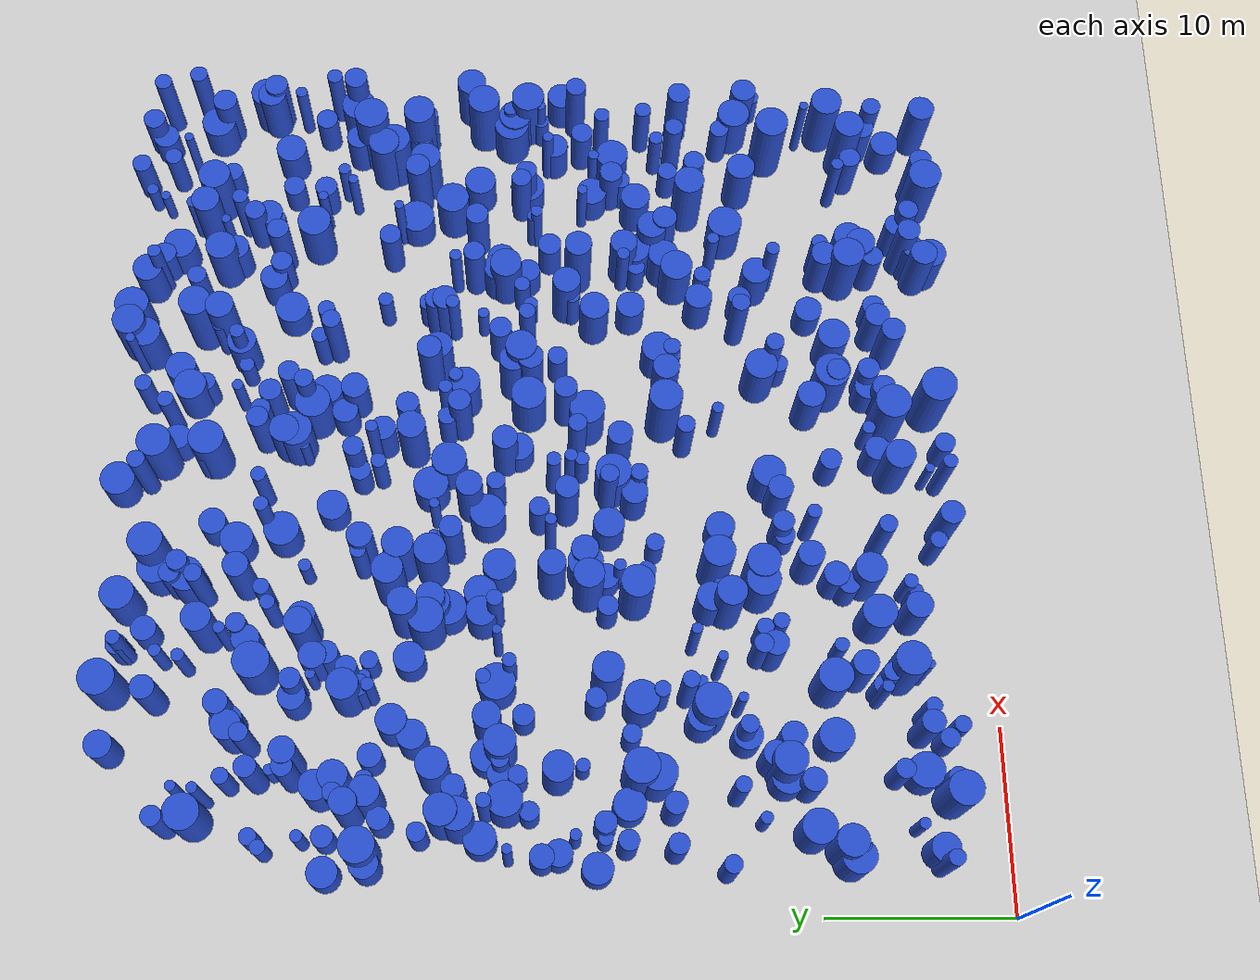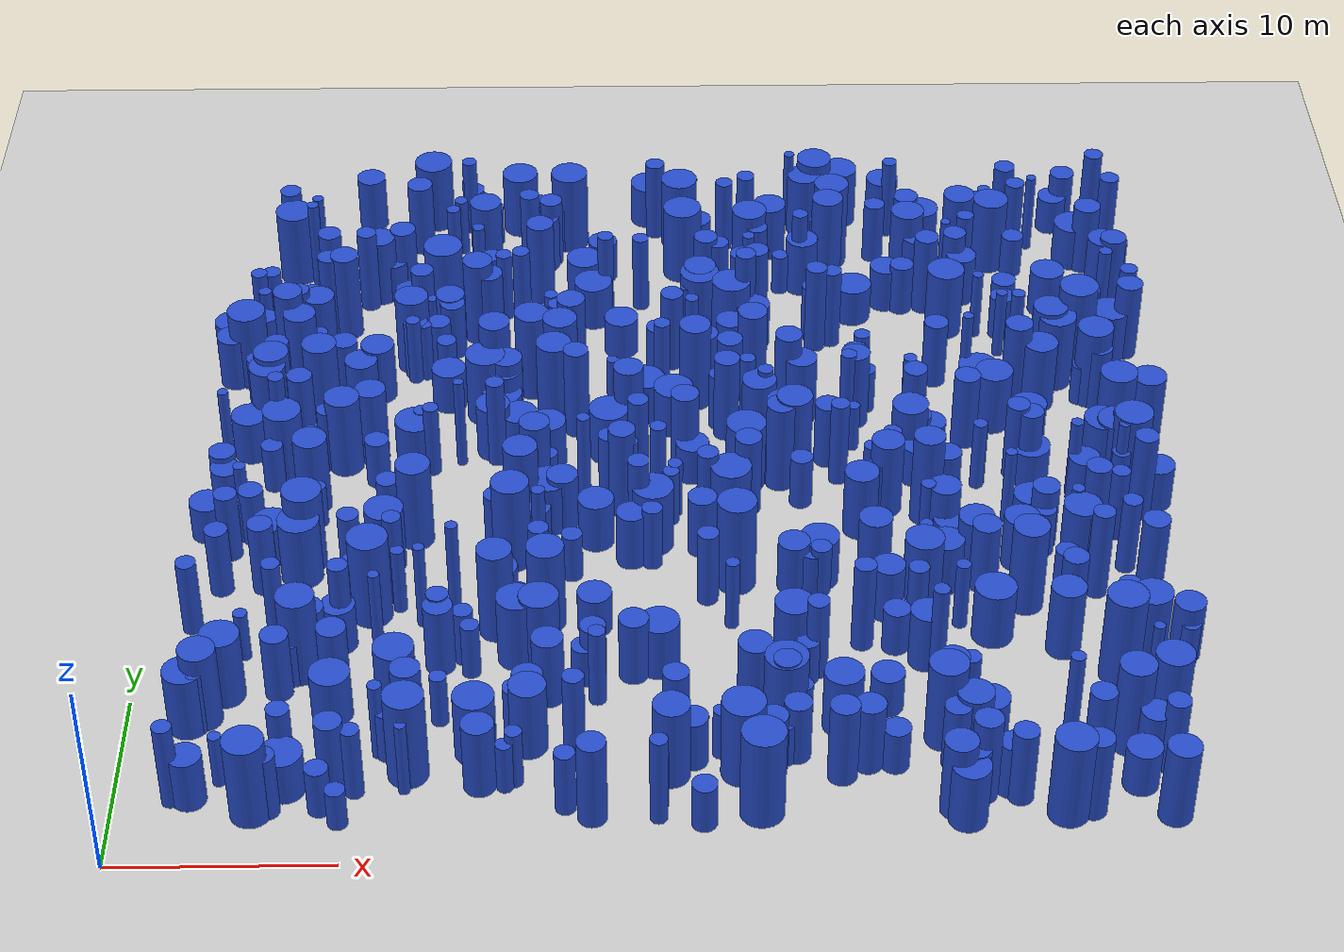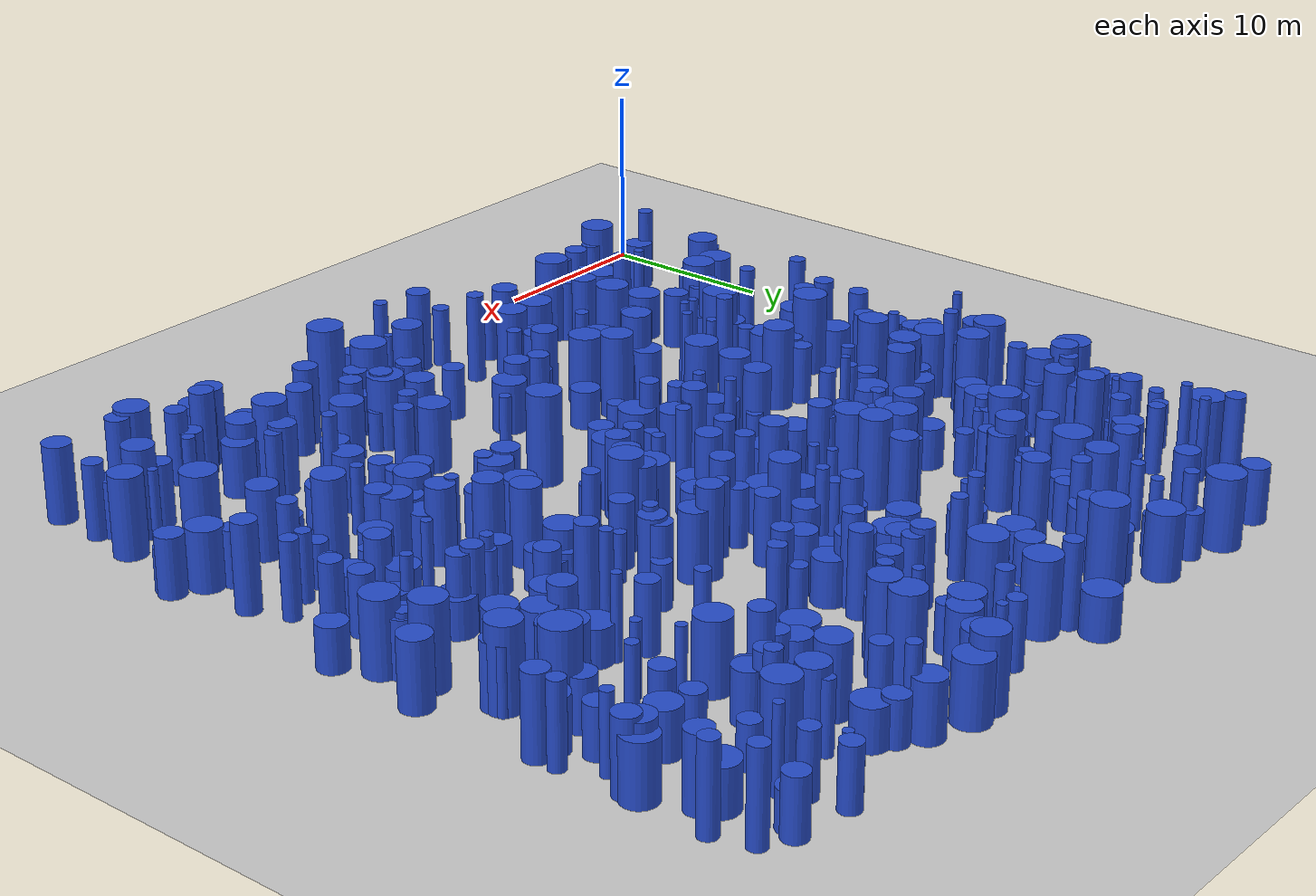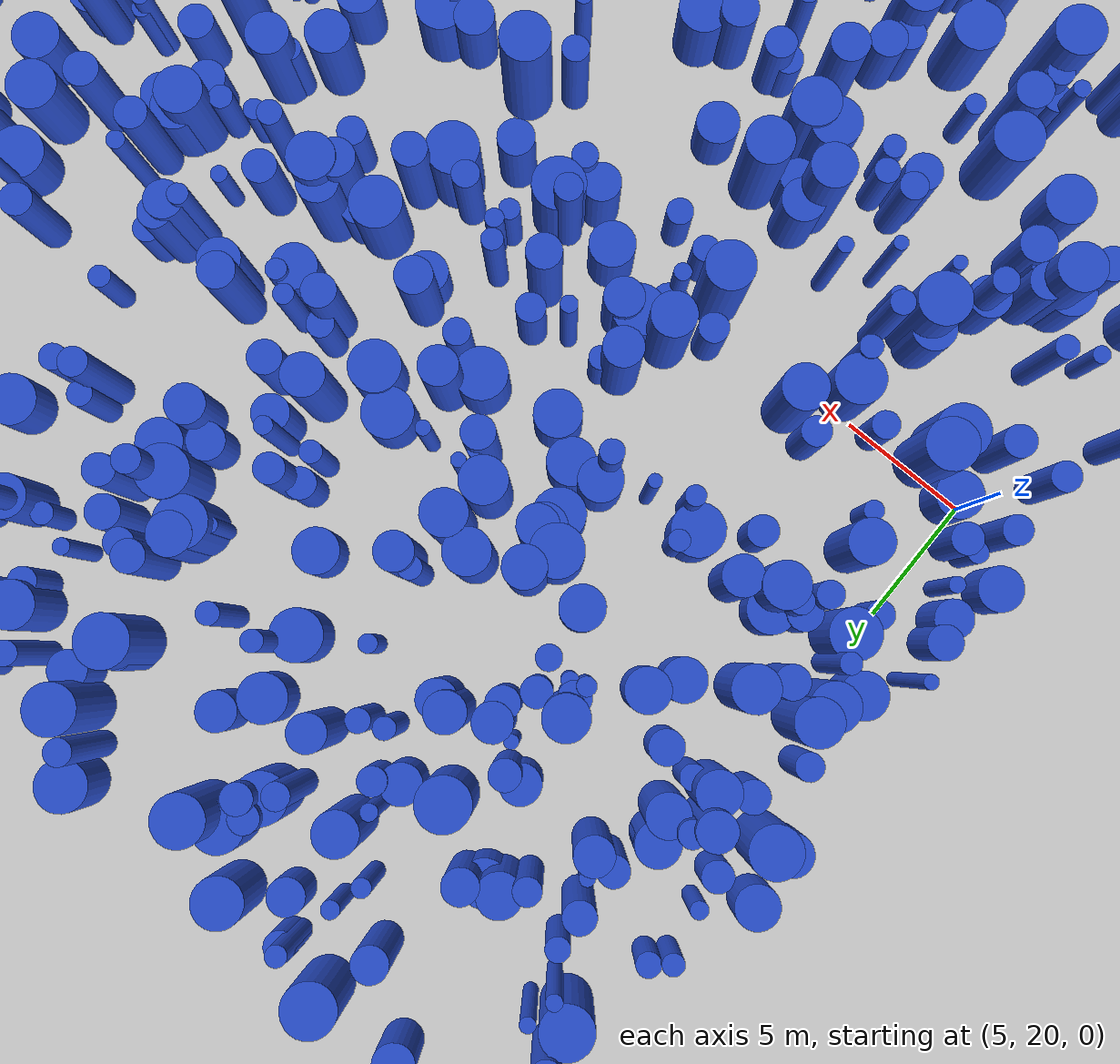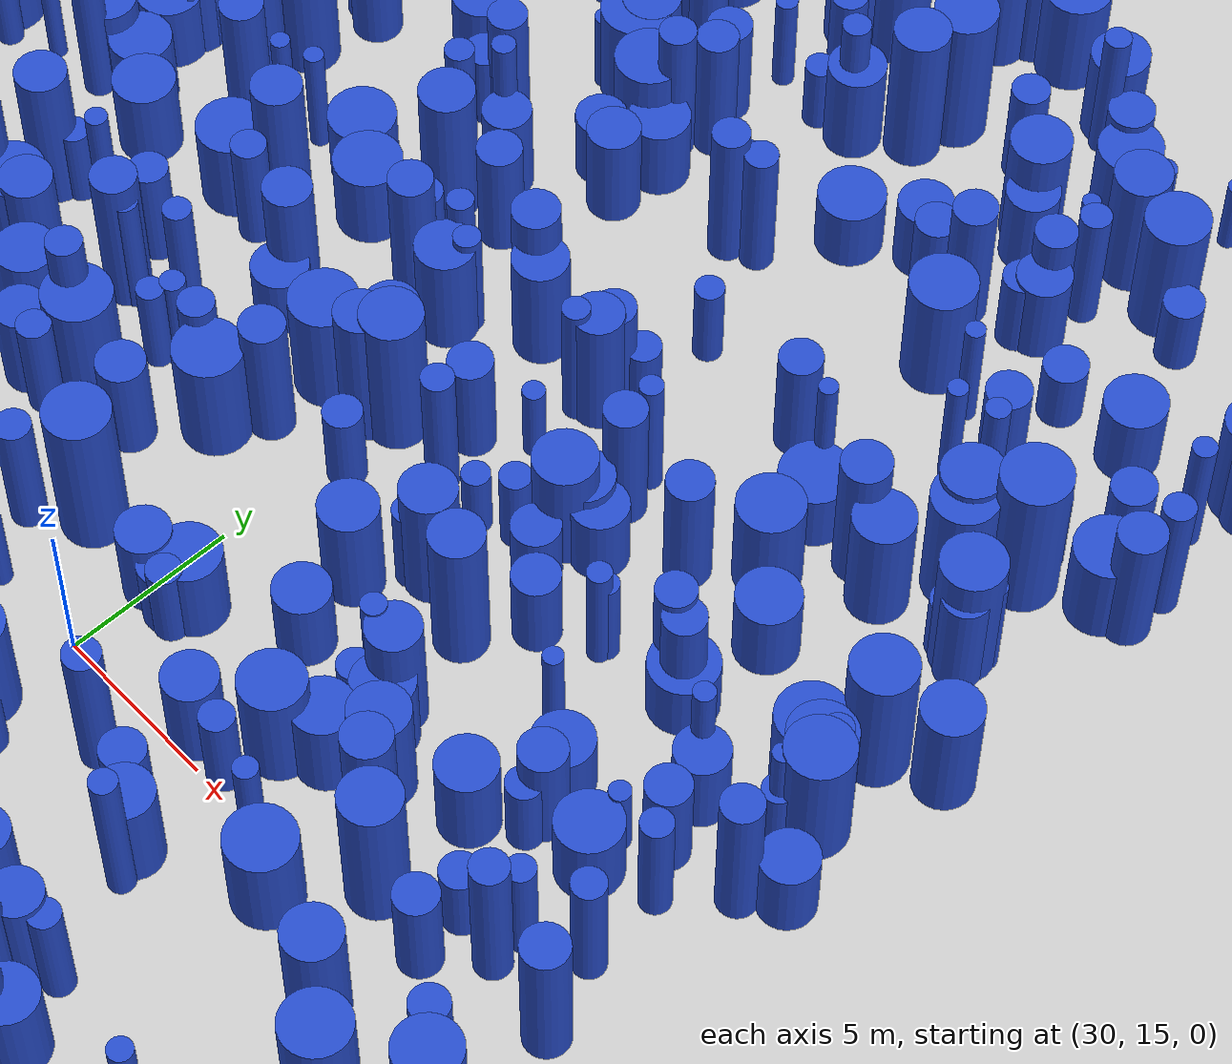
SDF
<sdf version="1.6">
 <world name="default">
  <light name="sun" type="directional">
   <pose>0 0 10 0 -0 0</pose>
   <diffuse>0.8 0.8 0.8 1</diffuse>
   <specular>0.1 0.1 0.1 1</specular>
   <attenuation>
    <range>1000</range>
    <constant>0.9</constant>
    <linear>0.01</linear>
    <quadratic>0.001</quadratic>
   </attenuation>
   <direction>-0.5 0.5 -1</direction>
  </light>
  <model name="ground_plane">
   <static>1</static>
   <link name="link">
    <collision name="collision">
     <geometry><plane><normal>0 0 1</normal><size>100 100</size></plane></geometry>
     <surface><friction><ode><mu>100</mu><mu2>50</mu2></ode></friction></surface>
    </collision>
    <visual name="visual">
     <cast_shadows>0</cast_shadows>
     <geometry><plane><normal>0 0 1</normal><size>100 100</size></plane></geometry>
     <material>
      <script><uri>file://media/materials/scripts/gazebo.material</uri><name>Gazebo/Grey</name></script>
     </material>
    </visual>
   </link>
  </model>
  <gravity>0 0 -9.8</gravity>
  <magnetic_field>6e-06 2.3e-05 -4.2e-05</magnetic_field>
  <atmosphere type="adiabatic"/>
  <physics name="default_physics" default="0" type="ode">
   <max_step_size>0.001</max_step_size>
   <real_time_factor>1</real_time_factor>
   <real_time_update_rate>1000</real_time_update_rate>
  </physics>
  <scene><ambient>0.4 0.4 0.4 1</ambient><background>0.7 0.7 0.7 1</background><shadows>1</shadows></scene>
  <spherical_coordinates>
   <surface_model>EARTH_WGS84</surface_model>
   <latitude_deg>0</latitude_deg>
   <longitude_deg>0</longitude_deg>
   <elevation>0</elevation>
   <heading_deg>0</heading_deg>
  </spherical_coordinates>
  <model name="0">
   <static>0</static>
   <link name="link">
    <inertial>
     <mass>2</mass>
     <inertia><ixx>1.43734</ixx><ixy>0</ixy><ixz>0</ixz><iyy>1.43734</iyy><iyz>0</iyz><izz>0.944565</izz></inertia>
    </inertial>
    <collision name="collision">
     <geometry><cylinder><length>2.40632</length><radius>0.971888</radius></cylinder></geometry>
     <surface><contact><collide_without_contact>1</collide_without_contact></contact></surface>
    </collision>
    <visual name="visual">
     <geometry><cylinder><length>2.40632</length><radius>0.971888</radius></cylinder></geometry>
     <material>
      <script><uri>file://media/materials/scripts/gazebo.material</uri><name>Gazebo/Blue</name></script>
     </material>
    </visual>
    <gravity>0</gravity>
   </link>
   <pose>20.5384 38.7875 1.20316 0 -0 0</pose>
  </model>
  <model name="1">
   <static>0</static>
   <link name="link">
    <inertial>
     <mass>2</mass>
     <inertia><ixx>1.21264</ixx><ixy>0</ixy><ixz>0</ixz><iyy>1.21264</iyy><iyz>0</iyz><izz>0.729702</izz></inertia>
    </inertial>
    <collision name="collision">
     <geometry><cylinder><length>2.25538</length><radius>0.854226</radius></cylinder></geometry>
     <surface><contact><collide_without_contact>1</collide_without_contact></contact></surface>
    </collision>
    <visual name="visual">
     <geometry><cylinder><length>2.25538</length><radius>0.854226</radius></cylinder></geometry>
     <material>
      <script><uri>file://media/materials/scripts/gazebo.material</uri><name>Gazebo/Blue</name></script>
     </material>
    </visual>
    <gravity>0</gravity>
   </link>
   <pose>13.3804 31.6772 1.12769 0 -0 0</pose>
  </model>
  <model name="2">
   <static>0</static>
   <link name="link">
    <inertial>
     <mass>2</mass>
     <inertia><ixx>1.9179</ixx><ixy>0</ixy><ixz>0</ixz><iyy>1.9179</iyy><iyz>0</iyz><izz>0.974837</izz></inertia>
    </inertial>
    <collision name="collision">
     <geometry><cylinder><length>2.92966</length><radius>0.987338</radius></cylinder></geometry>
     <surface><contact><collide_without_contact>1</collide_without_contact></contact></surface>
    </collision>
    <visual name="visual">
     <geometry><cylinder><length>2.92966</length><radius>0.987338</radius></cylinder></geometry>
     <material>
      <script><uri>file://media/materials/scripts/gazebo.material</uri><name>Gazebo/Blue</name></script>
     </material>
    </visual>
    <gravity>0</gravity>
   </link>
   <pose>45.4163 26.3645 1.46483 0 -0 0</pose>
  </model>
  <model name="3">
   <static>0</static>
   <link name="link">
    <inertial>
     <mass>2</mass>
     <inertia><ixx>3.92775</ixx><ixy>0</ixy><ixz>0</ixz><iyy>3.92775</iyy><iyz>0</iyz><izz>0.695081</izz></inertia>
    </inertial>
    <collision name="collision">
     <geometry><cylinder><length>4.63479</length><radius>0.833715</radius></cylinder></geometry>
     <surface><contact><collide_without_contact>1</collide_without_contact></contact></surface>
    </collision>
    <visual name="visual">
     <geometry><cylinder><length>4.63479</length><radius>0.833715</radius></cylinder></geometry>
     <material>
      <script><uri>file://media/materials/scripts/gazebo.material</uri><name>Gazebo/Blue</name></script>
     </material>
    </visual>
    <gravity>0</gravity>
   </link>
   <pose>12.2422 21.1681 2.31739 0 -0 0</pose>
  </model>
  <model name="4">
   <static>0</static>
   <link name="link">
    <inertial>
     <mass>2</mass>
     <inertia>
      <ixx>2.26503</ixx>
      <ixy>0</ixy>
      <ixz>0</ixz>
      <iyy>2.26503</iyy>
      <iyz>0</iyz>
      <izz>0.0810352</izz>
     </inertia>
    </inertial>
    <collision name="collision">
     <geometry><cylinder><length>3.65337</length><radius>0.284667</radius></cylinder></geometry>
     <surface><contact><collide_without_contact>1</collide_without_contact></contact></surface>
    </collision>
    <visual name="visual">
     <geometry><cylinder><length>3.65337</length><radius>0.284667</radius></cylinder></geometry>
     <material>
      <script><uri>file://media/materials/scripts/gazebo.material</uri><name>Gazebo/Blue</name></script>
     </material>
    </visual>
    <gravity>0</gravity>
   </link>
   <pose>21.5602 30.4174 1.82668 0 -0 0</pose>
  </model>
  <model name="5">
   <static>0</static>
   <link name="link">
    <inertial>
     <mass>2</mass>
     <inertia><ixx>2.0117</ixx><ixy>0</ixy><ixz>0</ixz><iyy>2.0117</iyy><iyz>0</iyz><izz>0.692416</izz></inertia>
    </inertial>
    <collision name="collision">
     <geometry><cylinder><length>3.16116</length><radius>0.832116</radius></cylinder></geometry>
     <surface><contact><collide_without_contact>1</collide_without_contact></contact></surface>
    </collision>
    <visual name="visual">
     <geometry><cylinder><length>3.16116</length><radius>0.832116</radius></cylinder></geometry>
     <material>
      <script><uri>file://media/materials/scripts/gazebo.material</uri><name>Gazebo/Blue</name></script>
     </material>
    </visual>
    <gravity>0</gravity>
   </link>
   <pose>9.83556 32.4698 1.58058 0 -0 0</pose>
  </model>
  <model name="6">
   <static>0</static>
   <link name="link">
    <inertial>
     <mass>2</mass>
     <inertia><ixx>1.5744</ixx><ixy>0</ixy><ixz>0</ixz><iyy>1.5744</iyy><iyz>0</iyz><izz>0.233531</izz></inertia>
    </inertial>
    <collision name="collision">
     <geometry><cylinder><length>2.95733</length><radius>0.483251</radius></cylinder></geometry>
     <surface><contact><collide_without_contact>1</collide_without_contact></contact></surface>
    </collision>
    <visual name="visual">
     <geometry><cylinder><length>2.95733</length><radius>0.483251</radius></cylinder></geometry>
     <material>
      <script><uri>file://media/materials/scripts/gazebo.material</uri><name>Gazebo/Blue</name></script>
     </material>
    </visual>
    <gravity>0</gravity>
   </link>
   <pose>6.75771 33.7908 1.47867 0 -0 0</pose>
  </model>
  <model name="7">
   <static>0</static>
   <link name="link">
    <inertial>
     <mass>2</mass>
     <inertia><ixx>4.42007</ixx><ixy>0</ixy><ixz>0</ixz><iyy>4.42007</iyy><iyz>0</iyz><izz>0.725358</izz></inertia>
    </inertial>
    <collision name="collision">
     <geometry><cylinder><length>4.934</length><radius>0.85168</radius></cylinder></geometry>
     <surface><contact><collide_without_contact>1</collide_without_contact></contact></surface>
    </collision>
    <visual name="visual">
     <geometry><cylinder><length>4.934</length><radius>0.85168</radius></cylinder></geometry>
     <material>
      <script><uri>file://media/materials/scripts/gazebo.material</uri><name>Gazebo/Blue</name></script>
     </material>
    </visual>
    <gravity>0</gravity>
   </link>
   <pose>7.21815 30.2077 2.467 0 -0 0</pose>
  </model>
  <model name="8">
   <static>0</static>
   <link name="link">
    <inertial>
     <mass>2</mass>
     <inertia><ixx>3.23009</ixx><ixy>0</ixy><ixz>0</ixz><iyy>3.23009</iyy><iyz>0</iyz><izz>0.313267</izz></inertia>
    </inertial>
    <collision name="collision">
     <geometry><cylinder><length>4.29427</length><radius>0.559703</radius></cylinder></geometry>
     <surface><contact><collide_without_contact>1</collide_without_contact></contact></surface>
    </collision>
    <visual name="visual">
     <geometry><cylinder><length>4.29427</length><radius>0.559703</radius></cylinder></geometry>
     <material>
      <script><uri>file://media/materials/scripts/gazebo.material</uri><name>Gazebo/Blue</name></script>
     </material>
    </visual>
    <gravity>0</gravity>
   </link>
   <pose>41.0947 25.7566 2.14713 0 -0 0</pose>
  </model>
  <model name="9">
   <static>0</static>
   <link name="link">
    <inertial>
     <mass>2</mass>
     <inertia><ixx>1.24437</ixx><ixy>0</ixy><ixz>0</ixz><iyy>1.24437</iyy><iyz>0</iyz><izz>0.137792</izz></inertia>
    </inertial>
    <collision name="collision">
     <geometry><cylinder><length>2.65572</length><radius>0.371203</radius></cylinder></geometry>
     <surface><contact><collide_without_contact>1</collide_without_contact></contact></surface>
    </collision>
    <visual name="visual">
     <geometry><cylinder><length>2.65572</length><radius>0.371203</radius></cylinder></geometry>
     <material>
      <script><uri>file://media/materials/scripts/gazebo.material</uri><name>Gazebo/Blue</name></script>
     </material>
    </visual>
    <gravity>0</gravity>
   </link>
   <pose>26.3091 6.47508 1.32786 0 -0 0</pose>
  </model>
  <model name="10">
   <static>0</static>
   <link name="link">
    <inertial>
     <mass>2</mass>
     <inertia><ixx>1.24688</ixx><ixy>0</ixy><ixz>0</ixz><iyy>1.24688</iyy><iyz>0</iyz><izz>0.518703</izz></inertia>
    </inertial>
    <collision name="collision">
     <geometry><cylinder><length>2.43417</length><radius>0.72021</radius></cylinder></geometry>
     <surface><contact><collide_without_contact>1</collide_without_contact></contact></surface>
    </collision>
    <visual name="visual">
     <geometry><cylinder><length>2.43417</length><radius>0.72021</radius></cylinder></geometry>
     <material>
      <script><uri>file://media/materials/scripts/gazebo.material</uri><name>Gazebo/Blue</name></script>
     </material>
    </visual>
    <gravity>0</gravity>
   </link>
   <pose>3.05727 23.7254 1.21708 0 -0 0</pose>
  </model>
  <model name="11">
   <static>0</static>
   <link name="link">
    <inertial>
     <mass>2</mass>
     <inertia><ixx>2.14367</ixx><ixy>0</ixy><ixz>0</ixz><iyy>2.14367</iyy><iyz>0</iyz><izz>0.840416</izz></inertia>
    </inertial>
    <collision name="collision">
     <geometry><cylinder><length>3.2157</length><radius>0.916742</radius></cylinder></geometry>
     <surface><contact><collide_without_contact>1</collide_without_contact></contact></surface>
    </collision>
    <visual name="visual">
     <geometry><cylinder><length>3.2157</length><radius>0.916742</radius></cylinder></geometry>
     <material>
      <script><uri>file://media/materials/scripts/gazebo.material</uri><name>Gazebo/Blue</name></script>
     </material>
    </visual>
    <gravity>0</gravity>
   </link>
   <pose>45.9924 13.2995 1.60785 0 -0 0</pose>
  </model>
  <model name="12">
   <static>0</static>
   <link name="link">
    <inertial>
     <mass>2</mass>
     <inertia><ixx>4.25183</ixx><ixy>0</ixy><ixz>0</ixz><iyy>4.25183</iyy><iyz>0</iyz><izz>0.805611</izz></inertia>
    </inertial>
    <collision name="collision">
     <geometry><cylinder><length>4.80564</length><radius>0.897558</radius></cylinder></geometry>
     <surface><contact><collide_without_contact>1</collide_without_contact></contact></surface>
    </collision>
    <visual name="visual">
     <geometry><cylinder><length>4.80564</length><radius>0.897558</radius></cylinder></geometry>
     <material>
      <script><uri>file://media/materials/scripts/gazebo.material</uri><name>Gazebo/Blue</name></script>
     </material>
    </visual>
    <gravity>0</gravity>
   </link>
   <pose>16.8242 19.5526 2.40282 0 -0 0</pose>
  </model>
  <model name="13">
   <static>0</static>
   <link name="link">
    <inertial>
     <mass>2</mass>
     <inertia><ixx>2.5994</ixx><ixy>0</ixy><ixz>0</ixz><iyy>2.5994</iyy><iyz>0</iyz><izz>0.0800748</izz></inertia>
    </inertial>
    <collision name="collision">
     <geometry><cylinder><length>3.91869</length><radius>0.282975</radius></cylinder></geometry>
     <surface><contact><collide_without_contact>1</collide_without_contact></contact></surface>
    </collision>
    <visual name="visual">
     <geometry><cylinder><length>3.91869</length><radius>0.282975</radius></cylinder></geometry>
     <material>
      <script><uri>file://media/materials/scripts/gazebo.material</uri><name>Gazebo/Blue</name></script>
     </material>
    </visual>
    <gravity>0</gravity>
   </link>
   <pose>46.0991 24.6597 1.95935 0 -0 0</pose>
  </model>
  <model name="14">
   <static>0</static>
   <link name="link">
    <inertial>
     <mass>2</mass>
     <inertia><ixx>1.64079</ixx><ixy>0</ixy><ixz>0</ixz><iyy>1.64079</iyy><iyz>0</iyz><izz>0.150374</izz></inertia>
    </inertial>
    <collision name="collision">
     <geometry><cylinder><length>3.0649</length><radius>0.38778</radius></cylinder></geometry>
     <surface><contact><collide_without_contact>1</collide_without_contact></contact></surface>
    </collision>
    <visual name="visual">
     <geometry><cylinder><length>3.0649</length><radius>0.38778</radius></cylinder></geometry>
     <material>
      <script><uri>file://media/materials/scripts/gazebo.material</uri><name>Gazebo/Blue</name></script>
     </material>
    </visual>
    <gravity>0</gravity>
   </link>
   <pose>17.3165 4.85681 1.53245 0 -0 0</pose>
  </model>
  <model name="15">
   <static>0</static>
   <link name="link">
    <inertial>
     <mass>2</mass>
     <inertia><ixx>4.38283</ixx><ixy>0</ixy><ixz>0</ixz><iyy>4.38283</iyy><iyz>0</iyz><izz>0.572271</izz></inertia>
    </inertial>
    <collision name="collision">
     <geometry><cylinder><length>4.95784</length><radius>0.756486</radius></cylinder></geometry>
     <surface><contact><collide_without_contact>1</collide_without_contact></contact></surface>
    </collision>
    <visual name="visual">
     <geometry><cylinder><length>4.95784</length><radius>0.756486</radius></cylinder></geometry>
     <material>
      <script><uri>file://media/materials/scripts/gazebo.material</uri><name>Gazebo/Blue</name></script>
     </material>
    </visual>
    <gravity>0</gravity>
   </link>
   <pose>36.5323 22.5346 2.47892 0 -0 0</pose>
  </model>
  <model name="16">
   <static>0</static>
   <link name="link">
    <inertial>
     <mass>2</mass>
     <inertia><ixx>1.32738</ixx><ixy>0</ixy><ixz>0</ixz><iyy>1.32738</iyy><iyz>0</iyz><izz>0.945054</izz></inertia>
    </inertial>
    <collision name="collision">
     <geometry><cylinder><length>2.26476</length><radius>0.972139</radius></cylinder></geometry>
     <surface><contact><collide_without_contact>1</collide_without_contact></contact></surface>
    </collision>
    <visual name="visual">
     <geometry><cylinder><length>2.26476</length><radius>0.972139</radius></cylinder></geometry>
     <material>
      <script><uri>file://media/materials/scripts/gazebo.material</uri><name>Gazebo/Blue</name></script>
     </material>
    </visual>
    <gravity>0</gravity>
   </link>
   <pose>16.1139 29.627 1.13238 0 -0 0</pose>
  </model>
  <model name="17">
   <static>0</static>
   <link name="link">
    <inertial>
     <mass>2</mass>
     <inertia><ixx>1.23789</ixx><ixy>0</ixy><ixz>0</ixz><iyy>1.23789</iyy><iyz>0</iyz><izz>0.598154</izz></inertia>
    </inertial>
    <collision name="collision">
     <geometry><cylinder><length>2.37337</length><radius>0.773404</radius></cylinder></geometry>
     <surface><contact><collide_without_contact>1</collide_without_contact></contact></surface>
    </collision>
    <visual name="visual">
     <geometry><cylinder><length>2.37337</length><radius>0.773404</radius></cylinder></geometry>
     <material>
      <script><uri>file://media/materials/scripts/gazebo.material</uri><name>Gazebo/Blue</name></script>
     </material>
    </visual>
    <gravity>0</gravity>
   </link>
   <pose>14.3822 40.423 1.18668 0 -0 0</pose>
  </model>
  <model name="18">
   <static>0</static>
   <link name="link">
    <inertial>
     <mass>2</mass>
     <inertia><ixx>1.59009</ixx><ixy>0</ixy><ixz>0</ixz><iyy>1.59009</iyy><iyz>0</iyz><izz>0.231054</izz></inertia>
    </inertial>
    <collision name="collision">
     <geometry><cylinder><length>2.97446</length><radius>0.48068</radius></cylinder></geometry>
     <surface><contact><collide_without_contact>1</collide_without_contact></contact></surface>
    </collision>
    <visual name="visual">
     <geometry><cylinder><length>2.97446</length><radius>0.48068</radius></cylinder></geometry>
     <material>
      <script><uri>file://media/materials/scripts/gazebo.material</uri><name>Gazebo/Blue</name></script>
     </material>
    </visual>
    <gravity>0</gravity>
   </link>
   <pose>35.5825 15.4394 1.48723 0 -0 0</pose>
  </model>
  <model name="19">
   <static>0</static>
   <link name="link">
    <inertial>
     <mass>2</mass>
     <inertia><ixx>1.33118</ixx><ixy>0</ixy><ixz>0</ixz><iyy>1.33118</iyy><iyz>0</iyz><izz>0.426868</izz></inertia>
    </inertial>
    <collision name="collision">
     <geometry><cylinder><length>2.58969</length><radius>0.653352</radius></cylinder></geometry>
     <surface><contact><collide_without_contact>1</collide_without_contact></contact></surface>
    </collision>
    <visual name="visual">
     <geometry><cylinder><length>2.58969</length><radius>0.653352</radius></cylinder></geometry>
     <material>
      <script><uri>file://media/materials/scripts/gazebo.material</uri><name>Gazebo/Blue</name></script>
     </material>
    </visual>
    <gravity>0</gravity>
   </link>
   <pose>8.06166 33.5749 1.29484 0 -0 0</pose>
  </model>
  <model name="20">
   <static>0</static>
   <link name="link">
    <inertial>
     <mass>2</mass>
     <inertia>
      <ixx>1.75585</ixx>
      <ixy>0</ixy>
      <ixz>0</ixz>
      <iyy>1.75585</iyy>
      <iyz>0</iyz>
      <izz>0.0905961</izz>
     </inertia>
    </inertial>
    <collision name="collision">
     <geometry><cylinder><length>3.20364</length><radius>0.300992</radius></cylinder></geometry>
     <surface><contact><collide_without_contact>1</collide_without_contact></contact></surface>
    </collision>
    <visual name="visual">
     <geometry><cylinder><length>3.20364</length><radius>0.300992</radius></cylinder></geometry>
     <material>
      <script><uri>file://media/materials/scripts/gazebo.material</uri><name>Gazebo/Blue</name></script>
     </material>
    </visual>
    <gravity>0</gravity>
   </link>
   <pose>3.87578 22.8858 1.60182 0 -0 0</pose>
  </model>
  <model name="21">
   <static>0</static>
   <link name="link">
    <inertial>
     <mass>2</mass>
     <inertia><ixx>1.37016</ixx><ixy>0</ixy><ixz>0</ixz><iyy>1.37016</iyy><iyz>0</iyz><izz>0.921566</izz></inertia>
    </inertial>
    <collision name="collision">
     <geometry><cylinder><length>2.33587</length><radius>0.959982</radius></cylinder></geometry>
     <surface><contact><collide_without_contact>1</collide_without_contact></contact></surface>
    </collision>
    <visual name="visual">
     <geometry><cylinder><length>2.33587</length><radius>0.959982</radius></cylinder></geometry>
     <material>
      <script><uri>file://media/materials/scripts/gazebo.material</uri><name>Gazebo/Blue</name></script>
     </material>
    </visual>
    <gravity>0</gravity>
   </link>
   <pose>23.4785 47.9749 1.16793 0 -0 0</pose>
  </model>
  <model name="22">
   <static>0</static>
   <link name="link">
    <inertial>
     <mass>2</mass>
     <inertia>
      <ixx>0.996712</ixx>
      <ixy>0</ixy>
      <ixz>0</ixz>
      <iyy>0.996712</iyy>
      <iyz>0</iyz>
      <izz>0.087716</izz>
     </inertia>
    </inertial>
    <collision name="collision">
     <geometry><cylinder><length>2.39105</length><radius>0.296169</radius></cylinder></geometry>
     <surface><contact><collide_without_contact>1</collide_without_contact></contact></surface>
    </collision>
    <visual name="visual">
     <geometry><cylinder><length>2.39105</length><radius>0.296169</radius></cylinder></geometry>
     <material>
      <script><uri>file://media/materials/scripts/gazebo.material</uri><name>Gazebo/Blue</name></script>
     </material>
    </visual>
    <gravity>0</gravity>
   </link>
   <pose>7.34966 38.7949 1.19553 0 -0 0</pose>
  </model>
  <model name="23">
   <static>0</static>
   <link name="link">
    <inertial>
     <mass>2</mass>
     <inertia><ixx>3.04938</ixx><ixy>0</ixy><ixz>0</ixz><iyy>3.04938</iyy><iyz>0</iyz><izz>0.188982</izz></inertia>
    </inertial>
    <collision name="collision">
     <geometry><cylinder><length>4.21062</length><radius>0.434721</radius></cylinder></geometry>
     <surface><contact><collide_without_contact>1</collide_without_contact></contact></surface>
    </collision>
    <visual name="visual">
     <geometry><cylinder><length>4.21062</length><radius>0.434721</radius></cylinder></geometry>
     <material>
      <script><uri>file://media/materials/scripts/gazebo.material</uri><name>Gazebo/Blue</name></script>
     </material>
    </visual>
    <gravity>0</gravity>
   </link>
   <pose>39.9557 41.882 2.10531 0 -0 0</pose>
  </model>
  <model name="24">
   <static>0</static>
   <link name="link">
    <inertial>
     <mass>2</mass>
     <inertia><ixx>1.33099</ixx><ixy>0</ixy><ixz>0</ixz><iyy>1.33099</iyy><iyz>0</iyz><izz>0.36083</izz></inertia>
    </inertial>
    <collision name="collision">
     <geometry><cylinder><length>2.62744</length><radius>0.600691</radius></cylinder></geometry>
     <surface><contact><collide_without_contact>1</collide_without_contact></contact></surface>
    </collision>
    <visual name="visual">
     <geometry><cylinder><length>2.62744</length><radius>0.600691</radius></cylinder></geometry>
     <material>
      <script><uri>file://media/materials/scripts/gazebo.material</uri><name>Gazebo/Blue</name></script>
     </material>
    </visual>
    <gravity>0</gravity>
   </link>
   <pose>17.3457 8.06964 1.31372 0 -0 0</pose>
  </model>
  <model name="25">
   <static>0</static>
   <link name="link">
    <inertial>
     <mass>2</mass>
     <inertia><ixx>1.51438</ixx><ixy>0</ixy><ixz>0</ixz><iyy>1.51438</iyy><iyz>0</iyz><izz>0.951451</izz></inertia>
    </inertial>
    <collision name="collision">
     <geometry><cylinder><length>2.49638</length><radius>0.975423</radius></cylinder></geometry>
     <surface><contact><collide_without_contact>1</collide_without_contact></contact></surface>
    </collision>
    <visual name="visual">
     <geometry><cylinder><length>2.49638</length><radius>0.975423</radius></cylinder></geometry>
     <material>
      <script><uri>file://media/materials/scripts/gazebo.material</uri><name>Gazebo/Blue</name></script>
     </material>
    </visual>
    <gravity>0</gravity>
   </link>
   <pose>24.5529 29.7279 1.24819 0 -0 0</pose>
  </model>
  <model name="26">
   <static>0</static>
   <link name="link">
    <inertial>
     <mass>2</mass>
     <inertia><ixx>1.75387</ixx><ixy>0</ixy><ixz>0</ixz><iyy>1.75387</iyy><iyz>0</iyz><izz>0.848622</izz></inertia>
    </inertial>
    <collision name="collision">
     <geometry><cylinder><length>2.82442</length><radius>0.921207</radius></cylinder></geometry>
     <surface><contact><collide_without_contact>1</collide_without_contact></contact></surface>
    </collision>
    <visual name="visual">
     <geometry><cylinder><length>2.82442</length><radius>0.921207</radius></cylinder></geometry>
     <material>
      <script><uri>file://media/materials/scripts/gazebo.material</uri><name>Gazebo/Blue</name></script>
     </material>
    </visual>
    <gravity>0</gravity>
   </link>
   <pose>23.683 12.1353 1.41221 0 -0 0</pose>
  </model>
  <model name="27">
   <static>0</static>
   <link name="link">
    <inertial>
     <mass>2</mass>
     <inertia><ixx>2.24556</ixx><ixy>0</ixy><ixz>0</ixz><iyy>2.24556</iyy><iyz>0</iyz><izz>0.865007</izz></inertia>
    </inertial>
    <collision name="collision">
     <geometry><cylinder><length>3.29823</length><radius>0.930057</radius></cylinder></geometry>
     <surface><contact><collide_without_contact>1</collide_without_contact></contact></surface>
    </collision>
    <visual name="visual">
     <geometry><cylinder><length>3.29823</length><radius>0.930057</radius></cylinder></geometry>
     <material>
      <script><uri>file://media/materials/scripts/gazebo.material</uri><name>Gazebo/Blue</name></script>
     </material>
    </visual>
    <gravity>0</gravity>
   </link>
   <pose>40.362 29.7446 1.64912 0 -0 0</pose>
  </model>
  <model name="28">
   <static>0</static>
   <link name="link">
    <inertial>
     <mass>2</mass>
     <inertia>
      <ixx>4.08418</ixx>
      <ixy>0</ixy>
      <ixz>0</ixz>
      <iyy>4.08418</iyy>
      <iyz>0</iyz>
      <izz>0.0857833</izz>
     </inertia>
    </inertial>
    <collision name="collision">
     <geometry><cylinder><length>4.9242</length><radius>0.292888</radius></cylinder></geometry>
     <surface><contact><collide_without_contact>1</collide_without_contact></contact></surface>
    </collision>
    <visual name="visual">
     <geometry><cylinder><length>4.9242</length><radius>0.292888</radius></cylinder></geometry>
     <material>
      <script><uri>file://media/materials/scripts/gazebo.material</uri><name>Gazebo/Blue</name></script>
     </material>
    </visual>
    <gravity>0</gravity>
   </link>
   <pose>5.98766 42.2378 2.4621 0 -0 0</pose>
  </model>
  <model name="29">
   <static>0</static>
   <link name="link">
    <inertial>
     <mass>2</mass>
     <inertia><ixx>1.08444</ixx><ixy>0</ixy><ixz>0</ixz><iyy>1.08444</iyy><iyz>0</iyz><izz>0.820187</izz></inertia>
    </inertial>
    <collision name="collision">
     <geometry><cylinder><length>2.01148</length><radius>0.905642</radius></cylinder></geometry>
     <surface><contact><collide_without_contact>1</collide_without_contact></contact></surface>
    </collision>
    <visual name="visual">
     <geometry><cylinder><length>2.01148</length><radius>0.905642</radius></cylinder></geometry>
     <material>
      <script><uri>file://media/materials/scripts/gazebo.material</uri><name>Gazebo/Blue</name></script>
     </material>
    </visual>
    <gravity>0</gravity>
   </link>
   <pose>8.17215 27.4661 1.00574 0 -0 0</pose>
  </model>
  <model name="30">
   <static>0</static>
   <link name="link">
    <inertial>
     <mass>2</mass>
     <inertia><ixx>3.98428</ixx><ixy>0</ixy><ixz>0</ixz><iyy>3.98428</iyy><iyz>0</iyz><izz>0.265355</izz></inertia>
    </inertial>
    <collision name="collision">
     <geometry><cylinder><length>4.80724</length><radius>0.515126</radius></cylinder></geometry>
     <surface><contact><collide_without_contact>1</collide_without_contact></contact></surface>
    </collision>
    <visual name="visual">
     <geometry><cylinder><length>4.80724</length><radius>0.515126</radius></cylinder></geometry>
     <material>
      <script><uri>file://media/materials/scripts/gazebo.material</uri><name>Gazebo/Blue</name></script>
     </material>
    </visual>
    <gravity>0</gravity>
   </link>
   <pose>32.9406 13.5218 2.40362 0 -0 0</pose>
  </model>
  <model name="31">
   <static>0</static>
   <link name="link">
    <inertial>
     <mass>2</mass>
     <inertia><ixx>2.46305</ixx><ixy>0</ixy><ixz>0</ixz><iyy>2.46305</iyy><iyz>0</iyz><izz>0.114316</izz></inertia>
    </inertial>
    <collision name="collision">
     <geometry><cylinder><length>3.79939</length><radius>0.338106</radius></cylinder></geometry>
     <surface><contact><collide_without_contact>1</collide_without_contact></contact></surface>
    </collision>
    <visual name="visual">
     <geometry><cylinder><length>3.79939</length><radius>0.338106</radius></cylinder></geometry>
     <material>
      <script><uri>file://media/materials/scripts/gazebo.material</uri><name>Gazebo/Blue</name></script>
     </material>
    </visual>
    <gravity>0</gravity>
   </link>
   <pose>39.2114 24.8963 1.89969 0 -0 0</pose>
  </model>
  <model name="32">
   <static>0</static>
   <link name="link">
    <inertial>
     <mass>2</mass>
     <inertia><ixx>2.61108</ixx><ixy>0</ixy><ixz>0</ixz><iyy>2.61108</iyy><iyz>0</iyz><izz>0.521676</izz></inertia>
    </inertial>
    <collision name="collision">
     <geometry><cylinder><length>3.75519</length><radius>0.722271</radius></cylinder></geometry>
     <surface><contact><collide_without_contact>1</collide_without_contact></contact></surface>
    </collision>
    <visual name="visual">
     <geometry><cylinder><length>3.75519</length><radius>0.722271</radius></cylinder></geometry>
     <material>
      <script><uri>file://media/materials/scripts/gazebo.material</uri><name>Gazebo/Blue</name></script>
     </material>
    </visual>
    <gravity>0</gravity>
   </link>
   <pose>36.5241 8.5571 1.87759 0 -0 0</pose>
  </model>
  <model name="33">
   <static>0</static>
   <link name="link">
    <inertial>
     <mass>2</mass>
     <inertia><ixx>2.72224</ixx><ixy>0</ixy><ixz>0</ixz><iyy>2.72224</iyy><iyz>0</iyz><izz>0.654472</izz></inertia>
    </inertial>
    <collision name="collision">
     <geometry><cylinder><length>3.79078</length><radius>0.808995</radius></cylinder></geometry>
     <surface><contact><collide_without_contact>1</collide_without_contact></contact></surface>
    </collision>
    <visual name="visual">
     <geometry><cylinder><length>3.79078</length><radius>0.808995</radius></cylinder></geometry>
     <material>
      <script><uri>file://media/materials/scripts/gazebo.material</uri><name>Gazebo/Blue</name></script>
     </material>
    </visual>
    <gravity>0</gravity>
   </link>
   <pose>42.0996 13.0769 1.89539 0 -0 0</pose>
  </model>
  <model name="34">
   <static>0</static>
   <link name="link">
    <inertial>
     <mass>2</mass>
     <inertia><ixx>2.73964</ixx><ixy>0</ixy><ixz>0</ixz><iyy>2.73964</iyy><iyz>0</iyz><izz>0.355039</izz></inertia>
    </inertial>
    <collision name="collision">
     <geometry><cylinder><length>3.92081</length><radius>0.595852</radius></cylinder></geometry>
     <surface><contact><collide_without_contact>1</collide_without_contact></contact></surface>
    </collision>
    <visual name="visual">
     <geometry><cylinder><length>3.92081</length><radius>0.595852</radius></cylinder></geometry>
     <material>
      <script><uri>file://media/materials/scripts/gazebo.material</uri><name>Gazebo/Blue</name></script>
     </material>
    </visual>
    <gravity>0</gravity>
   </link>
   <pose>5.35862 17.7826 1.9604 0 -0 0</pose>
  </model>
  <model name="35">
   <static>0</static>
   <link name="link">
    <inertial>
     <mass>2</mass>
     <inertia><ixx>2.06592</ixx><ixy>0</ixy><ixz>0</ixz><iyy>2.06592</iyy><iyz>0</iyz><izz>0.920991</izz></inertia>
    </inertial>
    <collision name="collision">
     <geometry><cylinder><length>3.10364</length><radius>0.959683</radius></cylinder></geometry>
     <surface><contact><collide_without_contact>1</collide_without_contact></contact></surface>
    </collision>
    <visual name="visual">
     <geometry><cylinder><length>3.10364</length><radius>0.959683</radius></cylinder></geometry>
     <material>
      <script><uri>file://media/materials/scripts/gazebo.material</uri><name>Gazebo/Blue</name></script>
     </material>
    </visual>
    <gravity>0</gravity>
   </link>
   <pose>17.7601 43.7207 1.55182 0 -0 0</pose>
  </model>
  <model name="36">
   <static>0</static>
   <link name="link">
    <inertial>
     <mass>2</mass>
     <inertia><ixx>1.02322</ixx><ixy>0</ixy><ixz>0</ixz><iyy>1.02322</iyy><iyz>0</iyz><izz>0.699364</izz></inertia>
    </inertial>
    <collision name="collision">
     <geometry><cylinder><length>2.01028</length><radius>0.83628</radius></cylinder></geometry>
     <surface><contact><collide_without_contact>1</collide_without_contact></contact></surface>
    </collision>
    <visual name="visual">
     <geometry><cylinder><length>2.01028</length><radius>0.83628</radius></cylinder></geometry>
     <material>
      <script><uri>file://media/materials/scripts/gazebo.material</uri><name>Gazebo/Blue</name></script>
     </material>
    </visual>
    <gravity>0</gravity>
   </link>
   <pose>2.3337 21.7478 1.00514 0 -0 0</pose>
  </model>
  <model name="37">
   <static>0</static>
   <link name="link">
    <inertial>
     <mass>2</mass>
     <inertia><ixx>3.11102</ixx><ixy>0</ixy><ixz>0</ixz><iyy>3.11102</iyy><iyz>0</iyz><izz>0.974531</izz></inertia>
    </inertial>
    <collision name="collision">
     <geometry><cylinder><length>3.96769</length><radius>0.987183</radius></cylinder></geometry>
     <surface><contact><collide_without_contact>1</collide_without_contact></contact></surface>
    </collision>
    <visual name="visual">
     <geometry><cylinder><length>3.96769</length><radius>0.987183</radius></cylinder></geometry>
     <material>
      <script><uri>file://media/materials/scripts/gazebo.material</uri><name>Gazebo/Blue</name></script>
     </material>
    </visual>
    <gravity>0</gravity>
   </link>
   <pose>29.2156 8.50585 1.98384 0 -0 0</pose>
  </model>
  <model name="38">
   <static>0</static>
   <link name="link">
    <inertial>
     <mass>2</mass>
     <inertia><ixx>1.65718</ixx><ixy>0</ixy><ixz>0</ixz><iyy>1.65718</iyy><iyz>0</iyz><izz>0.295859</izz></inertia>
    </inertial>
    <collision name="collision">
     <geometry><cylinder><length>3.00924</length><radius>0.543929</radius></cylinder></geometry>
     <surface><contact><collide_without_contact>1</collide_without_contact></contact></surface>
    </collision>
    <visual name="visual">
     <geometry><cylinder><length>3.00924</length><radius>0.543929</radius></cylinder></geometry>
     <material>
      <script><uri>file://media/materials/scripts/gazebo.material</uri><name>Gazebo/Blue</name></script>
     </material>
    </visual>
    <gravity>0</gravity>
   </link>
   <pose>45.0656 14.1562 1.50462 0 -0 0</pose>
  </model>
  <model name="39">
   <static>0</static>
   <link name="link">
    <inertial>
     <mass>2</mass>
     <inertia><ixx>2.41207</ixx><ixy>0</ixy><ixz>0</ixz><iyy>2.41207</iyy><iyz>0</iyz><izz>0.674875</izz></inertia>
    </inertial>
    <collision name="collision">
     <geometry><cylinder><length>3.52814</length><radius>0.821508</radius></cylinder></geometry>
     <surface><contact><collide_without_contact>1</collide_without_contact></contact></surface>
    </collision>
    <visual name="visual">
     <geometry><cylinder><length>3.52814</length><radius>0.821508</radius></cylinder></geometry>
     <material>
      <script><uri>file://media/materials/scripts/gazebo.material</uri><name>Gazebo/Blue</name></script>
     </material>
    </visual>
    <gravity>0</gravity>
   </link>
   <pose>6.34437 36.277 1.76407 0 -0 0</pose>
  </model>
  <model name="40">
   <static>0</static>
   <link name="link">
    <inertial>
     <mass>2</mass>
     <inertia><ixx>2.09955</ixx><ixy>0</ixy><ixz>0</ixz><iyy>2.09955</iyy><iyz>0</iyz><izz>0.83864</izz></inertia>
    </inertial>
    <collision name="collision">
     <geometry><cylinder><length>3.17512</length><radius>0.915773</radius></cylinder></geometry>
     <surface><contact><collide_without_contact>1</collide_without_contact></contact></surface>
    </collision>
    <visual name="visual">
     <geometry><cylinder><length>3.17512</length><radius>0.915773</radius></cylinder></geometry>
     <material>
      <script><uri>file://media/materials/scripts/gazebo.material</uri><name>Gazebo/Blue</name></script>
     </material>
    </visual>
    <gravity>0</gravity>
   </link>
   <pose>47.4771 40.8684 1.58756 0 -0 0</pose>
  </model>
  <model name="41">
   <static>0</static>
   <link name="link">
    <inertial>
     <mass>2</mass>
     <inertia>
      <ixx>2.58319</ixx>
      <ixy>0</ixy>
      <ixz>0</ixz>
      <iyy>2.58319</iyy>
      <iyz>0</iyz>
      <izz>0.0988008</izz>
     </inertia>
    </inertial>
    <collision name="collision">
     <geometry><cylinder><length>3.89907</length><radius>0.314326</radius></cylinder></geometry>
     <surface><contact><collide_without_contact>1</collide_without_contact></contact></surface>
    </collision>
    <visual name="visual">
     <geometry><cylinder><length>3.89907</length><radius>0.314326</radius></cylinder></geometry>
     <material>
      <script><uri>file://media/materials/scripts/gazebo.material</uri><name>Gazebo/Blue</name></script>
     </material>
    </visual>
    <gravity>0</gravity>
   </link>
   <pose>14.5714 41.5767 1.94954 0 -0 0</pose>
  </model>
  <model name="42">
   <static>0</static>
   <link name="link">
    <inertial>
     <mass>2</mass>
     <inertia><ixx>2.29017</ixx><ixy>0</ixy><ixz>0</ixz><iyy>2.29017</iyy><iyz>0</iyz><izz>0.162084</izz></inertia>
    </inertial>
    <collision name="collision">
     <geometry><cylinder><length>3.64071</length><radius>0.402597</radius></cylinder></geometry>
     <surface><contact><collide_without_contact>1</collide_without_contact></contact></surface>
    </collision>
    <visual name="visual">
     <geometry><cylinder><length>3.64071</length><radius>0.402597</radius></cylinder></geometry>
     <material>
      <script><uri>file://media/materials/scripts/gazebo.material</uri><name>Gazebo/Blue</name></script>
     </material>
    </visual>
    <gravity>0</gravity>
   </link>
   <pose>44.08 17.9301 1.82036 0 -0 0</pose>
  </model>
  <model name="43">
   <static>0</static>
   <link name="link">
    <inertial>
     <mass>2</mass>
     <inertia><ixx>1.09648</ixx><ixy>0</ixy><ixz>0</ixz><iyy>1.09648</iyy><iyz>0</iyz><izz>0.193563</izz></inertia>
    </inertial>
    <collision name="collision">
     <geometry><cylinder><length>2.44912</length><radius>0.439957</radius></cylinder></geometry>
     <surface><contact><collide_without_contact>1</collide_without_contact></contact></surface>
    </collision>
    <visual name="visual">
     <geometry><cylinder><length>2.44912</length><radius>0.439957</radius></cylinder></geometry>
     <material>
      <script><uri>file://media/materials/scripts/gazebo.material</uri><name>Gazebo/Blue</name></script>
     </material>
    </visual>
    <gravity>0</gravity>
   </link>
   <pose>9.04417 13.8401 1.22456 0 -0 0</pose>
  </model>
  <model name="44">
   <static>0</static>
   <link name="link">
    <inertial>
     <mass>2</mass>
     <inertia><ixx>1.0311</ixx><ixy>0</ixy><ixz>0</ixz><iyy>1.0311</iyy><iyz>0</iyz><izz>0.585255</izz></inertia>
    </inertial>
    <collision name="collision">
     <geometry><cylinder><length>2.10495</length><radius>0.765019</radius></cylinder></geometry>
     <surface><contact><collide_without_contact>1</collide_without_contact></contact></surface>
    </collision>
    <visual name="visual">
     <geometry><cylinder><length>2.10495</length><radius>0.765019</radius></cylinder></geometry>
     <material>
      <script><uri>file://media/materials/scripts/gazebo.material</uri><name>Gazebo/Blue</name></script>
     </material>
    </visual>
    <gravity>0</gravity>
   </link>
   <pose>33.7804 9.37787 1.05247 0 -0 0</pose>
  </model>
  <model name="45">
   <static>0</static>
   <link name="link">
    <inertial>
     <mass>2</mass>
     <inertia><ixx>2.79189</ixx><ixy>0</ixy><ixz>0</ixz><iyy>2.79189</iyy><iyz>0</iyz><izz>0.226924</izz></inertia>
    </inertial>
    <collision name="collision">
     <geometry><cylinder><length>4.00881</length><radius>0.476365</radius></cylinder></geometry>
     <surface><contact><collide_without_contact>1</collide_without_contact></contact></surface>
    </collision>
    <visual name="visual">
     <geometry><cylinder><length>4.00881</length><radius>0.476365</radius></cylinder></geometry>
     <material>
      <script><uri>file://media/materials/scripts/gazebo.material</uri><name>Gazebo/Blue</name></script>
     </material>
    </visual>
    <gravity>0</gravity>
   </link>
   <pose>2.27674 14.996 2.00441 0 -0 0</pose>
  </model>
  <model name="46">
   <static>0</static>
   <link name="link">
    <inertial>
     <mass>2</mass>
     <inertia><ixx>2.99386</ixx><ixy>0</ixy><ixz>0</ixz><iyy>2.99386</iyy><iyz>0</iyz><izz>0.435719</izz></inertia>
    </inertial>
    <collision name="collision">
     <geometry><cylinder><length>4.08118</length><radius>0.66009</radius></cylinder></geometry>
     <surface><contact><collide_without_contact>1</collide_without_contact></contact></surface>
    </collision>
    <visual name="visual">
     <geometry><cylinder><length>4.08118</length><radius>0.66009</radius></cylinder></geometry>
     <material>
      <script><uri>file://media/materials/scripts/gazebo.material</uri><name>Gazebo/Blue</name></script>
     </material>
    </visual>
    <gravity>0</gravity>
   </link>
   <pose>11.3429 45.3423 2.04059 0 -0 0</pose>
  </model>
  <model name="47">
   <static>0</static>
   <link name="link">
    <inertial>
     <mass>2</mass>
     <inertia><ixx>1.72032</ixx><ixy>0</ixy><ixz>0</ixz><iyy>1.72032</iyy><iyz>0</iyz><izz>0.58604</izz></inertia>
    </inertial>
    <collision name="collision">
     <geometry><cylinder><length>2.92639</length><radius>0.765532</radius></cylinder></geometry>
     <surface><contact><collide_without_contact>1</collide_without_contact></contact></surface>
    </collision>
    <visual name="visual">
     <geometry><cylinder><length>2.92639</length><radius>0.765532</radius></cylinder></geometry>
     <material>
      <script><uri>file://media/materials/scripts/gazebo.material</uri><name>Gazebo/Blue</name></script>
     </material>
    </visual>
    <gravity>0</gravity>
   </link>
   <pose>34.2231 15.6872 1.4632 0 -0 0</pose>
  </model>
  <model name="48">
   <static>0</static>
   <link name="link">
    <inertial>
     <mass>2</mass>
     <inertia><ixx>2.37656</ixx><ixy>0</ixy><ixz>0</ixz><iyy>2.37656</iyy><iyz>0</iyz><izz>0.127367</izz></inertia>
    </inertial>
    <collision name="collision">
     <geometry><cylinder><length>3.72522</length><radius>0.356886</radius></cylinder></geometry>
     <surface><contact><collide_without_contact>1</collide_without_contact></contact></surface>
    </collision>
    <visual name="visual">
     <geometry><cylinder><length>3.72522</length><radius>0.356886</radius></cylinder></geometry>
     <material>
      <script><uri>file://media/materials/scripts/gazebo.material</uri><name>Gazebo/Blue</name></script>
     </material>
    </visual>
    <gravity>0</gravity>
   </link>
   <pose>11.5725 33.7002 1.86261 0 -0 0</pose>
  </model>
  <model name="49">
   <static>0</static>
   <link name="link">
    <inertial>
     <mass>2</mass>
     <inertia><ixx>1.4206</ixx><ixy>0</ixy><ixz>0</ixz><iyy>1.4206</iyy><iyz>0</iyz><izz>0.438407</izz></inertia>
    </inertial>
    <collision name="collision">
     <geometry><cylinder><length>2.68485</length><radius>0.662123</radius></cylinder></geometry>
     <surface><contact><collide_without_contact>1</collide_without_contact></contact></surface>
    </collision>
    <visual name="visual">
     <geometry><cylinder><length>2.68485</length><radius>0.662123</radius></cylinder></geometry>
     <material>
      <script><uri>file://media/materials/scripts/gazebo.material</uri><name>Gazebo/Blue</name></script>
     </material>
    </visual>
    <gravity>0</gravity>
   </link>
   <pose>37.6585 24.1439 1.34242 0 -0 0</pose>
  </model>
  <model name="50">
   <static>0</static>
   <link name="link">
    <inertial>
     <mass>2</mass>
     <inertia><ixx>3.40213</ixx><ixy>0</ixy><ixz>0</ixz><iyy>3.40213</iyy><iyz>0</iyz><izz>0.758243</izz></inertia>
    </inertial>
    <collision name="collision">
     <geometry><cylinder><length>4.25888</length><radius>0.870771</radius></cylinder></geometry>
     <surface><contact><collide_without_contact>1</collide_without_contact></contact></surface>
    </collision>
    <visual name="visual">
     <geometry><cylinder><length>4.25888</length><radius>0.870771</radius></cylinder></geometry>
     <material>
      <script><uri>file://media/materials/scripts/gazebo.material</uri><name>Gazebo/Blue</name></script>
     </material>
    </visual>
    <gravity>0</gravity>
   </link>
   <pose>43.5227 33.7385 2.12944 0 -0 0</pose>
  </model>
  <model name="51">
   <static>0</static>
   <link name="link">
    <inertial>
     <mass>2</mass>
     <inertia><ixx>1.29974</ixx><ixy>0</ixy><ixz>0</ixz><iyy>1.29974</iyy><iyz>0</iyz><izz>0.9226</izz></inertia>
    </inertial>
    <collision name="collision">
     <geometry><cylinder><length>2.24292</length><radius>0.960521</radius></cylinder></geometry>
     <surface><contact><collide_without_contact>1</collide_without_contact></contact></surface>
    </collision>
    <visual name="visual">
     <geometry><cylinder><length>2.24292</length><radius>0.960521</radius></cylinder></geometry>
     <material>
      <script><uri>file://media/materials/scripts/gazebo.material</uri><name>Gazebo/Blue</name></script>
     </material>
    </visual>
    <gravity>0</gravity>
   </link>
   <pose>7.33392 4.56687 1.12146 0 -0 0</pose>
  </model>
  <model name="52">
   <static>0</static>
   <link name="link">
    <inertial>
     <mass>2</mass>
     <inertia><ixx>2.62274</ixx><ixy>0</ixy><ixz>0</ixz><iyy>2.62274</iyy><iyz>0</iyz><izz>0.169861</izz></inertia>
    </inertial>
    <collision name="collision">
     <geometry><cylinder><length>3.90216</length><radius>0.412142</radius></cylinder></geometry>
     <surface><contact><collide_without_contact>1</collide_without_contact></contact></surface>
    </collision>
    <visual name="visual">
     <geometry><cylinder><length>3.90216</length><radius>0.412142</radius></cylinder></geometry>
     <material>
      <script><uri>file://media/materials/scripts/gazebo.material</uri><name>Gazebo/Blue</name></script>
     </material>
    </visual>
    <gravity>0</gravity>
   </link>
   <pose>15.9682 39.1143 1.95108 0 -0 0</pose>
  </model>
  <model name="53">
   <static>0</static>
   <link name="link">
    <inertial>
     <mass>2</mass>
     <inertia><ixx>2.15544</ixx><ixy>0</ixy><ixz>0</ixz><iyy>2.15544</iyy><iyz>0</iyz><izz>0.1005</izz></inertia>
    </inertial>
    <collision name="collision">
     <geometry><cylinder><length>3.55403</length><radius>0.317017</radius></cylinder></geometry>
     <surface><contact><collide_without_contact>1</collide_without_contact></contact></surface>
    </collision>
    <visual name="visual">
     <geometry><cylinder><length>3.55403</length><radius>0.317017</radius></cylinder></geometry>
     <material>
      <script><uri>file://media/materials/scripts/gazebo.material</uri><name>Gazebo/Blue</name></script>
     </material>
    </visual>
    <gravity>0</gravity>
   </link>
   <pose>11.7398 16.245 1.77701 0 -0 0</pose>
  </model>
  <model name="54">
   <static>0</static>
   <link name="link">
    <inertial>
     <mass>2</mass>
     <inertia><ixx>2.6423</ixx><ixy>0</ixy><ixz>0</ixz><iyy>2.6423</iyy><iyz>0</iyz><izz>0.192654</izz></inertia>
    </inertial>
    <collision name="collision">
     <geometry><cylinder><length>3.90843</length><radius>0.438924</radius></cylinder></geometry>
     <surface><contact><collide_without_contact>1</collide_without_contact></contact></surface>
    </collision>
    <visual name="visual">
     <geometry><cylinder><length>3.90843</length><radius>0.438924</radius></cylinder></geometry>
     <material>
      <script><uri>file://media/materials/scripts/gazebo.material</uri><name>Gazebo/Blue</name></script>
     </material>
    </visual>
    <gravity>0</gravity>
   </link>
   <pose>45.4673 21.0827 1.95421 0 -0 0</pose>
  </model>
  <model name="55">
   <static>0</static>
   <link name="link">
    <inertial>
     <mass>2</mass>
     <inertia><ixx>4.17613</ixx><ixy>0</ixy><ixz>0</ixz><iyy>4.17613</iyy><iyz>0</iyz><izz>0.615115</izz></inertia>
    </inertial>
    <collision name="collision">
     <geometry><cylinder><length>4.81782</length><radius>0.784293</radius></cylinder></geometry>
     <surface><contact><collide_without_contact>1</collide_without_contact></contact></surface>
    </collision>
    <visual name="visual">
     <geometry><cylinder><length>4.81782</length><radius>0.784293</radius></cylinder></geometry>
     <material>
      <script><uri>file://media/materials/scripts/gazebo.material</uri><name>Gazebo/Blue</name></script>
     </material>
    </visual>
    <gravity>0</gravity>
   </link>
   <pose>25.66 31.6904 2.40891 0 -0 0</pose>
  </model>
  <model name="56">
   <static>0</static>
   <link name="link">
    <inertial>
     <mass>2</mass>
     <inertia><ixx>3.59824</ixx><ixy>0</ixy><ixz>0</ixz><iyy>3.59824</iyy><iyz>0</iyz><izz>0.250935</izz></inertia>
    </inertial>
    <collision name="collision">
     <geometry><cylinder><length>4.56471</length><radius>0.500934</radius></cylinder></geometry>
     <surface><contact><collide_without_contact>1</collide_without_contact></contact></surface>
    </collision>
    <visual name="visual">
     <geometry><cylinder><length>4.56471</length><radius>0.500934</radius></cylinder></geometry>
     <material>
      <script><uri>file://media/materials/scripts/gazebo.material</uri><name>Gazebo/Blue</name></script>
     </material>
    </visual>
    <gravity>0</gravity>
   </link>
   <pose>5.82661 35.2325 2.28236 0 -0 0</pose>
  </model>
  <model name="57">
   <static>0</static>
   <link name="link">
    <inertial>
     <mass>2</mass>
     <inertia><ixx>3.68836</ixx><ixy>0</ixy><ixz>0</ixz><iyy>3.68836</iyy><iyz>0</iyz><izz>0.162309</izz></inertia>
    </inertial>
    <collision name="collision">
     <geometry><cylinder><length>4.65223</length><radius>0.402876</radius></cylinder></geometry>
     <surface><contact><collide_without_contact>1</collide_without_contact></contact></surface>
    </collision>
    <visual name="visual">
     <geometry><cylinder><length>4.65223</length><radius>0.402876</radius></cylinder></geometry>
     <material>
      <script><uri>file://media/materials/scripts/gazebo.material</uri><name>Gazebo/Blue</name></script>
     </material>
    </visual>
    <gravity>0</gravity>
   </link>
   <pose>31.3037 41.4852 2.32611 0 -0 0</pose>
  </model>
  <model name="58">
   <static>0</static>
   <link name="link">
    <inertial>
     <mass>2</mass>
     <inertia>
      <ixx>0.949847</ixx>
      <ixy>0</ixy>
      <ixz>0</ixz>
      <iyy>0.949847</iyy>
      <iyz>0</iyz>
      <izz>0.437259</izz>
     </inertia>
    </inertial>
    <collision name="collision">
     <geometry><cylinder><length>2.09459</length><radius>0.661256</radius></cylinder></geometry>
     <surface><contact><collide_without_contact>1</collide_without_contact></contact></surface>
    </collision>
    <visual name="visual">
     <geometry><cylinder><length>2.09459</length><radius>0.661256</radius></cylinder></geometry>
     <material>
      <script><uri>file://media/materials/scripts/gazebo.material</uri><name>Gazebo/Blue</name></script>
     </material>
    </visual>
    <gravity>0</gravity>
   </link>
   <pose>7.17508 26.8264 1.0473 0 -0 0</pose>
  </model>
  <model name="59">
   <static>0</static>
   <link name="link">
    <inertial>
     <mass>2</mass>
     <inertia><ixx>2.2693</ixx><ixy>0</ixy><ixz>0</ixz><iyy>2.2693</iyy><iyz>0</iyz><izz>0.485292</izz></inertia>
    </inertial>
    <collision name="collision">
     <geometry><cylinder><length>3.4871</length><radius>0.696629</radius></cylinder></geometry>
     <surface><contact><collide_without_contact>1</collide_without_contact></contact></surface>
    </collision>
    <visual name="visual">
     <geometry><cylinder><length>3.4871</length><radius>0.696629</radius></cylinder></geometry>
     <material>
      <script><uri>file://media/materials/scripts/gazebo.material</uri><name>Gazebo/Blue</name></script>
     </material>
    </visual>
    <gravity>0</gravity>
   </link>
   <pose>7.96873 12.509 1.74355 0 -0 0</pose>
  </model>
  <model name="60">
   <static>0</static>
   <link name="link">
    <inertial>
     <mass>2</mass>
     <inertia>
      <ixx>3.31655</ixx>
      <ixy>0</ixy>
      <ixz>0</ixz>
      <iyy>3.31655</iyy>
      <iyz>0</iyz>
      <izz>0.0764342</izz>
     </inertia>
    </inertial>
    <collision name="collision">
     <geometry><cylinder><length>4.43509</length><radius>0.276467</radius></cylinder></geometry>
     <surface><contact><collide_without_contact>1</collide_without_contact></contact></surface>
    </collision>
    <visual name="visual">
     <geometry><cylinder><length>4.43509</length><radius>0.276467</radius></cylinder></geometry>
     <material>
      <script><uri>file://media/materials/scripts/gazebo.material</uri><name>Gazebo/Blue</name></script>
     </material>
    </visual>
    <gravity>0</gravity>
   </link>
   <pose>17.1664 21.937 2.21754 0 -0 0</pose>
  </model>
  <model name="61">
   <static>0</static>
   <link name="link">
    <inertial>
     <mass>2</mass>
     <inertia><ixx>1.26514</ixx><ixy>0</ixy><ixz>0</ixz><iyy>1.26514</iyy><iyz>0</iyz><izz>0.651756</izz></inertia>
    </inertial>
    <collision name="collision">
     <geometry><cylinder><length>2.37394</length><radius>0.807314</radius></cylinder></geometry>
     <surface><contact><collide_without_contact>1</collide_without_contact></contact></surface>
    </collision>
    <visual name="visual">
     <geometry><cylinder><length>2.37394</length><radius>0.807314</radius></cylinder></geometry>
     <material>
      <script><uri>file://media/materials/scripts/gazebo.material</uri><name>Gazebo/Blue</name></script>
     </material>
    </visual>
    <gravity>0</gravity>
   </link>
   <pose>36.9963 26.9063 1.18697 0 -0 0</pose>
  </model>
  <model name="62">
   <static>0</static>
   <link name="link">
    <inertial>
     <mass>2</mass>
     <inertia><ixx>4.60937</ixx><ixy>0</ixy><ixz>0</ixz><iyy>4.60937</iyy><iyz>0</iyz><izz>0.935499</izz></inertia>
    </inertial>
    <collision name="collision">
     <geometry><cylinder><length>4.98495</length><radius>0.967212</radius></cylinder></geometry>
     <surface><contact><collide_without_contact>1</collide_without_contact></contact></surface>
    </collision>
    <visual name="visual">
     <geometry><cylinder><length>4.98495</length><radius>0.967212</radius></cylinder></geometry>
     <material>
      <script><uri>file://media/materials/scripts/gazebo.material</uri><name>Gazebo/Blue</name></script>
     </material>
    </visual>
    <gravity>0</gravity>
   </link>
   <pose>44.9759 34.4635 2.49248 0 -0 0</pose>
  </model>
  <model name="63">
   <static>0</static>
   <link name="link">
    <inertial>
     <mass>2</mass>
     <inertia><ixx>2.80648</ixx><ixy>0</ixy><ixz>0</ixz><iyy>2.80648</iyy><iyz>0</iyz><izz>0.263558</izz></inertia>
    </inertial>
    <collision name="collision">
     <geometry><cylinder><length>4.00602</length><radius>0.513379</radius></cylinder></geometry>
     <surface><contact><collide_without_contact>1</collide_without_contact></contact></surface>
    </collision>
    <visual name="visual">
     <geometry><cylinder><length>4.00602</length><radius>0.513379</radius></cylinder></geometry>
     <material>
      <script><uri>file://media/materials/scripts/gazebo.material</uri><name>Gazebo/Blue</name></script>
     </material>
    </visual>
    <gravity>0</gravity>
   </link>
   <pose>26.0846 22.6359 2.00301 0 -0 0</pose>
  </model>
  <model name="64">
   <static>0</static>
   <link name="link">
    <inertial>
     <mass>2</mass>
     <inertia><ixx>2.8151</ixx><ixy>0</ixy><ixz>0</ixz><iyy>2.8151</iyy><iyz>0</iyz><izz>0.143102</izz></inertia>
    </inertial>
    <collision name="collision">
     <geometry><cylinder><length>4.05725</length><radius>0.378289</radius></cylinder></geometry>
     <surface><contact><collide_without_contact>1</collide_without_contact></contact></surface>
    </collision>
    <visual name="visual">
     <geometry><cylinder><length>4.05725</length><radius>0.378289</radius></cylinder></geometry>
     <material>
      <script><uri>file://media/materials/scripts/gazebo.material</uri><name>Gazebo/Blue</name></script>
     </material>
    </visual>
    <gravity>0</gravity>
   </link>
   <pose>28.212 29.9112 2.02863 0 -0 0</pose>
  </model>
  <model name="65">
   <static>0</static>
   <link name="link">
    <inertial>
     <mass>2</mass>
     <inertia><ixx>1.80656</ixx><ixy>0</ixy><ixz>0</ixz><iyy>1.80656</iyy><iyz>0</iyz><izz>0.358625</izz></inertia>
    </inertial>
    <collision name="collision">
     <geometry><cylinder><length>3.12466</length><radius>0.598853</radius></cylinder></geometry>
     <surface><contact><collide_without_contact>1</collide_without_contact></contact></surface>
    </collision>
    <visual name="visual">
     <geometry><cylinder><length>3.12466</length><radius>0.598853</radius></cylinder></geometry>
     <material>
      <script><uri>file://media/materials/scripts/gazebo.material</uri><name>Gazebo/Blue</name></script>
     </material>
    </visual>
    <gravity>0</gravity>
   </link>
   <pose>20.6952 11.5157 1.56233 0 -0 0</pose>
  </model>
  <model name="66">
   <static>0</static>
   <link name="link">
    <inertial>
     <mass>2</mass>
     <inertia><ixx>1.02189</ixx><ixy>0</ixy><ixz>0</ixz><iyy>1.02189</iyy><iyz>0</iyz><izz>0.655979</izz></inertia>
    </inertial>
    <collision name="collision">
     <geometry><cylinder><length>2.04044</length><radius>0.809925</radius></cylinder></geometry>
     <surface><contact><collide_without_contact>1</collide_without_contact></contact></surface>
    </collision>
    <visual name="visual">
     <geometry><cylinder><length>2.04044</length><radius>0.809925</radius></cylinder></geometry>
     <material>
      <script><uri>file://media/materials/scripts/gazebo.material</uri><name>Gazebo/Blue</name></script>
     </material>
    </visual>
    <gravity>0</gravity>
   </link>
   <pose>25.4223 25.8703 1.02022 0 -0 0</pose>
  </model>
  <model name="67">
   <static>0</static>
   <link name="link">
    <inertial>
     <mass>2</mass>
     <inertia><ixx>1.85481</ixx><ixy>0</ixy><ixz>0</ixz><iyy>1.85481</iyy><iyz>0</iyz><izz>0.656961</izz></inertia>
    </inertial>
    <collision name="collision">
     <geometry><cylinder><length>3.02622</length><radius>0.810531</radius></cylinder></geometry>
     <surface><contact><collide_without_contact>1</collide_without_contact></contact></surface>
    </collision>
    <visual name="visual">
     <geometry><cylinder><length>3.02622</length><radius>0.810531</radius></cylinder></geometry>
     <material>
      <script><uri>file://media/materials/scripts/gazebo.material</uri><name>Gazebo/Blue</name></script>
     </material>
    </visual>
    <gravity>0</gravity>
   </link>
   <pose>9.07332 31.391 1.51311 0 -0 0</pose>
  </model>
  <model name="68">
   <static>0</static>
   <link name="link">
    <inertial>
     <mass>2</mass>
     <inertia>
      <ixx>3.19713</ixx>
      <ixy>0</ixy>
      <ixz>0</ixz>
      <iyy>3.19713</iyy>
      <iyz>0</iyz>
      <izz>0.0925744</izz>
     </inertia>
    </inertial>
    <collision name="collision">
     <geometry><cylinder><length>4.34799</length><radius>0.30426</radius></cylinder></geometry>
     <surface><contact><collide_without_contact>1</collide_without_contact></contact></surface>
    </collision>
    <visual name="visual">
     <geometry><cylinder><length>4.34799</length><radius>0.30426</radius></cylinder></geometry>
     <material>
      <script><uri>file://media/materials/scripts/gazebo.material</uri><name>Gazebo/Blue</name></script>
     </material>
    </visual>
    <gravity>0</gravity>
   </link>
   <pose>43.7363 24.2398 2.174 0 -0 0</pose>
  </model>
  <model name="69">
   <static>0</static>
   <link name="link">
    <inertial>
     <mass>2</mass>
     <inertia>
      <ixx>3.33102</ixx>
      <ixy>0</ixy>
      <ixz>0</ixz>
      <iyy>3.33102</iyy>
      <iyz>0</iyz>
      <izz>0.0721919</izz>
     </inertia>
    </inertial>
    <collision name="collision">
     <geometry><cylinder><length>4.4463</length><radius>0.268686</radius></cylinder></geometry>
     <surface><contact><collide_without_contact>1</collide_without_contact></contact></surface>
    </collision>
    <visual name="visual">
     <geometry><cylinder><length>4.4463</length><radius>0.268686</radius></cylinder></geometry>
     <material>
      <script><uri>file://media/materials/scripts/gazebo.material</uri><name>Gazebo/Blue</name></script>
     </material>
    </visual>
    <gravity>0</gravity>
   </link>
   <pose>39.2791 32.7325 2.22315 0 -0 0</pose>
  </model>
  <model name="70">
   <static>0</static>
   <link name="link">
    <inertial>
     <mass>2</mass>
     <inertia><ixx>4.21383</ixx><ixy>0</ixy><ixz>0</ixz><iyy>4.21383</iyy><iyz>0</iyz><izz>0.281293</izz></inertia>
    </inertial>
    <collision name="collision">
     <geometry><cylinder><length>4.94359</length><radius>0.53037</radius></cylinder></geometry>
     <surface><contact><collide_without_contact>1</collide_without_contact></contact></surface>
    </collision>
    <visual name="visual">
     <geometry><cylinder><length>4.94359</length><radius>0.53037</radius></cylinder></geometry>
     <material>
      <script><uri>file://media/materials/scripts/gazebo.material</uri><name>Gazebo/Blue</name></script>
     </material>
    </visual>
    <gravity>0</gravity>
   </link>
   <pose>31.894 36.255 2.4718 0 -0 0</pose>
  </model>
  <model name="71">
   <static>0</static>
   <link name="link">
    <inertial>
     <mass>2</mass>
     <inertia><ixx>2.9831</ixx><ixy>0</ixy><ixz>0</ixz><iyy>2.9831</iyy><iyz>0</iyz><izz>0.155993</izz></inertia>
    </inertial>
    <collision name="collision">
     <geometry><cylinder><length>4.175</length><radius>0.39496</radius></cylinder></geometry>
     <surface><contact><collide_without_contact>1</collide_without_contact></contact></surface>
    </collision>
    <visual name="visual">
     <geometry><cylinder><length>4.175</length><radius>0.39496</radius></cylinder></geometry>
     <material>
      <script><uri>file://media/materials/scripts/gazebo.material</uri><name>Gazebo/Blue</name></script>
     </material>
    </visual>
    <gravity>0</gravity>
   </link>
   <pose>20.8944 9.97858 2.0875 0 -0 0</pose>
  </model>
  <model name="72">
   <static>0</static>
   <link name="link">
    <inertial>
     <mass>2</mass>
     <inertia><ixx>1.94318</ixx><ixy>0</ixy><ixz>0</ixz><iyy>1.94318</iyy><iyz>0</iyz><izz>0.697491</izz></inertia>
    </inertial>
    <collision name="collision">
     <geometry><cylinder><length>3.093</length><radius>0.835159</radius></cylinder></geometry>
     <surface><contact><collide_without_contact>1</collide_without_contact></contact></surface>
    </collision>
    <visual name="visual">
     <geometry><cylinder><length>3.093</length><radius>0.835159</radius></cylinder></geometry>
     <material>
      <script><uri>file://media/materials/scripts/gazebo.material</uri><name>Gazebo/Blue</name></script>
     </material>
    </visual>
    <gravity>0</gravity>
   </link>
   <pose>36.0041 47.1064 1.5465 0 -0 0</pose>
  </model>
  <model name="73">
   <static>0</static>
   <link name="link">
    <inertial>
     <mass>2</mass>
     <inertia><ixx>1.32394</ixx><ixy>0</ixy><ixz>0</ixz><iyy>1.32394</iyy><iyz>0</iyz><izz>0.152551</izz></inertia>
    </inertial>
    <collision name="collision">
     <geometry><cylinder><length>2.73605</length><radius>0.390578</radius></cylinder></geometry>
     <surface><contact><collide_without_contact>1</collide_without_contact></contact></surface>
    </collision>
    <visual name="visual">
     <geometry><cylinder><length>2.73605</length><radius>0.390578</radius></cylinder></geometry>
     <material>
      <script><uri>file://media/materials/scripts/gazebo.material</uri><name>Gazebo/Blue</name></script>
     </material>
    </visual>
    <gravity>0</gravity>
   </link>
   <pose>13.9061 8.69924 1.36803 0 -0 0</pose>
  </model>
  <model name="74">
   <static>0</static>
   <link name="link">
    <inertial>
     <mass>2</mass>
     <inertia><ixx>4.12328</ixx><ixy>0</ixy><ixz>0</ixz><iyy>4.12328</iyy><iyz>0</iyz><izz>0.560126</izz></inertia>
    </inertial>
    <collision name="collision">
     <geometry><cylinder><length>4.80201</length><radius>0.748416</radius></cylinder></geometry>
     <surface><contact><collide_without_contact>1</collide_without_contact></contact></surface>
    </collision>
    <visual name="visual">
     <geometry><cylinder><length>4.80201</length><radius>0.748416</radius></cylinder></geometry>
     <material>
      <script><uri>file://media/materials/scripts/gazebo.material</uri><name>Gazebo/Blue</name></script>
     </material>
    </visual>
    <gravity>0</gravity>
   </link>
   <pose>14.6995 37.3284 2.40101 0 -0 0</pose>
  </model>
  <model name="75">
   <static>0</static>
   <link name="link">
    <inertial>
     <mass>2</mass>
     <inertia><ixx>1.89918</ixx><ixy>0</ixy><ixz>0</ixz><iyy>1.89918</iyy><iyz>0</iyz><izz>0.308256</izz></inertia>
    </inertial>
    <collision name="collision">
     <geometry><cylinder><length>3.23579</length><radius>0.555208</radius></cylinder></geometry>
     <surface><contact><collide_without_contact>1</collide_without_contact></contact></surface>
    </collision>
    <visual name="visual">
     <geometry><cylinder><length>3.23579</length><radius>0.555208</radius></cylinder></geometry>
     <material>
      <script><uri>file://media/materials/scripts/gazebo.material</uri><name>Gazebo/Blue</name></script>
     </material>
    </visual>
    <gravity>0</gravity>
   </link>
   <pose>10.9513 21.7728 1.61789 0 -0 0</pose>
  </model>
  <model name="76">
   <static>0</static>
   <link name="link">
    <inertial>
     <mass>2</mass>
     <inertia><ixx>2.40693</ixx><ixy>0</ixy><ixz>0</ixz><iyy>2.40693</iyy><iyz>0</iyz><izz>0.874203</izz></inertia>
    </inertial>
    <collision name="collision">
     <geometry><cylinder><length>3.43787</length><radius>0.934988</radius></cylinder></geometry>
     <surface><contact><collide_without_contact>1</collide_without_contact></contact></surface>
    </collision>
    <visual name="visual">
     <geometry><cylinder><length>3.43787</length><radius>0.934988</radius></cylinder></geometry>
     <material>
      <script><uri>file://media/materials/scripts/gazebo.material</uri><name>Gazebo/Blue</name></script>
     </material>
    </visual>
    <gravity>0</gravity>
   </link>
   <pose>15.5573 6.6876 1.71894 0 -0 0</pose>
  </model>
  <model name="77">
   <static>0</static>
   <link name="link">
    <inertial>
     <mass>2</mass>
     <inertia><ixx>4.20593</ixx><ixy>0</ixy><ixz>0</ixz><iyy>4.20593</iyy><iyz>0</iyz><izz>0.68476</izz></inertia>
    </inertial>
    <collision name="collision">
     <geometry><cylinder><length>4.81469</length><radius>0.827502</radius></cylinder></geometry>
     <surface><contact><collide_without_contact>1</collide_without_contact></contact></surface>
    </collision>
    <visual name="visual">
     <geometry><cylinder><length>4.81469</length><radius>0.827502</radius></cylinder></geometry>
     <material>
      <script><uri>file://media/materials/scripts/gazebo.material</uri><name>Gazebo/Blue</name></script>
     </material>
    </visual>
    <gravity>0</gravity>
   </link>
   <pose>44.2937 6.83643 2.40735 0 -0 0</pose>
  </model>
  <model name="78">
   <static>0</static>
   <link name="link">
    <inertial>
     <mass>2</mass>
     <inertia><ixx>1.37906</ixx><ixy>0</ixy><ixz>0</ixz><iyy>1.37906</iyy><iyz>0</iyz><izz>0.787408</izz></inertia>
    </inertial>
    <collision name="collision">
     <geometry><cylinder><length>2.43149</length><radius>0.88736</radius></cylinder></geometry>
     <surface><contact><collide_without_contact>1</collide_without_contact></contact></surface>
    </collision>
    <visual name="visual">
     <geometry><cylinder><length>2.43149</length><radius>0.88736</radius></cylinder></geometry>
     <material>
      <script><uri>file://media/materials/scripts/gazebo.material</uri><name>Gazebo/Blue</name></script>
     </material>
    </visual>
    <gravity>0</gravity>
   </link>
   <pose>41.9661 28.1877 1.21574 0 -0 0</pose>
  </model>
  <model name="79">
   <static>0</static>
   <link name="link">
    <inertial>
     <mass>2</mass>
     <inertia><ixx>1.08131</ixx><ixy>0</ixy><ixz>0</ixz><iyy>1.08131</iyy><iyz>0</iyz><izz>0.651344</izz></inertia>
    </inertial>
    <collision name="collision">
     <geometry><cylinder><length>2.12928</length><radius>0.807059</radius></cylinder></geometry>
     <surface><contact><collide_without_contact>1</collide_without_contact></contact></surface>
    </collision>
    <visual name="visual">
     <geometry><cylinder><length>2.12928</length><radius>0.807059</radius></cylinder></geometry>
     <material>
      <script><uri>file://media/materials/scripts/gazebo.material</uri><name>Gazebo/Blue</name></script>
     </material>
    </visual>
    <gravity>0</gravity>
   </link>
   <pose>20.7416 14.8606 1.06464 0 -0 0</pose>
  </model>
  <model name="80">
   <static>0</static>
   <link name="link">
    <inertial>
     <mass>2</mass>
     <inertia><ixx>2.22187</ixx><ixy>0</ixy><ixz>0</ixz><iyy>2.22187</iyy><iyz>0</iyz><izz>0.198127</izz></inertia>
    </inertial>
    <collision name="collision">
     <geometry><cylinder><length>3.56887</length><radius>0.445114</radius></cylinder></geometry>
     <surface><contact><collide_without_contact>1</collide_without_contact></contact></surface>
    </collision>
    <visual name="visual">
     <geometry><cylinder><length>3.56887</length><radius>0.445114</radius></cylinder></geometry>
     <material>
      <script><uri>file://media/materials/scripts/gazebo.material</uri><name>Gazebo/Blue</name></script>
     </material>
    </visual>
    <gravity>0</gravity>
   </link>
   <pose>37.3422 8.74565 1.78444 0 -0 0</pose>
  </model>
  <model name="81">
   <static>0</static>
   <link name="link">
    <inertial>
     <mass>2</mass>
     <inertia><ixx>1.97243</ixx><ixy>0</ixy><ixz>0</ixz><iyy>1.97243</iyy><iyz>0</iyz><izz>0.220158</izz></inertia>
    </inertial>
    <collision name="collision">
     <geometry><cylinder><length>3.34277</length><radius>0.46921</radius></cylinder></geometry>
     <surface><contact><collide_without_contact>1</collide_without_contact></contact></surface>
    </collision>
    <visual name="visual">
     <geometry><cylinder><length>3.34277</length><radius>0.46921</radius></cylinder></geometry>
     <material>
      <script><uri>file://media/materials/scripts/gazebo.material</uri><name>Gazebo/Blue</name></script>
     </material>
    </visual>
    <gravity>0</gravity>
   </link>
   <pose>19.5533 3.24828 1.67138 0 -0 0</pose>
  </model>
  <model name="82">
   <static>0</static>
   <link name="link">
    <inertial>
     <mass>2</mass>
     <inertia><ixx>4.3118</ixx><ixy>0</ixy><ixz>0</ixz><iyy>4.3118</iyy><iyz>0</iyz><izz>0.716324</izz></inertia>
    </inertial>
    <collision name="collision">
     <geometry><cylinder><length>4.8705</length><radius>0.846359</radius></cylinder></geometry>
     <surface><contact><collide_without_contact>1</collide_without_contact></contact></surface>
    </collision>
    <visual name="visual">
     <geometry><cylinder><length>4.8705</length><radius>0.846359</radius></cylinder></geometry>
     <material>
      <script><uri>file://media/materials/scripts/gazebo.material</uri><name>Gazebo/Blue</name></script>
     </material>
    </visual>
    <gravity>0</gravity>
   </link>
   <pose>18.9631 32.2529 2.43525 0 -0 0</pose>
  </model>
  <model name="83">
   <static>0</static>
   <link name="link">
    <inertial>
     <mass>2</mass>
     <inertia>
      <ixx>1.18192</ixx>
      <ixy>0</ixy>
      <ixz>0</ixz>
      <iyy>1.18192</iyy>
      <iyz>0</iyz>
      <izz>0.0996263</izz>
     </inertia>
    </inertial>
    <collision name="collision">
     <geometry><cylinder><length>2.60627</length><radius>0.315636</radius></cylinder></geometry>
     <surface><contact><collide_without_contact>1</collide_without_contact></contact></surface>
    </collision>
    <visual name="visual">
     <geometry><cylinder><length>2.60627</length><radius>0.315636</radius></cylinder></geometry>
     <material>
      <script><uri>file://media/materials/scripts/gazebo.material</uri><name>Gazebo/Blue</name></script>
     </material>
    </visual>
    <gravity>0</gravity>
   </link>
   <pose>33.3435 27.9145 1.30313 0 -0 0</pose>
  </model>
  <model name="84">
   <static>0</static>
   <link name="link">
    <inertial>
     <mass>2</mass>
     <inertia>
      <ixx>0.948793</ixx>
      <ixy>0</ixy>
      <ixz>0</ixz>
      <iyy>0.948793</iyy>
      <iyz>0</iyz>
      <izz>0.560921</izz>
     </inertia>
    </inertial>
    <collision name="collision">
     <geometry><cylinder><length>2.0025</length><radius>0.748947</radius></cylinder></geometry>
     <surface><contact><collide_without_contact>1</collide_without_contact></contact></surface>
    </collision>
    <visual name="visual">
     <geometry><cylinder><length>2.0025</length><radius>0.748947</radius></cylinder></geometry>
     <material>
      <script><uri>file://media/materials/scripts/gazebo.material</uri><name>Gazebo/Blue</name></script>
     </material>
    </visual>
    <gravity>0</gravity>
   </link>
   <pose>45.1969 46.9008 1.00125 0 -0 0</pose>
  </model>
  <model name="85">
   <static>0</static>
   <link name="link">
    <inertial>
     <mass>2</mass>
     <inertia>
      <ixx>1.86972</ixx>
      <ixy>0</ixy>
      <ixz>0</ixz>
      <iyy>1.86972</iyy>
      <iyz>0</iyz>
      <izz>0.0966798</izz>
     </inertia>
    </inertial>
    <collision name="collision">
     <geometry><cylinder><length>3.3058</length><radius>0.310934</radius></cylinder></geometry>
     <surface><contact><collide_without_contact>1</collide_without_contact></contact></surface>
    </collision>
    <visual name="visual">
     <geometry><cylinder><length>3.3058</length><radius>0.310934</radius></cylinder></geometry>
     <material>
      <script><uri>file://media/materials/scripts/gazebo.material</uri><name>Gazebo/Blue</name></script>
     </material>
    </visual>
    <gravity>0</gravity>
   </link>
   <pose>28.6384 41.4906 1.6529 0 -0 0</pose>
  </model>
  <model name="86">
   <static>0</static>
   <link name="link">
    <inertial>
     <mass>2</mass>
     <inertia><ixx>3.99202</ixx><ixy>0</ixy><ixz>0</ixz><iyy>3.99202</iyy><iyz>0</iyz><izz>0.325861</izz></inertia>
    </inertial>
    <collision name="collision">
     <geometry><cylinder><length>4.79318</length><radius>0.570843</radius></cylinder></geometry>
     <surface><contact><collide_without_contact>1</collide_without_contact></contact></surface>
    </collision>
    <visual name="visual">
     <geometry><cylinder><length>4.79318</length><radius>0.570843</radius></cylinder></geometry>
     <material>
      <script><uri>file://media/materials/scripts/gazebo.material</uri><name>Gazebo/Blue</name></script>
     </material>
    </visual>
    <gravity>0</gravity>
   </link>
   <pose>46.811 22.6045 2.39659 0 -0 0</pose>
  </model>
  <model name="87">
   <static>0</static>
   <link name="link">
    <inertial>
     <mass>2</mass>
     <inertia><ixx>1.36787</ixx><ixy>0</ixy><ixz>0</ixz><iyy>1.36787</iyy><iyz>0</iyz><izz>0.633021</izz></inertia>
    </inertial>
    <collision name="collision">
     <geometry><cylinder><length>2.51161</length><radius>0.795626</radius></cylinder></geometry>
     <surface><contact><collide_without_contact>1</collide_without_contact></contact></surface>
    </collision>
    <visual name="visual">
     <geometry><cylinder><length>2.51161</length><radius>0.795626</radius></cylinder></geometry>
     <material>
      <script><uri>file://media/materials/scripts/gazebo.material</uri><name>Gazebo/Blue</name></script>
     </material>
    </visual>
    <gravity>0</gravity>
   </link>
   <pose>33.9007 19.5526 1.2558 0 -0 0</pose>
  </model>
  <model name="88">
   <static>0</static>
   <link name="link">
    <inertial>
     <mass>2</mass>
     <inertia><ixx>4.31393</ixx><ixy>0</ixy><ixz>0</ixz><iyy>4.31393</iyy><iyz>0</iyz><izz>0.417532</izz></inertia>
    </inertial>
    <collision name="collision">
     <geometry><cylinder><length>4.96296</length><radius>0.646167</radius></cylinder></geometry>
     <surface><contact><collide_without_contact>1</collide_without_contact></contact></surface>
    </collision>
    <visual name="visual">
     <geometry><cylinder><length>4.96296</length><radius>0.646167</radius></cylinder></geometry>
     <material>
      <script><uri>file://media/materials/scripts/gazebo.material</uri><name>Gazebo/Blue</name></script>
     </material>
    </visual>
    <gravity>0</gravity>
   </link>
   <pose>22.0212 23.2428 2.48148 0 -0 0</pose>
  </model>
  <model name="89">
   <static>0</static>
   <link name="link">
    <inertial>
     <mass>2</mass>
     <inertia><ixx>3.50767</ixx><ixy>0</ixy><ixz>0</ixz><iyy>3.50767</iyy><iyz>0</iyz><izz>0.380322</izz></inertia>
    </inertial>
    <collision name="collision">
     <geometry><cylinder><length>4.46151</length><radius>0.616703</radius></cylinder></geometry>
     <surface><contact><collide_without_contact>1</collide_without_contact></contact></surface>
    </collision>
    <visual name="visual">
     <geometry><cylinder><length>4.46151</length><radius>0.616703</radius></cylinder></geometry>
     <material>
      <script><uri>file://media/materials/scripts/gazebo.material</uri><name>Gazebo/Blue</name></script>
     </material>
    </visual>
    <gravity>0</gravity>
   </link>
   <pose>37.7575 39.5745 2.23075 0 -0 0</pose>
  </model>
  <model name="90">
   <static>0</static>
   <link name="link">
    <inertial>
     <mass>2</mass>
     <inertia><ixx>1.53943</ixx><ixy>0</ixy><ixz>0</ixz><iyy>1.53943</iyy><iyz>0</iyz><izz>0.367092</izz></inertia>
    </inertial>
    <collision name="collision">
     <geometry><cylinder><length>2.85225</length><radius>0.605881</radius></cylinder></geometry>
     <surface><contact><collide_without_contact>1</collide_without_contact></contact></surface>
    </collision>
    <visual name="visual">
     <geometry><cylinder><length>2.85225</length><radius>0.605881</radius></cylinder></geometry>
     <material>
      <script><uri>file://media/materials/scripts/gazebo.material</uri><name>Gazebo/Blue</name></script>
     </material>
    </visual>
    <gravity>0</gravity>
   </link>
   <pose>24.3639 8.72064 1.42612 0 -0 0</pose>
  </model>
  <model name="91">
   <static>0</static>
   <link name="link">
    <inertial>
     <mass>2</mass>
     <inertia><ixx>2.57035</ixx><ixy>0</ixy><ixz>0</ixz><iyy>2.57035</iyy><iyz>0</iyz><izz>0.611671</izz></inertia>
    </inertial>
    <collision name="collision">
     <geometry><cylinder><length>3.68607</length><radius>0.782094</radius></cylinder></geometry>
     <surface><contact><collide_without_contact>1</collide_without_contact></contact></surface>
    </collision>
    <visual name="visual">
     <geometry><cylinder><length>3.68607</length><radius>0.782094</radius></cylinder></geometry>
     <material>
      <script><uri>file://media/materials/scripts/gazebo.material</uri><name>Gazebo/Blue</name></script>
     </material>
    </visual>
    <gravity>0</gravity>
   </link>
   <pose>27.8914 9.70745 1.84303 0 -0 0</pose>
  </model>
  <model name="92">
   <static>0</static>
   <link name="link">
    <inertial>
     <mass>2</mass>
     <inertia><ixx>1.69072</ixx><ixy>0</ixy><ixz>0</ixz><iyy>1.69072</iyy><iyz>0</iyz><izz>0.127981</izz></inertia>
    </inertial>
    <collision name="collision">
     <geometry><cylinder><length>3.12416</length><radius>0.357744</radius></cylinder></geometry>
     <surface><contact><collide_without_contact>1</collide_without_contact></contact></surface>
    </collision>
    <visual name="visual">
     <geometry><cylinder><length>3.12416</length><radius>0.357744</radius></cylinder></geometry>
     <material>
      <script><uri>file://media/materials/scripts/gazebo.material</uri><name>Gazebo/Blue</name></script>
     </material>
    </visual>
    <gravity>0</gravity>
   </link>
   <pose>39.2593 25.0883 1.56208 0 -0 0</pose>
  </model>
  <model name="93">
   <static>0</static>
   <link name="link">
    <inertial>
     <mass>2</mass>
     <inertia><ixx>1.32771</ixx><ixy>0</ixy><ixz>0</ixz><iyy>1.32771</iyy><iyz>0</iyz><izz>0.270722</izz></inertia>
    </inertial>
    <collision name="collision">
     <geometry><cylinder><length>2.67471</length><radius>0.520309</radius></cylinder></geometry>
     <surface><contact><collide_without_contact>1</collide_without_contact></contact></surface>
    </collision>
    <visual name="visual">
     <geometry><cylinder><length>2.67471</length><radius>0.520309</radius></cylinder></geometry>
     <material>
      <script><uri>file://media/materials/scripts/gazebo.material</uri><name>Gazebo/Blue</name></script>
     </material>
    </visual>
    <gravity>0</gravity>
   </link>
   <pose>9.17424 19.8977 1.33735 0 -0 0</pose>
  </model>
  <model name="94">
   <static>0</static>
   <link name="link">
    <inertial>
     <mass>2</mass>
     <inertia><ixx>3.56019</ixx><ixy>0</ixy><ixz>0</ixz><iyy>3.56019</iyy><iyz>0</iyz><izz>0.770451</izz></inertia>
    </inertial>
    <collision name="collision">
     <geometry><cylinder><length>4.36461</length><radius>0.877753</radius></cylinder></geometry>
     <surface><contact><collide_without_contact>1</collide_without_contact></contact></surface>
    </collision>
    <visual name="visual">
     <geometry><cylinder><length>4.36461</length><radius>0.877753</radius></cylinder></geometry>
     <material>
      <script><uri>file://media/materials/scripts/gazebo.material</uri><name>Gazebo/Blue</name></script>
     </material>
    </visual>
    <gravity>0</gravity>
   </link>
   <pose>46.1019 7.98525 2.1823 0 -0 0</pose>
  </model>
  <model name="95">
   <static>0</static>
   <link name="link">
    <inertial>
     <mass>2</mass>
     <inertia><ixx>2.47451</ixx><ixy>0</ixy><ixz>0</ixz><iyy>2.47451</iyy><iyz>0</iyz><izz>0.401663</izz></inertia>
    </inertial>
    <collision name="collision">
     <geometry><cylinder><length>3.69352</length><radius>0.633769</radius></cylinder></geometry>
     <surface><contact><collide_without_contact>1</collide_without_contact></contact></surface>
    </collision>
    <visual name="visual">
     <geometry><cylinder><length>3.69352</length><radius>0.633769</radius></cylinder></geometry>
     <material>
      <script><uri>file://media/materials/scripts/gazebo.material</uri><name>Gazebo/Blue</name></script>
     </material>
    </visual>
    <gravity>0</gravity>
   </link>
   <pose>27.3993 32.0026 1.84676 0 -0 0</pose>
  </model>
  <model name="96">
   <static>0</static>
   <link name="link">
    <inertial>
     <mass>2</mass>
     <inertia>
      <ixx>0.805174</ixx>
      <ixy>0</ixy>
      <ixz>0</ixz>
      <iyy>0.805174</iyy>
      <iyz>0</iyz>
      <izz>0.112576</izz>
     </inertia>
    </inertial>
    <collision name="collision">
     <geometry><cylinder><length>2.11975</length><radius>0.335523</radius></cylinder></geometry>
     <surface><contact><collide_without_contact>1</collide_without_contact></contact></surface>
    </collision>
    <visual name="visual">
     <geometry><cylinder><length>2.11975</length><radius>0.335523</radius></cylinder></geometry>
     <material>
      <script><uri>file://media/materials/scripts/gazebo.material</uri><name>Gazebo/Blue</name></script>
     </material>
    </visual>
    <gravity>0</gravity>
   </link>
   <pose>41.5792 47.4205 1.05987 0 -0 0</pose>
  </model>
  <model name="97">
   <static>0</static>
   <link name="link">
    <inertial>
     <mass>2</mass>
     <inertia><ixx>2.78191</ixx><ixy>0</ixy><ixz>0</ixz><iyy>2.78191</iyy><iyz>0</iyz><izz>0.727916</izz></inertia>
    </inertial>
    <collision name="collision">
     <geometry><cylinder><length>3.8089</length><radius>0.85318</radius></cylinder></geometry>
     <surface><contact><collide_without_contact>1</collide_without_contact></contact></surface>
    </collision>
    <visual name="visual">
     <geometry><cylinder><length>3.8089</length><radius>0.85318</radius></cylinder></geometry>
     <material>
      <script><uri>file://media/materials/scripts/gazebo.material</uri><name>Gazebo/Blue</name></script>
     </material>
    </visual>
    <gravity>0</gravity>
   </link>
   <pose>42.8043 31.3367 1.90445 0 -0 0</pose>
  </model>
  <model name="98">
   <static>0</static>
   <link name="link">
    <inertial>
     <mass>2</mass>
     <inertia><ixx>1.69174</ixx><ixy>0</ixy><ixz>0</ixz><iyy>1.69174</iyy><iyz>0</iyz><izz>0.702063</izz></inertia>
    </inertial>
    <collision name="collision">
     <geometry><cylinder><length>2.83624</length><radius>0.837892</radius></cylinder></geometry>
     <surface><contact><collide_without_contact>1</collide_without_contact></contact></surface>
    </collision>
    <visual name="visual">
     <geometry><cylinder><length>2.83624</length><radius>0.837892</radius></cylinder></geometry>
     <material>
      <script><uri>file://media/materials/scripts/gazebo.material</uri><name>Gazebo/Blue</name></script>
     </material>
    </visual>
    <gravity>0</gravity>
   </link>
   <pose>40.6755 19.1682 1.41812 0 -0 0</pose>
  </model>
  <model name="99">
   <static>0</static>
   <link name="link">
    <inertial>
     <mass>2</mass>
     <inertia><ixx>2.23323</ixx><ixy>0</ixy><ixz>0</ixz><iyy>2.23323</iyy><iyz>0</iyz><izz>0.429787</izz></inertia>
    </inertial>
    <collision name="collision">
     <geometry><cylinder><length>3.47994</length><radius>0.655581</radius></cylinder></geometry>
     <surface><contact><collide_without_contact>1</collide_without_contact></contact></surface>
    </collision>
    <visual name="visual">
     <geometry><cylinder><length>3.47994</length><radius>0.655581</radius></cylinder></geometry>
     <material>
      <script><uri>file://media/materials/scripts/gazebo.material</uri><name>Gazebo/Blue</name></script>
     </material>
    </visual>
    <gravity>0</gravity>
   </link>
   <pose>41.9296 20.5668 1.73997 0 -0 0</pose>
  </model>
  <model name="100">
   <static>0</static>
   <link name="link">
    <inertial>
     <mass>2</mass>
     <inertia><ixx>3.16988</ixx><ixy>0</ixy><ixz>0</ixz><iyy>3.16988</iyy><iyz>0</iyz><izz>0.863339</izz></inertia>
    </inertial>
    <collision name="collision">
     <geometry><cylinder><length>4.0533</length><radius>0.92916</radius></cylinder></geometry>
     <surface><contact><collide_without_contact>1</collide_without_contact></contact></surface>
    </collision>
    <visual name="visual">
     <geometry><cylinder><length>4.0533</length><radius>0.92916</radius></cylinder></geometry>
     <material>
      <script><uri>file://media/materials/scripts/gazebo.material</uri><name>Gazebo/Blue</name></script>
     </material>
    </visual>
    <gravity>0</gravity>
   </link>
   <pose>43.8295 33.189 2.02665 0 -0 0</pose>
  </model>
  <model name="101">
   <static>0</static>
   <link name="link">
    <inertial>
     <mass>2</mass>
     <inertia>
      <ixx>1.34979</ixx>
      <ixy>0</ixy>
      <ixz>0</ixz>
      <iyy>1.34979</iyy>
      <iyz>0</iyz>
      <izz>0.0901958</izz>
     </inertia>
    </inertial>
    <collision name="collision">
     <geometry><cylinder><length>2.79788</length><radius>0.300326</radius></cylinder></geometry>
     <surface><contact><collide_without_contact>1</collide_without_contact></contact></surface>
    </collision>
    <visual name="visual">
     <geometry><cylinder><length>2.79788</length><radius>0.300326</radius></cylinder></geometry>
     <material>
      <script><uri>file://media/materials/scripts/gazebo.material</uri><name>Gazebo/Blue</name></script>
     </material>
    </visual>
    <gravity>0</gravity>
   </link>
   <pose>4.49145 5.00371 1.39894 0 -0 0</pose>
  </model>
  <model name="102">
   <static>0</static>
   <link name="link">
    <inertial>
     <mass>2</mass>
     <inertia><ixx>3.77962</ixx><ixy>0</ixy><ixz>0</ixz><iyy>3.77962</iyy><iyz>0</iyz><izz>0.157259</izz></inertia>
    </inertial>
    <collision name="collision">
     <geometry><cylinder><length>4.71232</length><radius>0.396559</radius></cylinder></geometry>
     <surface><contact><collide_without_contact>1</collide_without_contact></contact></surface>
    </collision>
    <visual name="visual">
     <geometry><cylinder><length>4.71232</length><radius>0.396559</radius></cylinder></geometry>
     <material>
      <script><uri>file://media/materials/scripts/gazebo.material</uri><name>Gazebo/Blue</name></script>
     </material>
    </visual>
    <gravity>0</gravity>
   </link>
   <pose>23.5561 2.59339 2.35616 0 -0 0</pose>
  </model>
  <model name="103">
   <static>0</static>
   <link name="link">
    <inertial>
     <mass>2</mass>
     <inertia><ixx>3.11126</ixx><ixy>0</ixy><ixz>0</ixz><iyy>3.11126</iyy><iyz>0</iyz><izz>0.560773</izz></inertia>
    </inertial>
    <collision name="collision">
     <geometry><cylinder><length>4.12131</length><radius>0.748848</radius></cylinder></geometry>
     <surface><contact><collide_without_contact>1</collide_without_contact></contact></surface>
    </collision>
    <visual name="visual">
     <geometry><cylinder><length>4.12131</length><radius>0.748848</radius></cylinder></geometry>
     <material>
      <script><uri>file://media/materials/scripts/gazebo.material</uri><name>Gazebo/Blue</name></script>
     </material>
    </visual>
    <gravity>0</gravity>
   </link>
   <pose>36.3629 2.95543 2.06066 0 -0 0</pose>
  </model>
  <model name="104">
   <static>0</static>
   <link name="link">
    <inertial>
     <mass>2</mass>
     <inertia>
      <ixx>3.16843</ixx>
      <ixy>0</ixy>
      <ixz>0</ixz>
      <iyy>3.16843</iyy>
      <iyz>0</iyz>
      <izz>0.0656022</izz>
     </inertia>
    </inertial>
    <collision name="collision">
     <geometry><cylinder><length>4.33748</length><radius>0.256129</radius></cylinder></geometry>
     <surface><contact><collide_without_contact>1</collide_without_contact></contact></surface>
    </collision>
    <visual name="visual">
     <geometry><cylinder><length>4.33748</length><radius>0.256129</radius></cylinder></geometry>
     <material>
      <script><uri>file://media/materials/scripts/gazebo.material</uri><name>Gazebo/Blue</name></script>
     </material>
    </visual>
    <gravity>0</gravity>
   </link>
   <pose>19.5779 29.9421 2.16874 0 -0 0</pose>
  </model>
  <model name="105">
   <static>0</static>
   <link name="link">
    <inertial>
     <mass>2</mass>
     <inertia><ixx>3.37564</ixx><ixy>0</ixy><ixz>0</ixz><iyy>3.37564</iyy><iyz>0</iyz><izz>0.188264</izz></inertia>
    </inertial>
    <collision name="collision">
     <geometry><cylinder><length>4.43724</length><radius>0.433894</radius></cylinder></geometry>
     <surface><contact><collide_without_contact>1</collide_without_contact></contact></surface>
    </collision>
    <visual name="visual">
     <geometry><cylinder><length>4.43724</length><radius>0.433894</radius></cylinder></geometry>
     <material>
      <script><uri>file://media/materials/scripts/gazebo.material</uri><name>Gazebo/Blue</name></script>
     </material>
    </visual>
    <gravity>0</gravity>
   </link>
   <pose>6.19335 14.3822 2.21862 0 -0 0</pose>
  </model>
  <model name="106">
   <static>0</static>
   <link name="link">
    <inertial>
     <mass>2</mass>
     <inertia>
      <ixx>0.993795</ixx>
      <ixy>0</ixy>
      <ixz>0</ixz>
      <iyy>0.993795</iyy>
      <iyz>0</iyz>
      <izz>0.535532</izz>
     </inertia>
    </inertial>
    <collision name="collision">
     <geometry><cylinder><length>2.08715</length><radius>0.7318</radius></cylinder></geometry>
     <surface><contact><collide_without_contact>1</collide_without_contact></contact></surface>
    </collision>
    <visual name="visual">
     <geometry><cylinder><length>2.08715</length><radius>0.7318</radius></cylinder></geometry>
     <material>
      <script><uri>file://media/materials/scripts/gazebo.material</uri><name>Gazebo/Blue</name></script>
     </material>
    </visual>
    <gravity>0</gravity>
   </link>
   <pose>26.0287 44.8688 1.04357 0 -0 0</pose>
  </model>
  <model name="107">
   <static>0</static>
   <link name="link">
    <inertial>
     <mass>2</mass>
     <inertia><ixx>1.20918</ixx><ixy>0</ixy><ixz>0</ixz><iyy>1.20918</iyy><iyz>0</iyz><izz>0.251671</izz></inertia>
    </inertial>
    <collision name="collision">
     <geometry><cylinder><length>2.54953</length><radius>0.501669</radius></cylinder></geometry>
     <surface><contact><collide_without_contact>1</collide_without_contact></contact></surface>
    </collision>
    <visual name="visual">
     <geometry><cylinder><length>2.54953</length><radius>0.501669</radius></cylinder></geometry>
     <material>
      <script><uri>file://media/materials/scripts/gazebo.material</uri><name>Gazebo/Blue</name></script>
     </material>
    </visual>
    <gravity>0</gravity>
   </link>
   <pose>41.91 19.9583 1.27476 0 -0 0</pose>
  </model>
  <model name="108">
   <static>0</static>
   <link name="link">
    <inertial>
     <mass>2</mass>
     <inertia>
      <ixx>1.28147</ixx>
      <ixy>0</ixy>
      <ixz>0</ixz>
      <iyy>1.28147</iyy>
      <iyz>0</iyz>
      <izz>0.0907902</izz>
     </inertia>
    </inertial>
    <collision name="collision">
     <geometry><cylinder><length>2.72332</length><radius>0.301314</radius></cylinder></geometry>
     <surface><contact><collide_without_contact>1</collide_without_contact></contact></surface>
    </collision>
    <visual name="visual">
     <geometry><cylinder><length>2.72332</length><radius>0.301314</radius></cylinder></geometry>
     <material>
      <script><uri>file://media/materials/scripts/gazebo.material</uri><name>Gazebo/Blue</name></script>
     </material>
    </visual>
    <gravity>0</gravity>
   </link>
   <pose>25.325 37.7395 1.36166 0 -0 0</pose>
  </model>
  <model name="109">
   <static>0</static>
   <link name="link">
    <inertial>
     <mass>2</mass>
     <inertia><ixx>1.35394</ixx><ixy>0</ixy><ixz>0</ixz><iyy>1.35394</iyy><iyz>0</iyz><izz>0.777364</izz></inertia>
    </inertial>
    <collision name="collision">
     <geometry><cylinder><length>2.40656</length><radius>0.881682</radius></cylinder></geometry>
     <surface><contact><collide_without_contact>1</collide_without_contact></contact></surface>
    </collision>
    <visual name="visual">
     <geometry><cylinder><length>2.40656</length><radius>0.881682</radius></cylinder></geometry>
     <material>
      <script><uri>file://media/materials/scripts/gazebo.material</uri><name>Gazebo/Blue</name></script>
     </material>
    </visual>
    <gravity>0</gravity>
   </link>
   <pose>3.8228 27.8164 1.20328 0 -0 0</pose>
  </model>
  <model name="110">
   <static>0</static>
   <link name="link">
    <inertial>
     <mass>2</mass>
     <inertia>
      <ixx>0.975709</ixx>
      <ixy>0</ixy>
      <ixz>0</ixz>
      <iyy>0.975709</iyy>
      <iyz>0</iyz>
      <izz>0.463209</izz>
     </inertia>
    </inertial>
    <collision name="collision">
     <geometry><cylinder><length>2.11297</length><radius>0.680595</radius></cylinder></geometry>
     <surface><contact><collide_without_contact>1</collide_without_contact></contact></surface>
    </collision>
    <visual name="visual">
     <geometry><cylinder><length>2.11297</length><radius>0.680595</radius></cylinder></geometry>
     <material>
      <script><uri>file://media/materials/scripts/gazebo.material</uri><name>Gazebo/Blue</name></script>
     </material>
    </visual>
    <gravity>0</gravity>
   </link>
   <pose>36.2589 25.3789 1.05648 0 -0 0</pose>
  </model>
  <model name="111">
   <static>0</static>
   <link name="link">
    <inertial>
     <mass>2</mass>
     <inertia><ixx>1.44019</ixx><ixy>0</ixy><ixz>0</ixz><iyy>1.44019</iyy><iyz>0</iyz><izz>0.418293</izz></inertia>
    </inertial>
    <collision name="collision">
     <geometry><cylinder><length>2.71777</length><radius>0.646756</radius></cylinder></geometry>
     <surface><contact><collide_without_contact>1</collide_without_contact></contact></surface>
    </collision>
    <visual name="visual">
     <geometry><cylinder><length>2.71777</length><radius>0.646756</radius></cylinder></geometry>
     <material>
      <script><uri>file://media/materials/scripts/gazebo.material</uri><name>Gazebo/Blue</name></script>
     </material>
    </visual>
    <gravity>0</gravity>
   </link>
   <pose>2.84721 24.6218 1.35889 0 -0 0</pose>
  </model>
  <model name="112">
   <static>0</static>
   <link name="link">
    <inertial>
     <mass>2</mass>
     <inertia><ixx>2.22649</ixx><ixy>0</ixy><ixz>0</ixz><iyy>2.22649</iyy><iyz>0</iyz><izz>0.105243</izz></inertia>
    </inertial>
    <collision name="collision">
     <geometry><cylinder><length>3.61154</length><radius>0.324412</radius></cylinder></geometry>
     <surface><contact><collide_without_contact>1</collide_without_contact></contact></surface>
    </collision>
    <visual name="visual">
     <geometry><cylinder><length>3.61154</length><radius>0.324412</radius></cylinder></geometry>
     <material>
      <script><uri>file://media/materials/scripts/gazebo.material</uri><name>Gazebo/Blue</name></script>
     </material>
    </visual>
    <gravity>0</gravity>
   </link>
   <pose>18.0812 20.4251 1.80577 0 -0 0</pose>
  </model>
  <model name="113">
   <static>0</static>
   <link name="link">
    <inertial>
     <mass>2</mass>
     <inertia><ixx>1.81638</ixx><ixy>0</ixy><ixz>0</ixz><iyy>1.81638</iyy><iyz>0</iyz><izz>0.565945</izz></inertia>
    </inertial>
    <collision name="collision">
     <geometry><cylinder><length>3.03323</length><radius>0.752293</radius></cylinder></geometry>
     <surface><contact><collide_without_contact>1</collide_without_contact></contact></surface>
    </collision>
    <visual name="visual">
     <geometry><cylinder><length>3.03323</length><radius>0.752293</radius></cylinder></geometry>
     <material>
      <script><uri>file://media/materials/scripts/gazebo.material</uri><name>Gazebo/Blue</name></script>
     </material>
    </visual>
    <gravity>0</gravity>
   </link>
   <pose>19.179 22.2746 1.51661 0 -0 0</pose>
  </model>
  <model name="114">
   <static>0</static>
   <link name="link">
    <inertial>
     <mass>2</mass>
     <inertia><ixx>1.57724</ixx><ixy>0</ixy><ixz>0</ixz><iyy>1.57724</iyy><iyz>0</iyz><izz>0.280383</izz></inertia>
    </inertial>
    <collision name="collision">
     <geometry><cylinder><length>2.93637</length><radius>0.529512</radius></cylinder></geometry>
     <surface><contact><collide_without_contact>1</collide_without_contact></contact></surface>
    </collision>
    <visual name="visual">
     <geometry><cylinder><length>2.93637</length><radius>0.529512</radius></cylinder></geometry>
     <material>
      <script><uri>file://media/materials/scripts/gazebo.material</uri><name>Gazebo/Blue</name></script>
     </material>
    </visual>
    <gravity>0</gravity>
   </link>
   <pose>24.7838 43.2077 1.46819 0 -0 0</pose>
  </model>
  <model name="115">
   <static>0</static>
   <link name="link">
    <inertial>
     <mass>2</mass>
     <inertia><ixx>2.94351</ixx><ixy>0</ixy><ixz>0</ixz><iyy>2.94351</iyy><iyz>0</iyz><izz>0.215912</izz></inertia>
    </inertial>
    <collision name="collision">
     <geometry><cylinder><length>4.12472</length><radius>0.464664</radius></cylinder></geometry>
     <surface><contact><collide_without_contact>1</collide_without_contact></contact></surface>
    </collision>
    <visual name="visual">
     <geometry><cylinder><length>4.12472</length><radius>0.464664</radius></cylinder></geometry>
     <material>
      <script><uri>file://media/materials/scripts/gazebo.material</uri><name>Gazebo/Blue</name></script>
     </material>
    </visual>
    <gravity>0</gravity>
   </link>
   <pose>45.6699 18.6938 2.06236 0 -0 0</pose>
  </model>
  <model name="116">
   <static>0</static>
   <link name="link">
    <inertial>
     <mass>2</mass>
     <inertia><ixx>1.62756</ixx><ixy>0</ixy><ixz>0</ixz><iyy>1.62756</iyy><iyz>0</iyz><izz>0.125947</izz></inertia>
    </inertial>
    <collision name="collision">
     <geometry><cylinder><length>3.06391</length><radius>0.35489</radius></cylinder></geometry>
     <surface><contact><collide_without_contact>1</collide_without_contact></contact></surface>
    </collision>
    <visual name="visual">
     <geometry><cylinder><length>3.06391</length><radius>0.35489</radius></cylinder></geometry>
     <material>
      <script><uri>file://media/materials/scripts/gazebo.material</uri><name>Gazebo/Blue</name></script>
     </material>
    </visual>
    <gravity>0</gravity>
   </link>
   <pose>24.5472 22.9949 1.53196 0 -0 0</pose>
  </model>
  <model name="117">
   <static>0</static>
   <link name="link">
    <inertial>
     <mass>2</mass>
     <inertia>
      <ixx>4.11227</ixx>
      <ixy>0</ixy>
      <ixz>0</ixz>
      <iyy>4.11227</iyy>
      <iyz>0</iyz>
      <izz>0.0692889</izz>
     </inertia>
    </inertial>
    <collision name="collision">
     <geometry><cylinder><length>4.94629</length><radius>0.263228</radius></cylinder></geometry>
     <surface><contact><collide_without_contact>1</collide_without_contact></contact></surface>
    </collision>
    <visual name="visual">
     <geometry><cylinder><length>4.94629</length><radius>0.263228</radius></cylinder></geometry>
     <material>
      <script><uri>file://media/materials/scripts/gazebo.material</uri><name>Gazebo/Blue</name></script>
     </material>
    </visual>
    <gravity>0</gravity>
   </link>
   <pose>2.90857 26.37 2.47314 0 -0 0</pose>
  </model>
  <model name="118">
   <static>0</static>
   <link name="link">
    <inertial>
     <mass>2</mass>
     <inertia>
      <ixx>2.41426</ixx>
      <ixy>0</ixy>
      <ixz>0</ixz>
      <iyy>2.41426</iyy>
      <iyz>0</iyz>
      <izz>0.0775708</izz>
     </inertia>
    </inertial>
    <collision name="collision">
     <geometry><cylinder><length>3.77529</length><radius>0.278515</radius></cylinder></geometry>
     <surface><contact><collide_without_contact>1</collide_without_contact></contact></surface>
    </collision>
    <visual name="visual">
     <geometry><cylinder><length>3.77529</length><radius>0.278515</radius></cylinder></geometry>
     <material>
      <script><uri>file://media/materials/scripts/gazebo.material</uri><name>Gazebo/Blue</name></script>
     </material>
    </visual>
    <gravity>0</gravity>
   </link>
   <pose>40.2269 37.1675 1.88765 0 -0 0</pose>
  </model>
  <model name="119">
   <static>0</static>
   <link name="link">
    <inertial>
     <mass>2</mass>
     <inertia><ixx>2.38078</ixx><ixy>0</ixy><ixz>0</ixz><iyy>2.38078</iyy><iyz>0</iyz><izz>0.195556</izz></inertia>
    </inertial>
    <collision name="collision">
     <geometry><cylinder><length>3.70108</length><radius>0.442218</radius></cylinder></geometry>
     <surface><contact><collide_without_contact>1</collide_without_contact></contact></surface>
    </collision>
    <visual name="visual">
     <geometry><cylinder><length>3.70108</length><radius>0.442218</radius></cylinder></geometry>
     <material>
      <script><uri>file://media/materials/scripts/gazebo.material</uri><name>Gazebo/Blue</name></script>
     </material>
    </visual>
    <gravity>0</gravity>
   </link>
   <pose>6.79355 41.0742 1.85054 0 -0 0</pose>
  </model>
  <model name="120">
   <static>0</static>
   <link name="link">
    <inertial>
     <mass>2</mass>
     <inertia><ixx>1.66295</ixx><ixy>0</ixy><ixz>0</ixz><iyy>1.66295</iyy><iyz>0</iyz><izz>0.191396</izz></inertia>
    </inertial>
    <collision name="collision">
     <geometry><cylinder><length>3.06652</length><radius>0.437488</radius></cylinder></geometry>
     <surface><contact><collide_without_contact>1</collide_without_contact></contact></surface>
    </collision>
    <visual name="visual">
     <geometry><cylinder><length>3.06652</length><radius>0.437488</radius></cylinder></geometry>
     <material>
      <script><uri>file://media/materials/scripts/gazebo.material</uri><name>Gazebo/Blue</name></script>
     </material>
    </visual>
    <gravity>0</gravity>
   </link>
   <pose>34.1961 22.8748 1.53326 0 -0 0</pose>
  </model>
  <model name="121">
   <static>0</static>
   <link name="link">
    <inertial>
     <mass>2</mass>
     <inertia><ixx>4.19892</ixx><ixy>0</ixy><ixz>0</ixz><iyy>4.19892</iyy><iyz>0</iyz><izz>0.848081</izz></inertia>
    </inertial>
    <collision name="collision">
     <geometry><cylinder><length>4.75913</length><radius>0.920913</radius></cylinder></geometry>
     <surface><contact><collide_without_contact>1</collide_without_contact></contact></surface>
    </collision>
    <visual name="visual">
     <geometry><cylinder><length>4.75913</length><radius>0.920913</radius></cylinder></geometry>
     <material>
      <script><uri>file://media/materials/scripts/gazebo.material</uri><name>Gazebo/Blue</name></script>
     </material>
    </visual>
    <gravity>0</gravity>
   </link>
   <pose>12.6643 5.37511 2.37956 0 -0 0</pose>
  </model>
  <model name="122">
   <static>0</static>
   <link name="link">
    <inertial>
     <mass>2</mass>
     <inertia><ixx>1.78541</ixx><ixy>0</ixy><ixz>0</ixz><iyy>1.78541</iyy><iyz>0</iyz><izz>0.954322</izz></inertia>
    </inertial>
    <collision name="collision">
     <geometry><cylinder><length>2.8017</length><radius>0.976894</radius></cylinder></geometry>
     <surface><contact><collide_without_contact>1</collide_without_contact></contact></surface>
    </collision>
    <visual name="visual">
     <geometry><cylinder><length>2.8017</length><radius>0.976894</radius></cylinder></geometry>
     <material>
      <script><uri>file://media/materials/scripts/gazebo.material</uri><name>Gazebo/Blue</name></script>
     </material>
    </visual>
    <gravity>0</gravity>
   </link>
   <pose>46.8718 35.4481 1.40085 0 -0 0</pose>
  </model>
  <model name="123">
   <static>0</static>
   <link name="link">
    <inertial>
     <mass>2</mass>
     <inertia><ixx>1.32575</ixx><ixy>0</ixy><ixz>0</ixz><iyy>1.32575</iyy><iyz>0</iyz><izz>0.100826</izz></inertia>
    </inertial>
    <collision name="collision">
     <geometry><cylinder><length>2.76623</length><radius>0.317531</radius></cylinder></geometry>
     <surface><contact><collide_without_contact>1</collide_without_contact></contact></surface>
    </collision>
    <visual name="visual">
     <geometry><cylinder><length>2.76623</length><radius>0.317531</radius></cylinder></geometry>
     <material>
      <script><uri>file://media/materials/scripts/gazebo.material</uri><name>Gazebo/Blue</name></script>
     </material>
    </visual>
    <gravity>0</gravity>
   </link>
   <pose>30.0622 44.5417 1.38311 0 -0 0</pose>
  </model>
  <model name="124">
   <static>0</static>
   <link name="link">
    <inertial>
     <mass>2</mass>
     <inertia><ixx>1.34934</ixx><ixy>0</ixy><ixz>0</ixz><iyy>1.34934</iyy><iyz>0</iyz><izz>0.287212</izz></inertia>
    </inertial>
    <collision name="collision">
     <geometry><cylinder><length>2.68969</length><radius>0.535922</radius></cylinder></geometry>
     <surface><contact><collide_without_contact>1</collide_without_contact></contact></surface>
    </collision>
    <visual name="visual">
     <geometry><cylinder><length>2.68969</length><radius>0.535922</radius></cylinder></geometry>
     <material>
      <script><uri>file://media/materials/scripts/gazebo.material</uri><name>Gazebo/Blue</name></script>
     </material>
    </visual>
    <gravity>0</gravity>
   </link>
   <pose>11.7516 6.60939 1.34484 0 -0 0</pose>
  </model>
  <model name="125">
   <static>0</static>
   <link name="link">
    <inertial>
     <mass>2</mass>
     <inertia><ixx>1.96404</ixx><ixy>0</ixy><ixz>0</ixz><iyy>1.96404</iyy><iyz>0</iyz><izz>0.521993</izz></inertia>
    </inertial>
    <collision name="collision">
     <geometry><cylinder><length>3.1966</length><radius>0.72249</radius></cylinder></geometry>
     <surface><contact><collide_without_contact>1</collide_without_contact></contact></surface>
    </collision>
    <visual name="visual">
     <geometry><cylinder><length>3.1966</length><radius>0.72249</radius></cylinder></geometry>
     <material>
      <script><uri>file://media/materials/scripts/gazebo.material</uri><name>Gazebo/Blue</name></script>
     </material>
    </visual>
    <gravity>0</gravity>
   </link>
   <pose>47.569 12.6602 1.5983 0 -0 0</pose>
  </model>
  <model name="126">
   <static>0</static>
   <link name="link">
    <inertial>
     <mass>2</mass>
     <inertia><ixx>3.16923</ixx><ixy>0</ixy><ixz>0</ixz><iyy>3.16923</iyy><iyz>0</iyz><izz>0.99439</izz></inertia>
    </inertial>
    <collision name="collision">
     <geometry><cylinder><length>4.00402</length><radius>0.997191</radius></cylinder></geometry>
     <surface><contact><collide_without_contact>1</collide_without_contact></contact></surface>
    </collision>
    <visual name="visual">
     <geometry><cylinder><length>4.00402</length><radius>0.997191</radius></cylinder></geometry>
     <material>
      <script><uri>file://media/materials/scripts/gazebo.material</uri><name>Gazebo/Blue</name></script>
     </material>
    </visual>
    <gravity>0</gravity>
   </link>
   <pose>12.8116 39.7959 2.00201 0 -0 0</pose>
  </model>
  <model name="127">
   <static>0</static>
   <link name="link">
    <inertial>
     <mass>2</mass>
     <inertia><ixx>1.55117</ixx><ixy>0</ixy><ixz>0</ixz><iyy>1.55117</iyy><iyz>0</iyz><izz>0.567486</izz></inertia>
    </inertial>
    <collision name="collision">
     <geometry><cylinder><length>2.75763</length><radius>0.753316</radius></cylinder></geometry>
     <surface><contact><collide_without_contact>1</collide_without_contact></contact></surface>
    </collision>
    <visual name="visual">
     <geometry><cylinder><length>2.75763</length><radius>0.753316</radius></cylinder></geometry>
     <material>
      <script><uri>file://media/materials/scripts/gazebo.material</uri><name>Gazebo/Blue</name></script>
     </material>
    </visual>
    <gravity>0</gravity>
   </link>
   <pose>29.9704 17.6052 1.37882 0 -0 0</pose>
  </model>
  <model name="128">
   <static>0</static>
   <link name="link">
    <inertial>
     <mass>2</mass>
     <inertia><ixx>4.1382</ixx><ixy>0</ixy><ixz>0</ixz><iyy>4.1382</iyy><iyz>0</iyz><izz>0.713657</izz></inertia>
    </inertial>
    <collision name="collision">
     <geometry><cylinder><length>4.76322</length><radius>0.844782</radius></cylinder></geometry>
     <surface><contact><collide_without_contact>1</collide_without_contact></contact></surface>
    </collision>
    <visual name="visual">
     <geometry><cylinder><length>4.76322</length><radius>0.844782</radius></cylinder></geometry>
     <material>
      <script><uri>file://media/materials/scripts/gazebo.material</uri><name>Gazebo/Blue</name></script>
     </material>
    </visual>
    <gravity>0</gravity>
   </link>
   <pose>40.6759 16.1664 2.38161 0 -0 0</pose>
  </model>
  <model name="129">
   <static>0</static>
   <link name="link">
    <inertial>
     <mass>2</mass>
     <inertia><ixx>2.89468</ixx><ixy>0</ixy><ixz>0</ixz><iyy>2.89468</iyy><iyz>0</iyz><izz>0.2873</izz></inertia>
    </inertial>
    <collision name="collision">
     <geometry><cylinder><length>4.06278</length><radius>0.536004</radius></cylinder></geometry>
     <surface><contact><collide_without_contact>1</collide_without_contact></contact></surface>
    </collision>
    <visual name="visual">
     <geometry><cylinder><length>4.06278</length><radius>0.536004</radius></cylinder></geometry>
     <material>
      <script><uri>file://media/materials/scripts/gazebo.material</uri><name>Gazebo/Blue</name></script>
     </material>
    </visual>
    <gravity>0</gravity>
   </link>
   <pose>45.922 5.34029 2.03139 0 -0 0</pose>
  </model>
  <model name="130">
   <static>0</static>
   <link name="link">
    <inertial>
     <mass>2</mass>
     <inertia><ixx>1.91312</ixx><ixy>0</ixy><ixz>0</ixz><iyy>1.91312</iyy><iyz>0</iyz><izz>0.722179</izz></inertia>
    </inertial>
    <collision name="collision">
     <geometry><cylinder><length>3.05159</length><radius>0.849811</radius></cylinder></geometry>
     <surface><contact><collide_without_contact>1</collide_without_contact></contact></surface>
    </collision>
    <visual name="visual">
     <geometry><cylinder><length>3.05159</length><radius>0.849811</radius></cylinder></geometry>
     <material>
      <script><uri>file://media/materials/scripts/gazebo.material</uri><name>Gazebo/Blue</name></script>
     </material>
    </visual>
    <gravity>0</gravity>
   </link>
   <pose>29.8732 44.7938 1.52579 0 -0 0</pose>
  </model>
  <model name="131">
   <static>0</static>
   <link name="link">
    <inertial>
     <mass>2</mass>
     <inertia><ixx>4.03108</ixx><ixy>0</ixy><ixz>0</ixz><iyy>4.03108</iyy><iyz>0</iyz><izz>0.794484</izz></inertia>
    </inertial>
    <collision name="collision">
     <geometry><cylinder><length>4.66937</length><radius>0.891338</radius></cylinder></geometry>
     <surface><contact><collide_without_contact>1</collide_without_contact></contact></surface>
    </collision>
    <visual name="visual">
     <geometry><cylinder><length>4.66937</length><radius>0.891338</radius></cylinder></geometry>
     <material>
      <script><uri>file://media/materials/scripts/gazebo.material</uri><name>Gazebo/Blue</name></script>
     </material>
    </visual>
    <gravity>0</gravity>
   </link>
   <pose>7.50554 11.9354 2.33469 0 -0 0</pose>
  </model>
  <model name="132">
   <static>0</static>
   <link name="link">
    <inertial>
     <mass>2</mass>
     <inertia><ixx>1.3418</ixx><ixy>0</ixy><ixz>0</ixz><iyy>1.3418</iyy><iyz>0</iyz><izz>0.237308</izz></inertia>
    </inertial>
    <collision name="collision">
     <geometry><cylinder><length>2.70904</length><radius>0.487143</radius></cylinder></geometry>
     <surface><contact><collide_without_contact>1</collide_without_contact></contact></surface>
    </collision>
    <visual name="visual">
     <geometry><cylinder><length>2.70904</length><radius>0.487143</radius></cylinder></geometry>
     <material>
      <script><uri>file://media/materials/scripts/gazebo.material</uri><name>Gazebo/Blue</name></script>
     </material>
    </visual>
    <gravity>0</gravity>
   </link>
   <pose>31.2198 17.2572 1.35452 0 -0 0</pose>
  </model>
  <model name="133">
   <static>0</static>
   <link name="link">
    <inertial>
     <mass>2</mass>
     <inertia><ixx>4.12807</ixx><ixy>0</ixy><ixz>0</ixz><iyy>4.12807</iyy><iyz>0</iyz><izz>0.452345</izz></inertia>
    </inertial>
    <collision name="collision">
     <geometry><cylinder><length>4.83853</length><radius>0.672566</radius></cylinder></geometry>
     <surface><contact><collide_without_contact>1</collide_without_contact></contact></surface>
    </collision>
    <visual name="visual">
     <geometry><cylinder><length>4.83853</length><radius>0.672566</radius></cylinder></geometry>
     <material>
      <script><uri>file://media/materials/scripts/gazebo.material</uri><name>Gazebo/Blue</name></script>
     </material>
    </visual>
    <gravity>0</gravity>
   </link>
   <pose>30.2526 30.7888 2.41927 0 -0 0</pose>
  </model>
  <model name="134">
   <static>0</static>
   <link name="link">
    <inertial>
     <mass>2</mass>
     <inertia><ixx>2.42735</ixx><ixy>0</ixy><ixz>0</ixz><iyy>2.42735</iyy><iyz>0</iyz><izz>0.342951</izz></inertia>
    </inertial>
    <collision name="collision">
     <geometry><cylinder><length>3.67903</length><radius>0.58562</radius></cylinder></geometry>
     <surface><contact><collide_without_contact>1</collide_without_contact></contact></surface>
    </collision>
    <visual name="visual">
     <geometry><cylinder><length>3.67903</length><radius>0.58562</radius></cylinder></geometry>
     <material>
      <script><uri>file://media/materials/scripts/gazebo.material</uri><name>Gazebo/Blue</name></script>
     </material>
    </visual>
    <gravity>0</gravity>
   </link>
   <pose>39.3621 41.0642 1.83951 0 -0 0</pose>
  </model>
  <model name="135">
   <static>0</static>
   <link name="link">
    <inertial>
     <mass>2</mass>
     <inertia><ixx>1.0015</ixx><ixy>0</ixy><ixz>0</ixz><iyy>1.0015</iyy><iyz>0</iyz><izz>0.153154</izz></inertia>
    </inertial>
    <collision name="collision">
     <geometry><cylinder><length>2.35575</length><radius>0.391349</radius></cylinder></geometry>
     <surface><contact><collide_without_contact>1</collide_without_contact></contact></surface>
    </collision>
    <visual name="visual">
     <geometry><cylinder><length>2.35575</length><radius>0.391349</radius></cylinder></geometry>
     <material>
      <script><uri>file://media/materials/scripts/gazebo.material</uri><name>Gazebo/Blue</name></script>
     </material>
    </visual>
    <gravity>0</gravity>
   </link>
   <pose>3.82412 21.3325 1.17787 0 -0 0</pose>
  </model>
  <model name="136">
   <static>0</static>
   <link name="link">
    <inertial>
     <mass>2</mass>
     <inertia><ixx>4.39167</ixx><ixy>0</ixy><ixz>0</ixz><iyy>4.39167</iyy><iyz>0</iyz><izz>0.6339</izz></inertia>
    </inertial>
    <collision name="collision">
     <geometry><cylinder><length>4.94452</length><radius>0.796178</radius></cylinder></geometry>
     <surface><contact><collide_without_contact>1</collide_without_contact></contact></surface>
    </collision>
    <visual name="visual">
     <geometry><cylinder><length>4.94452</length><radius>0.796178</radius></cylinder></geometry>
     <material>
      <script><uri>file://media/materials/scripts/gazebo.material</uri><name>Gazebo/Blue</name></script>
     </material>
    </visual>
    <gravity>0</gravity>
   </link>
   <pose>32.7787 42.5001 2.47226 0 -0 0</pose>
  </model>
  <model name="137">
   <static>0</static>
   <link name="link">
    <inertial>
     <mass>2</mass>
     <inertia><ixx>1.36924</ixx><ixy>0</ixy><ixz>0</ixz><iyy>1.36924</iyy><iyz>0</iyz><izz>0.930817</izz></inertia>
    </inertial>
    <collision name="collision">
     <geometry><cylinder><length>2.32873</length><radius>0.964788</radius></cylinder></geometry>
     <surface><contact><collide_without_contact>1</collide_without_contact></contact></surface>
    </collision>
    <visual name="visual">
     <geometry><cylinder><length>2.32873</length><radius>0.964788</radius></cylinder></geometry>
     <material>
      <script><uri>file://media/materials/scripts/gazebo.material</uri><name>Gazebo/Blue</name></script>
     </material>
    </visual>
    <gravity>0</gravity>
   </link>
   <pose>23.1649 30.7007 1.16436 0 -0 0</pose>
  </model>
  <model name="138">
   <static>0</static>
   <link name="link">
    <inertial>
     <mass>2</mass>
     <inertia><ixx>3.24388</ixx><ixy>0</ixy><ixz>0</ixz><iyy>3.24388</iyy><iyz>0</iyz><izz>0.443117</izz></inertia>
    </inertial>
    <collision name="collision">
     <geometry><cylinder><length>4.2584</length><radius>0.66567</radius></cylinder></geometry>
     <surface><contact><collide_without_contact>1</collide_without_contact></contact></surface>
    </collision>
    <visual name="visual">
     <geometry><cylinder><length>4.2584</length><radius>0.66567</radius></cylinder></geometry>
     <material>
      <script><uri>file://media/materials/scripts/gazebo.material</uri><name>Gazebo/Blue</name></script>
     </material>
    </visual>
    <gravity>0</gravity>
   </link>
   <pose>31.5591 5.0381 2.1292 0 -0 0</pose>
  </model>
  <model name="139">
   <static>0</static>
   <link name="link">
    <inertial>
     <mass>2</mass>
     <inertia><ixx>1.8432</ixx><ixy>0</ixy><ixz>0</ixz><iyy>1.8432</iyy><iyz>0</iyz><izz>0.213005</izz></inertia>
    </inertial>
    <collision name="collision">
     <geometry><cylinder><length>3.22803</length><radius>0.461524</radius></cylinder></geometry>
     <surface><contact><collide_without_contact>1</collide_without_contact></contact></surface>
    </collision>
    <visual name="visual">
     <geometry><cylinder><length>3.22803</length><radius>0.461524</radius></cylinder></geometry>
     <material>
      <script><uri>file://media/materials/scripts/gazebo.material</uri><name>Gazebo/Blue</name></script>
     </material>
    </visual>
    <gravity>0</gravity>
   </link>
   <pose>31.7018 37.0647 1.61402 0 -0 0</pose>
  </model>
  <model name="140">
   <static>0</static>
   <link name="link">
    <inertial>
     <mass>2</mass>
     <inertia><ixx>2.45127</ixx><ixy>0</ixy><ixz>0</ixz><iyy>2.45127</iyy><iyz>0</iyz><izz>0.102698</izz></inertia>
    </inertial>
    <collision name="collision">
     <geometry><cylinder><length>3.79467</length><radius>0.320465</radius></cylinder></geometry>
     <surface><contact><collide_without_contact>1</collide_without_contact></contact></surface>
    </collision>
    <visual name="visual">
     <geometry><cylinder><length>3.79467</length><radius>0.320465</radius></cylinder></geometry>
     <material>
      <script><uri>file://media/materials/scripts/gazebo.material</uri><name>Gazebo/Blue</name></script>
     </material>
    </visual>
    <gravity>0</gravity>
   </link>
   <pose>27.0424 14.9216 1.89733 0 -0 0</pose>
  </model>
  <model name="141">
   <static>0</static>
   <link name="link">
    <inertial>
     <mass>2</mass>
     <inertia><ixx>3.06213</ixx><ixy>0</ixy><ixz>0</ixz><iyy>3.06213</iyy><iyz>0</iyz><izz>0.865013</izz></inertia>
    </inertial>
    <collision name="collision">
     <geometry><cylinder><length>3.97212</length><radius>0.930061</radius></cylinder></geometry>
     <surface><contact><collide_without_contact>1</collide_without_contact></contact></surface>
    </collision>
    <visual name="visual">
     <geometry><cylinder><length>3.97212</length><radius>0.930061</radius></cylinder></geometry>
     <material>
      <script><uri>file://media/materials/scripts/gazebo.material</uri><name>Gazebo/Blue</name></script>
     </material>
    </visual>
    <gravity>0</gravity>
   </link>
   <pose>11.9843 9.29499 1.98606 0 -0 0</pose>
  </model>
  <model name="142">
   <static>0</static>
   <link name="link">
    <inertial>
     <mass>2</mass>
     <inertia>
      <ixx>1.59611</ixx>
      <ixy>0</ixy>
      <ixz>0</ixz>
      <iyy>1.59611</iyy>
      <iyz>0</iyz>
      <izz>0.0654625</izz>
     </inertia>
    </inertial>
    <collision name="collision">
     <geometry><cylinder><length>3.06272</length><radius>0.255856</radius></cylinder></geometry>
     <surface><contact><collide_without_contact>1</collide_without_contact></contact></surface>
    </collision>
    <visual name="visual">
     <geometry><cylinder><length>3.06272</length><radius>0.255856</radius></cylinder></geometry>
     <material>
      <script><uri>file://media/materials/scripts/gazebo.material</uri><name>Gazebo/Blue</name></script>
     </material>
    </visual>
    <gravity>0</gravity>
   </link>
   <pose>23.7498 3.3464 1.53136 0 -0 0</pose>
  </model>
  <model name="143">
   <static>0</static>
   <link name="link">
    <inertial>
     <mass>2</mass>
     <inertia><ixx>1.28938</ixx><ixy>0</ixy><ixz>0</ixz><iyy>1.28938</iyy><iyz>0</iyz><izz>0.344752</izz></inertia>
    </inertial>
    <collision name="collision">
     <geometry><cylinder><length>2.58882</length><radius>0.587156</radius></cylinder></geometry>
     <surface><contact><collide_without_contact>1</collide_without_contact></contact></surface>
    </collision>
    <visual name="visual">
     <geometry><cylinder><length>2.58882</length><radius>0.587156</radius></cylinder></geometry>
     <material>
      <script><uri>file://media/materials/scripts/gazebo.material</uri><name>Gazebo/Blue</name></script>
     </material>
    </visual>
    <gravity>0</gravity>
   </link>
   <pose>10.178 25.574 1.29441 0 -0 0</pose>
  </model>
  <model name="144">
   <static>0</static>
   <link name="link">
    <inertial>
     <mass>2</mass>
     <inertia><ixx>1.21797</ixx><ixy>0</ixy><ixz>0</ixz><iyy>1.21797</iyy><iyz>0</iyz><izz>0.296682</izz></inertia>
    </inertial>
    <collision name="collision">
     <geometry><cylinder><length>2.53334</length><radius>0.544685</radius></cylinder></geometry>
     <surface><contact><collide_without_contact>1</collide_without_contact></contact></surface>
    </collision>
    <visual name="visual">
     <geometry><cylinder><length>2.53334</length><radius>0.544685</radius></cylinder></geometry>
     <material>
      <script><uri>file://media/materials/scripts/gazebo.material</uri><name>Gazebo/Blue</name></script>
     </material>
    </visual>
    <gravity>0</gravity>
   </link>
   <pose>15.2183 40.9566 1.26667 0 -0 0</pose>
  </model>
  <model name="145">
   <static>0</static>
   <link name="link">
    <inertial>
     <mass>2</mass>
     <inertia><ixx>1.72</ixx><ixy>0</ixy><ixz>0</ixz><iyy>1.72</iyy><iyz>0</iyz><izz>0.363739</izz></inertia>
    </inertial>
    <collision name="collision">
     <geometry><cylinder><length>3.03789</length><radius>0.603108</radius></cylinder></geometry>
     <surface><contact><collide_without_contact>1</collide_without_contact></contact></surface>
    </collision>
    <visual name="visual">
     <geometry><cylinder><length>3.03789</length><radius>0.603108</radius></cylinder></geometry>
     <material>
      <script><uri>file://media/materials/scripts/gazebo.material</uri><name>Gazebo/Blue</name></script>
     </material>
    </visual>
    <gravity>0</gravity>
   </link>
   <pose>6.54316 36.3832 1.51895 0 -0 0</pose>
  </model>
  <model name="146">
   <static>0</static>
   <link name="link">
    <inertial>
     <mass>2</mass>
     <inertia><ixx>1.08759</ixx><ixy>0</ixy><ixz>0</ixz><iyy>1.08759</iyy><iyz>0</iyz><izz>0.739823</izz></inertia>
    </inertial>
    <collision name="collision">
     <geometry><cylinder><length>2.07511</length><radius>0.86013</radius></cylinder></geometry>
     <surface><contact><collide_without_contact>1</collide_without_contact></contact></surface>
    </collision>
    <visual name="visual">
     <geometry><cylinder><length>2.07511</length><radius>0.86013</radius></cylinder></geometry>
     <material>
      <script><uri>file://media/materials/scripts/gazebo.material</uri><name>Gazebo/Blue</name></script>
     </material>
    </visual>
    <gravity>0</gravity>
   </link>
   <pose>21.9815 36.1023 1.03756 0 -0 0</pose>
  </model>
  <model name="147">
   <static>0</static>
   <link name="link">
    <inertial>
     <mass>2</mass>
     <inertia><ixx>1.06845</ixx><ixy>0</ixy><ixz>0</ixz><iyy>1.06845</iyy><iyz>0</iyz><izz>0.394035</izz></inertia>
    </inertial>
    <collision name="collision">
     <geometry><cylinder><length>2.28661</length><radius>0.627722</radius></cylinder></geometry>
     <surface><contact><collide_without_contact>1</collide_without_contact></contact></surface>
    </collision>
    <visual name="visual">
     <geometry><cylinder><length>2.28661</length><radius>0.627722</radius></cylinder></geometry>
     <material>
      <script><uri>file://media/materials/scripts/gazebo.material</uri><name>Gazebo/Blue</name></script>
     </material>
    </visual>
    <gravity>0</gravity>
   </link>
   <pose>33.913 5.68334 1.14331 0 -0 0</pose>
  </model>
  <model name="148">
   <static>0</static>
   <link name="link">
    <inertial>
     <mass>2</mass>
     <inertia><ixx>2.53307</ixx><ixy>0</ixy><ixz>0</ixz><iyy>2.53307</iyy><iyz>0</iyz><izz>0.271163</izz></inertia>
    </inertial>
    <collision name="collision">
     <geometry><cylinder><length>3.79275</length><radius>0.520733</radius></cylinder></geometry>
     <surface><contact><collide_without_contact>1</collide_without_contact></contact></surface>
    </collision>
    <visual name="visual">
     <geometry><cylinder><length>3.79275</length><radius>0.520733</radius></cylinder></geometry>
     <material>
      <script><uri>file://media/materials/scripts/gazebo.material</uri><name>Gazebo/Blue</name></script>
     </material>
    </visual>
    <gravity>0</gravity>
   </link>
   <pose>13.728 12.9555 1.89637 0 -0 0</pose>
  </model>
  <model name="149">
   <static>0</static>
   <link name="link">
    <inertial>
     <mass>2</mass>
     <inertia><ixx>1.45954</ixx><ixy>0</ixy><ixz>0</ixz><iyy>1.45954</iyy><iyz>0</iyz><izz>0.299824</izz></inertia>
    </inertial>
    <collision name="collision">
     <geometry><cylinder><length>2.80317</length><radius>0.547562</radius></cylinder></geometry>
     <surface><contact><collide_without_contact>1</collide_without_contact></contact></surface>
    </collision>
    <visual name="visual">
     <geometry><cylinder><length>2.80317</length><radius>0.547562</radius></cylinder></geometry>
     <material>
      <script><uri>file://media/materials/scripts/gazebo.material</uri><name>Gazebo/Blue</name></script>
     </material>
    </visual>
    <gravity>0</gravity>
   </link>
   <pose>30.6104 23.7122 1.40159 0 -0 0</pose>
  </model>
  <model name="150">
   <static>0</static>
   <link name="link">
    <inertial>
     <mass>2</mass>
     <inertia><ixx>1.91719</ixx><ixy>0</ixy><ixz>0</ixz><iyy>1.91719</iyy><iyz>0</iyz><izz>0.391821</izz></inertia>
    </inertial>
    <collision name="collision">
     <geometry><cylinder><length>3.21367</length><radius>0.625956</radius></cylinder></geometry>
     <surface><contact><collide_without_contact>1</collide_without_contact></contact></surface>
    </collision>
    <visual name="visual">
     <geometry><cylinder><length>3.21367</length><radius>0.625956</radius></cylinder></geometry>
     <material>
      <script><uri>file://media/materials/scripts/gazebo.material</uri><name>Gazebo/Blue</name></script>
     </material>
    </visual>
    <gravity>0</gravity>
   </link>
   <pose>29.6382 6.36023 1.60684 0 -0 0</pose>
  </model>
  <model name="151">
   <static>0</static>
   <link name="link">
    <inertial>
     <mass>2</mass>
     <inertia><ixx>4.1732</ixx><ixy>0</ixy><ixz>0</ixz><iyy>4.1732</iyy><iyz>0</iyz><izz>0.497658</izz></inertia>
    </inertial>
    <collision name="collision">
     <geometry><cylinder><length>4.85245</length><radius>0.705449</radius></cylinder></geometry>
     <surface><contact><collide_without_contact>1</collide_without_contact></contact></surface>
    </collision>
    <visual name="visual">
     <geometry><cylinder><length>4.85245</length><radius>0.705449</radius></cylinder></geometry>
     <material>
      <script><uri>file://media/materials/scripts/gazebo.material</uri><name>Gazebo/Blue</name></script>
     </material>
    </visual>
    <gravity>0</gravity>
   </link>
   <pose>7.91534 37.8162 2.42622 0 -0 0</pose>
  </model>
  <model name="152">
   <static>0</static>
   <link name="link">
    <inertial>
     <mass>2</mass>
     <inertia>
      <ixx>0.925592</ixx>
      <ixy>0</ixy>
      <ixz>0</ixz>
      <iyy>0.925592</iyy>
      <iyz>0</iyz>
      <izz>0.517136</izz>
     </inertia>
    </inertial>
    <collision name="collision">
     <geometry><cylinder><length>2.00054</length><radius>0.719122</radius></cylinder></geometry>
     <surface><contact><collide_without_contact>1</collide_without_contact></contact></surface>
    </collision>
    <visual name="visual">
     <geometry><cylinder><length>2.00054</length><radius>0.719122</radius></cylinder></geometry>
     <material>
      <script><uri>file://media/materials/scripts/gazebo.material</uri><name>Gazebo/Blue</name></script>
     </material>
    </visual>
    <gravity>0</gravity>
   </link>
   <pose>17.9226 21.1337 1.00027 0 -0 0</pose>
  </model>
  <model name="153">
   <static>0</static>
   <link name="link">
    <inertial>
     <mass>2</mass>
     <inertia>
      <ixx>0.942589</ixx>
      <ixy>0</ixy>
      <ixz>0</ixz>
      <iyy>0.942589</iyy>
      <iyz>0</iyz>
      <izz>0.138799</izz>
     </inertia>
    </inertial>
    <collision name="collision">
     <geometry><cylinder><length>2.28892</length><radius>0.372557</radius></cylinder></geometry>
     <surface><contact><collide_without_contact>1</collide_without_contact></contact></surface>
    </collision>
    <visual name="visual">
     <geometry><cylinder><length>2.28892</length><radius>0.372557</radius></cylinder></geometry>
     <material>
      <script><uri>file://media/materials/scripts/gazebo.material</uri><name>Gazebo/Blue</name></script>
     </material>
    </visual>
    <gravity>0</gravity>
   </link>
   <pose>7.58174 22.4658 1.14446 0 -0 0</pose>
  </model>
  <model name="154">
   <static>0</static>
   <link name="link">
    <inertial>
     <mass>2</mass>
     <inertia><ixx>4.12797</ixx><ixy>0</ixy><ixz>0</ixz><iyy>4.12797</iyy><iyz>0</iyz><izz>0.151863</izz></inertia>
    </inertial>
    <collision name="collision">
     <geometry><cylinder><length>4.93075</length><radius>0.389697</radius></cylinder></geometry>
     <surface><contact><collide_without_contact>1</collide_without_contact></contact></surface>
    </collision>
    <visual name="visual">
     <geometry><cylinder><length>4.93075</length><radius>0.389697</radius></cylinder></geometry>
     <material>
      <script><uri>file://media/materials/scripts/gazebo.material</uri><name>Gazebo/Blue</name></script>
     </material>
    </visual>
    <gravity>0</gravity>
   </link>
   <pose>5.33287 27.5633 2.46537 0 -0 0</pose>
  </model>
  <model name="155">
   <static>0</static>
   <link name="link">
    <inertial>
     <mass>2</mass>
     <inertia><ixx>3.02453</ixx><ixy>0</ixy><ixz>0</ixz><iyy>3.02453</iyy><iyz>0</iyz><izz>0.528307</izz></inertia>
    </inertial>
    <collision name="collision">
     <geometry><cylinder><length>4.06967</length><radius>0.726847</radius></cylinder></geometry>
     <surface><contact><collide_without_contact>1</collide_without_contact></contact></surface>
    </collision>
    <visual name="visual">
     <geometry><cylinder><length>4.06967</length><radius>0.726847</radius></cylinder></geometry>
     <material>
      <script><uri>file://media/materials/scripts/gazebo.material</uri><name>Gazebo/Blue</name></script>
     </material>
    </visual>
    <gravity>0</gravity>
   </link>
   <pose>15.2238 37.2459 2.03484 0 -0 0</pose>
  </model>
  <model name="156">
   <static>0</static>
   <link name="link">
    <inertial>
     <mass>2</mass>
     <inertia>
      <ixx>4.18262</ixx>
      <ixy>0</ixy>
      <ixz>0</ixz>
      <iyy>4.18262</iyy>
      <iyz>0</iyz>
      <izz>0.0641521</izz>
     </inertia>
    </inertial>
    <collision name="collision">
     <geometry><cylinder><length>4.99032</length><radius>0.253283</radius></cylinder></geometry>
     <surface><contact><collide_without_contact>1</collide_without_contact></contact></surface>
    </collision>
    <visual name="visual">
     <geometry><cylinder><length>4.99032</length><radius>0.253283</radius></cylinder></geometry>
     <material>
      <script><uri>file://media/materials/scripts/gazebo.material</uri><name>Gazebo/Blue</name></script>
     </material>
    </visual>
    <gravity>0</gravity>
   </link>
   <pose>14.1669 26.9517 2.49516 0 -0 0</pose>
  </model>
  <model name="157">
   <static>0</static>
   <link name="link">
    <inertial>
     <mass>2</mass>
     <inertia><ixx>1.74429</ixx><ixy>0</ixy><ixz>0</ixz><iyy>1.74429</iyy><iyz>0</iyz><izz>0.06803</izz></inertia>
    </inertial>
    <collision name="collision">
     <geometry><cylinder><length>3.20338</length><radius>0.260826</radius></cylinder></geometry>
     <surface><contact><collide_without_contact>1</collide_without_contact></contact></surface>
    </collision>
    <visual name="visual">
     <geometry><cylinder><length>3.20338</length><radius>0.260826</radius></cylinder></geometry>
     <material>
      <script><uri>file://media/materials/scripts/gazebo.material</uri><name>Gazebo/Blue</name></script>
     </material>
    </visual>
    <gravity>0</gravity>
   </link>
   <pose>39.0614 42.7773 1.60169 0 -0 0</pose>
  </model>
  <model name="158">
   <static>0</static>
   <link name="link">
    <inertial>
     <mass>2</mass>
     <inertia><ixx>2.58305</ixx><ixy>0</ixy><ixz>0</ixz><iyy>2.58305</iyy><iyz>0</iyz><izz>0.972073</izz></inertia>
    </inertial>
    <collision name="collision">
     <geometry><cylinder><length>3.54713</length><radius>0.985937</radius></cylinder></geometry>
     <surface><contact><collide_without_contact>1</collide_without_contact></contact></surface>
    </collision>
    <visual name="visual">
     <geometry><cylinder><length>3.54713</length><radius>0.985937</radius></cylinder></geometry>
     <material>
      <script><uri>file://media/materials/scripts/gazebo.material</uri><name>Gazebo/Blue</name></script>
     </material>
    </visual>
    <gravity>0</gravity>
   </link>
   <pose>23.4601 20.6996 1.77356 0 -0 0</pose>
  </model>
  <model name="159">
   <static>0</static>
   <link name="link">
    <inertial>
     <mass>2</mass>
     <inertia><ixx>2.43882</ixx><ixy>0</ixy><ixz>0</ixz><iyy>2.43882</iyy><iyz>0</iyz><izz>0.1512</izz></inertia>
    </inertial>
    <collision name="collision">
     <geometry><cylinder><length>3.76554</length><radius>0.388845</radius></cylinder></geometry>
     <surface><contact><collide_without_contact>1</collide_without_contact></contact></surface>
    </collision>
    <visual name="visual">
     <geometry><cylinder><length>3.76554</length><radius>0.388845</radius></cylinder></geometry>
     <material>
      <script><uri>file://media/materials/scripts/gazebo.material</uri><name>Gazebo/Blue</name></script>
     </material>
    </visual>
    <gravity>0</gravity>
   </link>
   <pose>29.0799 29.3754 1.88277 0 -0 0</pose>
  </model>
  <model name="160">
   <static>0</static>
   <link name="link">
    <inertial>
     <mass>2</mass>
     <inertia>
      <ixx>3.30693</ixx>
      <ixy>0</ixy>
      <ixz>0</ixz>
      <iyy>3.30693</iyy>
      <iyz>0</iyz>
      <izz>0.0667191</izz>
     </inertia>
    </inertial>
    <collision name="collision">
     <geometry><cylinder><length>4.43187</length><radius>0.2583</radius></cylinder></geometry>
     <surface><contact><collide_without_contact>1</collide_without_contact></contact></surface>
    </collision>
    <visual name="visual">
     <geometry><cylinder><length>4.43187</length><radius>0.2583</radius></cylinder></geometry>
     <material>
      <script><uri>file://media/materials/scripts/gazebo.material</uri><name>Gazebo/Blue</name></script>
     </material>
    </visual>
    <gravity>0</gravity>
   </link>
   <pose>43.7187 45.0025 2.21593 0 -0 0</pose>
  </model>
  <model name="161">
   <static>0</static>
   <link name="link">
    <inertial>
     <mass>2</mass>
     <inertia><ixx>1.20429</ixx><ixy>0</ixy><ixz>0</ixz><iyy>1.20429</iyy><iyz>0</iyz><izz>0.28602</izz></inertia>
    </inertial>
    <collision name="collision">
     <geometry><cylinder><length>2.52343</length><radius>0.534809</radius></cylinder></geometry>
     <surface><contact><collide_without_contact>1</collide_without_contact></contact></surface>
    </collision>
    <visual name="visual">
     <geometry><cylinder><length>2.52343</length><radius>0.534809</radius></cylinder></geometry>
     <material>
      <script><uri>file://media/materials/scripts/gazebo.material</uri><name>Gazebo/Blue</name></script>
     </material>
    </visual>
    <gravity>0</gravity>
   </link>
   <pose>8.96403 3.3004 1.26171 0 -0 0</pose>
  </model>
  <model name="162">
   <static>0</static>
   <link name="link">
    <inertial>
     <mass>2</mass>
     <inertia><ixx>2.51589</ixx><ixy>0</ixy><ixz>0</ixz><iyy>2.51589</iyy><iyz>0</iyz><izz>0.473337</izz></inertia>
    </inertial>
    <collision name="collision">
     <geometry><cylinder><length>3.69802</length><radius>0.687995</radius></cylinder></geometry>
     <surface><contact><collide_without_contact>1</collide_without_contact></contact></surface>
    </collision>
    <visual name="visual">
     <geometry><cylinder><length>3.69802</length><radius>0.687995</radius></cylinder></geometry>
     <material>
      <script><uri>file://media/materials/scripts/gazebo.material</uri><name>Gazebo/Blue</name></script>
     </material>
    </visual>
    <gravity>0</gravity>
   </link>
   <pose>13.7713 12.2969 1.84901 0 -0 0</pose>
  </model>
  <model name="163">
   <static>0</static>
   <link name="link">
    <inertial>
     <mass>2</mass>
     <inertia><ixx>1.67128</ixx><ixy>0</ixy><ixz>0</ixz><iyy>1.67128</iyy><iyz>0</iyz><izz>0.985146</izz></inertia>
    </inertial>
    <collision name="collision">
     <geometry><cylinder><length>2.65937</length><radius>0.992545</radius></cylinder></geometry>
     <surface><contact><collide_without_contact>1</collide_without_contact></contact></surface>
    </collision>
    <visual name="visual">
     <geometry><cylinder><length>2.65937</length><radius>0.992545</radius></cylinder></geometry>
     <material>
      <script><uri>file://media/materials/scripts/gazebo.material</uri><name>Gazebo/Blue</name></script>
     </material>
    </visual>
    <gravity>0</gravity>
   </link>
   <pose>11.9619 26.9951 1.32968 0 -0 0</pose>
  </model>
  <model name="164">
   <static>0</static>
   <link name="link">
    <inertial>
     <mass>2</mass>
     <inertia>
      <ixx>4.18831</ixx>
      <ixy>0</ixy>
      <ixz>0</ixz>
      <iyy>4.18831</iyy>
      <iyz>0</iyz>
      <izz>0.0988165</izz>
     </inertia>
    </inertial>
    <collision name="collision">
     <geometry><cylinder><length>4.98331</length><radius>0.314351</radius></cylinder></geometry>
     <surface><contact><collide_without_contact>1</collide_without_contact></contact></surface>
    </collision>
    <visual name="visual">
     <geometry><cylinder><length>4.98331</length><radius>0.314351</radius></cylinder></geometry>
     <material>
      <script><uri>file://media/materials/scripts/gazebo.material</uri><name>Gazebo/Blue</name></script>
     </material>
    </visual>
    <gravity>0</gravity>
   </link>
   <pose>20.1959 24.1287 2.49166 0 -0 0</pose>
  </model>
  <model name="165">
   <static>0</static>
   <link name="link">
    <inertial>
     <mass>2</mass>
     <inertia><ixx>1.02036</ixx><ixy>0</ixy><ixz>0</ixz><iyy>1.02036</iyy><iyz>0</iyz><izz>0.276299</izz></inertia>
    </inertial>
    <collision name="collision">
     <geometry><cylinder><length>2.30071</length><radius>0.525641</radius></cylinder></geometry>
     <surface><contact><collide_without_contact>1</collide_without_contact></contact></surface>
    </collision>
    <visual name="visual">
     <geometry><cylinder><length>2.30071</length><radius>0.525641</radius></cylinder></geometry>
     <material>
      <script><uri>file://media/materials/scripts/gazebo.material</uri><name>Gazebo/Blue</name></script>
     </material>
    </visual>
    <gravity>0</gravity>
   </link>
   <pose>30.3334 11.2573 1.15035 0 -0 0</pose>
  </model>
  <model name="166">
   <static>0</static>
   <link name="link">
    <inertial>
     <mass>2</mass>
     <inertia><ixx>1.79576</ixx><ixy>0</ixy><ixz>0</ixz><iyy>1.79576</iyy><iyz>0</iyz><izz>0.498182</izz></inertia>
    </inertial>
    <collision name="collision">
     <geometry><cylinder><length>3.04632</length><radius>0.70582</radius></cylinder></geometry>
     <surface><contact><collide_without_contact>1</collide_without_contact></contact></surface>
    </collision>
    <visual name="visual">
     <geometry><cylinder><length>3.04632</length><radius>0.70582</radius></cylinder></geometry>
     <material>
      <script><uri>file://media/materials/scripts/gazebo.material</uri><name>Gazebo/Blue</name></script>
     </material>
    </visual>
    <gravity>0</gravity>
   </link>
   <pose>45.1152 5.79353 1.52316 0 -0 0</pose>
  </model>
  <model name="167">
   <static>0</static>
   <link name="link">
    <inertial>
     <mass>2</mass>
     <inertia><ixx>3.48287</ixx><ixy>0</ixy><ixz>0</ixz><iyy>3.48287</iyy><iyz>0</iyz><izz>0.574852</izz></inertia>
    </inertial>
    <collision name="collision">
     <geometry><cylinder><length>4.37866</length><radius>0.75819</radius></cylinder></geometry>
     <surface><contact><collide_without_contact>1</collide_without_contact></contact></surface>
    </collision>
    <visual name="visual">
     <geometry><cylinder><length>4.37866</length><radius>0.75819</radius></cylinder></geometry>
     <material>
      <script><uri>file://media/materials/scripts/gazebo.material</uri><name>Gazebo/Blue</name></script>
     </material>
    </visual>
    <gravity>0</gravity>
   </link>
   <pose>29.7614 26.1951 2.18933 0 -0 0</pose>
  </model>
  <model name="168">
   <static>0</static>
   <link name="link">
    <inertial>
     <mass>2</mass>
     <inertia><ixx>2.93272</ixx><ixy>0</ixy><ixz>0</ixz><iyy>2.93272</iyy><iyz>0</iyz><izz>0.354754</izz></inertia>
    </inertial>
    <collision name="collision">
     <geometry><cylinder><length>4.06596</length><radius>0.595613</radius></cylinder></geometry>
     <surface><contact><collide_without_contact>1</collide_without_contact></contact></surface>
    </collision>
    <visual name="visual">
     <geometry><cylinder><length>4.06596</length><radius>0.595613</radius></cylinder></geometry>
     <material>
      <script><uri>file://media/materials/scripts/gazebo.material</uri><name>Gazebo/Blue</name></script>
     </material>
    </visual>
    <gravity>0</gravity>
   </link>
   <pose>41.704 25.48 2.03298 0 -0 0</pose>
  </model>
  <model name="169">
   <static>0</static>
   <link name="link">
    <inertial>
     <mass>2</mass>
     <inertia><ixx>3.62148</ixx><ixy>0</ixy><ixz>0</ixz><iyy>3.62148</iyy><iyz>0</iyz><izz>0.427754</izz></inertia>
    </inertial>
    <collision name="collision">
     <geometry><cylinder><length>4.52169</length><radius>0.654029</radius></cylinder></geometry>
     <surface><contact><collide_without_contact>1</collide_without_contact></contact></surface>
    </collision>
    <visual name="visual">
     <geometry><cylinder><length>4.52169</length><radius>0.654029</radius></cylinder></geometry>
     <material>
      <script><uri>file://media/materials/scripts/gazebo.material</uri><name>Gazebo/Blue</name></script>
     </material>
    </visual>
    <gravity>0</gravity>
   </link>
   <pose>20.7021 2.66802 2.26084 0 -0 0</pose>
  </model>
  <model name="170">
   <static>0</static>
   <link name="link">
    <inertial>
     <mass>2</mass>
     <inertia><ixx>1.02657</ixx><ixy>0</ixy><ixz>0</ixz><iyy>1.02657</iyy><iyz>0</iyz><izz>0.183849</izz></inertia>
    </inertial>
    <collision name="collision">
     <geometry><cylinder><length>2.36809</length><radius>0.428776</radius></cylinder></geometry>
     <surface><contact><collide_without_contact>1</collide_without_contact></contact></surface>
    </collision>
    <visual name="visual">
     <geometry><cylinder><length>2.36809</length><radius>0.428776</radius></cylinder></geometry>
     <material>
      <script><uri>file://media/materials/scripts/gazebo.material</uri><name>Gazebo/Blue</name></script>
     </material>
    </visual>
    <gravity>0</gravity>
   </link>
   <pose>17.7544 32.4735 1.18405 0 -0 0</pose>
  </model>
  <model name="171">
   <static>0</static>
   <link name="link">
    <inertial>
     <mass>2</mass>
     <inertia><ixx>1.28355</ixx><ixy>0</ixy><ixz>0</ixz><iyy>1.28355</iyy><iyz>0</iyz><izz>0.163522</izz></inertia>
    </inertial>
    <collision name="collision">
     <geometry><cylinder><length>2.68528</length><radius>0.404379</radius></cylinder></geometry>
     <surface><contact><collide_without_contact>1</collide_without_contact></contact></surface>
    </collision>
    <visual name="visual">
     <geometry><cylinder><length>2.68528</length><radius>0.404379</radius></cylinder></geometry>
     <material>
      <script><uri>file://media/materials/scripts/gazebo.material</uri><name>Gazebo/Blue</name></script>
     </material>
    </visual>
    <gravity>0</gravity>
   </link>
   <pose>12.2518 27.7163 1.34264 0 -0 0</pose>
  </model>
  <model name="172">
   <static>0</static>
   <link name="link">
    <inertial>
     <mass>2</mass>
     <inertia>
      <ixx>1.41675</ixx>
      <ixy>0</ixy>
      <ixz>0</ixz>
      <iyy>1.41675</iyy>
      <iyz>0</iyz>
      <izz>0.0784457</izz>
     </inertia>
    </inertial>
    <collision name="collision">
     <geometry><cylinder><length>2.87492</length><radius>0.280082</radius></cylinder></geometry>
     <surface><contact><collide_without_contact>1</collide_without_contact></contact></surface>
    </collision>
    <visual name="visual">
     <geometry><cylinder><length>2.87492</length><radius>0.280082</radius></cylinder></geometry>
     <material>
      <script><uri>file://media/materials/scripts/gazebo.material</uri><name>Gazebo/Blue</name></script>
     </material>
    </visual>
    <gravity>0</gravity>
   </link>
   <pose>20.0262 30.4477 1.43746 0 -0 0</pose>
  </model>
  <model name="173">
   <static>0</static>
   <link name="link">
    <inertial>
     <mass>2</mass>
     <inertia><ixx>2.10507</ixx><ixy>0</ixy><ixz>0</ixz><iyy>2.10507</iyy><iyz>0</iyz><izz>0.747803</izz></inertia>
    </inertial>
    <collision name="collision">
     <geometry><cylinder><length>3.22289</length><radius>0.864756</radius></cylinder></geometry>
     <surface><contact><collide_without_contact>1</collide_without_contact></contact></surface>
    </collision>
    <visual name="visual">
     <geometry><cylinder><length>3.22289</length><radius>0.864756</radius></cylinder></geometry>
     <material>
      <script><uri>file://media/materials/scripts/gazebo.material</uri><name>Gazebo/Blue</name></script>
     </material>
    </visual>
    <gravity>0</gravity>
   </link>
   <pose>36.7945 2.35966 1.61145 0 -0 0</pose>
  </model>
  <model name="174">
   <static>0</static>
   <link name="link">
    <inertial>
     <mass>2</mass>
     <inertia><ixx>1.84606</ixx><ixy>0</ixy><ixz>0</ixz><iyy>1.84606</iyy><iyz>0</iyz><izz>0.100943</izz></inertia>
    </inertial>
    <collision name="collision">
     <geometry><cylinder><length>3.2823</length><radius>0.317715</radius></cylinder></geometry>
     <surface><contact><collide_without_contact>1</collide_without_contact></contact></surface>
    </collision>
    <visual name="visual">
     <geometry><cylinder><length>3.2823</length><radius>0.317715</radius></cylinder></geometry>
     <material>
      <script><uri>file://media/materials/scripts/gazebo.material</uri><name>Gazebo/Blue</name></script>
     </material>
    </visual>
    <gravity>0</gravity>
   </link>
   <pose>12.1348 33.9097 1.64115 0 -0 0</pose>
  </model>
  <model name="175">
   <static>0</static>
   <link name="link">
    <inertial>
     <mass>2</mass>
     <inertia><ixx>3.17287</ixx><ixy>0</ixy><ixz>0</ixz><iyy>3.17287</iyy><iyz>0</iyz><izz>0.172019</izz></inertia>
    </inertial>
    <collision name="collision">
     <geometry><cylinder><length>4.30362</length><radius>0.414752</radius></cylinder></geometry>
     <surface><contact><collide_without_contact>1</collide_without_contact></contact></surface>
    </collision>
    <visual name="visual">
     <geometry><cylinder><length>4.30362</length><radius>0.414752</radius></cylinder></geometry>
     <material>
      <script><uri>file://media/materials/scripts/gazebo.material</uri><name>Gazebo/Blue</name></script>
     </material>
    </visual>
    <gravity>0</gravity>
   </link>
   <pose>23.0002 39.8961 2.15181 0 -0 0</pose>
  </model>
  <model name="176">
   <static>0</static>
   <link name="link">
    <inertial>
     <mass>2</mass>
     <inertia><ixx>2.84758</ixx><ixy>0</ixy><ixz>0</ixz><iyy>2.84758</iyy><iyz>0</iyz><izz>0.250699</izz></inertia>
    </inertial>
    <collision name="collision">
     <geometry><cylinder><length>4.04146</length><radius>0.500699</radius></cylinder></geometry>
     <surface><contact><collide_without_contact>1</collide_without_contact></contact></surface>
    </collision>
    <visual name="visual">
     <geometry><cylinder><length>4.04146</length><radius>0.500699</radius></cylinder></geometry>
     <material>
      <script><uri>file://media/materials/scripts/gazebo.material</uri><name>Gazebo/Blue</name></script>
     </material>
    </visual>
    <gravity>0</gravity>
   </link>
   <pose>25.9682 16.7042 2.02073 0 -0 0</pose>
  </model>
  <model name="177">
   <static>0</static>
   <link name="link">
    <inertial>
     <mass>2</mass>
     <inertia><ixx>3.68104</ixx><ixy>0</ixy><ixz>0</ixz><iyy>3.68104</iyy><iyz>0</iyz><izz>0.250635</izz></inertia>
    </inertial>
    <collision name="collision">
     <geometry><cylinder><length>4.61891</length><radius>0.500634</radius></cylinder></geometry>
     <surface><contact><collide_without_contact>1</collide_without_contact></contact></surface>
    </collision>
    <visual name="visual">
     <geometry><cylinder><length>4.61891</length><radius>0.500634</radius></cylinder></geometry>
     <material>
      <script><uri>file://media/materials/scripts/gazebo.material</uri><name>Gazebo/Blue</name></script>
     </material>
    </visual>
    <gravity>0</gravity>
   </link>
   <pose>47.8007 44.6703 2.30945 0 -0 0</pose>
  </model>
  <model name="178">
   <static>0</static>
   <link name="link">
    <inertial>
     <mass>2</mass>
     <inertia><ixx>2.5433</ixx><ixy>0</ixy><ixz>0</ixz><iyy>2.5433</iyy><iyz>0</iyz><izz>0.479642</izz></inertia>
    </inertial>
    <collision name="collision">
     <geometry><cylinder><length>3.71764</length><radius>0.692562</radius></cylinder></geometry>
     <surface><contact><collide_without_contact>1</collide_without_contact></contact></surface>
    </collision>
    <visual name="visual">
     <geometry><cylinder><length>3.71764</length><radius>0.692562</radius></cylinder></geometry>
     <material>
      <script><uri>file://media/materials/scripts/gazebo.material</uri><name>Gazebo/Blue</name></script>
     </material>
    </visual>
    <gravity>0</gravity>
   </link>
   <pose>38.8449 17.5551 1.85882 0 -0 0</pose>
  </model>
  <model name="179">
   <static>0</static>
   <link name="link">
    <inertial>
     <mass>2</mass>
     <inertia><ixx>3.63462</ixx><ixy>0</ixy><ixz>0</ixz><iyy>3.63462</iyy><iyz>0</iyz><izz>0.851751</izz></inertia>
    </inertial>
    <collision name="collision">
     <geometry><cylinder><length>4.38776</length><radius>0.922903</radius></cylinder></geometry>
     <surface><contact><collide_without_contact>1</collide_without_contact></contact></surface>
    </collision>
    <visual name="visual">
     <geometry><cylinder><length>4.38776</length><radius>0.922903</radius></cylinder></geometry>
     <material>
      <script><uri>file://media/materials/scripts/gazebo.material</uri><name>Gazebo/Blue</name></script>
     </material>
    </visual>
    <gravity>0</gravity>
   </link>
   <pose>6.0278 3.09668 2.19388 0 -0 0</pose>
  </model>
  <model name="180">
   <static>0</static>
   <link name="link">
    <inertial>
     <mass>2</mass>
     <inertia><ixx>4.12682</ixx><ixy>0</ixy><ixz>0</ixz><iyy>4.12682</iyy><iyz>0</iyz><izz>0.535388</izz></inertia>
    </inertial>
    <collision name="collision">
     <geometry><cylinder><length>4.81194</length><radius>0.731702</radius></cylinder></geometry>
     <surface><contact><collide_without_contact>1</collide_without_contact></contact></surface>
    </collision>
    <visual name="visual">
     <geometry><cylinder><length>4.81194</length><radius>0.731702</radius></cylinder></geometry>
     <material>
      <script><uri>file://media/materials/scripts/gazebo.material</uri><name>Gazebo/Blue</name></script>
     </material>
    </visual>
    <gravity>0</gravity>
   </link>
   <pose>17.8674 24.054 2.40597 0 -0 0</pose>
  </model>
  <model name="181">
   <static>0</static>
   <link name="link">
    <inertial>
     <mass>2</mass>
     <inertia><ixx>2.10003</ixx><ixy>0</ixy><ixz>0</ixz><iyy>2.10003</iyy><iyz>0</iyz><izz>0.378767</izz></inertia>
    </inertial>
    <collision name="collision">
     <geometry><cylinder><length>3.38583</length><radius>0.615441</radius></cylinder></geometry>
     <surface><contact><collide_without_contact>1</collide_without_contact></contact></surface>
    </collision>
    <visual name="visual">
     <geometry><cylinder><length>3.38583</length><radius>0.615441</radius></cylinder></geometry>
     <material>
      <script><uri>file://media/materials/scripts/gazebo.material</uri><name>Gazebo/Blue</name></script>
     </material>
    </visual>
    <gravity>0</gravity>
   </link>
   <pose>42.9114 6.66193 1.69292 0 -0 0</pose>
  </model>
  <model name="182">
   <static>0</static>
   <link name="link">
    <inertial>
     <mass>2</mass>
     <inertia><ixx>2.68017</ixx><ixy>0</ixy><ixz>0</ixz><iyy>2.68017</iyy><iyz>0</iyz><izz>0.716184</izz></inertia>
    </inertial>
    <collision name="collision">
     <geometry><cylinder><length>3.73262</length><radius>0.846277</radius></cylinder></geometry>
     <surface><contact><collide_without_contact>1</collide_without_contact></contact></surface>
    </collision>
    <visual name="visual">
     <geometry><cylinder><length>3.73262</length><radius>0.846277</radius></cylinder></geometry>
     <material>
      <script><uri>file://media/materials/scripts/gazebo.material</uri><name>Gazebo/Blue</name></script>
     </material>
    </visual>
    <gravity>0</gravity>
   </link>
   <pose>17.889 7.04616 1.86631 0 -0 0</pose>
  </model>
  <model name="183">
   <static>0</static>
   <link name="link">
    <inertial>
     <mass>2</mass>
     <inertia><ixx>1.14779</ixx><ixy>0</ixy><ixz>0</ixz><iyy>1.14779</iyy><iyz>0</iyz><izz>0.902778</izz></inertia>
    </inertial>
    <collision name="collision">
     <geometry><cylinder><length>2.04411</length><radius>0.950146</radius></cylinder></geometry>
     <surface><contact><collide_without_contact>1</collide_without_contact></contact></surface>
    </collision>
    <visual name="visual">
     <geometry><cylinder><length>2.04411</length><radius>0.950146</radius></cylinder></geometry>
     <material>
      <script><uri>file://media/materials/scripts/gazebo.material</uri><name>Gazebo/Blue</name></script>
     </material>
    </visual>
    <gravity>0</gravity>
   </link>
   <pose>33.9788 38.8893 1.02206 0 -0 0</pose>
  </model>
  <model name="184">
   <static>0</static>
   <link name="link">
    <inertial>
     <mass>2</mass>
     <inertia><ixx>1.36803</ixx><ixy>0</ixy><ixz>0</ixz><iyy>1.36803</iyy><iyz>0</iyz><izz>0.116416</izz></inertia>
    </inertial>
    <collision name="collision">
     <geometry><cylinder><length>2.80338</length><radius>0.341198</radius></cylinder></geometry>
     <surface><contact><collide_without_contact>1</collide_without_contact></contact></surface>
    </collision>
    <visual name="visual">
     <geometry><cylinder><length>2.80338</length><radius>0.341198</radius></cylinder></geometry>
     <material>
      <script><uri>file://media/materials/scripts/gazebo.material</uri><name>Gazebo/Blue</name></script>
     </material>
    </visual>
    <gravity>0</gravity>
   </link>
   <pose>8.4751 11.947 1.40169 0 -0 0</pose>
  </model>
  <model name="185">
   <static>0</static>
   <link name="link">
    <inertial>
     <mass>2</mass>
     <inertia><ixx>1.95386</ixx><ixy>0</ixy><ixz>0</ixz><iyy>1.95386</iyy><iyz>0</iyz><izz>0.128086</izz></inertia>
    </inertial>
    <collision name="collision">
     <geometry><cylinder><length>3.36733</length><radius>0.357891</radius></cylinder></geometry>
     <surface><contact><collide_without_contact>1</collide_without_contact></contact></surface>
    </collision>
    <visual name="visual">
     <geometry><cylinder><length>3.36733</length><radius>0.357891</radius></cylinder></geometry>
     <material>
      <script><uri>file://media/materials/scripts/gazebo.material</uri><name>Gazebo/Blue</name></script>
     </material>
    </visual>
    <gravity>0</gravity>
   </link>
   <pose>3.30288 8.27583 1.68366 0 -0 0</pose>
  </model>
  <model name="186">
   <static>0</static>
   <link name="link">
    <inertial>
     <mass>2</mass>
     <inertia><ixx>3.12612</ixx><ixy>0</ixy><ixz>0</ixz><iyy>3.12612</iyy><iyz>0</iyz><izz>0.367163</izz></inertia>
    </inertial>
    <collision name="collision">
     <geometry><cylinder><length>4.20181</length><radius>0.60594</radius></cylinder></geometry>
     <surface><contact><collide_without_contact>1</collide_without_contact></contact></surface>
    </collision>
    <visual name="visual">
     <geometry><cylinder><length>4.20181</length><radius>0.60594</radius></cylinder></geometry>
     <material>
      <script><uri>file://media/materials/scripts/gazebo.material</uri><name>Gazebo/Blue</name></script>
     </material>
    </visual>
    <gravity>0</gravity>
   </link>
   <pose>26.3735 40.1477 2.10091 0 -0 0</pose>
  </model>
  <model name="187">
   <static>0</static>
   <link name="link">
    <inertial>
     <mass>2</mass>
     <inertia><ixx>2.01351</ixx><ixy>0</ixy><ixz>0</ixz><iyy>2.01351</iyy><iyz>0</iyz><izz>0.791841</izz></inertia>
    </inertial>
    <collision name="collision">
     <geometry><cylinder><length>3.11537</length><radius>0.889855</radius></cylinder></geometry>
     <surface><contact><collide_without_contact>1</collide_without_contact></contact></surface>
    </collision>
    <visual name="visual">
     <geometry><cylinder><length>3.11537</length><radius>0.889855</radius></cylinder></geometry>
     <material>
      <script><uri>file://media/materials/scripts/gazebo.material</uri><name>Gazebo/Blue</name></script>
     </material>
    </visual>
    <gravity>0</gravity>
   </link>
   <pose>16.2188 30.4013 1.55769 0 -0 0</pose>
  </model>
  <model name="188">
   <static>0</static>
   <link name="link">
    <inertial>
     <mass>2</mass>
     <inertia><ixx>2.07768</ixx><ixy>0</ixy><ixz>0</ixz><iyy>2.07768</iyy><iyz>0</iyz><izz>0.104098</izz></inertia>
    </inertial>
    <collision name="collision">
     <geometry><cylinder><length>3.48623</length><radius>0.322642</radius></cylinder></geometry>
     <surface><contact><collide_without_contact>1</collide_without_contact></contact></surface>
    </collision>
    <visual name="visual">
     <geometry><cylinder><length>3.48623</length><radius>0.322642</radius></cylinder></geometry>
     <material>
      <script><uri>file://media/materials/scripts/gazebo.material</uri><name>Gazebo/Blue</name></script>
     </material>
    </visual>
    <gravity>0</gravity>
   </link>
   <pose>46.0382 32.0862 1.74311 0 -0 0</pose>
  </model>
  <model name="189">
   <static>0</static>
   <link name="link">
    <inertial>
     <mass>2</mass>
     <inertia><ixx>2.68004</ixx><ixy>0</ixy><ixz>0</ixz><iyy>2.68004</iyy><iyz>0</iyz><izz>0.666747</izz></inertia>
    </inertial>
    <collision name="collision">
     <geometry><cylinder><length>3.75233</length><radius>0.816545</radius></cylinder></geometry>
     <surface><contact><collide_without_contact>1</collide_without_contact></contact></surface>
    </collision>
    <visual name="visual">
     <geometry><cylinder><length>3.75233</length><radius>0.816545</radius></cylinder></geometry>
     <material>
      <script><uri>file://media/materials/scripts/gazebo.material</uri><name>Gazebo/Blue</name></script>
     </material>
    </visual>
    <gravity>0</gravity>
   </link>
   <pose>9.43595 40.9496 1.87617 0 -0 0</pose>
  </model>
  <model name="190">
   <static>0</static>
   <link name="link">
    <inertial>
     <mass>2</mass>
     <inertia><ixx>2.68984</ixx><ixy>0</ixy><ixz>0</ixz><iyy>2.68984</iyy><iyz>0</iyz><izz>0.935713</izz></inertia>
    </inertial>
    <collision name="collision">
     <geometry><cylinder><length>3.65129</length><radius>0.967323</radius></cylinder></geometry>
     <surface><contact><collide_without_contact>1</collide_without_contact></contact></surface>
    </collision>
    <visual name="visual">
     <geometry><cylinder><length>3.65129</length><radius>0.967323</radius></cylinder></geometry>
     <material>
      <script><uri>file://media/materials/scripts/gazebo.material</uri><name>Gazebo/Blue</name></script>
     </material>
    </visual>
    <gravity>0</gravity>
   </link>
   <pose>27.9962 25.325 1.82564 0 -0 0</pose>
  </model>
  <model name="191">
   <static>0</static>
   <link name="link">
    <inertial>
     <mass>2</mass>
     <inertia><ixx>3.75067</ixx><ixy>0</ixy><ixz>0</ixz><iyy>3.75067</iyy><iyz>0</iyz><izz>0.232087</izz></inertia>
    </inertial>
    <collision name="collision">
     <geometry><cylinder><length>4.66988</length><radius>0.481754</radius></cylinder></geometry>
     <surface><contact><collide_without_contact>1</collide_without_contact></contact></surface>
    </collision>
    <visual name="visual">
     <geometry><cylinder><length>4.66988</length><radius>0.481754</radius></cylinder></geometry>
     <material>
      <script><uri>file://media/materials/scripts/gazebo.material</uri><name>Gazebo/Blue</name></script>
     </material>
    </visual>
    <gravity>0</gravity>
   </link>
   <pose>9.25658 13.9749 2.33494 0 -0 0</pose>
  </model>
  <model name="192">
   <static>0</static>
   <link name="link">
    <inertial>
     <mass>2</mass>
     <inertia><ixx>1.99048</ixx><ixy>0</ixy><ixz>0</ixz><iyy>1.99048</iyy><iyz>0</iyz><izz>0.368962</izz></inertia>
    </inertial>
    <collision name="collision">
     <geometry><cylinder><length>3.29181</length><radius>0.607423</radius></cylinder></geometry>
     <surface><contact><collide_without_contact>1</collide_without_contact></contact></surface>
    </collision>
    <visual name="visual">
     <geometry><cylinder><length>3.29181</length><radius>0.607423</radius></cylinder></geometry>
     <material>
      <script><uri>file://media/materials/scripts/gazebo.material</uri><name>Gazebo/Blue</name></script>
     </material>
    </visual>
    <gravity>0</gravity>
   </link>
   <pose>42.7735 15.7317 1.64591 0 -0 0</pose>
  </model>
  <model name="193">
   <static>0</static>
   <link name="link">
    <inertial>
     <mass>2</mass>
     <inertia><ixx>2.65089</ixx><ixy>0</ixy><ixz>0</ixz><iyy>2.65089</iyy><iyz>0</iyz><izz>0.332017</izz></inertia>
    </inertial>
    <collision name="collision">
     <geometry><cylinder><length>3.86126</length><radius>0.576209</radius></cylinder></geometry>
     <surface><contact><collide_without_contact>1</collide_without_contact></contact></surface>
    </collision>
    <visual name="visual">
     <geometry><cylinder><length>3.86126</length><radius>0.576209</radius></cylinder></geometry>
     <material>
      <script><uri>file://media/materials/scripts/gazebo.material</uri><name>Gazebo/Blue</name></script>
     </material>
    </visual>
    <gravity>0</gravity>
   </link>
   <pose>18.3004 44.0764 1.93063 0 -0 0</pose>
  </model>
  <model name="194">
   <static>0</static>
   <link name="link">
    <inertial>
     <mass>2</mass>
     <inertia><ixx>4.05304</ixx><ixy>0</ixy><ixz>0</ixz><iyy>4.05304</iyy><iyz>0</iyz><izz>0.652866</izz></inertia>
    </inertial>
    <collision name="collision">
     <geometry><cylinder><length>4.7286</length><radius>0.808001</radius></cylinder></geometry>
     <surface><contact><collide_without_contact>1</collide_without_contact></contact></surface>
    </collision>
    <visual name="visual">
     <geometry><cylinder><length>4.7286</length><radius>0.808001</radius></cylinder></geometry>
     <material>
      <script><uri>file://media/materials/scripts/gazebo.material</uri><name>Gazebo/Blue</name></script>
     </material>
    </visual>
    <gravity>0</gravity>
   </link>
   <pose>14.9409 42.6739 2.3643 0 -0 0</pose>
  </model>
  <model name="195">
   <static>0</static>
   <link name="link">
    <inertial>
     <mass>2</mass>
     <inertia><ixx>2.5919</ixx><ixy>0</ixy><ixz>0</ixz><iyy>2.5919</iyy><iyz>0</iyz><izz>0.39216</izz></inertia>
    </inertial>
    <collision name="collision">
     <geometry><cylinder><length>3.79142</length><radius>0.626227</radius></cylinder></geometry>
     <surface><contact><collide_without_contact>1</collide_without_contact></contact></surface>
    </collision>
    <visual name="visual">
     <geometry><cylinder><length>3.79142</length><radius>0.626227</radius></cylinder></geometry>
     <material>
      <script><uri>file://media/materials/scripts/gazebo.material</uri><name>Gazebo/Blue</name></script>
     </material>
    </visual>
    <gravity>0</gravity>
   </link>
   <pose>6.25732 29.1597 1.89571 0 -0 0</pose>
  </model>
  <model name="196">
   <static>0</static>
   <link name="link">
    <inertial>
     <mass>2</mass>
     <inertia><ixx>2.49484</ixx><ixy>0</ixy><ixz>0</ixz><iyy>2.49484</iyy><iyz>0</iyz><izz>0.187798</izz></inertia>
    </inertial>
    <collision name="collision">
     <geometry><cylinder><length>3.79547</length><radius>0.433356</radius></cylinder></geometry>
     <surface><contact><collide_without_contact>1</collide_without_contact></contact></surface>
    </collision>
    <visual name="visual">
     <geometry><cylinder><length>3.79547</length><radius>0.433356</radius></cylinder></geometry>
     <material>
      <script><uri>file://media/materials/scripts/gazebo.material</uri><name>Gazebo/Blue</name></script>
     </material>
    </visual>
    <gravity>0</gravity>
   </link>
   <pose>10.3997 4.29556 1.89774 0 -0 0</pose>
  </model>
  <model name="197">
   <static>0</static>
   <link name="link">
    <inertial>
     <mass>2</mass>
     <inertia><ixx>4.59149</ixx><ixy>0</ixy><ixz>0</ixz><iyy>4.59149</iyy><iyz>0</iyz><izz>0.850962</izz></inertia>
    </inertial>
    <collision name="collision">
     <geometry><cylinder><length>4.99961</length><radius>0.922476</radius></cylinder></geometry>
     <surface><contact><collide_without_contact>1</collide_without_contact></contact></surface>
    </collision>
    <visual name="visual">
     <geometry><cylinder><length>4.99961</length><radius>0.922476</radius></cylinder></geometry>
     <material>
      <script><uri>file://media/materials/scripts/gazebo.material</uri><name>Gazebo/Blue</name></script>
     </material>
    </visual>
    <gravity>0</gravity>
   </link>
   <pose>27.3137 17.8356 2.4998 0 -0 0</pose>
  </model>
  <model name="198">
   <static>0</static>
   <link name="link">
    <inertial>
     <mass>2</mass>
     <inertia><ixx>3.85908</ixx><ixy>0</ixy><ixz>0</ixz><iyy>3.85908</iyy><iyz>0</iyz><izz>0.789412</izz></inertia>
    </inertial>
    <collision name="collision">
     <geometry><cylinder><length>4.5592</length><radius>0.888488</radius></cylinder></geometry>
     <surface><contact><collide_without_contact>1</collide_without_contact></contact></surface>
    </collision>
    <visual name="visual">
     <geometry><cylinder><length>4.5592</length><radius>0.888488</radius></cylinder></geometry>
     <material>
      <script><uri>file://media/materials/scripts/gazebo.material</uri><name>Gazebo/Blue</name></script>
     </material>
    </visual>
    <gravity>0</gravity>
   </link>
   <pose>36.1791 7.30989 2.2796 0 -0 0</pose>
  </model>
  <model name="199">
   <static>0</static>
   <link name="link">
    <inertial>
     <mass>2</mass>
     <inertia><ixx>1.16728</ixx><ixy>0</ixy><ixz>0</ixz><iyy>1.16728</iyy><iyz>0</iyz><izz>0.28283</izz></inertia>
    </inertial>
    <collision name="collision">
     <geometry><cylinder><length>2.48097</length><radius>0.531818</radius></cylinder></geometry>
     <surface><contact><collide_without_contact>1</collide_without_contact></contact></surface>
    </collision>
    <visual name="visual">
     <geometry><cylinder><length>2.48097</length><radius>0.531818</radius></cylinder></geometry>
     <material>
      <script><uri>file://media/materials/scripts/gazebo.material</uri><name>Gazebo/Blue</name></script>
     </material>
    </visual>
    <gravity>0</gravity>
   </link>
   <pose>29.1826 43.4357 1.24049 0 -0 0</pose>
  </model>
  <model name="200">
   <static>0</static>
   <link name="link">
    <inertial>
     <mass>2</mass>
     <inertia><ixx>3.54077</ixx><ixy>0</ixy><ixz>0</ixz><iyy>3.54077</iyy><iyz>0</iyz><izz>0.159574</izz></inertia>
    </inertial>
    <collision name="collision">
     <geometry><cylinder><length>4.55696</length><radius>0.399468</radius></cylinder></geometry>
     <surface><contact><collide_without_contact>1</collide_without_contact></contact></surface>
    </collision>
    <visual name="visual">
     <geometry><cylinder><length>4.55696</length><radius>0.399468</radius></cylinder></geometry>
     <material>
      <script><uri>file://media/materials/scripts/gazebo.material</uri><name>Gazebo/Blue</name></script>
     </material>
    </visual>
    <gravity>0</gravity>
   </link>
   <pose>23.746 23.9561 2.27848 0 -0 0</pose>
  </model>
  <model name="201">
   <static>0</static>
   <link name="link">
    <inertial>
     <mass>2</mass>
     <inertia><ixx>2.68649</ixx><ixy>0</ixy><ixz>0</ixz><iyy>2.68649</iyy><iyz>0</iyz><izz>0.295944</izz></inertia>
    </inertial>
    <collision name="collision">
     <geometry><cylinder><length>3.90271</length><radius>0.544008</radius></cylinder></geometry>
     <surface><contact><collide_without_contact>1</collide_without_contact></contact></surface>
    </collision>
    <visual name="visual">
     <geometry><cylinder><length>3.90271</length><radius>0.544008</radius></cylinder></geometry>
     <material>
      <script><uri>file://media/materials/scripts/gazebo.material</uri><name>Gazebo/Blue</name></script>
     </material>
    </visual>
    <gravity>0</gravity>
   </link>
   <pose>27.0133 40.0464 1.95135 0 -0 0</pose>
  </model>
  <model name="202">
   <static>0</static>
   <link name="link">
    <inertial>
     <mass>2</mass>
     <inertia><ixx>1.27336</ixx><ixy>0</ixy><ixz>0</ixz><iyy>1.27336</iyy><iyz>0</iyz><izz>0.613847</izz></inertia>
    </inertial>
    <collision name="collision">
     <geometry><cylinder><length>2.40804</length><radius>0.783484</radius></cylinder></geometry>
     <surface><contact><collide_without_contact>1</collide_without_contact></contact></surface>
    </collision>
    <visual name="visual">
     <geometry><cylinder><length>2.40804</length><radius>0.783484</radius></cylinder></geometry>
     <material>
      <script><uri>file://media/materials/scripts/gazebo.material</uri><name>Gazebo/Blue</name></script>
     </material>
    </visual>
    <gravity>0</gravity>
   </link>
   <pose>35.7251 39.9542 1.20402 0 -0 0</pose>
  </model>
  <model name="203">
   <static>0</static>
   <link name="link">
    <inertial>
     <mass>2</mass>
     <inertia><ixx>1.3183</ixx><ixy>0</ixy><ixz>0</ixz><iyy>1.3183</iyy><iyz>0</iyz><izz>0.315438</izz></inertia>
    </inertial>
    <collision name="collision">
     <geometry><cylinder><length>2.63884</length><radius>0.561639</radius></cylinder></geometry>
     <surface><contact><collide_without_contact>1</collide_without_contact></contact></surface>
    </collision>
    <visual name="visual">
     <geometry><cylinder><length>2.63884</length><radius>0.561639</radius></cylinder></geometry>
     <material>
      <script><uri>file://media/materials/scripts/gazebo.material</uri><name>Gazebo/Blue</name></script>
     </material>
    </visual>
    <gravity>0</gravity>
   </link>
   <pose>39.3262 39.9824 1.31942 0 -0 0</pose>
  </model>
  <model name="204">
   <static>0</static>
   <link name="link">
    <inertial>
     <mass>2</mass>
     <inertia><ixx>3.0511</ixx><ixy>0</ixy><ixz>0</ixz><iyy>3.0511</iyy><iyz>0</iyz><izz>0.822115</izz></inertia>
    </inertial>
    <collision name="collision">
     <geometry><cylinder><length>3.97998</length><radius>0.906706</radius></cylinder></geometry>
     <surface><contact><collide_without_contact>1</collide_without_contact></contact></surface>
    </collision>
    <visual name="visual">
     <geometry><cylinder><length>3.97998</length><radius>0.906706</radius></cylinder></geometry>
     <material>
      <script><uri>file://media/materials/scripts/gazebo.material</uri><name>Gazebo/Blue</name></script>
     </material>
    </visual>
    <gravity>0</gravity>
   </link>
   <pose>32.3537 47.7258 1.98999 0 -0 0</pose>
  </model>
  <model name="205">
   <static>0</static>
   <link name="link">
    <inertial>
     <mass>2</mass>
     <inertia><ixx>3.23255</ixx><ixy>0</ixy><ixz>0</ixz><iyy>3.23255</iyy><iyz>0</iyz><izz>0.253733</izz></inertia>
    </inertial>
    <collision name="collision">
     <geometry><cylinder><length>4.31673</length><radius>0.50372</radius></cylinder></geometry>
     <surface><contact><collide_without_contact>1</collide_without_contact></contact></surface>
    </collision>
    <visual name="visual">
     <geometry><cylinder><length>4.31673</length><radius>0.50372</radius></cylinder></geometry>
     <material>
      <script><uri>file://media/materials/scripts/gazebo.material</uri><name>Gazebo/Blue</name></script>
     </material>
    </visual>
    <gravity>0</gravity>
   </link>
   <pose>30.7641 11.6674 2.15836 0 -0 0</pose>
  </model>
  <model name="206">
   <static>0</static>
   <link name="link">
    <inertial>
     <mass>2</mass>
     <inertia><ixx>1.22193</ixx><ixy>0</ixy><ixz>0</ixz><iyy>1.22193</iyy><iyz>0</iyz><izz>0.244229</izz></inertia>
    </inertial>
    <collision name="collision">
     <geometry><cylinder><length>2.56883</length><radius>0.494195</radius></cylinder></geometry>
     <surface><contact><collide_without_contact>1</collide_without_contact></contact></surface>
    </collision>
    <visual name="visual">
     <geometry><cylinder><length>2.56883</length><radius>0.494195</radius></cylinder></geometry>
     <material>
      <script><uri>file://media/materials/scripts/gazebo.material</uri><name>Gazebo/Blue</name></script>
     </material>
    </visual>
    <gravity>0</gravity>
   </link>
   <pose>18.097 18.9432 1.28442 0 -0 0</pose>
  </model>
  <model name="207">
   <static>0</static>
   <link name="link">
    <inertial>
     <mass>2</mass>
     <inertia><ixx>2.90928</ixx><ixy>0</ixy><ixz>0</ixz><iyy>2.90928</iyy><iyz>0</iyz><izz>0.20415</izz></inertia>
    </inertial>
    <collision name="collision">
     <geometry><cylinder><length>4.10405</length><radius>0.451829</radius></cylinder></geometry>
     <surface><contact><collide_without_contact>1</collide_without_contact></contact></surface>
    </collision>
    <visual name="visual">
     <geometry><cylinder><length>4.10405</length><radius>0.451829</radius></cylinder></geometry>
     <material>
      <script><uri>file://media/materials/scripts/gazebo.material</uri><name>Gazebo/Blue</name></script>
     </material>
    </visual>
    <gravity>0</gravity>
   </link>
   <pose>27.4689 45.2796 2.05203 0 -0 0</pose>
  </model>
  <model name="208">
   <static>0</static>
   <link name="link">
    <inertial>
     <mass>2</mass>
     <inertia><ixx>2.09139</ixx><ixy>0</ixy><ixz>0</ixz><iyy>2.09139</iyy><iyz>0</iyz><izz>0.317675</izz></inertia>
    </inertial>
    <collision name="collision">
     <geometry><cylinder><length>3.40519</length><radius>0.563626</radius></cylinder></geometry>
     <surface><contact><collide_without_contact>1</collide_without_contact></contact></surface>
    </collision>
    <visual name="visual">
     <geometry><cylinder><length>3.40519</length><radius>0.563626</radius></cylinder></geometry>
     <material>
      <script><uri>file://media/materials/scripts/gazebo.material</uri><name>Gazebo/Blue</name></script>
     </material>
    </visual>
    <gravity>0</gravity>
   </link>
   <pose>6.72108 3.21492 1.70259 0 -0 0</pose>
  </model>
  <model name="209">
   <static>0</static>
   <link name="link">
    <inertial>
     <mass>2</mass>
     <inertia><ixx>3.66777</ixx><ixy>0</ixy><ixz>0</ixz><iyy>3.66777</iyy><iyz>0</iyz><izz>0.792332</izz></inertia>
    </inertial>
    <collision name="collision">
     <geometry><cylinder><length>4.43054</length><radius>0.890131</radius></cylinder></geometry>
     <surface><contact><collide_without_contact>1</collide_without_contact></contact></surface>
    </collision>
    <visual name="visual">
     <geometry><cylinder><length>4.43054</length><radius>0.890131</radius></cylinder></geometry>
     <material>
      <script><uri>file://media/materials/scripts/gazebo.material</uri><name>Gazebo/Blue</name></script>
     </material>
    </visual>
    <gravity>0</gravity>
   </link>
   <pose>45.5248 31.7344 2.21527 0 -0 0</pose>
  </model>
  <model name="210">
   <static>0</static>
   <link name="link">
    <inertial>
     <mass>2</mass>
     <inertia><ixx>2.45701</ixx><ixy>0</ixy><ixz>0</ixz><iyy>2.45701</iyy><iyz>0</iyz><izz>0.364356</izz></inertia>
    </inertial>
    <collision name="collision">
     <geometry><cylinder><length>3.69446</length><radius>0.603619</radius></cylinder></geometry>
     <surface><contact><collide_without_contact>1</collide_without_contact></contact></surface>
    </collision>
    <visual name="visual">
     <geometry><cylinder><length>3.69446</length><radius>0.603619</radius></cylinder></geometry>
     <material>
      <script><uri>file://media/materials/scripts/gazebo.material</uri><name>Gazebo/Blue</name></script>
     </material>
    </visual>
    <gravity>0</gravity>
   </link>
   <pose>37.7773 33.2498 1.84723 0 -0 0</pose>
  </model>
  <model name="211">
   <static>0</static>
   <link name="link">
    <inertial>
     <mass>2</mass>
     <inertia><ixx>3.81856</ixx><ixy>0</ixy><ixz>0</ixz><iyy>3.81856</iyy><iyz>0</iyz><izz>0.395372</izz></inertia>
    </inertial>
    <collision name="collision">
     <geometry><cylinder><length>4.66103</length><radius>0.628786</radius></cylinder></geometry>
     <surface><contact><collide_without_contact>1</collide_without_contact></contact></surface>
    </collision>
    <visual name="visual">
     <geometry><cylinder><length>4.66103</length><radius>0.628786</radius></cylinder></geometry>
     <material>
      <script><uri>file://media/materials/scripts/gazebo.material</uri><name>Gazebo/Blue</name></script>
     </material>
    </visual>
    <gravity>0</gravity>
   </link>
   <pose>27.1622 29.1034 2.33052 0 -0 0</pose>
  </model>
  <model name="212">
   <static>0</static>
   <link name="link">
    <inertial>
     <mass>2</mass>
     <inertia><ixx>1.88161</ixx><ixy>0</ixy><ixz>0</ixz><iyy>1.88161</iyy><iyz>0</iyz><izz>0.472566</izz></inertia>
    </inertial>
    <collision name="collision">
     <geometry><cylinder><length>3.14197</length><radius>0.687434</radius></cylinder></geometry>
     <surface><contact><collide_without_contact>1</collide_without_contact></contact></surface>
    </collision>
    <visual name="visual">
     <geometry><cylinder><length>3.14197</length><radius>0.687434</radius></cylinder></geometry>
     <material>
      <script><uri>file://media/materials/scripts/gazebo.material</uri><name>Gazebo/Blue</name></script>
     </material>
    </visual>
    <gravity>0</gravity>
   </link>
   <pose>9.0333 11.5159 1.57098 0 -0 0</pose>
  </model>
  <model name="213">
   <static>0</static>
   <link name="link">
    <inertial>
     <mass>2</mass>
     <inertia><ixx>3.94195</ixx><ixy>0</ixy><ixz>0</ixz><iyy>3.94195</iyy><iyz>0</iyz><izz>0.316712</izz></inertia>
    </inertial>
    <collision name="collision">
     <geometry><cylinder><length>4.76462</length><radius>0.562771</radius></cylinder></geometry>
     <surface><contact><collide_without_contact>1</collide_without_contact></contact></surface>
    </collision>
    <visual name="visual">
     <geometry><cylinder><length>4.76462</length><radius>0.562771</radius></cylinder></geometry>
     <material>
      <script><uri>file://media/materials/scripts/gazebo.material</uri><name>Gazebo/Blue</name></script>
     </material>
    </visual>
    <gravity>0</gravity>
   </link>
   <pose>7.11286 37.7974 2.38231 0 -0 0</pose>
  </model>
  <model name="214">
   <static>0</static>
   <link name="link">
    <inertial>
     <mass>2</mass>
     <inertia><ixx>3.04391</ixx><ixy>0</ixy><ixz>0</ixz><iyy>3.04391</iyy><iyz>0</iyz><izz>0.129529</izz></inertia>
    </inertial>
    <collision name="collision">
     <geometry><cylinder><length>4.22787</length><radius>0.359902</radius></cylinder></geometry>
     <surface><contact><collide_without_contact>1</collide_without_contact></contact></surface>
    </collision>
    <visual name="visual">
     <geometry><cylinder><length>4.22787</length><radius>0.359902</radius></cylinder></geometry>
     <material>
      <script><uri>file://media/materials/scripts/gazebo.material</uri><name>Gazebo/Blue</name></script>
     </material>
    </visual>
    <gravity>0</gravity>
   </link>
   <pose>22.4227 23.2098 2.11393 0 -0 0</pose>
  </model>
  <model name="215">
   <static>0</static>
   <link name="link">
    <inertial>
     <mass>2</mass>
     <inertia><ixx>1.90914</ixx><ixy>0</ixy><ixz>0</ixz><iyy>1.90914</iyy><iyz>0</iyz><izz>0.304107</izz></inertia>
    </inertial>
    <collision name="collision">
     <geometry><cylinder><length>3.24692</length><radius>0.551459</radius></cylinder></geometry>
     <surface><contact><collide_without_contact>1</collide_without_contact></contact></surface>
    </collision>
    <visual name="visual">
     <geometry><cylinder><length>3.24692</length><radius>0.551459</radius></cylinder></geometry>
     <material>
      <script><uri>file://media/materials/scripts/gazebo.material</uri><name>Gazebo/Blue</name></script>
     </material>
    </visual>
    <gravity>0</gravity>
   </link>
   <pose>42.6657 47.8916 1.62346 0 -0 0</pose>
  </model>
  <model name="216">
   <static>0</static>
   <link name="link">
    <inertial>
     <mass>2</mass>
     <inertia><ixx>3.3517</ixx><ixy>0</ixy><ixz>0</ixz><iyy>3.3517</iyy><iyz>0</iyz><izz>0.0718464</izz></inertia>
    </inertial>
    <collision name="collision">
     <geometry><cylinder><length>4.46034</length><radius>0.268042</radius></cylinder></geometry>
     <surface><contact><collide_without_contact>1</collide_without_contact></contact></surface>
    </collision>
    <visual name="visual">
     <geometry><cylinder><length>4.46034</length><radius>0.268042</radius></cylinder></geometry>
     <material>
      <script><uri>file://media/materials/scripts/gazebo.material</uri><name>Gazebo/Blue</name></script>
     </material>
    </visual>
    <gravity>0</gravity>
   </link>
   <pose>30.9934 47.3868 2.23017 0 -0 0</pose>
  </model>
  <model name="217">
   <static>0</static>
   <link name="link">
    <inertial>
     <mass>2</mass>
     <inertia><ixx>3.83964</ixx><ixy>0</ixy><ixz>0</ixz><iyy>3.83964</iyy><iyz>0</iyz><izz>0.525339</izz></inertia>
    </inertial>
    <collision name="collision">
     <geometry><cylinder><length>4.63269</length><radius>0.724803</radius></cylinder></geometry>
     <surface><contact><collide_without_contact>1</collide_without_contact></contact></surface>
    </collision>
    <visual name="visual">
     <geometry><cylinder><length>4.63269</length><radius>0.724803</radius></cylinder></geometry>
     <material>
      <script><uri>file://media/materials/scripts/gazebo.material</uri><name>Gazebo/Blue</name></script>
     </material>
    </visual>
    <gravity>0</gravity>
   </link>
   <pose>22.3496 28.5182 2.31634 0 -0 0</pose>
  </model>
  <model name="218">
   <static>0</static>
   <link name="link">
    <inertial>
     <mass>2</mass>
     <inertia>
      <ixx>0.989816</ixx>
      <ixy>0</ixy>
      <ixz>0</ixz>
      <iyy>0.989816</iyy>
      <iyz>0</iyz>
      <izz>0.195249</izz>
     </inertia>
    </inertial>
    <collision name="collision">
     <geometry><cylinder><length>2.31369</length><radius>0.44187</radius></cylinder></geometry>
     <surface><contact><collide_without_contact>1</collide_without_contact></contact></surface>
    </collision>
    <visual name="visual">
     <geometry><cylinder><length>2.31369</length><radius>0.44187</radius></cylinder></geometry>
     <material>
      <script><uri>file://media/materials/scripts/gazebo.material</uri><name>Gazebo/Blue</name></script>
     </material>
    </visual>
    <gravity>0</gravity>
   </link>
   <pose>47.6124 12.1268 1.15684 0 -0 0</pose>
  </model>
  <model name="219">
   <static>0</static>
   <link name="link">
    <inertial>
     <mass>2</mass>
     <inertia><ixx>3.42405</ixx><ixy>0</ixy><ixz>0</ixz><iyy>3.42405</iyy><iyz>0</iyz><izz>0.734476</izz></inertia>
    </inertial>
    <collision name="collision">
     <geometry><cylinder><length>4.28263</length><radius>0.857016</radius></cylinder></geometry>
     <surface><contact><collide_without_contact>1</collide_without_contact></contact></surface>
    </collision>
    <visual name="visual">
     <geometry><cylinder><length>4.28263</length><radius>0.857016</radius></cylinder></geometry>
     <material>
      <script><uri>file://media/materials/scripts/gazebo.material</uri><name>Gazebo/Blue</name></script>
     </material>
    </visual>
    <gravity>0</gravity>
   </link>
   <pose>8.51042 26.7746 2.14131 0 -0 0</pose>
  </model>
  <model name="220">
   <static>0</static>
   <link name="link">
    <inertial>
     <mass>2</mass>
     <inertia><ixx>2.01038</ixx><ixy>0</ixy><ixz>0</ixz><iyy>2.01038</iyy><iyz>0</iyz><izz>0.654617</izz></inertia>
    </inertial>
    <collision name="collision">
     <geometry><cylinder><length>3.1778</length><radius>0.809084</radius></cylinder></geometry>
     <surface><contact><collide_without_contact>1</collide_without_contact></contact></surface>
    </collision>
    <visual name="visual">
     <geometry><cylinder><length>3.1778</length><radius>0.809084</radius></cylinder></geometry>
     <material>
      <script><uri>file://media/materials/scripts/gazebo.material</uri><name>Gazebo/Blue</name></script>
     </material>
    </visual>
    <gravity>0</gravity>
   </link>
   <pose>16.4504 15.5437 1.5889 0 -0 0</pose>
  </model>
  <model name="221">
   <static>0</static>
   <link name="link">
    <inertial>
     <mass>2</mass>
     <inertia>
      <ixx>1.07756</ixx>
      <ixy>0</ixy>
      <ixz>0</ixz>
      <iyy>1.07756</iyy>
      <iyz>0</iyz>
      <izz>0.0927051</izz>
     </inertia>
    </inertial>
    <collision name="collision">
     <geometry><cylinder><length>2.48742</length><radius>0.304475</radius></cylinder></geometry>
     <surface><contact><collide_without_contact>1</collide_without_contact></contact></surface>
    </collision>
    <visual name="visual">
     <geometry><cylinder><length>2.48742</length><radius>0.304475</radius></cylinder></geometry>
     <material>
      <script><uri>file://media/materials/scripts/gazebo.material</uri><name>Gazebo/Blue</name></script>
     </material>
    </visual>
    <gravity>0</gravity>
   </link>
   <pose>43.6344 21.5632 1.24371 0 -0 0</pose>
  </model>
  <model name="222">
   <static>0</static>
   <link name="link">
    <inertial>
     <mass>2</mass>
     <inertia><ixx>1.59547</ixx><ixy>0</ixy><ixz>0</ixz><iyy>1.59547</iyy><iyz>0</iyz><izz>0.836819</izz></inertia>
    </inertial>
    <collision name="collision">
     <geometry><cylinder><length>2.65751</length><radius>0.914778</radius></cylinder></geometry>
     <surface><contact><collide_without_contact>1</collide_without_contact></contact></surface>
    </collision>
    <visual name="visual">
     <geometry><cylinder><length>2.65751</length><radius>0.914778</radius></cylinder></geometry>
     <material>
      <script><uri>file://media/materials/scripts/gazebo.material</uri><name>Gazebo/Blue</name></script>
     </material>
    </visual>
    <gravity>0</gravity>
   </link>
   <pose>31.2013 18.0572 1.32875 0 -0 0</pose>
  </model>
  <model name="223">
   <static>0</static>
   <link name="link">
    <inertial>
     <mass>2</mass>
     <inertia><ixx>1.49806</ixx><ixy>0</ixy><ixz>0</ixz><iyy>1.49806</iyy><iyz>0</iyz><izz>0.260136</izz></inertia>
    </inertial>
    <collision name="collision">
     <geometry><cylinder><length>2.86495</length><radius>0.510035</radius></cylinder></geometry>
     <surface><contact><collide_without_contact>1</collide_without_contact></contact></surface>
    </collision>
    <visual name="visual">
     <geometry><cylinder><length>2.86495</length><radius>0.510035</radius></cylinder></geometry>
     <material>
      <script><uri>file://media/materials/scripts/gazebo.material</uri><name>Gazebo/Blue</name></script>
     </material>
    </visual>
    <gravity>0</gravity>
   </link>
   <pose>6.98775 25.867 1.43247 0 -0 0</pose>
  </model>
  <model name="224">
   <static>0</static>
   <link name="link">
    <inertial>
     <mass>2</mass>
     <inertia><ixx>1.81232</ixx><ixy>0</ixy><ixz>0</ixz><iyy>1.81232</iyy><iyz>0</iyz><izz>0.395815</izz></inertia>
    </inertial>
    <collision name="collision">
     <geometry><cylinder><length>3.11231</length><radius>0.629138</radius></cylinder></geometry>
     <surface><contact><collide_without_contact>1</collide_without_contact></contact></surface>
    </collision>
    <visual name="visual">
     <geometry><cylinder><length>3.11231</length><radius>0.629138</radius></cylinder></geometry>
     <material>
      <script><uri>file://media/materials/scripts/gazebo.material</uri><name>Gazebo/Blue</name></script>
     </material>
    </visual>
    <gravity>0</gravity>
   </link>
   <pose>13.4233 35.9812 1.55615 0 -0 0</pose>
  </model>
  <model name="225">
   <static>0</static>
   <link name="link">
    <inertial>
     <mass>2</mass>
     <inertia><ixx>1.09095</ixx><ixy>0</ixy><ixz>0</ixz><iyy>1.09095</iyy><iyz>0</iyz><izz>0.236588</izz></inertia>
    </inertial>
    <collision name="collision">
     <geometry><cylinder><length>2.41576</length><radius>0.486403</radius></cylinder></geometry>
     <surface><contact><collide_without_contact>1</collide_without_contact></contact></surface>
    </collision>
    <visual name="visual">
     <geometry><cylinder><length>2.41576</length><radius>0.486403</radius></cylinder></geometry>
     <material>
      <script><uri>file://media/materials/scripts/gazebo.material</uri><name>Gazebo/Blue</name></script>
     </material>
    </visual>
    <gravity>0</gravity>
   </link>
   <pose>13.1849 33.7729 1.20788 0 -0 0</pose>
  </model>
  <model name="226">
   <static>0</static>
   <link name="link">
    <inertial>
     <mass>2</mass>
     <inertia><ixx>2.73322</ixx><ixy>0</ixy><ixz>0</ixz><iyy>2.73322</iyy><iyz>0</iyz><izz>0.870764</izz></inertia>
    </inertial>
    <collision name="collision">
     <geometry><cylinder><length>3.71309</length><radius>0.933148</radius></cylinder></geometry>
     <surface><contact><collide_without_contact>1</collide_without_contact></contact></surface>
    </collision>
    <visual name="visual">
     <geometry><cylinder><length>3.71309</length><radius>0.933148</radius></cylinder></geometry>
     <material>
      <script><uri>file://media/materials/scripts/gazebo.material</uri><name>Gazebo/Blue</name></script>
     </material>
    </visual>
    <gravity>0</gravity>
   </link>
   <pose>17.2676 12.7973 1.85655 0 -0 0</pose>
  </model>
  <model name="227">
   <static>0</static>
   <link name="link">
    <inertial>
     <mass>2</mass>
     <inertia><ixx>3.2296</ixx><ixy>0</ixy><ixz>0</ixz><iyy>3.2296</iyy><iyz>0</iyz><izz>0.688861</izz></inertia>
    </inertial>
    <collision name="collision">
     <geometry><cylinder><length>4.16065</length><radius>0.829977</radius></cylinder></geometry>
     <surface><contact><collide_without_contact>1</collide_without_contact></contact></surface>
    </collision>
    <visual name="visual">
     <geometry><cylinder><length>4.16065</length><radius>0.829977</radius></cylinder></geometry>
     <material>
      <script><uri>file://media/materials/scripts/gazebo.material</uri><name>Gazebo/Blue</name></script>
     </material>
    </visual>
    <gravity>0</gravity>
   </link>
   <pose>7.18961 23.7781 2.08033 0 -0 0</pose>
  </model>
  <model name="228">
   <static>0</static>
   <link name="link">
    <inertial>
     <mass>2</mass>
     <inertia><ixx>2.44887</ixx><ixy>0</ixy><ixz>0</ixz><iyy>2.44887</iyy><iyz>0</iyz><izz>0.682109</izz></inertia>
    </inertial>
    <collision name="collision">
     <geometry><cylinder><length>3.55624</length><radius>0.825899</radius></cylinder></geometry>
     <surface><contact><collide_without_contact>1</collide_without_contact></contact></surface>
    </collision>
    <visual name="visual">
     <geometry><cylinder><length>3.55624</length><radius>0.825899</radius></cylinder></geometry>
     <material>
      <script><uri>file://media/materials/scripts/gazebo.material</uri><name>Gazebo/Blue</name></script>
     </material>
    </visual>
    <gravity>0</gravity>
   </link>
   <pose>33.3362 21.64 1.77812 0 -0 0</pose>
  </model>
  <model name="229">
   <static>0</static>
   <link name="link">
    <inertial>
     <mass>2</mass>
     <inertia><ixx>3.80264</ixx><ixy>0</ixy><ixz>0</ixz><iyy>3.80264</iyy><iyz>0</iyz><izz>0.790646</izz></inertia>
    </inertial>
    <collision name="collision">
     <geometry><cylinder><length>4.5215</length><radius>0.889183</radius></cylinder></geometry>
     <surface><contact><collide_without_contact>1</collide_without_contact></contact></surface>
    </collision>
    <visual name="visual">
     <geometry><cylinder><length>4.5215</length><radius>0.889183</radius></cylinder></geometry>
     <material>
      <script><uri>file://media/materials/scripts/gazebo.material</uri><name>Gazebo/Blue</name></script>
     </material>
    </visual>
    <gravity>0</gravity>
   </link>
   <pose>4.7447 28.9707 2.26075 0 -0 0</pose>
  </model>
  <model name="230">
   <static>0</static>
   <link name="link">
    <inertial>
     <mass>2</mass>
     <inertia><ixx>3.41494</ixx><ixy>0</ixy><ixz>0</ixz><iyy>3.41494</iyy><iyz>0</iyz><izz>0.90543</izz></inertia>
    </inertial>
    <collision name="collision">
     <geometry><cylinder><length>4.21584</length><radius>0.951541</radius></cylinder></geometry>
     <surface><contact><collide_without_contact>1</collide_without_contact></contact></surface>
    </collision>
    <visual name="visual">
     <geometry><cylinder><length>4.21584</length><radius>0.951541</radius></cylinder></geometry>
     <material>
      <script><uri>file://media/materials/scripts/gazebo.material</uri><name>Gazebo/Blue</name></script>
     </material>
    </visual>
    <gravity>0</gravity>
   </link>
   <pose>3.2388 33.946 2.10792 0 -0 0</pose>
  </model>
  <model name="231">
   <static>0</static>
   <link name="link">
    <inertial>
     <mass>2</mass>
     <inertia><ixx>1.43429</ixx><ixy>0</ixy><ixz>0</ixz><iyy>1.43429</iyy><iyz>0</iyz><izz>0.168095</izz></inertia>
    </inertial>
    <collision name="collision">
     <geometry><cylinder><length>2.8463</length><radius>0.409994</radius></cylinder></geometry>
     <surface><contact><collide_without_contact>1</collide_without_contact></contact></surface>
    </collision>
    <visual name="visual">
     <geometry><cylinder><length>2.8463</length><radius>0.409994</radius></cylinder></geometry>
     <material>
      <script><uri>file://media/materials/scripts/gazebo.material</uri><name>Gazebo/Blue</name></script>
     </material>
    </visual>
    <gravity>0</gravity>
   </link>
   <pose>32.032 8.22655 1.42315 0 -0 0</pose>
  </model>
  <model name="232">
   <static>0</static>
   <link name="link">
    <inertial>
     <mass>2</mass>
     <inertia><ixx>3.28948</ixx><ixy>0</ixy><ixz>0</ixz><iyy>3.28948</iyy><iyz>0</iyz><izz>0.82004</izz></inertia>
    </inertial>
    <collision name="collision">
     <geometry><cylinder><length>4.15653</length><radius>0.905561</radius></cylinder></geometry>
     <surface><contact><collide_without_contact>1</collide_without_contact></contact></surface>
    </collision>
    <visual name="visual">
     <geometry><cylinder><length>4.15653</length><radius>0.905561</radius></cylinder></geometry>
     <material>
      <script><uri>file://media/materials/scripts/gazebo.material</uri><name>Gazebo/Blue</name></script>
     </material>
    </visual>
    <gravity>0</gravity>
   </link>
   <pose>41.4418 43.4553 2.07826 0 -0 0</pose>
  </model>
  <model name="233">
   <static>0</static>
   <link name="link">
    <inertial>
     <mass>2</mass>
     <inertia><ixx>1.33975</ixx><ixy>0</ixy><ixz>0</ixz><iyy>1.33975</iyy><iyz>0</iyz><izz>0.48155</izz></inertia>
    </inertial>
    <collision name="collision">
     <geometry><cylinder><length>2.56785</length><radius>0.693938</radius></cylinder></geometry>
     <surface><contact><collide_without_contact>1</collide_without_contact></contact></surface>
    </collision>
    <visual name="visual">
     <geometry><cylinder><length>2.56785</length><radius>0.693938</radius></cylinder></geometry>
     <material>
      <script><uri>file://media/materials/scripts/gazebo.material</uri><name>Gazebo/Blue</name></script>
     </material>
    </visual>
    <gravity>0</gravity>
   </link>
   <pose>36.9745 6.62674 1.28393 0 -0 0</pose>
  </model>
  <model name="234">
   <static>0</static>
   <link name="link">
    <inertial>
     <mass>2</mass>
     <inertia><ixx>2.17715</ixx><ixy>0</ixy><ixz>0</ixz><iyy>2.17715</iyy><iyz>0</iyz><izz>0.251481</izz></inertia>
    </inertial>
    <collision name="collision">
     <geometry><cylinder><length>3.50834</length><radius>0.501479</radius></cylinder></geometry>
     <surface><contact><collide_without_contact>1</collide_without_contact></contact></surface>
    </collision>
    <visual name="visual">
     <geometry><cylinder><length>3.50834</length><radius>0.501479</radius></cylinder></geometry>
     <material>
      <script><uri>file://media/materials/scripts/gazebo.material</uri><name>Gazebo/Blue</name></script>
     </material>
    </visual>
    <gravity>0</gravity>
   </link>
   <pose>12.2579 6.24214 1.75417 0 -0 0</pose>
  </model>
  <model name="235">
   <static>0</static>
   <link name="link">
    <inertial>
     <mass>2</mass>
     <inertia><ixx>1.12888</ixx><ixy>0</ixy><ixz>0</ixz><iyy>1.12888</iyy><iyz>0</iyz><izz>0.454603</izz></inertia>
    </inertial>
    <collision name="collision">
     <geometry><cylinder><length>2.32582</length><radius>0.674242</radius></cylinder></geometry>
     <surface><contact><collide_without_contact>1</collide_without_contact></contact></surface>
    </collision>
    <visual name="visual">
     <geometry><cylinder><length>2.32582</length><radius>0.674242</radius></cylinder></geometry>
     <material>
      <script><uri>file://media/materials/scripts/gazebo.material</uri><name>Gazebo/Blue</name></script>
     </material>
    </visual>
    <gravity>0</gravity>
   </link>
   <pose>30.8583 17.4475 1.16291 0 -0 0</pose>
  </model>
  <model name="236">
   <static>0</static>
   <link name="link">
    <inertial>
     <mass>2</mass>
     <inertia><ixx>1.83847</ixx><ixy>0</ixy><ixz>0</ixz><iyy>1.83847</iyy><iyz>0</iyz><izz>0.675813</izz></inertia>
    </inertial>
    <collision name="collision">
     <geometry><cylinder><length>3.00056</length><radius>0.822079</radius></cylinder></geometry>
     <surface><contact><collide_without_contact>1</collide_without_contact></contact></surface>
    </collision>
    <visual name="visual">
     <geometry><cylinder><length>3.00056</length><radius>0.822079</radius></cylinder></geometry>
     <material>
      <script><uri>file://media/materials/scripts/gazebo.material</uri><name>Gazebo/Blue</name></script>
     </material>
    </visual>
    <gravity>0</gravity>
   </link>
   <pose>10.0049 16.1946 1.50028 0 -0 0</pose>
  </model>
  <model name="237">
   <static>0</static>
   <link name="link">
    <inertial>
     <mass>2</mass>
     <inertia><ixx>2.88834</ixx><ixy>0</ixy><ixz>0</ixz><iyy>2.88834</iyy><iyz>0</iyz><izz>0.848558</izz></inertia>
    </inertial>
    <collision name="collision">
     <geometry><cylinder><length>3.84504</length><radius>0.921172</radius></cylinder></geometry>
     <surface><contact><collide_without_contact>1</collide_without_contact></contact></surface>
    </collision>
    <visual name="visual">
     <geometry><cylinder><length>3.84504</length><radius>0.921172</radius></cylinder></geometry>
     <material>
      <script><uri>file://media/materials/scripts/gazebo.material</uri><name>Gazebo/Blue</name></script>
     </material>
    </visual>
    <gravity>0</gravity>
   </link>
   <pose>18.2669 12.7496 1.92252 0 -0 0</pose>
  </model>
  <model name="238">
   <static>0</static>
   <link name="link">
    <inertial>
     <mass>2</mass>
     <inertia><ixx>3.80887</ixx><ixy>0</ixy><ixz>0</ixz><iyy>3.80887</iyy><iyz>0</iyz><izz>0.89515</izz></inertia>
    </inertial>
    <collision name="collision">
     <geometry><cylinder><length>4.49085</length><radius>0.946124</radius></cylinder></geometry>
     <surface><contact><collide_without_contact>1</collide_without_contact></contact></surface>
    </collision>
    <visual name="visual">
     <geometry><cylinder><length>4.49085</length><radius>0.946124</radius></cylinder></geometry>
     <material>
      <script><uri>file://media/materials/scripts/gazebo.material</uri><name>Gazebo/Blue</name></script>
     </material>
    </visual>
    <gravity>0</gravity>
   </link>
   <pose>7.16971 19.5057 2.24543 0 -0 0</pose>
  </model>
  <model name="239">
   <static>0</static>
   <link name="link">
    <inertial>
     <mass>2</mass>
     <inertia><ixx>1.18252</ixx><ixy>0</ixy><ixz>0</ixz><iyy>1.18252</iyy><iyz>0</iyz><izz>0.405692</izz></inertia>
    </inertial>
    <collision name="collision">
     <geometry><cylinder><length>2.42447</length><radius>0.63694</radius></cylinder></geometry>
     <surface><contact><collide_without_contact>1</collide_without_contact></contact></surface>
    </collision>
    <visual name="visual">
     <geometry><cylinder><length>2.42447</length><radius>0.63694</radius></cylinder></geometry>
     <material>
      <script><uri>file://media/materials/scripts/gazebo.material</uri><name>Gazebo/Blue</name></script>
     </material>
    </visual>
    <gravity>0</gravity>
   </link>
   <pose>41.5753 37.2017 1.21224 0 -0 0</pose>
  </model>
  <model name="240">
   <static>0</static>
   <link name="link">
    <inertial>
     <mass>2</mass>
     <inertia><ixx>1.95595</ixx><ixy>0</ixy><ixz>0</ixz><iyy>1.95595</iyy><iyz>0</iyz><izz>0.562265</izz></inertia>
    </inertial>
    <collision name="collision">
     <geometry><cylinder><length>3.17</length><radius>0.749843</radius></cylinder></geometry>
     <surface><contact><collide_without_contact>1</collide_without_contact></contact></surface>
    </collision>
    <visual name="visual">
     <geometry><cylinder><length>3.17</length><radius>0.749843</radius></cylinder></geometry>
     <material>
      <script><uri>file://media/materials/scripts/gazebo.material</uri><name>Gazebo/Blue</name></script>
     </material>
    </visual>
    <gravity>0</gravity>
   </link>
   <pose>28.6471 35.0172 1.585 0 -0 0</pose>
  </model>
  <model name="241">
   <static>0</static>
   <link name="link">
    <inertial>
     <mass>2</mass>
     <inertia><ixx>1.65659</ixx><ixy>0</ixy><ixz>0</ixz><iyy>1.65659</iyy><iyz>0</iyz><izz>0.74608</izz></inertia>
    </inertial>
    <collision name="collision">
     <geometry><cylinder><length>2.77512</length><radius>0.863759</radius></cylinder></geometry>
     <surface><contact><collide_without_contact>1</collide_without_contact></contact></surface>
    </collision>
    <visual name="visual">
     <geometry><cylinder><length>2.77512</length><radius>0.863759</radius></cylinder></geometry>
     <material>
      <script><uri>file://media/materials/scripts/gazebo.material</uri><name>Gazebo/Blue</name></script>
     </material>
    </visual>
    <gravity>0</gravity>
   </link>
   <pose>37.0131 17.6216 1.38756 0 -0 0</pose>
  </model>
  <model name="242">
   <static>0</static>
   <link name="link">
    <inertial>
     <mass>2</mass>
     <inertia><ixx>1.17404</ixx><ixy>0</ixy><ixz>0</ixz><iyy>1.17404</iyy><iyz>0</iyz><izz>0.329321</izz></inertia>
    </inertial>
    <collision name="collision">
     <geometry><cylinder><length>2.46095</length><radius>0.573865</radius></cylinder></geometry>
     <surface><contact><collide_without_contact>1</collide_without_contact></contact></surface>
    </collision>
    <visual name="visual">
     <geometry><cylinder><length>2.46095</length><radius>0.573865</radius></cylinder></geometry>
     <material>
      <script><uri>file://media/materials/scripts/gazebo.material</uri><name>Gazebo/Blue</name></script>
     </material>
    </visual>
    <gravity>0</gravity>
   </link>
   <pose>14.0639 47.271 1.23048 0 -0 0</pose>
  </model>
  <model name="243">
   <static>0</static>
   <link name="link">
    <inertial>
     <mass>2</mass>
     <inertia><ixx>4.2741</ixx><ixy>0</ixy><ixz>0</ixz><iyy>4.2741</iyy><iyz>0</iyz><izz>0.240077</izz></inertia>
    </inertial>
    <collision name="collision">
     <geometry><cylinder><length>4.99243</length><radius>0.489977</radius></cylinder></geometry>
     <surface><contact><collide_without_contact>1</collide_without_contact></contact></surface>
    </collision>
    <visual name="visual">
     <geometry><cylinder><length>4.99243</length><radius>0.489977</radius></cylinder></geometry>
     <material>
      <script><uri>file://media/materials/scripts/gazebo.material</uri><name>Gazebo/Blue</name></script>
     </material>
    </visual>
    <gravity>0</gravity>
   </link>
   <pose>17.2259 42.9222 2.49622 0 -0 0</pose>
  </model>
  <model name="244">
   <static>0</static>
   <link name="link">
    <inertial>
     <mass>2</mass>
     <inertia>
      <ixx>0.921875</ixx>
      <ixy>0</ixy>
      <ixz>0</ixz>
      <iyy>0.921875</iyy>
      <iyz>0</iyz>
      <izz>0.158917</izz>
     </inertia>
    </inertial>
    <collision name="collision">
     <geometry><cylinder><length>2.24822</length><radius>0.398644</radius></cylinder></geometry>
     <surface><contact><collide_without_contact>1</collide_without_contact></contact></surface>
    </collision>
    <visual name="visual">
     <geometry><cylinder><length>2.24822</length><radius>0.398644</radius></cylinder></geometry>
     <material>
      <script><uri>file://media/materials/scripts/gazebo.material</uri><name>Gazebo/Blue</name></script>
     </material>
    </visual>
    <gravity>0</gravity>
   </link>
   <pose>34.0968 25.2308 1.12411 0 -0 0</pose>
  </model>
  <model name="245">
   <static>0</static>
   <link name="link">
    <inertial>
     <mass>2</mass>
     <inertia><ixx>1.18907</ixx><ixy>0</ixy><ixz>0</ixz><iyy>1.18907</iyy><iyz>0</iyz><izz>0.646463</izz></inertia>
    </inertial>
    <collision name="collision">
     <geometry><cylinder><length>2.27926</length><radius>0.804029</radius></cylinder></geometry>
     <surface><contact><collide_without_contact>1</collide_without_contact></contact></surface>
    </collision>
    <visual name="visual">
     <geometry><cylinder><length>2.27926</length><radius>0.804029</radius></cylinder></geometry>
     <material>
      <script><uri>file://media/materials/scripts/gazebo.material</uri><name>Gazebo/Blue</name></script>
     </material>
    </visual>
    <gravity>0</gravity>
   </link>
   <pose>44.4751 4.3637 1.13963 0 -0 0</pose>
  </model>
  <model name="246">
   <static>0</static>
   <link name="link">
    <inertial>
     <mass>2</mass>
     <inertia><ixx>2.8322</ixx><ixy>0</ixy><ixz>0</ixz><iyy>2.8322</iyy><iyz>0</iyz><izz>0.329428</izz></inertia>
    </inertial>
    <collision name="collision">
     <geometry><cylinder><length>4.00061</length><radius>0.573958</radius></cylinder></geometry>
     <surface><contact><collide_without_contact>1</collide_without_contact></contact></surface>
    </collision>
    <visual name="visual">
     <geometry><cylinder><length>4.00061</length><radius>0.573958</radius></cylinder></geometry>
     <material>
      <script><uri>file://media/materials/scripts/gazebo.material</uri><name>Gazebo/Blue</name></script>
     </material>
    </visual>
    <gravity>0</gravity>
   </link>
   <pose>39.1846 3.64481 2.00031 0 -0 0</pose>
  </model>
  <model name="247">
   <static>0</static>
   <link name="link">
    <inertial>
     <mass>2</mass>
     <inertia><ixx>4.27196</ixx><ixy>0</ixy><ixz>0</ixz><iyy>4.27196</iyy><iyz>0</iyz><izz>0.723791</izz></inertia>
    </inertial>
    <collision name="collision">
     <geometry><cylinder><length>4.84359</length><radius>0.850759</radius></cylinder></geometry>
     <surface><contact><collide_without_contact>1</collide_without_contact></contact></surface>
    </collision>
    <visual name="visual">
     <geometry><cylinder><length>4.84359</length><radius>0.850759</radius></cylinder></geometry>
     <material>
      <script><uri>file://media/materials/scripts/gazebo.material</uri><name>Gazebo/Blue</name></script>
     </material>
    </visual>
    <gravity>0</gravity>
   </link>
   <pose>17.5417 32.7599 2.4218 0 -0 0</pose>
  </model>
  <model name="248">
   <static>0</static>
   <link name="link">
    <inertial>
     <mass>2</mass>
     <inertia><ixx>2.07511</ixx><ixy>0</ixy><ixz>0</ixz><iyy>2.07511</iyy><iyz>0</iyz><izz>0.291432</izz></inertia>
    </inertial>
    <collision name="collision">
     <geometry><cylinder><length>3.40241</length><radius>0.539844</radius></cylinder></geometry>
     <surface><contact><collide_without_contact>1</collide_without_contact></contact></surface>
    </collision>
    <visual name="visual">
     <geometry><cylinder><length>3.40241</length><radius>0.539844</radius></cylinder></geometry>
     <material>
      <script><uri>file://media/materials/scripts/gazebo.material</uri><name>Gazebo/Blue</name></script>
     </material>
    </visual>
    <gravity>0</gravity>
   </link>
   <pose>35.3888 44.1889 1.7012 0 -0 0</pose>
  </model>
  <model name="249">
   <static>0</static>
   <link name="link">
    <inertial>
     <mass>2</mass>
     <inertia><ixx>1.23712</ixx><ixy>0</ixy><ixz>0</ixz><iyy>1.23712</iyy><iyz>0</iyz><izz>0.195861</izz></inertia>
    </inertial>
    <collision name="collision">
     <geometry><cylinder><length>2.61441</length><radius>0.442562</radius></cylinder></geometry>
     <surface><contact><collide_without_contact>1</collide_without_contact></contact></surface>
    </collision>
    <visual name="visual">
     <geometry><cylinder><length>2.61441</length><radius>0.442562</radius></cylinder></geometry>
     <material>
      <script><uri>file://media/materials/scripts/gazebo.material</uri><name>Gazebo/Blue</name></script>
     </material>
    </visual>
    <gravity>0</gravity>
   </link>
   <pose>18.489 24.402 1.30721 0 -0 0</pose>
  </model>
  <model name="250">
   <static>0</static>
   <link name="link">
    <inertial>
     <mass>2</mass>
     <inertia><ixx>2.93702</ixx><ixy>0</ixy><ixz>0</ixz><iyy>2.93702</iyy><iyz>0</iyz><izz>0.364048</izz></inertia>
    </inertial>
    <collision name="collision">
     <geometry><cylinder><length>4.06571</length><radius>0.603364</radius></cylinder></geometry>
     <surface><contact><collide_without_contact>1</collide_without_contact></contact></surface>
    </collision>
    <visual name="visual">
     <geometry><cylinder><length>4.06571</length><radius>0.603364</radius></cylinder></geometry>
     <material>
      <script><uri>file://media/materials/scripts/gazebo.material</uri><name>Gazebo/Blue</name></script>
     </material>
    </visual>
    <gravity>0</gravity>
   </link>
   <pose>33.5581 30.5528 2.03285 0 -0 0</pose>
  </model>
  <model name="251">
   <static>0</static>
   <link name="link">
    <inertial>
     <mass>2</mass>
     <inertia><ixx>3.3879</ixx><ixy>0</ixy><ixz>0</ixz><iyy>3.3879</iyy><iyz>0</iyz><izz>0.400367</izz></inertia>
    </inertial>
    <collision name="collision">
     <geometry><cylinder><length>4.37336</length><radius>0.632746</radius></cylinder></geometry>
     <surface><contact><collide_without_contact>1</collide_without_contact></contact></surface>
    </collision>
    <visual name="visual">
     <geometry><cylinder><length>4.37336</length><radius>0.632746</radius></cylinder></geometry>
     <material>
      <script><uri>file://media/materials/scripts/gazebo.material</uri><name>Gazebo/Blue</name></script>
     </material>
    </visual>
    <gravity>0</gravity>
   </link>
   <pose>42.1976 2.78406 2.18668 0 -0 0</pose>
  </model>
  <model name="252">
   <static>0</static>
   <link name="link">
    <inertial>
     <mass>2</mass>
     <inertia><ixx>3.04249</ixx><ixy>0</ixy><ixz>0</ixz><iyy>3.04249</iyy><iyz>0</iyz><izz>0.411583</izz></inertia>
    </inertial>
    <collision name="collision">
     <geometry><cylinder><length>4.12556</length><radius>0.641547</radius></cylinder></geometry>
     <surface><contact><collide_without_contact>1</collide_without_contact></contact></surface>
    </collision>
    <visual name="visual">
     <geometry><cylinder><length>4.12556</length><radius>0.641547</radius></cylinder></geometry>
     <material>
      <script><uri>file://media/materials/scripts/gazebo.material</uri><name>Gazebo/Blue</name></script>
     </material>
    </visual>
    <gravity>0</gravity>
   </link>
   <pose>38.8739 28.2944 2.06278 0 -0 0</pose>
  </model>
  <model name="253">
   <static>0</static>
   <link name="link">
    <inertial>
     <mass>2</mass>
     <inertia><ixx>1.54743</ixx><ixy>0</ixy><ixz>0</ixz><iyy>1.54743</iyy><iyz>0</iyz><izz>0.51445</izz></inertia>
    </inertial>
    <collision name="collision">
     <geometry><cylinder><length>2.7823</length><radius>0.717251</radius></cylinder></geometry>
     <surface><contact><collide_without_contact>1</collide_without_contact></contact></surface>
    </collision>
    <visual name="visual">
     <geometry><cylinder><length>2.7823</length><radius>0.717251</radius></cylinder></geometry>
     <material>
      <script><uri>file://media/materials/scripts/gazebo.material</uri><name>Gazebo/Blue</name></script>
     </material>
    </visual>
    <gravity>0</gravity>
   </link>
   <pose>44.6714 35.349 1.39115 0 -0 0</pose>
  </model>
  <model name="254">
   <static>0</static>
   <link name="link">
    <inertial>
     <mass>2</mass>
     <inertia><ixx>1.11774</ixx><ixy>0</ixy><ixz>0</ixz><iyy>1.11774</iyy><iyz>0</iyz><izz>0.673304</izz></inertia>
    </inertial>
    <collision name="collision">
     <geometry><cylinder><length>2.16484</length><radius>0.820551</radius></cylinder></geometry>
     <surface><contact><collide_without_contact>1</collide_without_contact></contact></surface>
    </collision>
    <visual name="visual">
     <geometry><cylinder><length>2.16484</length><radius>0.820551</radius></cylinder></geometry>
     <material>
      <script><uri>file://media/materials/scripts/gazebo.material</uri><name>Gazebo/Blue</name></script>
     </material>
    </visual>
    <gravity>0</gravity>
   </link>
   <pose>2.12926 35.856 1.08242 0 -0 0</pose>
  </model>
  <model name="255">
   <static>0</static>
   <link name="link">
    <inertial>
     <mass>2</mass>
     <inertia><ixx>2.41669</ixx><ixy>0</ixy><ixz>0</ixz><iyy>2.41669</iyy><iyz>0</iyz><izz>0.306385</izz></inertia>
    </inertial>
    <collision name="collision">
     <geometry><cylinder><length>3.68524</length><radius>0.55352</radius></cylinder></geometry>
     <surface><contact><collide_without_contact>1</collide_without_contact></contact></surface>
    </collision>
    <visual name="visual">
     <geometry><cylinder><length>3.68524</length><radius>0.55352</radius></cylinder></geometry>
     <material>
      <script><uri>file://media/materials/scripts/gazebo.material</uri><name>Gazebo/Blue</name></script>
     </material>
    </visual>
    <gravity>0</gravity>
   </link>
   <pose>3.34397 17.671 1.84262 0 -0 0</pose>
  </model>
  <model name="256">
   <static>0</static>
   <link name="link">
    <inertial>
     <mass>2</mass>
     <inertia><ixx>3.28614</ixx><ixy>0</ixy><ixz>0</ixz><iyy>3.28614</iyy><iyz>0</iyz><izz>0.196575</izz></inertia>
    </inertial>
    <collision name="collision">
     <geometry><cylinder><length>4.37346</length><radius>0.443367</radius></cylinder></geometry>
     <surface><contact><collide_without_contact>1</collide_without_contact></contact></surface>
    </collision>
    <visual name="visual">
     <geometry><cylinder><length>4.37346</length><radius>0.443367</radius></cylinder></geometry>
     <material>
      <script><uri>file://media/materials/scripts/gazebo.material</uri><name>Gazebo/Blue</name></script>
     </material>
    </visual>
    <gravity>0</gravity>
   </link>
   <pose>47.814 36.7328 2.18673 0 -0 0</pose>
  </model>
  <model name="257">
   <static>0</static>
   <link name="link">
    <inertial>
     <mass>2</mass>
     <inertia><ixx>2.1861</ixx><ixy>0</ixy><ixz>0</ixz><iyy>2.1861</iyy><iyz>0</iyz><izz>0.186231</izz></inertia>
    </inertial>
    <collision name="collision">
     <geometry><cylinder><length>3.54372</length><radius>0.431545</radius></cylinder></geometry>
     <surface><contact><collide_without_contact>1</collide_without_contact></contact></surface>
    </collision>
    <visual name="visual">
     <geometry><cylinder><length>3.54372</length><radius>0.431545</radius></cylinder></geometry>
     <material>
      <script><uri>file://media/materials/scripts/gazebo.material</uri><name>Gazebo/Blue</name></script>
     </material>
    </visual>
    <gravity>0</gravity>
   </link>
   <pose>11.3445 18.303 1.77186 0 -0 0</pose>
  </model>
  <model name="258">
   <static>0</static>
   <link name="link">
    <inertial>
     <mass>2</mass>
     <inertia><ixx>3.33762</ixx><ixy>0</ixy><ixz>0</ixz><iyy>3.33762</iyy><iyz>0</iyz><izz>0.963038</izz></inertia>
    </inertial>
    <collision name="collision">
     <geometry><cylinder><length>4.13964</length><radius>0.981345</radius></cylinder></geometry>
     <surface><contact><collide_without_contact>1</collide_without_contact></contact></surface>
    </collision>
    <visual name="visual">
     <geometry><cylinder><length>4.13964</length><radius>0.981345</radius></cylinder></geometry>
     <material>
      <script><uri>file://media/materials/scripts/gazebo.material</uri><name>Gazebo/Blue</name></script>
     </material>
    </visual>
    <gravity>0</gravity>
   </link>
   <pose>25.1993 42.9027 2.06982 0 -0 0</pose>
  </model>
  <model name="259">
   <static>0</static>
   <link name="link">
    <inertial>
     <mass>2</mass>
     <inertia><ixx>2.42322</ixx><ixy>0</ixy><ixz>0</ixz><iyy>2.42322</iyy><iyz>0</iyz><izz>0.864295</izz></inertia>
    </inertial>
    <collision name="collision">
     <geometry><cylinder><length>3.45636</length><radius>0.929675</radius></cylinder></geometry>
     <surface><contact><collide_without_contact>1</collide_without_contact></contact></surface>
    </collision>
    <visual name="visual">
     <geometry><cylinder><length>3.45636</length><radius>0.929675</radius></cylinder></geometry>
     <material>
      <script><uri>file://media/materials/scripts/gazebo.material</uri><name>Gazebo/Blue</name></script>
     </material>
    </visual>
    <gravity>0</gravity>
   </link>
   <pose>10.9227 19.397 1.72818 0 -0 0</pose>
  </model>
  <model name="260">
   <static>0</static>
   <link name="link">
    <inertial>
     <mass>2</mass>
     <inertia><ixx>2.26148</ixx><ixy>0</ixy><ixz>0</ixz><iyy>2.26148</iyy><iyz>0</iyz><izz>0.926136</izz></inertia>
    </inertial>
    <collision name="collision">
     <geometry><cylinder><length>3.28489</length><radius>0.96236</radius></cylinder></geometry>
     <surface><contact><collide_without_contact>1</collide_without_contact></contact></surface>
    </collision>
    <visual name="visual">
     <geometry><cylinder><length>3.28489</length><radius>0.96236</radius></cylinder></geometry>
     <material>
      <script><uri>file://media/materials/scripts/gazebo.material</uri><name>Gazebo/Blue</name></script>
     </material>
    </visual>
    <gravity>0</gravity>
   </link>
   <pose>33.697 47.7966 1.64244 0 -0 0</pose>
  </model>
  <model name="261">
   <static>0</static>
   <link name="link">
    <inertial>
     <mass>2</mass>
     <inertia><ixx>2.61685</ixx><ixy>0</ixy><ixz>0</ixz><iyy>2.61685</iyy><iyz>0</iyz><izz>0.624761</izz></inertia>
    </inertial>
    <collision name="collision">
     <geometry><cylinder><length>3.71844</length><radius>0.790418</radius></cylinder></geometry>
     <surface><contact><collide_without_contact>1</collide_without_contact></contact></surface>
    </collision>
    <visual name="visual">
     <geometry><cylinder><length>3.71844</length><radius>0.790418</radius></cylinder></geometry>
     <material>
      <script><uri>file://media/materials/scripts/gazebo.material</uri><name>Gazebo/Blue</name></script>
     </material>
    </visual>
    <gravity>0</gravity>
   </link>
   <pose>30.877 30.3683 1.85922 0 -0 0</pose>
  </model>
  <model name="262">
   <static>0</static>
   <link name="link">
    <inertial>
     <mass>2</mass>
     <inertia><ixx>2.10908</ixx><ixy>0</ixy><ixz>0</ixz><iyy>2.10908</iyy><iyz>0</iyz><izz>0.264738</izz></inertia>
    </inertial>
    <collision name="collision">
     <geometry><cylinder><length>3.44388</length><radius>0.514527</radius></cylinder></geometry>
     <surface><contact><collide_without_contact>1</collide_without_contact></contact></surface>
    </collision>
    <visual name="visual">
     <geometry><cylinder><length>3.44388</length><radius>0.514527</radius></cylinder></geometry>
     <material>
      <script><uri>file://media/materials/scripts/gazebo.material</uri><name>Gazebo/Blue</name></script>
     </material>
    </visual>
    <gravity>0</gravity>
   </link>
   <pose>3.97983 31.0063 1.72194 0 -0 0</pose>
  </model>
  <model name="263">
   <static>0</static>
   <link name="link">
    <inertial>
     <mass>2</mass>
     <inertia><ixx>3.5206</ixx><ixy>0</ixy><ixz>0</ixz><iyy>3.5206</iyy><iyz>0</iyz><izz>0.957333</izz></inertia>
    </inertial>
    <collision name="collision">
     <geometry><cylinder><length>4.27219</length><radius>0.978434</radius></cylinder></geometry>
     <surface><contact><collide_without_contact>1</collide_without_contact></contact></surface>
    </collision>
    <visual name="visual">
     <geometry><cylinder><length>4.27219</length><radius>0.978434</radius></cylinder></geometry>
     <material>
      <script><uri>file://media/materials/scripts/gazebo.material</uri><name>Gazebo/Blue</name></script>
     </material>
    </visual>
    <gravity>0</gravity>
   </link>
   <pose>27.2332 5.3238 2.13609 0 -0 0</pose>
  </model>
  <model name="264">
   <static>0</static>
   <link name="link">
    <inertial>
     <mass>2</mass>
     <inertia><ixx>1.58239</ixx><ixy>0</ixy><ixz>0</ixz><iyy>1.58239</iyy><iyz>0</iyz><izz>0.757749</izz></inertia>
    </inertial>
    <collision name="collision">
     <geometry><cylinder><length>2.6872</length><radius>0.870488</radius></cylinder></geometry>
     <surface><contact><collide_without_contact>1</collide_without_contact></contact></surface>
    </collision>
    <visual name="visual">
     <geometry><cylinder><length>2.6872</length><radius>0.870488</radius></cylinder></geometry>
     <material>
      <script><uri>file://media/materials/scripts/gazebo.material</uri><name>Gazebo/Blue</name></script>
     </material>
    </visual>
    <gravity>0</gravity>
   </link>
   <pose>36.2075 27.0473 1.3436 0 -0 0</pose>
  </model>
  <model name="265">
   <static>0</static>
   <link name="link">
    <inertial>
     <mass>2</mass>
     <inertia><ixx>1.2397</ixx><ixy>0</ixy><ixz>0</ixz><iyy>1.2397</iyy><iyz>0</iyz><izz>0.854126</izz></inertia>
    </inertial>
    <collision name="collision">
     <geometry><cylinder><length>2.20813</length><radius>0.924189</radius></cylinder></geometry>
     <surface><contact><collide_without_contact>1</collide_without_contact></contact></surface>
    </collision>
    <visual name="visual">
     <geometry><cylinder><length>2.20813</length><radius>0.924189</radius></cylinder></geometry>
     <material>
      <script><uri>file://media/materials/scripts/gazebo.material</uri><name>Gazebo/Blue</name></script>
     </material>
    </visual>
    <gravity>0</gravity>
   </link>
   <pose>37.9991 45.552 1.10407 0 -0 0</pose>
  </model>
  <model name="266">
   <static>0</static>
   <link name="link">
    <inertial>
     <mass>2</mass>
     <inertia><ixx>3.94524</ixx><ixy>0</ixy><ixz>0</ixz><iyy>3.94524</iyy><iyz>0</iyz><izz>0.76909</izz></inertia>
    </inertial>
    <collision name="collision">
     <geometry><cylinder><length>4.62214</length><radius>0.876978</radius></cylinder></geometry>
     <surface><contact><collide_without_contact>1</collide_without_contact></contact></surface>
    </collision>
    <visual name="visual">
     <geometry><cylinder><length>4.62214</length><radius>0.876978</radius></cylinder></geometry>
     <material>
      <script><uri>file://media/materials/scripts/gazebo.material</uri><name>Gazebo/Blue</name></script>
     </material>
    </visual>
    <gravity>0</gravity>
   </link>
   <pose>18.537 15.1985 2.31107 0 -0 0</pose>
  </model>
  <model name="267">
   <static>0</static>
   <link name="link">
    <inertial>
     <mass>2</mass>
     <inertia><ixx>3.25775</ixx><ixy>0</ixy><ixz>0</ixz><iyy>3.25775</iyy><iyz>0</iyz><izz>0.56076</izz></inertia>
    </inertial>
    <collision name="collision">
     <geometry><cylinder><length>4.22661</length><radius>0.748839</radius></cylinder></geometry>
     <surface><contact><collide_without_contact>1</collide_without_contact></contact></surface>
    </collision>
    <visual name="visual">
     <geometry><cylinder><length>4.22661</length><radius>0.748839</radius></cylinder></geometry>
     <material>
      <script><uri>file://media/materials/scripts/gazebo.material</uri><name>Gazebo/Blue</name></script>
     </material>
    </visual>
    <gravity>0</gravity>
   </link>
   <pose>9.84296 27.4597 2.1133 0 -0 0</pose>
  </model>
  <model name="268">
   <static>0</static>
   <link name="link">
    <inertial>
     <mass>2</mass>
     <inertia><ixx>2.68272</ixx><ixy>0</ixy><ixz>0</ixz><iyy>2.68272</iyy><iyz>0</iyz><izz>0.437965</izz></inertia>
    </inertial>
    <collision name="collision">
     <geometry><cylinder><length>3.84479</length><radius>0.661789</radius></cylinder></geometry>
     <surface><contact><collide_without_contact>1</collide_without_contact></contact></surface>
    </collision>
    <visual name="visual">
     <geometry><cylinder><length>3.84479</length><radius>0.661789</radius></cylinder></geometry>
     <material>
      <script><uri>file://media/materials/scripts/gazebo.material</uri><name>Gazebo/Blue</name></script>
     </material>
    </visual>
    <gravity>0</gravity>
   </link>
   <pose>10.6363 41.5399 1.9224 0 -0 0</pose>
  </model>
  <model name="269">
   <static>0</static>
   <link name="link">
    <inertial>
     <mass>2</mass>
     <inertia><ixx>1.49927</ixx><ixy>0</ixy><ixz>0</ixz><iyy>1.49927</iyy><iyz>0</iyz><izz>0.368691</izz></inertia>
    </inertial>
    <collision name="collision">
     <geometry><cylinder><length>2.80883</length><radius>0.6072</radius></cylinder></geometry>
     <surface><contact><collide_without_contact>1</collide_without_contact></contact></surface>
    </collision>
    <visual name="visual">
     <geometry><cylinder><length>2.80883</length><radius>0.6072</radius></cylinder></geometry>
     <material>
      <script><uri>file://media/materials/scripts/gazebo.material</uri><name>Gazebo/Blue</name></script>
     </material>
    </visual>
    <gravity>0</gravity>
   </link>
   <pose>36.5415 39.5133 1.40441 0 -0 0</pose>
  </model>
  <model name="270">
   <static>0</static>
   <link name="link">
    <inertial>
     <mass>2</mass>
     <inertia><ixx>3.52624</ixx><ixy>0</ixy><ixz>0</ixz><iyy>3.52624</iyy><iyz>0</iyz><izz>0.341709</izz></inertia>
    </inertial>
    <collision name="collision">
     <geometry><cylinder><length>4.4869</length><radius>0.584558</radius></cylinder></geometry>
     <surface><contact><collide_without_contact>1</collide_without_contact></contact></surface>
    </collision>
    <visual name="visual">
     <geometry><cylinder><length>4.4869</length><radius>0.584558</radius></cylinder></geometry>
     <material>
      <script><uri>file://media/materials/scripts/gazebo.material</uri><name>Gazebo/Blue</name></script>
     </material>
    </visual>
    <gravity>0</gravity>
   </link>
   <pose>28.9728 38.5213 2.24345 0 -0 0</pose>
  </model>
  <model name="271">
   <static>0</static>
   <link name="link">
    <inertial>
     <mass>2</mass>
     <inertia><ixx>2.16723</ixx><ixy>0</ixy><ixz>0</ixz><iyy>2.16723</iyy><iyz>0</iyz><izz>0.809368</izz></inertia>
    </inertial>
    <collision name="collision">
     <geometry><cylinder><length>3.25197</length><radius>0.899649</radius></cylinder></geometry>
     <surface><contact><collide_without_contact>1</collide_without_contact></contact></surface>
    </collision>
    <visual name="visual">
     <geometry><cylinder><length>3.25197</length><radius>0.899649</radius></cylinder></geometry>
     <material>
      <script><uri>file://media/materials/scripts/gazebo.material</uri><name>Gazebo/Blue</name></script>
     </material>
    </visual>
    <gravity>0</gravity>
   </link>
   <pose>31.734 8.20599 1.62598 0 -0 0</pose>
  </model>
  <model name="272">
   <static>0</static>
   <link name="link">
    <inertial>
     <mass>2</mass>
     <inertia><ixx>3.06361</ixx><ixy>0</ixy><ixz>0</ixz><iyy>3.06361</iyy><iyz>0</iyz><izz>0.576938</izz></inertia>
    </inertial>
    <collision name="collision">
     <geometry><cylinder><length>4.08055</length><radius>0.759564</radius></cylinder></geometry>
     <surface><contact><collide_without_contact>1</collide_without_contact></contact></surface>
    </collision>
    <visual name="visual">
     <geometry><cylinder><length>4.08055</length><radius>0.759564</radius></cylinder></geometry>
     <material>
      <script><uri>file://media/materials/scripts/gazebo.material</uri><name>Gazebo/Blue</name></script>
     </material>
    </visual>
    <gravity>0</gravity>
   </link>
   <pose>37.0931 19.9414 2.04027 0 -0 0</pose>
  </model>
  <model name="273">
   <static>0</static>
   <link name="link">
    <inertial>
     <mass>2</mass>
     <inertia><ixx>2.45136</ixx><ixy>0</ixy><ixz>0</ixz><iyy>2.45136</iyy><iyz>0</iyz><izz>0.252617</izz></inertia>
    </inertial>
    <collision name="collision">
     <geometry><cylinder><length>3.73501</length><radius>0.50261</radius></cylinder></geometry>
     <surface><contact><collide_without_contact>1</collide_without_contact></contact></surface>
    </collision>
    <visual name="visual">
     <geometry><cylinder><length>3.73501</length><radius>0.50261</radius></cylinder></geometry>
     <material>
      <script><uri>file://media/materials/scripts/gazebo.material</uri><name>Gazebo/Blue</name></script>
     </material>
    </visual>
    <gravity>0</gravity>
   </link>
   <pose>22.8097 27.0922 1.86751 0 -0 0</pose>
  </model>
  <model name="274">
   <static>0</static>
   <link name="link">
    <inertial>
     <mass>2</mass>
     <inertia><ixx>1.43922</ixx><ixy>0</ixy><ixz>0</ixz><iyy>1.43922</iyy><iyz>0</iyz><izz>0.764408</izz></inertia>
    </inertial>
    <collision name="collision">
     <geometry><cylinder><length>2.51835</length><radius>0.874304</radius></cylinder></geometry>
     <surface><contact><collide_without_contact>1</collide_without_contact></contact></surface>
    </collision>
    <visual name="visual">
     <geometry><cylinder><length>2.51835</length><radius>0.874304</radius></cylinder></geometry>
     <material>
      <script><uri>file://media/materials/scripts/gazebo.material</uri><name>Gazebo/Blue</name></script>
     </material>
    </visual>
    <gravity>0</gravity>
   </link>
   <pose>44.0894 39.3467 1.25918 0 -0 0</pose>
  </model>
  <model name="275">
   <static>0</static>
   <link name="link">
    <inertial>
     <mass>2</mass>
     <inertia><ixx>2.17031</ixx><ixy>0</ixy><ixz>0</ixz><iyy>2.17031</iyy><iyz>0</iyz><izz>0.274594</izz></inertia>
    </inertial>
    <collision name="collision">
     <geometry><cylinder><length>3.49257</length><radius>0.524018</radius></cylinder></geometry>
     <surface><contact><collide_without_contact>1</collide_without_contact></contact></surface>
    </collision>
    <visual name="visual">
     <geometry><cylinder><length>3.49257</length><radius>0.524018</radius></cylinder></geometry>
     <material>
      <script><uri>file://media/materials/scripts/gazebo.material</uri><name>Gazebo/Blue</name></script>
     </material>
    </visual>
    <gravity>0</gravity>
   </link>
   <pose>7.17294 5.93236 1.74629 0 -0 0</pose>
  </model>
  <model name="276">
   <static>0</static>
   <link name="link">
    <inertial>
     <mass>2</mass>
     <inertia><ixx>4.20934</ixx><ixy>0</ixy><ixz>0</ixz><iyy>4.20934</iyy><iyz>0</iyz><izz>0.919273</izz></inertia>
    </inertial>
    <collision name="collision">
     <geometry><cylinder><length>4.74323</length><radius>0.958787</radius></cylinder></geometry>
     <surface><contact><collide_without_contact>1</collide_without_contact></contact></surface>
    </collision>
    <visual name="visual">
     <geometry><cylinder><length>4.74323</length><radius>0.958787</radius></cylinder></geometry>
     <material>
      <script><uri>file://media/materials/scripts/gazebo.material</uri><name>Gazebo/Blue</name></script>
     </material>
    </visual>
    <gravity>0</gravity>
   </link>
   <pose>10.4648 15.8093 2.37161 0 -0 0</pose>
  </model>
  <model name="277">
   <static>0</static>
   <link name="link">
    <inertial>
     <mass>2</mass>
     <inertia><ixx>1.83227</ixx><ixy>0</ixy><ixz>0</ixz><iyy>1.83227</iyy><iyz>0</iyz><izz>0.113422</izz></inertia>
    </inertial>
    <collision name="collision">
     <geometry><cylinder><length>3.26395</length><radius>0.336781</radius></cylinder></geometry>
     <surface><contact><collide_without_contact>1</collide_without_contact></contact></surface>
    </collision>
    <visual name="visual">
     <geometry><cylinder><length>3.26395</length><radius>0.336781</radius></cylinder></geometry>
     <material>
      <script><uri>file://media/materials/scripts/gazebo.material</uri><name>Gazebo/Blue</name></script>
     </material>
    </visual>
    <gravity>0</gravity>
   </link>
   <pose>13.5131 45.0063 1.63197 0 -0 0</pose>
  </model>
  <model name="278">
   <static>0</static>
   <link name="link">
    <inertial>
     <mass>2</mass>
     <inertia><ixx>2.58097</ixx><ixy>0</ixy><ixz>0</ixz><iyy>2.58097</iyy><iyz>0</iyz><izz>0.634646</izz></inertia>
    </inertial>
    <collision name="collision">
     <geometry><cylinder><length>3.68536</length><radius>0.796647</radius></cylinder></geometry>
     <surface><contact><collide_without_contact>1</collide_without_contact></contact></surface>
    </collision>
    <visual name="visual">
     <geometry><cylinder><length>3.68536</length><radius>0.796647</radius></cylinder></geometry>
     <material>
      <script><uri>file://media/materials/scripts/gazebo.material</uri><name>Gazebo/Blue</name></script>
     </material>
    </visual>
    <gravity>0</gravity>
   </link>
   <pose>47.039 40.4858 1.84268 0 -0 0</pose>
  </model>
  <model name="279">
   <static>0</static>
   <link name="link">
    <inertial>
     <mass>2</mass>
     <inertia><ixx>2.86683</ixx><ixy>0</ixy><ixz>0</ixz><iyy>2.86683</iyy><iyz>0</iyz><izz>0.957796</izz></inertia>
    </inertial>
    <collision name="collision">
     <geometry><cylinder><length>3.78518</length><radius>0.978671</radius></cylinder></geometry>
     <surface><contact><collide_without_contact>1</collide_without_contact></contact></surface>
    </collision>
    <visual name="visual">
     <geometry><cylinder><length>3.78518</length><radius>0.978671</radius></cylinder></geometry>
     <material>
      <script><uri>file://media/materials/scripts/gazebo.material</uri><name>Gazebo/Blue</name></script>
     </material>
    </visual>
    <gravity>0</gravity>
   </link>
   <pose>15.2745 30.773 1.89259 0 -0 0</pose>
  </model>
  <model name="280">
   <static>0</static>
   <link name="link">
    <inertial>
     <mass>2</mass>
     <inertia><ixx>2.63852</ixx><ixy>0</ixy><ixz>0</ixz><iyy>2.63852</iyy><iyz>0</iyz><izz>0.06846</izz></inertia>
    </inertial>
    <collision name="collision">
     <geometry><cylinder><length>3.95294</length><radius>0.261649</radius></cylinder></geometry>
     <surface><contact><collide_without_contact>1</collide_without_contact></contact></surface>
    </collision>
    <visual name="visual">
     <geometry><cylinder><length>3.95294</length><radius>0.261649</radius></cylinder></geometry>
     <material>
      <script><uri>file://media/materials/scripts/gazebo.material</uri><name>Gazebo/Blue</name></script>
     </material>
    </visual>
    <gravity>0</gravity>
   </link>
   <pose>12.5486 4.36756 1.97647 0 -0 0</pose>
  </model>
  <model name="281">
   <static>0</static>
   <link name="link">
    <inertial>
     <mass>2</mass>
     <inertia><ixx>1.80098</ixx><ixy>0</ixy><ixz>0</ixz><iyy>1.80098</iyy><iyz>0</iyz><izz>0.486804</izz></inertia>
    </inertial>
    <collision name="collision">
     <geometry><cylinder><length>3.05703</length><radius>0.697713</radius></cylinder></geometry>
     <surface><contact><collide_without_contact>1</collide_without_contact></contact></surface>
    </collision>
    <visual name="visual">
     <geometry><cylinder><length>3.05703</length><radius>0.697713</radius></cylinder></geometry>
     <material>
      <script><uri>file://media/materials/scripts/gazebo.material</uri><name>Gazebo/Blue</name></script>
     </material>
    </visual>
    <gravity>0</gravity>
   </link>
   <pose>26.1559 33.3583 1.52852 0 -0 0</pose>
  </model>
  <model name="282">
   <static>0</static>
   <link name="link">
    <inertial>
     <mass>2</mass>
     <inertia><ixx>1.99422</ixx><ixy>0</ixy><ixz>0</ixz><iyy>1.99422</iyy><iyz>0</iyz><izz>0.384635</izz></inertia>
    </inertial>
    <collision name="collision">
     <geometry><cylinder><length>3.28807</length><radius>0.62019</radius></cylinder></geometry>
     <surface><contact><collide_without_contact>1</collide_without_contact></contact></surface>
    </collision>
    <visual name="visual">
     <geometry><cylinder><length>3.28807</length><radius>0.62019</radius></cylinder></geometry>
     <material>
      <script><uri>file://media/materials/scripts/gazebo.material</uri><name>Gazebo/Blue</name></script>
     </material>
    </visual>
    <gravity>0</gravity>
   </link>
   <pose>44.6365 22.2453 1.64403 0 -0 0</pose>
  </model>
  <model name="283">
   <static>0</static>
   <link name="link">
    <inertial>
     <mass>2</mass>
     <inertia><ixx>3.69872</ixx><ixy>0</ixy><ixz>0</ixz><iyy>3.69872</iyy><iyz>0</iyz><izz>0.414995</izz></inertia>
    </inertial>
    <collision name="collision">
     <geometry><cylinder><length>4.57683</length><radius>0.644201</radius></cylinder></geometry>
     <surface><contact><collide_without_contact>1</collide_without_contact></contact></surface>
    </collision>
    <visual name="visual">
     <geometry><cylinder><length>4.57683</length><radius>0.644201</radius></cylinder></geometry>
     <material>
      <script><uri>file://media/materials/scripts/gazebo.material</uri><name>Gazebo/Blue</name></script>
     </material>
    </visual>
    <gravity>0</gravity>
   </link>
   <pose>37.5742 3.80945 2.28841 0 -0 0</pose>
  </model>
  <model name="284">
   <static>0</static>
   <link name="link">
    <inertial>
     <mass>2</mass>
     <inertia><ixx>2.06757</ixx><ixy>0</ixy><ixz>0</ixz><iyy>2.06757</iyy><iyz>0</iyz><izz>0.254674</izz></inertia>
    </inertial>
    <collision name="collision">
     <geometry><cylinder><length>3.41195</length><radius>0.504653</radius></cylinder></geometry>
     <surface><contact><collide_without_contact>1</collide_without_contact></contact></surface>
    </collision>
    <visual name="visual">
     <geometry><cylinder><length>3.41195</length><radius>0.504653</radius></cylinder></geometry>
     <material>
      <script><uri>file://media/materials/scripts/gazebo.material</uri><name>Gazebo/Blue</name></script>
     </material>
    </visual>
    <gravity>0</gravity>
   </link>
   <pose>43.0304 46.039 1.70598 0 -0 0</pose>
  </model>
  <model name="285">
   <static>0</static>
   <link name="link">
    <inertial>
     <mass>2</mass>
     <inertia><ixx>2.31051</ixx><ixy>0</ixy><ixz>0</ixz><iyy>2.31051</iyy><iyz>0</iyz><izz>0.844961</izz></inertia>
    </inertial>
    <collision name="collision">
     <geometry><cylinder><length>3.36574</length><radius>0.919217</radius></cylinder></geometry>
     <surface><contact><collide_without_contact>1</collide_without_contact></contact></surface>
    </collision>
    <visual name="visual">
     <geometry><cylinder><length>3.36574</length><radius>0.919217</radius></cylinder></geometry>
     <material>
      <script><uri>file://media/materials/scripts/gazebo.material</uri><name>Gazebo/Blue</name></script>
     </material>
    </visual>
    <gravity>0</gravity>
   </link>
   <pose>2.78345 8.5435 1.68287 0 -0 0</pose>
  </model>
  <model name="286">
   <static>0</static>
   <link name="link">
    <inertial>
     <mass>2</mass>
     <inertia><ixx>2.97201</ixx><ixy>0</ixy><ixz>0</ixz><iyy>2.97201</iyy><iyz>0</iyz><izz>0.968598</izz></inertia>
    </inertial>
    <collision name="collision">
     <geometry><cylinder><length>3.86346</length><radius>0.984174</radius></cylinder></geometry>
     <surface><contact><collide_without_contact>1</collide_without_contact></contact></surface>
    </collision>
    <visual name="visual">
     <geometry><cylinder><length>3.86346</length><radius>0.984174</radius></cylinder></geometry>
     <material>
      <script><uri>file://media/materials/scripts/gazebo.material</uri><name>Gazebo/Blue</name></script>
     </material>
    </visual>
    <gravity>0</gravity>
   </link>
   <pose>11.9458 47.8225 1.93173 0 -0 0</pose>
  </model>
  <model name="287">
   <static>0</static>
   <link name="link">
    <inertial>
     <mass>2</mass>
     <inertia><ixx>4.17914</ixx><ixy>0</ixy><ixz>0</ixz><iyy>4.17914</iyy><iyz>0</iyz><izz>0.512986</izz></inertia>
    </inertial>
    <collision name="collision">
     <geometry><cylinder><length>4.85138</length><radius>0.716231</radius></cylinder></geometry>
     <surface><contact><collide_without_contact>1</collide_without_contact></contact></surface>
    </collision>
    <visual name="visual">
     <geometry><cylinder><length>4.85138</length><radius>0.716231</radius></cylinder></geometry>
     <material>
      <script><uri>file://media/materials/scripts/gazebo.material</uri><name>Gazebo/Blue</name></script>
     </material>
    </visual>
    <gravity>0</gravity>
   </link>
   <pose>29.6662 25.2203 2.42569 0 -0 0</pose>
  </model>
  <model name="288">
   <static>0</static>
   <link name="link">
    <inertial>
     <mass>2</mass>
     <inertia><ixx>2.77257</ixx><ixy>0</ixy><ixz>0</ixz><iyy>2.77257</iyy><iyz>0</iyz><izz>0.445146</izz></inertia>
    </inertial>
    <collision name="collision">
     <geometry><cylinder><length>3.91152</length><radius>0.667193</radius></cylinder></geometry>
     <surface><contact><collide_without_contact>1</collide_without_contact></contact></surface>
    </collision>
    <visual name="visual">
     <geometry><cylinder><length>3.91152</length><radius>0.667193</radius></cylinder></geometry>
     <material>
      <script><uri>file://media/materials/scripts/gazebo.material</uri><name>Gazebo/Blue</name></script>
     </material>
    </visual>
    <gravity>0</gravity>
   </link>
   <pose>47.5178 40.2148 1.95576 0 -0 0</pose>
  </model>
  <model name="289">
   <static>0</static>
   <link name="link">
    <inertial>
     <mass>2</mass>
     <inertia><ixx>1.20949</ixx><ixy>0</ixy><ixz>0</ixz><iyy>1.20949</iyy><iyz>0</iyz><izz>0.402393</izz></inertia>
    </inertial>
    <collision name="collision">
     <geometry><cylinder><length>2.45962</length><radius>0.634344</radius></cylinder></geometry>
     <surface><contact><collide_without_contact>1</collide_without_contact></contact></surface>
    </collision>
    <visual name="visual">
     <geometry><cylinder><length>2.45962</length><radius>0.634344</radius></cylinder></geometry>
     <material>
      <script><uri>file://media/materials/scripts/gazebo.material</uri><name>Gazebo/Blue</name></script>
     </material>
    </visual>
    <gravity>0</gravity>
   </link>
   <pose>28.798 25.6737 1.22981 0 -0 0</pose>
  </model>
  <model name="290">
   <static>0</static>
   <link name="link">
    <inertial>
     <mass>2</mass>
     <inertia><ixx>1.14546</ixx><ixy>0</ixy><ixz>0</ixz><iyy>1.14546</iyy><iyz>0</iyz><izz>0.933292</izz></inertia>
    </inertial>
    <collision name="collision">
     <geometry><cylinder><length>2.01814</length><radius>0.96607</radius></cylinder></geometry>
     <surface><contact><collide_without_contact>1</collide_without_contact></contact></surface>
    </collision>
    <visual name="visual">
     <geometry><cylinder><length>2.01814</length><radius>0.96607</radius></cylinder></geometry>
     <material>
      <script><uri>file://media/materials/scripts/gazebo.material</uri><name>Gazebo/Blue</name></script>
     </material>
    </visual>
    <gravity>0</gravity>
   </link>
   <pose>41.7895 25.4345 1.00907 0 -0 0</pose>
  </model>
  <model name="291">
   <static>0</static>
   <link name="link">
    <inertial>
     <mass>2</mass>
     <inertia><ixx>2.19236</ixx><ixy>0</ixy><ixz>0</ixz><iyy>2.19236</iyy><iyz>0</iyz><izz>0.437695</izz></inertia>
    </inertial>
    <collision name="collision">
     <geometry><cylinder><length>3.44108</length><radius>0.661586</radius></cylinder></geometry>
     <surface><contact><collide_without_contact>1</collide_without_contact></contact></surface>
    </collision>
    <visual name="visual">
     <geometry><cylinder><length>3.44108</length><radius>0.661586</radius></cylinder></geometry>
     <material>
      <script><uri>file://media/materials/scripts/gazebo.material</uri><name>Gazebo/Blue</name></script>
     </material>
    </visual>
    <gravity>0</gravity>
   </link>
   <pose>45.7466 31.3636 1.72054 0 -0 0</pose>
  </model>
  <model name="292">
   <static>0</static>
   <link name="link">
    <inertial>
     <mass>2</mass>
     <inertia><ixx>3.86972</ixx><ixy>0</ixy><ixz>0</ixz><iyy>3.86972</iyy><iyz>0</iyz><izz>0.485505</izz></inertia>
    </inertial>
    <collision name="collision">
     <geometry><cylinder><length>4.66495</length><radius>0.696782</radius></cylinder></geometry>
     <surface><contact><collide_without_contact>1</collide_without_contact></contact></surface>
    </collision>
    <visual name="visual">
     <geometry><cylinder><length>4.66495</length><radius>0.696782</radius></cylinder></geometry>
     <material>
      <script><uri>file://media/materials/scripts/gazebo.material</uri><name>Gazebo/Blue</name></script>
     </material>
    </visual>
    <gravity>0</gravity>
   </link>
   <pose>17.8039 40.777 2.33248 0 -0 0</pose>
  </model>
  <model name="293">
   <static>0</static>
   <link name="link">
    <inertial>
     <mass>2</mass>
     <inertia><ixx>2.48886</ixx><ixy>0</ixy><ixz>0</ixz><iyy>2.48886</iyy><iyz>0</iyz><izz>0.977965</izz></inertia>
    </inertial>
    <collision name="collision">
     <geometry><cylinder><length>3.464</length><radius>0.988921</radius></cylinder></geometry>
     <surface><contact><collide_without_contact>1</collide_without_contact></contact></surface>
    </collision>
    <visual name="visual">
     <geometry><cylinder><length>3.464</length><radius>0.988921</radius></cylinder></geometry>
     <material>
      <script><uri>file://media/materials/scripts/gazebo.material</uri><name>Gazebo/Blue</name></script>
     </material>
    </visual>
    <gravity>0</gravity>
   </link>
   <pose>7.02095 18.5874 1.732 0 -0 0</pose>
  </model>
  <model name="294">
   <static>0</static>
   <link name="link">
    <inertial>
     <mass>2</mass>
     <inertia><ixx>4.12316</ixx><ixy>0</ixy><ixz>0</ixz><iyy>4.12316</iyy><iyz>0</iyz><izz>0.26786</izz></inertia>
    </inertial>
    <collision name="collision">
     <geometry><cylinder><length>4.89238</length><radius>0.517552</radius></cylinder></geometry>
     <surface><contact><collide_without_contact>1</collide_without_contact></contact></surface>
    </collision>
    <visual name="visual">
     <geometry><cylinder><length>4.89238</length><radius>0.517552</radius></cylinder></geometry>
     <material>
      <script><uri>file://media/materials/scripts/gazebo.material</uri><name>Gazebo/Blue</name></script>
     </material>
    </visual>
    <gravity>0</gravity>
   </link>
   <pose>44.0709 16.9667 2.44619 0 -0 0</pose>
  </model>
  <model name="295">
   <static>0</static>
   <link name="link">
    <inertial>
     <mass>2</mass>
     <inertia><ixx>4.43998</ixx><ixy>0</ixy><ixz>0</ixz><iyy>4.43998</iyy><iyz>0</iyz><izz>0.761455</izz></inertia>
    </inertial>
    <collision name="collision">
     <geometry><cylinder><length>4.93513</length><radius>0.872614</radius></cylinder></geometry>
     <surface><contact><collide_without_contact>1</collide_without_contact></contact></surface>
    </collision>
    <visual name="visual">
     <geometry><cylinder><length>4.93513</length><radius>0.872614</radius></cylinder></geometry>
     <material>
      <script><uri>file://media/materials/scripts/gazebo.material</uri><name>Gazebo/Blue</name></script>
     </material>
    </visual>
    <gravity>0</gravity>
   </link>
   <pose>30.3152 25.7371 2.46756 0 -0 0</pose>
  </model>
  <model name="296">
   <static>0</static>
   <link name="link">
    <inertial>
     <mass>2</mass>
     <inertia><ixx>1.79355</ixx><ixy>0</ixy><ixz>0</ixz><iyy>1.79355</iyy><iyz>0</iyz><izz>0.260188</izz></inertia>
    </inertial>
    <collision name="collision">
     <geometry><cylinder><length>3.15923</length><radius>0.510086</radius></cylinder></geometry>
     <surface><contact><collide_without_contact>1</collide_without_contact></contact></surface>
    </collision>
    <visual name="visual">
     <geometry><cylinder><length>3.15923</length><radius>0.510086</radius></cylinder></geometry>
     <material>
      <script><uri>file://media/materials/scripts/gazebo.material</uri><name>Gazebo/Blue</name></script>
     </material>
    </visual>
    <gravity>0</gravity>
   </link>
   <pose>26.8224 29.833 1.57961 0 -0 0</pose>
  </model>
  <model name="297">
   <static>0</static>
   <link name="link">
    <inertial>
     <mass>2</mass>
     <inertia><ixx>3.55032</ixx><ixy>0</ixy><ixz>0</ixz><iyy>3.55032</iyy><iyz>0</iyz><izz>0.115452</izz></inertia>
    </inertial>
    <collision name="collision">
     <geometry><cylinder><length>4.57772</length><radius>0.339782</radius></cylinder></geometry>
     <surface><contact><collide_without_contact>1</collide_without_contact></contact></surface>
    </collision>
    <visual name="visual">
     <geometry><cylinder><length>4.57772</length><radius>0.339782</radius></cylinder></geometry>
     <material>
      <script><uri>file://media/materials/scripts/gazebo.material</uri><name>Gazebo/Blue</name></script>
     </material>
    </visual>
    <gravity>0</gravity>
   </link>
   <pose>41.8032 7.62034 2.28886 0 -0 0</pose>
  </model>
  <model name="298">
   <static>0</static>
   <link name="link">
    <inertial>
     <mass>2</mass>
     <inertia><ixx>1.08581</ixx><ixy>0</ixy><ixz>0</ixz><iyy>1.08581</iyy><iyz>0</iyz><izz>0.52377</izz></inertia>
    </inertial>
    <collision name="collision">
     <geometry><cylinder><length>2.22341</length><radius>0.72372</radius></cylinder></geometry>
     <surface><contact><collide_without_contact>1</collide_without_contact></contact></surface>
    </collision>
    <visual name="visual">
     <geometry><cylinder><length>2.22341</length><radius>0.72372</radius></cylinder></geometry>
     <material>
      <script><uri>file://media/materials/scripts/gazebo.material</uri><name>Gazebo/Blue</name></script>
     </material>
    </visual>
    <gravity>0</gravity>
   </link>
   <pose>27.5223 35.5926 1.11171 0 -0 0</pose>
  </model>
  <model name="299">
   <static>0</static>
   <link name="link">
    <inertial>
     <mass>2</mass>
     <inertia><ixx>1.21488</ixx><ixy>0</ixy><ixz>0</ixz><iyy>1.21488</iyy><iyz>0</iyz><izz>0.277161</izz></inertia>
    </inertial>
    <collision name="collision">
     <geometry><cylinder><length>2.54122</length><radius>0.526461</radius></cylinder></geometry>
     <surface><contact><collide_without_contact>1</collide_without_contact></contact></surface>
    </collision>
    <visual name="visual">
     <geometry><cylinder><length>2.54122</length><radius>0.526461</radius></cylinder></geometry>
     <material>
      <script><uri>file://media/materials/scripts/gazebo.material</uri><name>Gazebo/Blue</name></script>
     </material>
    </visual>
    <gravity>0</gravity>
   </link>
   <pose>5.16135 25.2688 1.27061 0 -0 0</pose>
  </model>
  <model name="300">
   <static>0</static>
   <link name="link">
    <inertial>
     <mass>2</mass>
     <inertia><ixx>4.12107</ixx><ixy>0</ixy><ixz>0</ixz><iyy>4.12107</iyy><iyz>0</iyz><izz>0.261751</izz></inertia>
    </inertial>
    <collision name="collision">
     <geometry><cylinder><length>4.89297</length><radius>0.511616</radius></cylinder></geometry>
     <surface><contact><collide_without_contact>1</collide_without_contact></contact></surface>
    </collision>
    <visual name="visual">
     <geometry><cylinder><length>4.89297</length><radius>0.511616</radius></cylinder></geometry>
     <material>
      <script><uri>file://media/materials/scripts/gazebo.material</uri><name>Gazebo/Blue</name></script>
     </material>
    </visual>
    <gravity>0</gravity>
   </link>
   <pose>22.8068 20.9653 2.44649 0 -0 0</pose>
  </model>
  <model name="301">
   <static>0</static>
   <link name="link">
    <inertial>
     <mass>2</mass>
     <inertia><ixx>1.84632</ixx><ixy>0</ixy><ixz>0</ixz><iyy>1.84632</iyy><iyz>0</iyz><izz>0.688339</izz></inertia>
    </inertial>
    <collision name="collision">
     <geometry><cylinder><length>3.00215</length><radius>0.829662</radius></cylinder></geometry>
     <surface><contact><collide_without_contact>1</collide_without_contact></contact></surface>
    </collision>
    <visual name="visual">
     <geometry><cylinder><length>3.00215</length><radius>0.829662</radius></cylinder></geometry>
     <material>
      <script><uri>file://media/materials/scripts/gazebo.material</uri><name>Gazebo/Blue</name></script>
     </material>
    </visual>
    <gravity>0</gravity>
   </link>
   <pose>15.7161 27.8278 1.50108 0 -0 0</pose>
  </model>
  <model name="302">
   <static>0</static>
   <link name="link">
    <inertial>
     <mass>2</mass>
     <inertia><ixx>1.36983</ixx><ixy>0</ixy><ixz>0</ixz><iyy>1.36983</iyy><iyz>0</iyz><izz>0.837459</izz></inertia>
    </inertial>
    <collision name="collision">
     <geometry><cylinder><length>2.38886</length><radius>0.915128</radius></cylinder></geometry>
     <surface><contact><collide_without_contact>1</collide_without_contact></contact></surface>
    </collision>
    <visual name="visual">
     <geometry><cylinder><length>2.38886</length><radius>0.915128</radius></cylinder></geometry>
     <material>
      <script><uri>file://media/materials/scripts/gazebo.material</uri><name>Gazebo/Blue</name></script>
     </material>
    </visual>
    <gravity>0</gravity>
   </link>
   <pose>6.96774 11.7871 1.19443 0 -0 0</pose>
  </model>
  <model name="303">
   <static>0</static>
   <link name="link">
    <inertial>
     <mass>2</mass>
     <inertia><ixx>3.18903</ixx><ixy>0</ixy><ixz>0</ixz><iyy>3.18903</iyy><iyz>0</iyz><izz>0.634556</izz></inertia>
    </inertial>
    <collision name="collision">
     <geometry><cylinder><length>4.15097</length><radius>0.79659</radius></cylinder></geometry>
     <surface><contact><collide_without_contact>1</collide_without_contact></contact></surface>
    </collision>
    <visual name="visual">
     <geometry><cylinder><length>4.15097</length><radius>0.79659</radius></cylinder></geometry>
     <material>
      <script><uri>file://media/materials/scripts/gazebo.material</uri><name>Gazebo/Blue</name></script>
     </material>
    </visual>
    <gravity>0</gravity>
   </link>
   <pose>6.7563 35.283 2.07548 0 -0 0</pose>
  </model>
  <model name="304">
   <static>0</static>
   <link name="link">
    <inertial>
     <mass>2</mass>
     <inertia>
      <ixx>0.949604</ixx>
      <ixy>0</ixy>
      <ixz>0</ixz>
      <iyy>0.949604</iyy>
      <iyz>0</iyz>
      <izz>0.246468</izz>
     </inertia>
    </inertial>
    <collision name="collision">
     <geometry><cylinder><length>2.22671</length><radius>0.496456</radius></cylinder></geometry>
     <surface><contact><collide_without_contact>1</collide_without_contact></contact></surface>
    </collision>
    <visual name="visual">
     <geometry><cylinder><length>2.22671</length><radius>0.496456</radius></cylinder></geometry>
     <material>
      <script><uri>file://media/materials/scripts/gazebo.material</uri><name>Gazebo/Blue</name></script>
     </material>
    </visual>
    <gravity>0</gravity>
   </link>
   <pose>45.0012 31.5787 1.11335 0 -0 0</pose>
  </model>
  <model name="305">
   <static>0</static>
   <link name="link">
    <inertial>
     <mass>2</mass>
     <inertia><ixx>2.20419</ixx><ixy>0</ixy><ixz>0</ixz><iyy>2.20419</iyy><iyz>0</iyz><izz>0.678806</izz></inertia>
    </inertial>
    <collision name="collision">
     <geometry><cylinder><length>3.34495</length><radius>0.823897</radius></cylinder></geometry>
     <surface><contact><collide_without_contact>1</collide_without_contact></contact></surface>
    </collision>
    <visual name="visual">
     <geometry><cylinder><length>3.34495</length><radius>0.823897</radius></cylinder></geometry>
     <material>
      <script><uri>file://media/materials/scripts/gazebo.material</uri><name>Gazebo/Blue</name></script>
     </material>
    </visual>
    <gravity>0</gravity>
   </link>
   <pose>26.0482 38.8044 1.67248 0 -0 0</pose>
  </model>
  <model name="306">
   <static>0</static>
   <link name="link">
    <inertial>
     <mass>2</mass>
     <inertia><ixx>1.90632</ixx><ixy>0</ixy><ixz>0</ixz><iyy>1.90632</iyy><iyz>0</iyz><izz>0.419615</izz></inertia>
    </inertial>
    <collision name="collision">
     <geometry><cylinder><length>3.19047</length><radius>0.647777</radius></cylinder></geometry>
     <surface><contact><collide_without_contact>1</collide_without_contact></contact></surface>
    </collision>
    <visual name="visual">
     <geometry><cylinder><length>3.19047</length><radius>0.647777</radius></cylinder></geometry>
     <material>
      <script><uri>file://media/materials/scripts/gazebo.material</uri><name>Gazebo/Blue</name></script>
     </material>
    </visual>
    <gravity>0</gravity>
   </link>
   <pose>28.5526 5.57049 1.59523 0 -0 0</pose>
  </model>
  <model name="307">
   <static>0</static>
   <link name="link">
    <inertial>
     <mass>2</mass>
     <inertia><ixx>3.91329</ixx><ixy>0</ixy><ixz>0</ixz><iyy>3.91329</iyy><iyz>0</iyz><izz>0.47279</izz></inertia>
    </inertial>
    <collision name="collision">
     <geometry><cylinder><length>4.69695</length><radius>0.687597</radius></cylinder></geometry>
     <surface><contact><collide_without_contact>1</collide_without_contact></contact></surface>
    </collision>
    <visual name="visual">
     <geometry><cylinder><length>4.69695</length><radius>0.687597</radius></cylinder></geometry>
     <material>
      <script><uri>file://media/materials/scripts/gazebo.material</uri><name>Gazebo/Blue</name></script>
     </material>
    </visual>
    <gravity>0</gravity>
   </link>
   <pose>41.7121 31.7139 2.34848 0 -0 0</pose>
  </model>
  <model name="308">
   <static>0</static>
   <link name="link">
    <inertial>
     <mass>2</mass>
     <inertia>
      <ixx>3.87809</ixx>
      <ixy>0</ixy>
      <ixz>0</ixz>
      <iyy>3.87809</iyy>
      <iyz>0</iyz>
      <izz>0.0862492</izz>
     </inertia>
    </inertial>
    <collision name="collision">
     <geometry><cylinder><length>4.79685</length><radius>0.293682</radius></cylinder></geometry>
     <surface><contact><collide_without_contact>1</collide_without_contact></contact></surface>
    </collision>
    <visual name="visual">
     <geometry><cylinder><length>4.79685</length><radius>0.293682</radius></cylinder></geometry>
     <material>
      <script><uri>file://media/materials/scripts/gazebo.material</uri><name>Gazebo/Blue</name></script>
     </material>
    </visual>
    <gravity>0</gravity>
   </link>
   <pose>14.2514 16.519 2.39843 0 -0 0</pose>
  </model>
  <model name="309">
   <static>0</static>
   <link name="link">
    <inertial>
     <mass>2</mass>
     <inertia><ixx>3.77715</ixx><ixy>0</ixy><ixz>0</ixz><iyy>3.77715</iyy><iyz>0</iyz><izz>0.824152</izz></inertia>
    </inertial>
    <collision name="collision">
     <geometry><cylinder><length>4.49338</length><radius>0.907828</radius></cylinder></geometry>
     <surface><contact><collide_without_contact>1</collide_without_contact></contact></surface>
    </collision>
    <visual name="visual">
     <geometry><cylinder><length>4.49338</length><radius>0.907828</radius></cylinder></geometry>
     <material>
      <script><uri>file://media/materials/scripts/gazebo.material</uri><name>Gazebo/Blue</name></script>
     </material>
    </visual>
    <gravity>0</gravity>
   </link>
   <pose>46.1942 27.9676 2.24669 0 -0 0</pose>
  </model>
  <model name="310">
   <static>0</static>
   <link name="link">
    <inertial>
     <mass>2</mass>
     <inertia><ixx>3.41687</ixx><ixy>0</ixy><ixz>0</ixz><iyy>3.41687</iyy><iyz>0</iyz><izz>0.693816</izz></inertia>
    </inertial>
    <collision name="collision">
     <geometry><cylinder><length>4.29182</length><radius>0.832956</radius></cylinder></geometry>
     <surface><contact><collide_without_contact>1</collide_without_contact></contact></surface>
    </collision>
    <visual name="visual">
     <geometry><cylinder><length>4.29182</length><radius>0.832956</radius></cylinder></geometry>
     <material>
      <script><uri>file://media/materials/scripts/gazebo.material</uri><name>Gazebo/Blue</name></script>
     </material>
    </visual>
    <gravity>0</gravity>
   </link>
   <pose>24.1228 5.16198 2.14591 0 -0 0</pose>
  </model>
  <model name="311">
   <static>0</static>
   <link name="link">
    <inertial>
     <mass>2</mass>
     <inertia><ixx>2.41928</ixx><ixy>0</ixy><ixz>0</ixz><iyy>2.41928</iyy><iyz>0</iyz><izz>0.712692</izz></inertia>
    </inertial>
    <collision name="collision">
     <geometry><cylinder><length>3.51818</length><radius>0.844211</radius></cylinder></geometry>
     <surface><contact><collide_without_contact>1</collide_without_contact></contact></surface>
    </collision>
    <visual name="visual">
     <geometry><cylinder><length>3.51818</length><radius>0.844211</radius></cylinder></geometry>
     <material>
      <script><uri>file://media/materials/scripts/gazebo.material</uri><name>Gazebo/Blue</name></script>
     </material>
    </visual>
    <gravity>0</gravity>
   </link>
   <pose>28.755 28.8791 1.75909 0 -0 0</pose>
  </model>
  <model name="312">
   <static>0</static>
   <link name="link">
    <inertial>
     <mass>2</mass>
     <inertia><ixx>1.01878</ixx><ixy>0</ixy><ixz>0</ixz><iyy>1.01878</iyy><iyz>0</iyz><izz>0.176826</izz></inertia>
    </inertial>
    <collision name="collision">
     <geometry><cylinder><length>2.36267</length><radius>0.420507</radius></cylinder></geometry>
     <surface><contact><collide_without_contact>1</collide_without_contact></contact></surface>
    </collision>
    <visual name="visual">
     <geometry><cylinder><length>2.36267</length><radius>0.420507</radius></cylinder></geometry>
     <material>
      <script><uri>file://media/materials/scripts/gazebo.material</uri><name>Gazebo/Blue</name></script>
     </material>
    </visual>
    <gravity>0</gravity>
   </link>
   <pose>28.1835 25.7562 1.18133 0 -0 0</pose>
  </model>
  <model name="313">
   <static>0</static>
   <link name="link">
    <inertial>
     <mass>2</mass>
     <inertia><ixx>4.24822</ixx><ixy>0</ixy><ixz>0</ixz><iyy>4.24822</iyy><iyz>0</iyz><izz>0.237559</izz></inertia>
    </inertial>
    <collision name="collision">
     <geometry><cylinder><length>4.97762</length><radius>0.487401</radius></cylinder></geometry>
     <surface><contact><collide_without_contact>1</collide_without_contact></contact></surface>
    </collision>
    <visual name="visual">
     <geometry><cylinder><length>4.97762</length><radius>0.487401</radius></cylinder></geometry>
     <material>
      <script><uri>file://media/materials/scripts/gazebo.material</uri><name>Gazebo/Blue</name></script>
     </material>
    </visual>
    <gravity>0</gravity>
   </link>
   <pose>19.9106 6.23171 2.48881 0 -0 0</pose>
  </model>
  <model name="314">
   <static>0</static>
   <link name="link">
    <inertial>
     <mass>2</mass>
     <inertia><ixx>3.50749</ixx><ixy>0</ixy><ixz>0</ixz><iyy>3.50749</iyy><iyz>0</iyz><izz>0.142287</izz></inertia>
    </inertial>
    <collision name="collision">
     <geometry><cylinder><length>4.54071</length><radius>0.37721</radius></cylinder></geometry>
     <surface><contact><collide_without_contact>1</collide_without_contact></contact></surface>
    </collision>
    <visual name="visual">
     <geometry><cylinder><length>4.54071</length><radius>0.37721</radius></cylinder></geometry>
     <material>
      <script><uri>file://media/materials/scripts/gazebo.material</uri><name>Gazebo/Blue</name></script>
     </material>
    </visual>
    <gravity>0</gravity>
   </link>
   <pose>36.3108 46.4632 2.27036 0 -0 0</pose>
  </model>
  <model name="315">
   <static>0</static>
   <link name="link">
    <inertial>
     <mass>2</mass>
     <inertia><ixx>3.27513</ixx><ixy>0</ixy><ixz>0</ixz><iyy>3.27513</iyy><iyz>0</iyz><izz>0.503261</izz></inertia>
    </inertial>
    <collision name="collision">
     <geometry><cylinder><length>4.25923</length><radius>0.709409</radius></cylinder></geometry>
     <surface><contact><collide_without_contact>1</collide_without_contact></contact></surface>
    </collision>
    <visual name="visual">
     <geometry><cylinder><length>4.25923</length><radius>0.709409</radius></cylinder></geometry>
     <material>
      <script><uri>file://media/materials/scripts/gazebo.material</uri><name>Gazebo/Blue</name></script>
     </material>
    </visual>
    <gravity>0</gravity>
   </link>
   <pose>33.5266 30.023 2.12961 0 -0 0</pose>
  </model>
  <model name="316">
   <static>0</static>
   <link name="link">
    <inertial>
     <mass>2</mass>
     <inertia><ixx>3.12839</ixx><ixy>0</ixy><ixz>0</ixz><iyy>3.12839</iyy><iyz>0</iyz><izz>0.890417</izz></inertia>
    </inertial>
    <collision name="collision">
     <geometry><cylinder><length>4.01236</length><radius>0.943619</radius></cylinder></geometry>
     <surface><contact><collide_without_contact>1</collide_without_contact></contact></surface>
    </collision>
    <visual name="visual">
     <geometry><cylinder><length>4.01236</length><radius>0.943619</radius></cylinder></geometry>
     <material>
      <script><uri>file://media/materials/scripts/gazebo.material</uri><name>Gazebo/Blue</name></script>
     </material>
    </visual>
    <gravity>0</gravity>
   </link>
   <pose>25.0881 45.778 2.00618 0 -0 0</pose>
  </model>
  <model name="317">
   <static>0</static>
   <link name="link">
    <inertial>
     <mass>2</mass>
     <inertia><ixx>3.43815</ixx><ixy>0</ixy><ixz>0</ixz><iyy>3.43815</iyy><iyz>0</iyz><izz>0.405968</izz></inertia>
    </inertial>
    <collision name="collision">
     <geometry><cylinder><length>4.40579</length><radius>0.637156</radius></cylinder></geometry>
     <surface><contact><collide_without_contact>1</collide_without_contact></contact></surface>
    </collision>
    <visual name="visual">
     <geometry><cylinder><length>4.40579</length><radius>0.637156</radius></cylinder></geometry>
     <material>
      <script><uri>file://media/materials/scripts/gazebo.material</uri><name>Gazebo/Blue</name></script>
     </material>
    </visual>
    <gravity>0</gravity>
   </link>
   <pose>28.0301 23.2823 2.20289 0 -0 0</pose>
  </model>
  <model name="318">
   <static>0</static>
   <link name="link">
    <inertial>
     <mass>2</mass>
     <inertia><ixx>1.59314</ixx><ixy>0</ixy><ixz>0</ixz><iyy>1.59314</iyy><iyz>0</iyz><izz>0.420614</izz></inertia>
    </inertial>
    <collision name="collision">
     <geometry><cylinder><length>2.88045</length><radius>0.648548</radius></cylinder></geometry>
     <surface><contact><collide_without_contact>1</collide_without_contact></contact></surface>
    </collision>
    <visual name="visual">
     <geometry><cylinder><length>2.88045</length><radius>0.648548</radius></cylinder></geometry>
     <material>
      <script><uri>file://media/materials/scripts/gazebo.material</uri><name>Gazebo/Blue</name></script>
     </material>
    </visual>
    <gravity>0</gravity>
   </link>
   <pose>38.779 4.15287 1.44022 0 -0 0</pose>
  </model>
  <model name="319">
   <static>0</static>
   <link name="link">
    <inertial>
     <mass>2</mass>
     <inertia><ixx>1.73279</ixx><ixy>0</ixy><ixz>0</ixz><iyy>1.73279</iyy><iyz>0</iyz><izz>0.523231</izz></inertia>
    </inertial>
    <collision name="collision">
     <geometry><cylinder><length>2.97104</length><radius>0.723347</radius></cylinder></geometry>
     <surface><contact><collide_without_contact>1</collide_without_contact></contact></surface>
    </collision>
    <visual name="visual">
     <geometry><cylinder><length>2.97104</length><radius>0.723347</radius></cylinder></geometry>
     <material>
      <script><uri>file://media/materials/scripts/gazebo.material</uri><name>Gazebo/Blue</name></script>
     </material>
    </visual>
    <gravity>0</gravity>
   </link>
   <pose>22.4501 19.534 1.48552 0 -0 0</pose>
  </model>
  <model name="320">
   <static>0</static>
   <link name="link">
    <inertial>
     <mass>2</mass>
     <inertia><ixx>3.91523</ixx><ixy>0</ixy><ixz>0</ixz><iyy>3.91523</iyy><iyz>0</iyz><izz>0.852317</izz></inertia>
    </inertial>
    <collision name="collision">
     <geometry><cylinder><length>4.57542</length><radius>0.92321</radius></cylinder></geometry>
     <surface><contact><collide_without_contact>1</collide_without_contact></contact></surface>
    </collision>
    <visual name="visual">
     <geometry><cylinder><length>4.57542</length><radius>0.92321</radius></cylinder></geometry>
     <material>
      <script><uri>file://media/materials/scripts/gazebo.material</uri><name>Gazebo/Blue</name></script>
     </material>
    </visual>
    <gravity>0</gravity>
   </link>
   <pose>41.1465 2.63358 2.28771 0 -0 0</pose>
  </model>
  <model name="321">
   <static>0</static>
   <link name="link">
    <inertial>
     <mass>2</mass>
     <inertia><ixx>1.21798</ixx><ixy>0</ixy><ixz>0</ixz><iyy>1.21798</iyy><iyz>0</iyz><izz>0.108455</izz></inertia>
    </inertial>
    <collision name="collision">
     <geometry><cylinder><length>2.64244</length><radius>0.329325</radius></cylinder></geometry>
     <surface><contact><collide_without_contact>1</collide_without_contact></contact></surface>
    </collision>
    <visual name="visual">
     <geometry><cylinder><length>2.64244</length><radius>0.329325</radius></cylinder></geometry>
     <material>
      <script><uri>file://media/materials/scripts/gazebo.material</uri><name>Gazebo/Blue</name></script>
     </material>
    </visual>
    <gravity>0</gravity>
   </link>
   <pose>4.80837 13.0571 1.32122 0 -0 0</pose>
  </model>
  <model name="322">
   <static>0</static>
   <link name="link">
    <inertial>
     <mass>2</mass>
     <inertia><ixx>1.41328</ixx><ixy>0</ixy><ixz>0</ixz><iyy>1.41328</iyy><iyz>0</iyz><izz>0.164205</izz></inertia>
    </inertial>
    <collision name="collision">
     <geometry><cylinder><length>2.82614</length><radius>0.405223</radius></cylinder></geometry>
     <surface><contact><collide_without_contact>1</collide_without_contact></contact></surface>
    </collision>
    <visual name="visual">
     <geometry><cylinder><length>2.82614</length><radius>0.405223</radius></cylinder></geometry>
     <material>
      <script><uri>file://media/materials/scripts/gazebo.material</uri><name>Gazebo/Blue</name></script>
     </material>
    </visual>
    <gravity>0</gravity>
   </link>
   <pose>3.309 39.1192 1.41307 0 -0 0</pose>
  </model>
  <model name="323">
   <static>0</static>
   <link name="link">
    <inertial>
     <mass>2</mass>
     <inertia><ixx>3.47106</ixx><ixy>0</ixy><ixz>0</ixz><iyy>3.47106</iyy><iyz>0</iyz><izz>0.315957</izz></inertia>
    </inertial>
    <collision name="collision">
     <geometry><cylinder><length>4.45853</length><radius>0.562101</radius></cylinder></geometry>
     <surface><contact><collide_without_contact>1</collide_without_contact></contact></surface>
    </collision>
    <visual name="visual">
     <geometry><cylinder><length>4.45853</length><radius>0.562101</radius></cylinder></geometry>
     <material>
      <script><uri>file://media/materials/scripts/gazebo.material</uri><name>Gazebo/Blue</name></script>
     </material>
    </visual>
    <gravity>0</gravity>
   </link>
   <pose>24.5537 34.8356 2.22926 0 -0 0</pose>
  </model>
  <model name="324">
   <static>0</static>
   <link name="link">
    <inertial>
     <mass>2</mass>
     <inertia><ixx>1.80357</ixx><ixy>0</ixy><ixz>0</ixz><iyy>1.80357</iyy><iyz>0</iyz><izz>0.561204</izz></inertia>
    </inertial>
    <collision name="collision">
     <geometry><cylinder><length>3.02288</length><radius>0.749135</radius></cylinder></geometry>
     <surface><contact><collide_without_contact>1</collide_without_contact></contact></surface>
    </collision>
    <visual name="visual">
     <geometry><cylinder><length>3.02288</length><radius>0.749135</radius></cylinder></geometry>
     <material>
      <script><uri>file://media/materials/scripts/gazebo.material</uri><name>Gazebo/Blue</name></script>
     </material>
    </visual>
    <gravity>0</gravity>
   </link>
   <pose>8.57292 47.6417 1.51144 0 -0 0</pose>
  </model>
  <model name="325">
   <static>0</static>
   <link name="link">
    <inertial>
     <mass>2</mass>
     <inertia><ixx>1.25438</ixx><ixy>0</ixy><ixz>0</ixz><iyy>1.25438</iyy><iyz>0</iyz><izz>0.349461</izz></inertia>
    </inertial>
    <collision name="collision">
     <geometry><cylinder><length>2.54517</length><radius>0.591153</radius></cylinder></geometry>
     <surface><contact><collide_without_contact>1</collide_without_contact></contact></surface>
    </collision>
    <visual name="visual">
     <geometry><cylinder><length>2.54517</length><radius>0.591153</radius></cylinder></geometry>
     <material>
      <script><uri>file://media/materials/scripts/gazebo.material</uri><name>Gazebo/Blue</name></script>
     </material>
    </visual>
    <gravity>0</gravity>
   </link>
   <pose>23.8595 34.603 1.27258 0 -0 0</pose>
  </model>
  <model name="326">
   <static>0</static>
   <link name="link">
    <inertial>
     <mass>2</mass>
     <inertia><ixx>4.43176</ixx><ixy>0</ixy><ixz>0</ixz><iyy>4.43176</iyy><iyz>0</iyz><izz>0.666953</izz></inertia>
    </inertial>
    <collision name="collision">
     <geometry><cylinder><length>4.9588</length><radius>0.816672</radius></cylinder></geometry>
     <surface><contact><collide_without_contact>1</collide_without_contact></contact></surface>
    </collision>
    <visual name="visual">
     <geometry><cylinder><length>4.9588</length><radius>0.816672</radius></cylinder></geometry>
     <material>
      <script><uri>file://media/materials/scripts/gazebo.material</uri><name>Gazebo/Blue</name></script>
     </material>
    </visual>
    <gravity>0</gravity>
   </link>
   <pose>16.2575 14.6385 2.4794 0 -0 0</pose>
  </model>
  <model name="327">
   <static>0</static>
   <link name="link">
    <inertial>
     <mass>2</mass>
     <inertia><ixx>1.93959</ixx><ixy>0</ixy><ixz>0</ixz><iyy>1.93959</iyy><iyz>0</iyz><izz>0.55048</izz></inertia>
    </inertial>
    <collision name="collision">
     <geometry><cylinder><length>3.16008</length><radius>0.741943</radius></cylinder></geometry>
     <surface><contact><collide_without_contact>1</collide_without_contact></contact></surface>
    </collision>
    <visual name="visual">
     <geometry><cylinder><length>3.16008</length><radius>0.741943</radius></cylinder></geometry>
     <material>
      <script><uri>file://media/materials/scripts/gazebo.material</uri><name>Gazebo/Blue</name></script>
     </material>
    </visual>
    <gravity>0</gravity>
   </link>
   <pose>13.2776 36.7076 1.58004 0 -0 0</pose>
  </model>
  <model name="328">
   <static>0</static>
   <link name="link">
    <inertial>
     <mass>2</mass>
     <inertia><ixx>2.57466</ixx><ixy>0</ixy><ixz>0</ixz><iyy>2.57466</iyy><iyz>0</iyz><izz>0.682631</izz></inertia>
    </inertial>
    <collision name="collision">
     <geometry><cylinder><length>3.66061</length><radius>0.826215</radius></cylinder></geometry>
     <surface><contact><collide_without_contact>1</collide_without_contact></contact></surface>
    </collision>
    <visual name="visual">
     <geometry><cylinder><length>3.66061</length><radius>0.826215</radius></cylinder></geometry>
     <material>
      <script><uri>file://media/materials/scripts/gazebo.material</uri><name>Gazebo/Blue</name></script>
     </material>
    </visual>
    <gravity>0</gravity>
   </link>
   <pose>37.3135 6.42412 1.83031 0 -0 0</pose>
  </model>
  <model name="329">
   <static>0</static>
   <link name="link">
    <inertial>
     <mass>2</mass>
     <inertia><ixx>3.68694</ixx><ixy>0</ixy><ixz>0</ixz><iyy>3.68694</iyy><iyz>0</iyz><izz>0.252418</izz></inertia>
    </inertial>
    <collision name="collision">
     <geometry><cylinder><length>4.62216</length><radius>0.502412</radius></cylinder></geometry>
     <surface><contact><collide_without_contact>1</collide_without_contact></contact></surface>
    </collision>
    <visual name="visual">
     <geometry><cylinder><length>4.62216</length><radius>0.502412</radius></cylinder></geometry>
     <material>
      <script><uri>file://media/materials/scripts/gazebo.material</uri><name>Gazebo/Blue</name></script>
     </material>
    </visual>
    <gravity>0</gravity>
   </link>
   <pose>8.87397 40.1219 2.31108 0 -0 0</pose>
  </model>
  <model name="330">
   <static>0</static>
   <link name="link">
    <inertial>
     <mass>2</mass>
     <inertia><ixx>2.46089</ixx><ixy>0</ixy><ixz>0</ixz><iyy>2.46089</iyy><iyz>0</iyz><izz>0.528175</izz></inertia>
    </inertial>
    <collision name="collision">
     <geometry><cylinder><length>3.63054</length><radius>0.726757</radius></cylinder></geometry>
     <surface><contact><collide_without_contact>1</collide_without_contact></contact></surface>
    </collision>
    <visual name="visual">
     <geometry><cylinder><length>3.63054</length><radius>0.726757</radius></cylinder></geometry>
     <material>
      <script><uri>file://media/materials/scripts/gazebo.material</uri><name>Gazebo/Blue</name></script>
     </material>
    </visual>
    <gravity>0</gravity>
   </link>
   <pose>18.699 10.183 1.81527 0 -0 0</pose>
  </model>
  <model name="331">
   <static>0</static>
   <link name="link">
    <inertial>
     <mass>2</mass>
     <inertia><ixx>1.19639</ixx><ixy>0</ixy><ixz>0</ixz><iyy>1.19639</iyy><iyz>0</iyz><izz>0.844158</izz></inertia>
    </inertial>
    <collision name="collision">
     <geometry><cylinder><length>2.15543</length><radius>0.918781</radius></cylinder></geometry>
     <surface><contact><collide_without_contact>1</collide_without_contact></contact></surface>
    </collision>
    <visual name="visual">
     <geometry><cylinder><length>2.15543</length><radius>0.918781</radius></cylinder></geometry>
     <material>
      <script><uri>file://media/materials/scripts/gazebo.material</uri><name>Gazebo/Blue</name></script>
     </material>
    </visual>
    <gravity>0</gravity>
   </link>
   <pose>20.0674 41.2527 1.07772 0 -0 0</pose>
  </model>
  <model name="332">
   <static>0</static>
   <link name="link">
    <inertial>
     <mass>2</mass>
     <inertia><ixx>2.63771</ixx><ixy>0</ixy><ixz>0</ixz><iyy>2.63771</iyy><iyz>0</iyz><izz>0.781718</izz></inertia>
    </inertial>
    <collision name="collision">
     <geometry><cylinder><length>3.67167</length><radius>0.884148</radius></cylinder></geometry>
     <surface><contact><collide_without_contact>1</collide_without_contact></contact></surface>
    </collision>
    <visual name="visual">
     <geometry><cylinder><length>3.67167</length><radius>0.884148</radius></cylinder></geometry>
     <material>
      <script><uri>file://media/materials/scripts/gazebo.material</uri><name>Gazebo/Blue</name></script>
     </material>
    </visual>
    <gravity>0</gravity>
   </link>
   <pose>35.9914 26.6404 1.83583 0 -0 0</pose>
  </model>
  <model name="333">
   <static>0</static>
   <link name="link">
    <inertial>
     <mass>2</mass>
     <inertia><ixx>1.49671</ixx><ixy>0</ixy><ixz>0</ixz><iyy>1.49671</iyy><iyz>0</iyz><izz>0.187762</izz></inertia>
    </inertial>
    <collision name="collision">
     <geometry><cylinder><length>2.9012</length><radius>0.433315</radius></cylinder></geometry>
     <surface><contact><collide_without_contact>1</collide_without_contact></contact></surface>
    </collision>
    <visual name="visual">
     <geometry><cylinder><length>2.9012</length><radius>0.433315</radius></cylinder></geometry>
     <material>
      <script><uri>file://media/materials/scripts/gazebo.material</uri><name>Gazebo/Blue</name></script>
     </material>
    </visual>
    <gravity>0</gravity>
   </link>
   <pose>15.1868 11.8509 1.4506 0 -0 0</pose>
  </model>
  <model name="334">
   <static>0</static>
   <link name="link">
    <inertial>
     <mass>2</mass>
     <inertia><ixx>4.35673</ixx><ixy>0</ixy><ixz>0</ixz><iyy>4.35673</iyy><iyz>0</iyz><izz>0.380288</izz></inertia>
    </inertial>
    <collision name="collision">
     <geometry><cylinder><length>4.99995</length><radius>0.616675</radius></cylinder></geometry>
     <surface><contact><collide_without_contact>1</collide_without_contact></contact></surface>
    </collision>
    <visual name="visual">
     <geometry><cylinder><length>4.99995</length><radius>0.616675</radius></cylinder></geometry>
     <material>
      <script><uri>file://media/materials/scripts/gazebo.material</uri><name>Gazebo/Blue</name></script>
     </material>
    </visual>
    <gravity>0</gravity>
   </link>
   <pose>19.7871 29.4443 2.49997 0 -0 0</pose>
  </model>
  <model name="335">
   <static>0</static>
   <link name="link">
    <inertial>
     <mass>2</mass>
     <inertia><ixx>1.11954</ixx><ixy>0</ixy><ixz>0</ixz><iyy>1.11954</iyy><iyz>0</iyz><izz>0.263524</izz></inertia>
    </inertial>
    <collision name="collision">
     <geometry><cylinder><length>2.43447</length><radius>0.513346</radius></cylinder></geometry>
     <surface><contact><collide_without_contact>1</collide_without_contact></contact></surface>
    </collision>
    <visual name="visual">
     <geometry><cylinder><length>2.43447</length><radius>0.513346</radius></cylinder></geometry>
     <material>
      <script><uri>file://media/materials/scripts/gazebo.material</uri><name>Gazebo/Blue</name></script>
     </material>
    </visual>
    <gravity>0</gravity>
   </link>
   <pose>34.1246 31.0647 1.21724 0 -0 0</pose>
  </model>
  <model name="336">
   <static>0</static>
   <link name="link">
    <inertial>
     <mass>2</mass>
     <inertia><ixx>1.2437</ixx><ixy>0</ixy><ixz>0</ixz><iyy>1.2437</iyy><iyz>0</iyz><izz>0.633636</izz></inertia>
    </inertial>
    <collision name="collision">
     <geometry><cylinder><length>2.35824</length><radius>0.796013</radius></cylinder></geometry>
     <surface><contact><collide_without_contact>1</collide_without_contact></contact></surface>
    </collision>
    <visual name="visual">
     <geometry><cylinder><length>2.35824</length><radius>0.796013</radius></cylinder></geometry>
     <material>
      <script><uri>file://media/materials/scripts/gazebo.material</uri><name>Gazebo/Blue</name></script>
     </material>
    </visual>
    <gravity>0</gravity>
   </link>
   <pose>47.6995 23.4381 1.17912 0 -0 0</pose>
  </model>
  <model name="337">
   <static>0</static>
   <link name="link">
    <inertial>
     <mass>2</mass>
     <inertia>
      <ixx>0.913014</ixx>
      <ixy>0</ixy>
      <ixz>0</ixz>
      <iyy>0.913014</iyy>
      <iyz>0</iyz>
      <izz>0.221923</izz>
     </inertia>
    </inertial>
    <collision name="collision">
     <geometry><cylinder><length>2.1937</length><radius>0.471087</radius></cylinder></geometry>
     <surface><contact><collide_without_contact>1</collide_without_contact></contact></surface>
    </collision>
    <visual name="visual">
     <geometry><cylinder><length>2.1937</length><radius>0.471087</radius></cylinder></geometry>
     <material>
      <script><uri>file://media/materials/scripts/gazebo.material</uri><name>Gazebo/Blue</name></script>
     </material>
    </visual>
    <gravity>0</gravity>
   </link>
   <pose>29.9716 8.5735 1.09685 0 -0 0</pose>
  </model>
  <model name="338">
   <static>0</static>
   <link name="link">
    <inertial>
     <mass>2</mass>
     <inertia><ixx>3.94655</ixx><ixy>0</ixy><ixz>0</ixz><iyy>3.94655</iyy><iyz>0</iyz><izz>0.240683</izz></inertia>
    </inertial>
    <collision name="collision">
     <geometry><cylinder><length>4.79138</length><radius>0.490594</radius></cylinder></geometry>
     <surface><contact><collide_without_contact>1</collide_without_contact></contact></surface>
    </collision>
    <visual name="visual">
     <geometry><cylinder><length>4.79138</length><radius>0.490594</radius></cylinder></geometry>
     <material>
      <script><uri>file://media/materials/scripts/gazebo.material</uri><name>Gazebo/Blue</name></script>
     </material>
    </visual>
    <gravity>0</gravity>
   </link>
   <pose>47.1844 46.6707 2.39569 0 -0 0</pose>
  </model>
  <model name="339">
   <static>0</static>
   <link name="link">
    <inertial>
     <mass>2</mass>
     <inertia><ixx>1.53639</ixx><ixy>0</ixy><ixz>0</ixz><iyy>1.53639</iyy><iyz>0</iyz><izz>0.753972</izz></inertia>
    </inertial>
    <collision name="collision">
     <geometry><cylinder><length>2.6375</length><radius>0.868316</radius></cylinder></geometry>
     <surface><contact><collide_without_contact>1</collide_without_contact></contact></surface>
    </collision>
    <visual name="visual">
     <geometry><cylinder><length>2.6375</length><radius>0.868316</radius></cylinder></geometry>
     <material>
      <script><uri>file://media/materials/scripts/gazebo.material</uri><name>Gazebo/Blue</name></script>
     </material>
    </visual>
    <gravity>0</gravity>
   </link>
   <pose>37.4072 19.2518 1.31875 0 -0 0</pose>
  </model>
  <model name="340">
   <static>0</static>
   <link name="link">
    <inertial>
     <mass>2</mass>
     <inertia><ixx>3.11509</ixx><ixy>0</ixy><ixz>0</ixz><iyy>3.11509</iyy><iyz>0</iyz><izz>0.870534</izz></inertia>
    </inertial>
    <collision name="collision">
     <geometry><cylinder><length>4.00986</length><radius>0.933024</radius></cylinder></geometry>
     <surface><contact><collide_without_contact>1</collide_without_contact></contact></surface>
    </collision>
    <visual name="visual">
     <geometry><cylinder><length>4.00986</length><radius>0.933024</radius></cylinder></geometry>
     <material>
      <script><uri>file://media/materials/scripts/gazebo.material</uri><name>Gazebo/Blue</name></script>
     </material>
    </visual>
    <gravity>0</gravity>
   </link>
   <pose>46.6363 25.3987 2.00493 0 -0 0</pose>
  </model>
  <model name="341">
   <static>0</static>
   <link name="link">
    <inertial>
     <mass>2</mass>
     <inertia><ixx>1.32672</ixx><ixy>0</ixy><ixz>0</ixz><iyy>1.32672</iyy><iyz>0</iyz><izz>0.627442</izz></inertia>
    </inertial>
    <collision name="collision">
     <geometry><cylinder><length>2.46536</length><radius>0.792113</radius></cylinder></geometry>
     <surface><contact><collide_without_contact>1</collide_without_contact></contact></surface>
    </collision>
    <visual name="visual">
     <geometry><cylinder><length>2.46536</length><radius>0.792113</radius></cylinder></geometry>
     <material>
      <script><uri>file://media/materials/scripts/gazebo.material</uri><name>Gazebo/Blue</name></script>
     </material>
    </visual>
    <gravity>0</gravity>
   </link>
   <pose>9.13472 13.823 1.23268 0 -0 0</pose>
  </model>
  <model name="342">
   <static>0</static>
   <link name="link">
    <inertial>
     <mass>2</mass>
     <inertia><ixx>1.55359</ixx><ixy>0</ixy><ixz>0</ixz><iyy>1.55359</iyy><iyz>0</iyz><izz>0.792505</izz></inertia>
    </inertial>
    <collision name="collision">
     <geometry><cylinder><length>2.63515</length><radius>0.890227</radius></cylinder></geometry>
     <surface><contact><collide_without_contact>1</collide_without_contact></contact></surface>
    </collision>
    <visual name="visual">
     <geometry><cylinder><length>2.63515</length><radius>0.890227</radius></cylinder></geometry>
     <material>
      <script><uri>file://media/materials/scripts/gazebo.material</uri><name>Gazebo/Blue</name></script>
     </material>
    </visual>
    <gravity>0</gravity>
   </link>
   <pose>18.4009 26.9218 1.31758 0 -0 0</pose>
  </model>
  <model name="343">
   <static>0</static>
   <link name="link">
    <inertial>
     <mass>2</mass>
     <inertia><ixx>1.21137</ixx><ixy>0</ixy><ixz>0</ixz><iyy>1.21137</iyy><iyz>0</iyz><izz>0.144562</izz></inertia>
    </inertial>
    <collision name="collision">
     <geometry><cylinder><length>2.61429</length><radius>0.380214</radius></cylinder></geometry>
     <surface><contact><collide_without_contact>1</collide_without_contact></contact></surface>
    </collision>
    <visual name="visual">
     <geometry><cylinder><length>2.61429</length><radius>0.380214</radius></cylinder></geometry>
     <material>
      <script><uri>file://media/materials/scripts/gazebo.material</uri><name>Gazebo/Blue</name></script>
     </material>
    </visual>
    <gravity>0</gravity>
   </link>
   <pose>16.9122 4.52551 1.30715 0 -0 0</pose>
  </model>
  <model name="344">
   <static>0</static>
   <link name="link">
    <inertial>
     <mass>2</mass>
     <inertia><ixx>3.89461</ixx><ixy>0</ixy><ixz>0</ixz><iyy>3.89461</iyy><iyz>0</iyz><izz>0.410511</izz></inertia>
    </inertial>
    <collision name="collision">
     <geometry><cylinder><length>4.70491</length><radius>0.640712</radius></cylinder></geometry>
     <surface><contact><collide_without_contact>1</collide_without_contact></contact></surface>
    </collision>
    <visual name="visual">
     <geometry><cylinder><length>4.70491</length><radius>0.640712</radius></cylinder></geometry>
     <material>
      <script><uri>file://media/materials/scripts/gazebo.material</uri><name>Gazebo/Blue</name></script>
     </material>
    </visual>
    <gravity>0</gravity>
   </link>
   <pose>46.4453 16.6117 2.35245 0 -0 0</pose>
  </model>
  <model name="345">
   <static>0</static>
   <link name="link">
    <inertial>
     <mass>2</mass>
     <inertia><ixx>3.47352</ixx><ixy>0</ixy><ixz>0</ixz><iyy>3.47352</iyy><iyz>0</iyz><izz>0.354515</izz></inertia>
    </inertial>
    <collision name="collision">
     <geometry><cylinder><length>4.4472</length><radius>0.595412</radius></cylinder></geometry>
     <surface><contact><collide_without_contact>1</collide_without_contact></contact></surface>
    </collision>
    <visual name="visual">
     <geometry><cylinder><length>4.4472</length><radius>0.595412</radius></cylinder></geometry>
     <material>
      <script><uri>file://media/materials/scripts/gazebo.material</uri><name>Gazebo/Blue</name></script>
     </material>
    </visual>
    <gravity>0</gravity>
   </link>
   <pose>36.3247 28.4169 2.2236 0 -0 0</pose>
  </model>
  <model name="346">
   <static>0</static>
   <link name="link">
    <inertial>
     <mass>2</mass>
     <inertia><ixx>3.36226</ixx><ixy>0</ixy><ixz>0</ixz><iyy>3.36226</iyy><iyz>0</iyz><izz>0.434329</izz></inertia>
    </inertial>
    <collision name="collision">
     <geometry><cylinder><length>4.34402</length><radius>0.659036</radius></cylinder></geometry>
     <surface><contact><collide_without_contact>1</collide_without_contact></contact></surface>
    </collision>
    <visual name="visual">
     <geometry><cylinder><length>4.34402</length><radius>0.659036</radius></cylinder></geometry>
     <material>
      <script><uri>file://media/materials/scripts/gazebo.material</uri><name>Gazebo/Blue</name></script>
     </material>
    </visual>
    <gravity>0</gravity>
   </link>
   <pose>47.7167 35.5091 2.17201 0 -0 0</pose>
  </model>
  <model name="347">
   <static>0</static>
   <link name="link">
    <inertial>
     <mass>2</mass>
     <inertia><ixx>1.66507</ixx><ixy>0</ixy><ixz>0</ixz><iyy>1.66507</iyy><iyz>0</iyz><izz>0.107337</izz></inertia>
    </inertial>
    <collision name="collision">
     <geometry><cylinder><length>3.10941</length><radius>0.327624</radius></cylinder></geometry>
     <surface><contact><collide_without_contact>1</collide_without_contact></contact></surface>
    </collision>
    <visual name="visual">
     <geometry><cylinder><length>3.10941</length><radius>0.327624</radius></cylinder></geometry>
     <material>
      <script><uri>file://media/materials/scripts/gazebo.material</uri><name>Gazebo/Blue</name></script>
     </material>
    </visual>
    <gravity>0</gravity>
   </link>
   <pose>3.82871 37.124 1.5547 0 -0 0</pose>
  </model>
  <model name="348">
   <static>0</static>
   <link name="link">
    <inertial>
     <mass>2</mass>
     <inertia><ixx>0.7985</ixx><ixy>0</ixy><ixz>0</ixz><iyy>0.7985</iyy><iyz>0</iyz><izz>0.206274</izz></inertia>
    </inertial>
    <collision name="collision">
     <geometry><cylinder><length>2.04259</length><radius>0.454173</radius></cylinder></geometry>
     <surface><contact><collide_without_contact>1</collide_without_contact></contact></surface>
    </collision>
    <visual name="visual">
     <geometry><cylinder><length>2.04259</length><radius>0.454173</radius></cylinder></geometry>
     <material>
      <script><uri>file://media/materials/scripts/gazebo.material</uri><name>Gazebo/Blue</name></script>
     </material>
    </visual>
    <gravity>0</gravity>
   </link>
   <pose>9.78855 2.46496 1.0213 0 -0 0</pose>
  </model>
  <model name="349">
   <static>0</static>
   <link name="link">
    <inertial>
     <mass>2</mass>
     <inertia><ixx>4.24335</ixx><ixy>0</ixy><ixz>0</ixz><iyy>4.24335</iyy><iyz>0</iyz><izz>0.202813</izz></inertia>
    </inertial>
    <collision name="collision">
     <geometry><cylinder><length>4.98514</length><radius>0.450347</radius></cylinder></geometry>
     <surface><contact><collide_without_contact>1</collide_without_contact></contact></surface>
    </collision>
    <visual name="visual">
     <geometry><cylinder><length>4.98514</length><radius>0.450347</radius></cylinder></geometry>
     <material>
      <script><uri>file://media/materials/scripts/gazebo.material</uri><name>Gazebo/Blue</name></script>
     </material>
    </visual>
    <gravity>0</gravity>
   </link>
   <pose>11.5112 16.9233 2.49257 0 -0 0</pose>
  </model>
  <model name="350">
   <static>0</static>
   <link name="link">
    <inertial>
     <mass>2</mass>
     <inertia><ixx>1.33476</ixx><ixy>0</ixy><ixz>0</ixz><iyy>1.33476</iyy><iyz>0</iyz><izz>0.809366</izz></inertia>
    </inertial>
    <collision name="collision">
     <geometry><cylinder><length>2.3623</length><radius>0.899648</radius></cylinder></geometry>
     <surface><contact><collide_without_contact>1</collide_without_contact></contact></surface>
    </collision>
    <visual name="visual">
     <geometry><cylinder><length>2.3623</length><radius>0.899648</radius></cylinder></geometry>
     <material>
      <script><uri>file://media/materials/scripts/gazebo.material</uri><name>Gazebo/Blue</name></script>
     </material>
    </visual>
    <gravity>0</gravity>
   </link>
   <pose>16.9744 27.9121 1.18115 0 -0 0</pose>
  </model>
  <model name="351">
   <static>0</static>
   <link name="link">
    <inertial>
     <mass>2</mass>
     <inertia><ixx>1.00333</ixx><ixy>0</ixy><ixz>0</ixz><iyy>1.00333</iyy><iyz>0</iyz><izz>0.509305</izz></inertia>
    </inertial>
    <collision name="collision">
     <geometry><cylinder><length>2.11945</length><radius>0.713656</radius></cylinder></geometry>
     <surface><contact><collide_without_contact>1</collide_without_contact></contact></surface>
    </collision>
    <visual name="visual">
     <geometry><cylinder><length>2.11945</length><radius>0.713656</radius></cylinder></geometry>
     <material>
      <script><uri>file://media/materials/scripts/gazebo.material</uri><name>Gazebo/Blue</name></script>
     </material>
    </visual>
    <gravity>0</gravity>
   </link>
   <pose>45.3067 31.8866 1.05972 0 -0 0</pose>
  </model>
  <model name="352">
   <static>0</static>
   <link name="link">
    <inertial>
     <mass>2</mass>
     <inertia><ixx>1.44984</ixx><ixy>0</ixy><ixz>0</ixz><iyy>1.44984</iyy><iyz>0</iyz><izz>0.951634</izz></inertia>
    </inertial>
    <collision name="collision">
     <geometry><cylinder><length>2.41747</length><radius>0.975517</radius></cylinder></geometry>
     <surface><contact><collide_without_contact>1</collide_without_contact></contact></surface>
    </collision>
    <visual name="visual">
     <geometry><cylinder><length>2.41747</length><radius>0.975517</radius></cylinder></geometry>
     <material>
      <script><uri>file://media/materials/scripts/gazebo.material</uri><name>Gazebo/Blue</name></script>
     </material>
    </visual>
    <gravity>0</gravity>
   </link>
   <pose>45.9249 43.752 1.20874 0 -0 0</pose>
  </model>
  <model name="353">
   <static>0</static>
   <link name="link">
    <inertial>
     <mass>2</mass>
     <inertia><ixx>1.98407</ixx><ixy>0</ixy><ixz>0</ixz><iyy>1.98407</iyy><iyz>0</iyz><izz>0.37387</izz></inertia>
    </inertial>
    <collision name="collision">
     <geometry><cylinder><length>3.28372</length><radius>0.611449</radius></cylinder></geometry>
     <surface><contact><collide_without_contact>1</collide_without_contact></contact></surface>
    </collision>
    <visual name="visual">
     <geometry><cylinder><length>3.28372</length><radius>0.611449</radius></cylinder></geometry>
     <material>
      <script><uri>file://media/materials/scripts/gazebo.material</uri><name>Gazebo/Blue</name></script>
     </material>
    </visual>
    <gravity>0</gravity>
   </link>
   <pose>11.6253 34.2496 1.64186 0 -0 0</pose>
  </model>
  <model name="354">
   <static>0</static>
   <link name="link">
    <inertial>
     <mass>2</mass>
     <inertia>
      <ixx>0.886092</ixx>
      <ixy>0</ixy>
      <ixz>0</ixz>
      <iyy>0.886092</iyy>
      <iyz>0</iyz>
      <izz>0.327359</izz>
     </inertia>
    </inertial>
    <collision name="collision">
     <geometry><cylinder><length>2.08194</length><radius>0.572153</radius></cylinder></geometry>
     <surface><contact><collide_without_contact>1</collide_without_contact></contact></surface>
    </collision>
    <visual name="visual">
     <geometry><cylinder><length>2.08194</length><radius>0.572153</radius></cylinder></geometry>
     <material>
      <script><uri>file://media/materials/scripts/gazebo.material</uri><name>Gazebo/Blue</name></script>
     </material>
    </visual>
    <gravity>0</gravity>
   </link>
   <pose>20.2673 11.3421 1.04097 0 -0 0</pose>
  </model>
  <model name="355">
   <static>0</static>
   <link name="link">
    <inertial>
     <mass>2</mass>
     <inertia><ixx>2.63423</ixx><ixy>0</ixy><ixz>0</ixz><iyy>2.63423</iyy><iyz>0</iyz><izz>0.950604</izz></inertia>
    </inertial>
    <collision name="collision">
     <geometry><cylinder><length>3.59911</length><radius>0.974989</radius></cylinder></geometry>
     <surface><contact><collide_without_contact>1</collide_without_contact></contact></surface>
    </collision>
    <visual name="visual">
     <geometry><cylinder><length>3.59911</length><radius>0.974989</radius></cylinder></geometry>
     <material>
      <script><uri>file://media/materials/scripts/gazebo.material</uri><name>Gazebo/Blue</name></script>
     </material>
    </visual>
    <gravity>0</gravity>
   </link>
   <pose>27.1727 22.096 1.79955 0 -0 0</pose>
  </model>
  <model name="356">
   <static>0</static>
   <link name="link">
    <inertial>
     <mass>2</mass>
     <inertia><ixx>1.40128</ixx><ixy>0</ixy><ixz>0</ixz><iyy>1.40128</iyy><iyz>0</iyz><izz>0.342498</izz></inertia>
    </inertial>
    <collision name="collision">
     <geometry><cylinder><length>2.71665</length><radius>0.585234</radius></cylinder></geometry>
     <surface><contact><collide_without_contact>1</collide_without_contact></contact></surface>
    </collision>
    <visual name="visual">
     <geometry><cylinder><length>2.71665</length><radius>0.585234</radius></cylinder></geometry>
     <material>
      <script><uri>file://media/materials/scripts/gazebo.material</uri><name>Gazebo/Blue</name></script>
     </material>
    </visual>
    <gravity>0</gravity>
   </link>
   <pose>12.7609 34.9613 1.35833 0 -0 0</pose>
  </model>
  <model name="357">
   <static>0</static>
   <link name="link">
    <inertial>
     <mass>2</mass>
     <inertia>
      <ixx>2.89921</ixx>
      <ixy>0</ixy>
      <ixz>0</ixz>
      <iyy>2.89921</iyy>
      <iyz>0</iyz>
      <izz>0.0788071</izz>
     </inertia>
    </inertial>
    <collision name="collision">
     <geometry><cylinder><length>4.14232</length><radius>0.280726</radius></cylinder></geometry>
     <surface><contact><collide_without_contact>1</collide_without_contact></contact></surface>
    </collision>
    <visual name="visual">
     <geometry><cylinder><length>4.14232</length><radius>0.280726</radius></cylinder></geometry>
     <material>
      <script><uri>file://media/materials/scripts/gazebo.material</uri><name>Gazebo/Blue</name></script>
     </material>
    </visual>
    <gravity>0</gravity>
   </link>
   <pose>40.4042 22.2721 2.07116 0 -0 0</pose>
  </model>
  <model name="358">
   <static>0</static>
   <link name="link">
    <inertial>
     <mass>2</mass>
     <inertia>
      <ixx>3.74742</ixx>
      <ixy>0</ixy>
      <ixz>0</ixz>
      <iyy>3.74742</iyy>
      <iyz>0</iyz>
      <izz>0.0640101</izz>
     </inertia>
    </inertial>
    <collision name="collision">
     <geometry><cylinder><length>4.72149</length><radius>0.253002</radius></cylinder></geometry>
     <surface><contact><collide_without_contact>1</collide_without_contact></contact></surface>
    </collision>
    <visual name="visual">
     <geometry><cylinder><length>4.72149</length><radius>0.253002</radius></cylinder></geometry>
     <material>
      <script><uri>file://media/materials/scripts/gazebo.material</uri><name>Gazebo/Blue</name></script>
     </material>
    </visual>
    <gravity>0</gravity>
   </link>
   <pose>45.5611 9.37865 2.36075 0 -0 0</pose>
  </model>
  <model name="359">
   <static>0</static>
   <link name="link">
    <inertial>
     <mass>2</mass>
     <inertia><ixx>2.85954</ixx><ixy>0</ixy><ixz>0</ixz><iyy>2.85954</iyy><iyz>0</iyz><izz>0.735454</izz></inertia>
    </inertial>
    <collision name="collision">
     <geometry><cylinder><length>3.86663</length><radius>0.857586</radius></cylinder></geometry>
     <surface><contact><collide_without_contact>1</collide_without_contact></contact></surface>
    </collision>
    <visual name="visual">
     <geometry><cylinder><length>3.86663</length><radius>0.857586</radius></cylinder></geometry>
     <material>
      <script><uri>file://media/materials/scripts/gazebo.material</uri><name>Gazebo/Blue</name></script>
     </material>
    </visual>
    <gravity>0</gravity>
   </link>
   <pose>37.0229 42.8678 1.93332 0 -0 0</pose>
  </model>
  <model name="360">
   <static>0</static>
   <link name="link">
    <inertial>
     <mass>2</mass>
     <inertia><ixx>3.48706</ixx><ixy>0</ixy><ixz>0</ixz><iyy>3.48706</iyy><iyz>0</iyz><izz>0.717513</izz></inertia>
    </inertial>
    <collision name="collision">
     <geometry><cylinder><length>4.33241</length><radius>0.847061</radius></cylinder></geometry>
     <surface><contact><collide_without_contact>1</collide_without_contact></contact></surface>
    </collision>
    <visual name="visual">
     <geometry><cylinder><length>4.33241</length><radius>0.847061</radius></cylinder></geometry>
     <material>
      <script><uri>file://media/materials/scripts/gazebo.material</uri><name>Gazebo/Blue</name></script>
     </material>
    </visual>
    <gravity>0</gravity>
   </link>
   <pose>11.4473 34.9478 2.16621 0 -0 0</pose>
  </model>
  <model name="361">
   <static>0</static>
   <link name="link">
    <inertial>
     <mass>2</mass>
     <inertia><ixx>1.49712</ixx><ixy>0</ixy><ixz>0</ixz><iyy>1.49712</iyy><iyz>0</iyz><izz>0.316971</izz></inertia>
    </inertial>
    <collision name="collision">
     <geometry><cylinder><length>2.83404</length><radius>0.563001</radius></cylinder></geometry>
     <surface><contact><collide_without_contact>1</collide_without_contact></contact></surface>
    </collision>
    <visual name="visual">
     <geometry><cylinder><length>2.83404</length><radius>0.563001</radius></cylinder></geometry>
     <material>
      <script><uri>file://media/materials/scripts/gazebo.material</uri><name>Gazebo/Blue</name></script>
     </material>
    </visual>
    <gravity>0</gravity>
   </link>
   <pose>16.045 21.0726 1.41702 0 -0 0</pose>
  </model>
  <model name="362">
   <static>0</static>
   <link name="link">
    <inertial>
     <mass>2</mass>
     <inertia><ixx>3.69059</ixx><ixy>0</ixy><ixz>0</ixz><iyy>3.69059</iyy><iyz>0</iyz><izz>0.508773</izz></inertia>
    </inertial>
    <collision name="collision">
     <geometry><cylinder><length>4.54062</length><radius>0.713283</radius></cylinder></geometry>
     <surface><contact><collide_without_contact>1</collide_without_contact></contact></surface>
    </collision>
    <visual name="visual">
     <geometry><cylinder><length>4.54062</length><radius>0.713283</radius></cylinder></geometry>
     <material>
      <script><uri>file://media/materials/scripts/gazebo.material</uri><name>Gazebo/Blue</name></script>
     </material>
    </visual>
    <gravity>0</gravity>
   </link>
   <pose>19.4758 34.3123 2.27031 0 -0 0</pose>
  </model>
  <model name="363">
   <static>0</static>
   <link name="link">
    <inertial>
     <mass>2</mass>
     <inertia><ixx>2.41045</ixx><ixy>0</ixy><ixz>0</ixz><iyy>2.41045</iyy><iyz>0</iyz><izz>0.125659</izz></inertia>
    </inertial>
    <collision name="collision">
     <geometry><cylinder><length>3.75309</length><radius>0.354484</radius></cylinder></geometry>
     <surface><contact><collide_without_contact>1</collide_without_contact></contact></surface>
    </collision>
    <visual name="visual">
     <geometry><cylinder><length>3.75309</length><radius>0.354484</radius></cylinder></geometry>
     <material>
      <script><uri>file://media/materials/scripts/gazebo.material</uri><name>Gazebo/Blue</name></script>
     </material>
    </visual>
    <gravity>0</gravity>
   </link>
   <pose>39.8694 44.6485 1.87655 0 -0 0</pose>
  </model>
  <model name="364">
   <static>0</static>
   <link name="link">
    <inertial>
     <mass>2</mass>
     <inertia><ixx>2.62333</ixx><ixy>0</ixy><ixz>0</ixz><iyy>2.62333</iyy><iyz>0</iyz><izz>0.536949</izz></inertia>
    </inertial>
    <collision name="collision">
     <geometry><cylinder><length>3.75887</length><radius>0.732768</radius></cylinder></geometry>
     <surface><contact><collide_without_contact>1</collide_without_contact></contact></surface>
    </collision>
    <visual name="visual">
     <geometry><cylinder><length>3.75887</length><radius>0.732768</radius></cylinder></geometry>
     <material>
      <script><uri>file://media/materials/scripts/gazebo.material</uri><name>Gazebo/Blue</name></script>
     </material>
    </visual>
    <gravity>0</gravity>
   </link>
   <pose>15.8183 4.63027 1.87944 0 -0 0</pose>
  </model>
  <model name="365">
   <static>0</static>
   <link name="link">
    <inertial>
     <mass>2</mass>
     <inertia><ixx>2.93344</ixx><ixy>0</ixy><ixz>0</ixz><iyy>2.93344</iyy><iyz>0</iyz><izz>0.388637</izz></inertia>
    </inertial>
    <collision name="collision">
     <geometry><cylinder><length>4.05398</length><radius>0.623408</radius></cylinder></geometry>
     <surface><contact><collide_without_contact>1</collide_without_contact></contact></surface>
    </collision>
    <visual name="visual">
     <geometry><cylinder><length>4.05398</length><radius>0.623408</radius></cylinder></geometry>
     <material>
      <script><uri>file://media/materials/scripts/gazebo.material</uri><name>Gazebo/Blue</name></script>
     </material>
    </visual>
    <gravity>0</gravity>
   </link>
   <pose>29.2239 8.22258 2.02699 0 -0 0</pose>
  </model>
  <model name="366">
   <static>0</static>
   <link name="link">
    <inertial>
     <mass>2</mass>
     <inertia><ixx>2.15953</ixx><ixy>0</ixy><ixz>0</ixz><iyy>2.15953</iyy><iyz>0</iyz><izz>0.222557</izz></inertia>
    </inertial>
    <collision name="collision">
     <geometry><cylinder><length>3.50564</length><radius>0.471759</radius></cylinder></geometry>
     <surface><contact><collide_without_contact>1</collide_without_contact></contact></surface>
    </collision>
    <visual name="visual">
     <geometry><cylinder><length>3.50564</length><radius>0.471759</radius></cylinder></geometry>
     <material>
      <script><uri>file://media/materials/scripts/gazebo.material</uri><name>Gazebo/Blue</name></script>
     </material>
    </visual>
    <gravity>0</gravity>
   </link>
   <pose>7.70818 26.785 1.75282 0 -0 0</pose>
  </model>
  <model name="367">
   <static>0</static>
   <link name="link">
    <inertial>
     <mass>2</mass>
     <inertia><ixx>1.05774</ixx><ixy>0</ixy><ixz>0</ixz><iyy>1.05774</iyy><iyz>0</iyz><izz>0.325385</izz></inertia>
    </inertial>
    <collision name="collision">
     <geometry><cylinder><length>2.31738</length><radius>0.570425</radius></cylinder></geometry>
     <surface><contact><collide_without_contact>1</collide_without_contact></contact></surface>
    </collision>
    <visual name="visual">
     <geometry><cylinder><length>2.31738</length><radius>0.570425</radius></cylinder></geometry>
     <material>
      <script><uri>file://media/materials/scripts/gazebo.material</uri><name>Gazebo/Blue</name></script>
     </material>
    </visual>
    <gravity>0</gravity>
   </link>
   <pose>42.6302 42.7311 1.15869 0 -0 0</pose>
  </model>
  <model name="368">
   <static>0</static>
   <link name="link">
    <inertial>
     <mass>2</mass>
     <inertia><ixx>1.434</ixx><ixy>0</ixy><ixz>0</ixz><iyy>1.434</iyy><iyz>0</iyz><izz>0.491803</izz></inertia>
    </inertial>
    <collision name="collision">
     <geometry><cylinder><length>2.66994</length><radius>0.701286</radius></cylinder></geometry>
     <surface><contact><collide_without_contact>1</collide_without_contact></contact></surface>
    </collision>
    <visual name="visual">
     <geometry><cylinder><length>2.66994</length><radius>0.701286</radius></cylinder></geometry>
     <material>
      <script><uri>file://media/materials/scripts/gazebo.material</uri><name>Gazebo/Blue</name></script>
     </material>
    </visual>
    <gravity>0</gravity>
   </link>
   <pose>25.0611 6.07751 1.33497 0 -0 0</pose>
  </model>
  <model name="369">
   <static>0</static>
   <link name="link">
    <inertial>
     <mass>2</mass>
     <inertia>
      <ixx>0.902158</ixx>
      <ixy>0</ixy>
      <ixz>0</ixz>
      <iyy>0.902158</iyy>
      <iyz>0</iyz>
      <izz>0.393691</izz>
     </inertia>
    </inertial>
    <collision name="collision">
     <geometry><cylinder><length>2.05715</length><radius>0.627448</radius></cylinder></geometry>
     <surface><contact><collide_without_contact>1</collide_without_contact></contact></surface>
    </collision>
    <visual name="visual">
     <geometry><cylinder><length>2.05715</length><radius>0.627448</radius></cylinder></geometry>
     <material>
      <script><uri>file://media/materials/scripts/gazebo.material</uri><name>Gazebo/Blue</name></script>
     </material>
    </visual>
    <gravity>0</gravity>
   </link>
   <pose>41.8325 39.1061 1.02858 0 -0 0</pose>
  </model>
  <model name="370">
   <static>0</static>
   <link name="link">
    <inertial>
     <mass>2</mass>
     <inertia><ixx>1.13017</ixx><ixy>0</ixy><ixz>0</ixz><iyy>1.13017</iyy><iyz>0</iyz><izz>0.3992</izz></inertia>
    </inertial>
    <collision name="collision">
     <geometry><cylinder><length>2.36293</length><radius>0.631822</radius></cylinder></geometry>
     <surface><contact><collide_without_contact>1</collide_without_contact></contact></surface>
    </collision>
    <visual name="visual">
     <geometry><cylinder><length>2.36293</length><radius>0.631822</radius></cylinder></geometry>
     <material>
      <script><uri>file://media/materials/scripts/gazebo.material</uri><name>Gazebo/Blue</name></script>
     </material>
    </visual>
    <gravity>0</gravity>
   </link>
   <pose>34.4456 13.3083 1.18146 0 -0 0</pose>
  </model>
  <model name="371">
   <static>0</static>
   <link name="link">
    <inertial>
     <mass>2</mass>
     <inertia><ixx>2.66623</ixx><ixy>0</ixy><ixz>0</ixz><iyy>2.66623</iyy><iyz>0</iyz><izz>0.144195</izz></inertia>
    </inertial>
    <collision name="collision">
     <geometry><cylinder><length>3.94523</length><radius>0.37973</radius></cylinder></geometry>
     <surface><contact><collide_without_contact>1</collide_without_contact></contact></surface>
    </collision>
    <visual name="visual">
     <geometry><cylinder><length>3.94523</length><radius>0.37973</radius></cylinder></geometry>
     <material>
      <script><uri>file://media/materials/scripts/gazebo.material</uri><name>Gazebo/Blue</name></script>
     </material>
    </visual>
    <gravity>0</gravity>
   </link>
   <pose>12.7962 26.315 1.97261 0 -0 0</pose>
  </model>
  <model name="372">
   <static>0</static>
   <link name="link">
    <inertial>
     <mass>2</mass>
     <inertia><ixx>3.53799</ixx><ixy>0</ixy><ixz>0</ixz><iyy>3.53799</iyy><iyz>0</iyz><izz>0.475169</izz></inertia>
    </inertial>
    <collision name="collision">
     <geometry><cylinder><length>4.44999</length><radius>0.689325</radius></cylinder></geometry>
     <surface><contact><collide_without_contact>1</collide_without_contact></contact></surface>
    </collision>
    <visual name="visual">
     <geometry><cylinder><length>4.44999</length><radius>0.689325</radius></cylinder></geometry>
     <material>
      <script><uri>file://media/materials/scripts/gazebo.material</uri><name>Gazebo/Blue</name></script>
     </material>
    </visual>
    <gravity>0</gravity>
   </link>
   <pose>25.0609 26.6145 2.225 0 -0 0</pose>
  </model>
  <model name="373">
   <static>0</static>
   <link name="link">
    <inertial>
     <mass>2</mass>
     <inertia><ixx>1.12779</ixx><ixy>0</ixy><ixz>0</ixz><iyy>1.12779</iyy><iyz>0</iyz><izz>0.566676</izz></inertia>
    </inertial>
    <collision name="collision">
     <geometry><cylinder><length>2.25093</length><radius>0.752779</radius></cylinder></geometry>
     <surface><contact><collide_without_contact>1</collide_without_contact></contact></surface>
    </collision>
    <visual name="visual">
     <geometry><cylinder><length>2.25093</length><radius>0.752779</radius></cylinder></geometry>
     <material>
      <script><uri>file://media/materials/scripts/gazebo.material</uri><name>Gazebo/Blue</name></script>
     </material>
    </visual>
    <gravity>0</gravity>
   </link>
   <pose>28.9341 6.28472 1.12547 0 -0 0</pose>
  </model>
  <model name="374">
   <static>0</static>
   <link name="link">
    <inertial>
     <mass>2</mass>
     <inertia><ixx>4.26071</ixx><ixy>0</ixy><ixz>0</ixz><iyy>4.26071</iyy><iyz>0</iyz><izz>0.524121</izz></inertia>
    </inertial>
    <collision name="collision">
     <geometry><cylinder><length>4.89815</length><radius>0.723962</radius></cylinder></geometry>
     <surface><contact><collide_without_contact>1</collide_without_contact></contact></surface>
    </collision>
    <visual name="visual">
     <geometry><cylinder><length>4.89815</length><radius>0.723962</radius></cylinder></geometry>
     <material>
      <script><uri>file://media/materials/scripts/gazebo.material</uri><name>Gazebo/Blue</name></script>
     </material>
    </visual>
    <gravity>0</gravity>
   </link>
   <pose>5.30486 34.6423 2.44908 0 -0 0</pose>
  </model>
  <model name="375">
   <static>0</static>
   <link name="link">
    <inertial>
     <mass>2</mass>
     <inertia><ixx>1.03271</ixx><ixy>0</ixy><ixz>0</ixz><iyy>1.03271</iyy><iyz>0</iyz><izz>0.48484</izz></inertia>
    </inertial>
    <collision name="collision">
     <geometry><cylinder><length>2.17755</length><radius>0.696305</radius></cylinder></geometry>
     <surface><contact><collide_without_contact>1</collide_without_contact></contact></surface>
    </collision>
    <visual name="visual">
     <geometry><cylinder><length>2.17755</length><radius>0.696305</radius></cylinder></geometry>
     <material>
      <script><uri>file://media/materials/scripts/gazebo.material</uri><name>Gazebo/Blue</name></script>
     </material>
    </visual>
    <gravity>0</gravity>
   </link>
   <pose>14.9949 45.9351 1.08877 0 -0 0</pose>
  </model>
  <model name="376">
   <static>0</static>
   <link name="link">
    <inertial>
     <mass>2</mass>
     <inertia>
      <ixx>1.15832</ixx>
      <ixy>0</ixy>
      <ixz>0</ixz>
      <iyy>1.15832</iyy>
      <iyz>0</iyz>
      <izz>0.0799836</izz>
     </inertia>
    </inertial>
    <collision name="collision">
     <geometry><cylinder><length>2.59036</length><radius>0.282814</radius></cylinder></geometry>
     <surface><contact><collide_without_contact>1</collide_without_contact></contact></surface>
    </collision>
    <visual name="visual">
     <geometry><cylinder><length>2.59036</length><radius>0.282814</radius></cylinder></geometry>
     <material>
      <script><uri>file://media/materials/scripts/gazebo.material</uri><name>Gazebo/Blue</name></script>
     </material>
    </visual>
    <gravity>0</gravity>
   </link>
   <pose>11.9286 38.056 1.29518 0 -0 0</pose>
  </model>
  <model name="377">
   <static>0</static>
   <link name="link">
    <inertial>
     <mass>2</mass>
     <inertia><ixx>2.44957</ixx><ixy>0</ixy><ixz>0</ixz><iyy>2.44957</iyy><iyz>0</iyz><izz>0.480055</izz></inertia>
    </inertial>
    <collision name="collision">
     <geometry><cylinder><length>3.64105</length><radius>0.69286</radius></cylinder></geometry>
     <surface><contact><collide_without_contact>1</collide_without_contact></contact></surface>
    </collision>
    <visual name="visual">
     <geometry><cylinder><length>3.64105</length><radius>0.69286</radius></cylinder></geometry>
     <material>
      <script><uri>file://media/materials/scripts/gazebo.material</uri><name>Gazebo/Blue</name></script>
     </material>
    </visual>
    <gravity>0</gravity>
   </link>
   <pose>32.7276 5.76108 1.82052 0 -0 0</pose>
  </model>
  <model name="378">
   <static>0</static>
   <link name="link">
    <inertial>
     <mass>2</mass>
     <inertia><ixx>1.00355</ixx><ixy>0</ixy><ixz>0</ixz><iyy>1.00355</iyy><iyz>0</iyz><izz>0.245715</izz></inertia>
    </inertial>
    <collision name="collision">
     <geometry><cylinder><length>2.29873</length><radius>0.495696</radius></cylinder></geometry>
     <surface><contact><collide_without_contact>1</collide_without_contact></contact></surface>
    </collision>
    <visual name="visual">
     <geometry><cylinder><length>2.29873</length><radius>0.495696</radius></cylinder></geometry>
     <material>
      <script><uri>file://media/materials/scripts/gazebo.material</uri><name>Gazebo/Blue</name></script>
     </material>
    </visual>
    <gravity>0</gravity>
   </link>
   <pose>36.4073 19.1732 1.14937 0 -0 0</pose>
  </model>
  <model name="379">
   <static>0</static>
   <link name="link">
    <inertial>
     <mass>2</mass>
     <inertia><ixx>2.4728</ixx><ixy>0</ixy><ixz>0</ixz><iyy>2.4728</iyy><iyz>0</iyz><izz>0.858287</izz></inertia>
    </inertial>
    <collision name="collision">
     <geometry><cylinder><length>3.50171</length><radius>0.926438</radius></cylinder></geometry>
     <surface><contact><collide_without_contact>1</collide_without_contact></contact></surface>
    </collision>
    <visual name="visual">
     <geometry><cylinder><length>3.50171</length><radius>0.926438</radius></cylinder></geometry>
     <material>
      <script><uri>file://media/materials/scripts/gazebo.material</uri><name>Gazebo/Blue</name></script>
     </material>
    </visual>
    <gravity>0</gravity>
   </link>
   <pose>16.5927 47.2035 1.75085 0 -0 0</pose>
  </model>
  <model name="380">
   <static>0</static>
   <link name="link">
    <inertial>
     <mass>2</mass>
     <inertia><ixx>2.20252</ixx><ixy>0</ixy><ixz>0</ixz><iyy>2.20252</iyy><iyz>0</iyz><izz>0.407476</izz></inertia>
    </inertial>
    <collision name="collision">
     <geometry><cylinder><length>3.46305</length><radius>0.638338</radius></cylinder></geometry>
     <surface><contact><collide_without_contact>1</collide_without_contact></contact></surface>
    </collision>
    <visual name="visual">
     <geometry><cylinder><length>3.46305</length><radius>0.638338</radius></cylinder></geometry>
     <material>
      <script><uri>file://media/materials/scripts/gazebo.material</uri><name>Gazebo/Blue</name></script>
     </material>
    </visual>
    <gravity>0</gravity>
   </link>
   <pose>28.281 39.6536 1.73153 0 -0 0</pose>
  </model>
  <model name="381">
   <static>0</static>
   <link name="link">
    <inertial>
     <mass>2</mass>
     <inertia><ixx>1.53205</ixx><ixy>0</ixy><ixz>0</ixz><iyy>1.53205</iyy><iyz>0</iyz><izz>0.871939</izz></inertia>
    </inertial>
    <collision name="collision">
     <geometry><cylinder><length>2.56447</length><radius>0.933777</radius></cylinder></geometry>
     <surface><contact><collide_without_contact>1</collide_without_contact></contact></surface>
    </collision>
    <visual name="visual">
     <geometry><cylinder><length>2.56447</length><radius>0.933777</radius></cylinder></geometry>
     <material>
      <script><uri>file://media/materials/scripts/gazebo.material</uri><name>Gazebo/Blue</name></script>
     </material>
    </visual>
    <gravity>0</gravity>
   </link>
   <pose>9.09352 9.2151 1.28223 0 -0 0</pose>
  </model>
  <model name="382">
   <static>0</static>
   <link name="link">
    <inertial>
     <mass>2</mass>
     <inertia><ixx>2.60217</ixx><ixy>0</ixy><ixz>0</ixz><iyy>2.60217</iyy><iyz>0</iyz><izz>0.809727</izz></inertia>
    </inertial>
    <collision name="collision">
     <geometry><cylinder><length>3.63095</length><radius>0.899848</radius></cylinder></geometry>
     <surface><contact><collide_without_contact>1</collide_without_contact></contact></surface>
    </collision>
    <visual name="visual">
     <geometry><cylinder><length>3.63095</length><radius>0.899848</radius></cylinder></geometry>
     <material>
      <script><uri>file://media/materials/scripts/gazebo.material</uri><name>Gazebo/Blue</name></script>
     </material>
    </visual>
    <gravity>0</gravity>
   </link>
   <pose>29.7304 12.3984 1.81548 0 -0 0</pose>
  </model>
  <model name="383">
   <static>0</static>
   <link name="link">
    <inertial>
     <mass>2</mass>
     <inertia><ixx>1.98371</ixx><ixy>0</ixy><ixz>0</ixz><iyy>1.98371</iyy><iyz>0</iyz><izz>0.148897</izz></inertia>
    </inertial>
    <collision name="collision">
     <geometry><cylinder><length>3.38461</length><radius>0.385871</radius></cylinder></geometry>
     <surface><contact><collide_without_contact>1</collide_without_contact></contact></surface>
    </collision>
    <visual name="visual">
     <geometry><cylinder><length>3.38461</length><radius>0.385871</radius></cylinder></geometry>
     <material>
      <script><uri>file://media/materials/scripts/gazebo.material</uri><name>Gazebo/Blue</name></script>
     </material>
    </visual>
    <gravity>0</gravity>
   </link>
   <pose>32.283 42.7253 1.69231 0 -0 0</pose>
  </model>
  <model name="384">
   <static>0</static>
   <link name="link">
    <inertial>
     <mass>2</mass>
     <inertia><ixx>1.47503</ixx><ixy>0</ixy><ixz>0</ixz><iyy>1.47503</iyy><iyz>0</iyz><izz>0.565306</izz></inertia>
    </inertial>
    <collision name="collision">
     <geometry><cylinder><length>2.67474</length><radius>0.751869</radius></cylinder></geometry>
     <surface><contact><collide_without_contact>1</collide_without_contact></contact></surface>
    </collision>
    <visual name="visual">
     <geometry><cylinder><length>2.67474</length><radius>0.751869</radius></cylinder></geometry>
     <material>
      <script><uri>file://media/materials/scripts/gazebo.material</uri><name>Gazebo/Blue</name></script>
     </material>
    </visual>
    <gravity>0</gravity>
   </link>
   <pose>37.5087 42.2116 1.33737 0 -0 0</pose>
  </model>
  <model name="385">
   <static>0</static>
   <link name="link">
    <inertial>
     <mass>2</mass>
     <inertia><ixx>1.75455</ixx><ixy>0</ixy><ixz>0</ixz><iyy>1.75455</iyy><iyz>0</iyz><izz>0.934983</izz></inertia>
    </inertial>
    <collision name="collision">
     <geometry><cylinder><length>2.77891</length><radius>0.966945</radius></cylinder></geometry>
     <surface><contact><collide_without_contact>1</collide_without_contact></contact></surface>
    </collision>
    <visual name="visual">
     <geometry><cylinder><length>2.77891</length><radius>0.966945</radius></cylinder></geometry>
     <material>
      <script><uri>file://media/materials/scripts/gazebo.material</uri><name>Gazebo/Blue</name></script>
     </material>
    </visual>
    <gravity>0</gravity>
   </link>
   <pose>18.5239 22.2363 1.38946 0 -0 0</pose>
  </model>
  <model name="386">
   <static>0</static>
   <link name="link">
    <inertial>
     <mass>2</mass>
     <inertia><ixx>1.72403</ixx><ixy>0</ixy><ixz>0</ixz><iyy>1.72403</iyy><iyz>0</iyz><izz>0.739493</izz></inertia>
    </inertial>
    <collision name="collision">
     <geometry><cylinder><length>2.85057</length><radius>0.859938</radius></cylinder></geometry>
     <surface><contact><collide_without_contact>1</collide_without_contact></contact></surface>
    </collision>
    <visual name="visual">
     <geometry><cylinder><length>2.85057</length><radius>0.859938</radius></cylinder></geometry>
     <material>
      <script><uri>file://media/materials/scripts/gazebo.material</uri><name>Gazebo/Blue</name></script>
     </material>
    </visual>
    <gravity>0</gravity>
   </link>
   <pose>38.0682 6.93124 1.42528 0 -0 0</pose>
  </model>
  <model name="387">
   <static>0</static>
   <link name="link">
    <inertial>
     <mass>2</mass>
     <inertia><ixx>2.91457</ixx><ixy>0</ixy><ixz>0</ixz><iyy>2.91457</iyy><iyz>0</iyz><izz>0.100752</izz></inertia>
    </inertial>
    <collision name="collision">
     <geometry><cylinder><length>4.1455</length><radius>0.317415</radius></cylinder></geometry>
     <surface><contact><collide_without_contact>1</collide_without_contact></contact></surface>
    </collision>
    <visual name="visual">
     <geometry><cylinder><length>4.1455</length><radius>0.317415</radius></cylinder></geometry>
     <material>
      <script><uri>file://media/materials/scripts/gazebo.material</uri><name>Gazebo/Blue</name></script>
     </material>
    </visual>
    <gravity>0</gravity>
   </link>
   <pose>11.3311 6.6609 2.07275 0 -0 0</pose>
  </model>
  <model name="388">
   <static>0</static>
   <link name="link">
    <inertial>
     <mass>2</mass>
     <inertia><ixx>2.87762</ixx><ixy>0</ixy><ixz>0</ixz><iyy>2.87762</iyy><iyz>0</iyz><izz>0.883431</izz></inertia>
    </inertial>
    <collision name="collision">
     <geometry><cylinder><length>3.82301</length><radius>0.93991</radius></cylinder></geometry>
     <surface><contact><collide_without_contact>1</collide_without_contact></contact></surface>
    </collision>
    <visual name="visual">
     <geometry><cylinder><length>3.82301</length><radius>0.93991</radius></cylinder></geometry>
     <material>
      <script><uri>file://media/materials/scripts/gazebo.material</uri><name>Gazebo/Blue</name></script>
     </material>
    </visual>
    <gravity>0</gravity>
   </link>
   <pose>38.608 37.6122 1.91151 0 -0 0</pose>
  </model>
  <model name="389">
   <static>0</static>
   <link name="link">
    <inertial>
     <mass>2</mass>
     <inertia><ixx>3.81673</ixx><ixy>0</ixy><ixz>0</ixz><iyy>3.81673</iyy><iyz>0</iyz><izz>0.899217</izz></inertia>
    </inertial>
    <collision name="collision">
     <geometry><cylinder><length>4.49475</length><radius>0.948271</radius></cylinder></geometry>
     <surface><contact><collide_without_contact>1</collide_without_contact></contact></surface>
    </collision>
    <visual name="visual">
     <geometry><cylinder><length>4.49475</length><radius>0.948271</radius></cylinder></geometry>
     <material>
      <script><uri>file://media/materials/scripts/gazebo.material</uri><name>Gazebo/Blue</name></script>
     </material>
    </visual>
    <gravity>0</gravity>
   </link>
   <pose>19.2607 45.7015 2.24737 0 -0 0</pose>
  </model>
  <model name="390">
   <static>0</static>
   <link name="link">
    <inertial>
     <mass>2</mass>
     <inertia><ixx>3.28863</ixx><ixy>0</ixy><ixz>0</ixz><iyy>3.28863</iyy><iyz>0</iyz><izz>0.145973</izz></inertia>
    </inertial>
    <collision name="collision">
     <geometry><cylinder><length>4.39247</length><radius>0.382064</radius></cylinder></geometry>
     <surface><contact><collide_without_contact>1</collide_without_contact></contact></surface>
    </collision>
    <visual name="visual">
     <geometry><cylinder><length>4.39247</length><radius>0.382064</radius></cylinder></geometry>
     <material>
      <script><uri>file://media/materials/scripts/gazebo.material</uri><name>Gazebo/Blue</name></script>
     </material>
    </visual>
    <gravity>0</gravity>
   </link>
   <pose>13.9153 46.9911 2.19624 0 -0 0</pose>
  </model>
  <model name="391">
   <static>0</static>
   <link name="link">
    <inertial>
     <mass>2</mass>
     <inertia><ixx>1.9754</ixx><ixy>0</ixy><ixz>0</ixz><iyy>1.9754</iyy><iyz>0</iyz><izz>0.805597</izz></inertia>
    </inertial>
    <collision name="collision">
     <geometry><cylinder><length>3.07174</length><radius>0.89755</radius></cylinder></geometry>
     <surface><contact><collide_without_contact>1</collide_without_contact></contact></surface>
    </collision>
    <visual name="visual">
     <geometry><cylinder><length>3.07174</length><radius>0.89755</radius></cylinder></geometry>
     <material>
      <script><uri>file://media/materials/scripts/gazebo.material</uri><name>Gazebo/Blue</name></script>
     </material>
    </visual>
    <gravity>0</gravity>
   </link>
   <pose>28.7794 44.1983 1.53587 0 -0 0</pose>
  </model>
  <model name="392">
   <static>0</static>
   <link name="link">
    <inertial>
     <mass>2</mass>
     <inertia><ixx>2.51307</ixx><ixy>0</ixy><ixz>0</ixz><iyy>2.51307</iyy><iyz>0</iyz><izz>0.711726</izz></inertia>
    </inertial>
    <collision name="collision">
     <geometry><cylinder><length>3.59768</length><radius>0.843639</radius></cylinder></geometry>
     <surface><contact><collide_without_contact>1</collide_without_contact></contact></surface>
    </collision>
    <visual name="visual">
     <geometry><cylinder><length>3.59768</length><radius>0.843639</radius></cylinder></geometry>
     <material>
      <script><uri>file://media/materials/scripts/gazebo.material</uri><name>Gazebo/Blue</name></script>
     </material>
    </visual>
    <gravity>0</gravity>
   </link>
   <pose>38.4411 18.2881 1.79884 0 -0 0</pose>
  </model>
  <model name="393">
   <static>0</static>
   <link name="link">
    <inertial>
     <mass>2</mass>
     <inertia><ixx>3.35701</ixx><ixy>0</ixy><ixz>0</ixz><iyy>3.35701</iyy><iyz>0</iyz><izz>0.714882</izz></inertia>
    </inertial>
    <collision name="collision">
     <geometry><cylinder><length>4.24233</length><radius>0.845507</radius></cylinder></geometry>
     <surface><contact><collide_without_contact>1</collide_without_contact></contact></surface>
    </collision>
    <visual name="visual">
     <geometry><cylinder><length>4.24233</length><radius>0.845507</radius></cylinder></geometry>
     <material>
      <script><uri>file://media/materials/scripts/gazebo.material</uri><name>Gazebo/Blue</name></script>
     </material>
    </visual>
    <gravity>0</gravity>
   </link>
   <pose>3.42447 8.96495 2.12117 0 -0 0</pose>
  </model>
  <model name="394">
   <static>0</static>
   <link name="link">
    <inertial>
     <mass>2</mass>
     <inertia><ixx>2.53288</ixx><ixy>0</ixy><ixz>0</ixz><iyy>2.53288</iyy><iyz>0</iyz><izz>0.1971</izz></inertia>
    </inertial>
    <collision name="collision">
     <geometry><cylinder><length>3.82178</length><radius>0.44396</radius></cylinder></geometry>
     <surface><contact><collide_without_contact>1</collide_without_contact></contact></surface>
    </collision>
    <visual name="visual">
     <geometry><cylinder><length>3.82178</length><radius>0.44396</radius></cylinder></geometry>
     <material>
      <script><uri>file://media/materials/scripts/gazebo.material</uri><name>Gazebo/Blue</name></script>
     </material>
    </visual>
    <gravity>0</gravity>
   </link>
   <pose>16.8317 39.4926 1.91089 0 -0 0</pose>
  </model>
  <model name="395">
   <static>0</static>
   <link name="link">
    <inertial>
     <mass>2</mass>
     <inertia><ixx>1.9851</ixx><ixy>0</ixy><ixz>0</ixz><iyy>1.9851</iyy><iyz>0</iyz><izz>0.878505</izz></inertia>
    </inertial>
    <collision name="collision">
     <geometry><cylinder><length>3.0455</length><radius>0.937286</radius></cylinder></geometry>
     <surface><contact><collide_without_contact>1</collide_without_contact></contact></surface>
    </collision>
    <visual name="visual">
     <geometry><cylinder><length>3.0455</length><radius>0.937286</radius></cylinder></geometry>
     <material>
      <script><uri>file://media/materials/scripts/gazebo.material</uri><name>Gazebo/Blue</name></script>
     </material>
    </visual>
    <gravity>0</gravity>
   </link>
   <pose>45.9838 26.1628 1.52275 0 -0 0</pose>
  </model>
  <model name="396">
   <static>0</static>
   <link name="link">
    <inertial>
     <mass>2</mass>
     <inertia><ixx>3.50081</ixx><ixy>0</ixy><ixz>0</ixz><iyy>3.50081</iyy><iyz>0</iyz><izz>0.225237</izz></inertia>
    </inertial>
    <collision name="collision">
     <geometry><cylinder><length>4.50878</length><radius>0.474592</radius></cylinder></geometry>
     <surface><contact><collide_without_contact>1</collide_without_contact></contact></surface>
    </collision>
    <visual name="visual">
     <geometry><cylinder><length>4.50878</length><radius>0.474592</radius></cylinder></geometry>
     <material>
      <script><uri>file://media/materials/scripts/gazebo.material</uri><name>Gazebo/Blue</name></script>
     </material>
    </visual>
    <gravity>0</gravity>
   </link>
   <pose>32.7208 36.5919 2.25439 0 -0 0</pose>
  </model>
  <model name="397">
   <static>0</static>
   <link name="link">
    <inertial>
     <mass>2</mass>
     <inertia><ixx>1.50881</ixx><ixy>0</ixy><ixz>0</ixz><iyy>1.50881</iyy><iyz>0</iyz><izz>0.602988</izz></inertia>
    </inertial>
    <collision name="collision">
     <geometry><cylinder><length>2.69145</length><radius>0.776523</radius></cylinder></geometry>
     <surface><contact><collide_without_contact>1</collide_without_contact></contact></surface>
    </collision>
    <visual name="visual">
     <geometry><cylinder><length>2.69145</length><radius>0.776523</radius></cylinder></geometry>
     <material>
      <script><uri>file://media/materials/scripts/gazebo.material</uri><name>Gazebo/Blue</name></script>
     </material>
    </visual>
    <gravity>0</gravity>
   </link>
   <pose>3.28682 3.98152 1.34572 0 -0 0</pose>
  </model>
  <model name="398">
   <static>0</static>
   <link name="link">
    <inertial>
     <mass>2</mass>
     <inertia>
      <ixx>3.61487</ixx>
      <ixy>0</ixy>
      <ixz>0</ixz>
      <iyy>3.61487</iyy>
      <iyz>0</iyz>
      <izz>0.0706808</izz>
     </inertia>
    </inertial>
    <collision name="collision">
     <geometry><cylinder><length>4.63435</length><radius>0.265859</radius></cylinder></geometry>
     <surface><contact><collide_without_contact>1</collide_without_contact></contact></surface>
    </collision>
    <visual name="visual">
     <geometry><cylinder><length>4.63435</length><radius>0.265859</radius></cylinder></geometry>
     <material>
      <script><uri>file://media/materials/scripts/gazebo.material</uri><name>Gazebo/Blue</name></script>
     </material>
    </visual>
    <gravity>0</gravity>
   </link>
   <pose>12.8267 15.2021 2.31717 0 -0 0</pose>
  </model>
  <model name="399">
   <static>0</static>
   <link name="link">
    <inertial>
     <mass>2</mass>
     <inertia><ixx>3.6907</ixx><ixy>0</ixy><ixz>0</ixz><iyy>3.6907</iyy><iyz>0</iyz><izz>0.162625</izz></inertia>
    </inertial>
    <collision name="collision">
     <geometry><cylinder><length>4.65364</length><radius>0.403268</radius></cylinder></geometry>
     <surface><contact><collide_without_contact>1</collide_without_contact></contact></surface>
    </collision>
    <visual name="visual">
     <geometry><cylinder><length>4.65364</length><radius>0.403268</radius></cylinder></geometry>
     <material>
      <script><uri>file://media/materials/scripts/gazebo.material</uri><name>Gazebo/Blue</name></script>
     </material>
    </visual>
    <gravity>0</gravity>
   </link>
   <pose>21.1868 39.606 2.32682 0 -0 0</pose>
  </model>
  <model name="400">
   <static>0</static>
   <link name="link">
    <inertial>
     <mass>2</mass>
     <inertia><ixx>4.21778</ixx><ixy>0</ixy><ixz>0</ixz><iyy>4.21778</iyy><iyz>0</iyz><izz>0.14342</izz></inertia>
    </inertial>
    <collision name="collision">
     <geometry><cylinder><length>4.98762</length><radius>0.378709</radius></cylinder></geometry>
     <surface><contact><collide_without_contact>1</collide_without_contact></contact></surface>
    </collision>
    <visual name="visual">
     <geometry><cylinder><length>4.98762</length><radius>0.378709</radius></cylinder></geometry>
     <material>
      <script><uri>file://media/materials/scripts/gazebo.material</uri><name>Gazebo/Blue</name></script>
     </material>
    </visual>
    <gravity>0</gravity>
   </link>
   <pose>36.1927 11.6278 2.49381 0 -0 0</pose>
  </model>
  <model name="401">
   <static>0</static>
   <link name="link">
    <inertial>
     <mass>2</mass>
     <inertia><ixx>4.13202</ixx><ixy>0</ixy><ixz>0</ixz><iyy>4.13202</iyy><iyz>0</iyz><izz>0.270956</izz></inertia>
    </inertial>
    <collision name="collision">
     <geometry><cylinder><length>4.89686</length><radius>0.520535</radius></cylinder></geometry>
     <surface><contact><collide_without_contact>1</collide_without_contact></contact></surface>
    </collision>
    <visual name="visual">
     <geometry><cylinder><length>4.89686</length><radius>0.520535</radius></cylinder></geometry>
     <material>
      <script><uri>file://media/materials/scripts/gazebo.material</uri><name>Gazebo/Blue</name></script>
     </material>
    </visual>
    <gravity>0</gravity>
   </link>
   <pose>28.3525 37.6172 2.44843 0 -0 0</pose>
  </model>
  <model name="402">
   <static>0</static>
   <link name="link">
    <inertial>
     <mass>2</mass>
     <inertia><ixx>2.7201</ixx><ixy>0</ixy><ixz>0</ixz><iyy>2.7201</iyy><iyz>0</iyz><izz>0.478875</izz></inertia>
    </inertial>
    <collision name="collision">
     <geometry><cylinder><length>3.85798</length><radius>0.692008</radius></cylinder></geometry>
     <surface><contact><collide_without_contact>1</collide_without_contact></contact></surface>
    </collision>
    <visual name="visual">
     <geometry><cylinder><length>3.85798</length><radius>0.692008</radius></cylinder></geometry>
     <material>
      <script><uri>file://media/materials/scripts/gazebo.material</uri><name>Gazebo/Blue</name></script>
     </material>
    </visual>
    <gravity>0</gravity>
   </link>
   <pose>46.52 43.1842 1.92899 0 -0 0</pose>
  </model>
  <model name="403">
   <static>0</static>
   <link name="link">
    <inertial>
     <mass>2</mass>
     <inertia><ixx>2.22161</ixx><ixy>0</ixy><ixz>0</ixz><iyy>2.22161</iyy><iyz>0</iyz><izz>0.319722</izz></inertia>
    </inertial>
    <collision name="collision">
     <geometry><cylinder><length>3.51717</length><radius>0.56544</radius></cylinder></geometry>
     <surface><contact><collide_without_contact>1</collide_without_contact></contact></surface>
    </collision>
    <visual name="visual">
     <geometry><cylinder><length>3.51717</length><radius>0.56544</radius></cylinder></geometry>
     <material>
      <script><uri>file://media/materials/scripts/gazebo.material</uri><name>Gazebo/Blue</name></script>
     </material>
    </visual>
    <gravity>0</gravity>
   </link>
   <pose>17.7313 44.5038 1.75859 0 -0 0</pose>
  </model>
  <model name="404">
   <static>0</static>
   <link name="link">
    <inertial>
     <mass>2</mass>
     <inertia><ixx>3.17096</ixx><ixy>0</ixy><ixz>0</ixz><iyy>3.17096</iyy><iyz>0</iyz><izz>0.57304</izz></inertia>
    </inertial>
    <collision name="collision">
     <geometry><cylinder><length>4.16013</length><radius>0.756994</radius></cylinder></geometry>
     <surface><contact><collide_without_contact>1</collide_without_contact></contact></surface>
    </collision>
    <visual name="visual">
     <geometry><cylinder><length>4.16013</length><radius>0.756994</radius></cylinder></geometry>
     <material>
      <script><uri>file://media/materials/scripts/gazebo.material</uri><name>Gazebo/Blue</name></script>
     </material>
    </visual>
    <gravity>0</gravity>
   </link>
   <pose>45.7241 2.45212 2.08006 0 -0 0</pose>
  </model>
  <model name="405">
   <static>0</static>
   <link name="link">
    <inertial>
     <mass>2</mass>
     <inertia>
      <ixx>1.67902</ixx>
      <ixy>0</ixy>
      <ixz>0</ixz>
      <iyy>1.67902</iyy>
      <iyz>0</iyz>
      <izz>0.0839139</izz>
     </inertia>
    </inertial>
    <collision name="collision">
     <geometry><cylinder><length>3.13407</length><radius>0.289679</radius></cylinder></geometry>
     <surface><contact><collide_without_contact>1</collide_without_contact></contact></surface>
    </collision>
    <visual name="visual">
     <geometry><cylinder><length>3.13407</length><radius>0.289679</radius></cylinder></geometry>
     <material>
      <script><uri>file://media/materials/scripts/gazebo.material</uri><name>Gazebo/Blue</name></script>
     </material>
    </visual>
    <gravity>0</gravity>
   </link>
   <pose>13.7824 47.011 1.56703 0 -0 0</pose>
  </model>
  <model name="406">
   <static>0</static>
   <link name="link">
    <inertial>
     <mass>2</mass>
     <inertia>
      <ixx>0.923849</ixx>
      <ixy>0</ixy>
      <ixz>0</ixz>
      <iyy>0.923849</iyy>
      <iyz>0</iyz>
      <izz>0.201714</izz>
     </inertia>
    </inertial>
    <collision name="collision">
     <geometry><cylinder><length>2.22215</length><radius>0.449126</radius></cylinder></geometry>
     <surface><contact><collide_without_contact>1</collide_without_contact></contact></surface>
    </collision>
    <visual name="visual">
     <geometry><cylinder><length>2.22215</length><radius>0.449126</radius></cylinder></geometry>
     <material>
      <script><uri>file://media/materials/scripts/gazebo.material</uri><name>Gazebo/Blue</name></script>
     </material>
    </visual>
    <gravity>0</gravity>
   </link>
   <pose>46.0954 24.6091 1.11107 0 -0 0</pose>
  </model>
  <model name="407">
   <static>0</static>
   <link name="link">
    <inertial>
     <mass>2</mass>
     <inertia><ixx>2.05358</ixx><ixy>0</ixy><ixz>0</ixz><iyy>2.05358</iyy><iyz>0</iyz><izz>0.232101</izz></inertia>
    </inertial>
    <collision name="collision">
     <geometry><cylinder><length>3.40958</length><radius>0.481768</radius></cylinder></geometry>
     <surface><contact><collide_without_contact>1</collide_without_contact></contact></surface>
    </collision>
    <visual name="visual">
     <geometry><cylinder><length>3.40958</length><radius>0.481768</radius></cylinder></geometry>
     <material>
      <script><uri>file://media/materials/scripts/gazebo.material</uri><name>Gazebo/Blue</name></script>
     </material>
    </visual>
    <gravity>0</gravity>
   </link>
   <pose>23.4237 19.2822 1.70479 0 -0 0</pose>
  </model>
  <model name="408">
   <static>0</static>
   <link name="link">
    <inertial>
     <mass>2</mass>
     <inertia><ixx>2.21164</ixx><ixy>0</ixy><ixz>0</ixz><iyy>2.21164</iyy><iyz>0</iyz><izz>0.474376</izz></inertia>
    </inertial>
    <collision name="collision">
     <geometry><cylinder><length>3.44191</length><radius>0.68875</radius></cylinder></geometry>
     <surface><contact><collide_without_contact>1</collide_without_contact></contact></surface>
    </collision>
    <visual name="visual">
     <geometry><cylinder><length>3.44191</length><radius>0.68875</radius></cylinder></geometry>
     <material>
      <script><uri>file://media/materials/scripts/gazebo.material</uri><name>Gazebo/Blue</name></script>
     </material>
    </visual>
    <gravity>0</gravity>
   </link>
   <pose>22.5278 11.6164 1.72095 0 -0 0</pose>
  </model>
  <model name="409">
   <static>0</static>
   <link name="link">
    <inertial>
     <mass>2</mass>
     <inertia><ixx>4.38723</ixx><ixy>0</ixy><ixz>0</ixz><iyy>4.38723</iyy><iyz>0</iyz><izz>0.975165</izz></inertia>
    </inertial>
    <collision name="collision">
     <geometry><cylinder><length>4.83714</length><radius>0.987505</radius></cylinder></geometry>
     <surface><contact><collide_without_contact>1</collide_without_contact></contact></surface>
    </collision>
    <visual name="visual">
     <geometry><cylinder><length>4.83714</length><radius>0.987505</radius></cylinder></geometry>
     <material>
      <script><uri>file://media/materials/scripts/gazebo.material</uri><name>Gazebo/Blue</name></script>
     </material>
    </visual>
    <gravity>0</gravity>
   </link>
   <pose>27.9918 2.88038 2.41857 0 -0 0</pose>
  </model>
  <model name="410">
   <static>0</static>
   <link name="link">
    <inertial>
     <mass>2</mass>
     <inertia><ixx>2.74188</ixx><ixy>0</ixy><ixz>0</ixz><iyy>2.74188</iyy><iyz>0</iyz><izz>0.875787</izz></inertia>
    </inertial>
    <collision name="collision">
     <geometry><cylinder><length>3.71805</length><radius>0.935835</radius></cylinder></geometry>
     <surface><contact><collide_without_contact>1</collide_without_contact></contact></surface>
    </collision>
    <visual name="visual">
     <geometry><cylinder><length>3.71805</length><radius>0.935835</radius></cylinder></geometry>
     <material>
      <script><uri>file://media/materials/scripts/gazebo.material</uri><name>Gazebo/Blue</name></script>
     </material>
    </visual>
    <gravity>0</gravity>
   </link>
   <pose>5.60676 26.5117 1.85902 0 -0 0</pose>
  </model>
  <model name="411">
   <static>0</static>
   <link name="link">
    <inertial>
     <mass>2</mass>
     <inertia><ixx>1.68072</ixx><ixy>0</ixy><ixz>0</ixz><iyy>1.68072</iyy><iyz>0</iyz><izz>0.351227</izz></inertia>
    </inertial>
    <collision name="collision">
     <geometry><cylinder><length>3.0051</length><radius>0.592644</radius></cylinder></geometry>
     <surface><contact><collide_without_contact>1</collide_without_contact></contact></surface>
    </collision>
    <visual name="visual">
     <geometry><cylinder><length>3.0051</length><radius>0.592644</radius></cylinder></geometry>
     <material>
      <script><uri>file://media/materials/scripts/gazebo.material</uri><name>Gazebo/Blue</name></script>
     </material>
    </visual>
    <gravity>0</gravity>
   </link>
   <pose>4.53345 21.3381 1.50255 0 -0 0</pose>
  </model>
  <model name="412">
   <static>0</static>
   <link name="link">
    <inertial>
     <mass>2</mass>
     <inertia><ixx>1.12282</ixx><ixy>0</ixy><ixz>0</ixz><iyy>1.12282</iyy><iyz>0</iyz><izz>0.327947</izz></inertia>
    </inertial>
    <collision name="collision">
     <geometry><cylinder><length>2.39855</length><radius>0.572667</radius></cylinder></geometry>
     <surface><contact><collide_without_contact>1</collide_without_contact></contact></surface>
    </collision>
    <visual name="visual">
     <geometry><cylinder><length>2.39855</length><radius>0.572667</radius></cylinder></geometry>
     <material>
      <script><uri>file://media/materials/scripts/gazebo.material</uri><name>Gazebo/Blue</name></script>
     </material>
    </visual>
    <gravity>0</gravity>
   </link>
   <pose>25.5002 2.25758 1.19928 0 -0 0</pose>
  </model>
  <model name="413">
   <static>0</static>
   <link name="link">
    <inertial>
     <mass>2</mass>
     <inertia><ixx>2.47118</ixx><ixy>0</ixy><ixz>0</ixz><iyy>2.47118</iyy><iyz>0</iyz><izz>0.97629</izz></inertia>
    </inertial>
    <collision name="collision">
     <geometry><cylinder><length>3.44938</length><radius>0.988074</radius></cylinder></geometry>
     <surface><contact><collide_without_contact>1</collide_without_contact></contact></surface>
    </collision>
    <visual name="visual">
     <geometry><cylinder><length>3.44938</length><radius>0.988074</radius></cylinder></geometry>
     <material>
      <script><uri>file://media/materials/scripts/gazebo.material</uri><name>Gazebo/Blue</name></script>
     </material>
    </visual>
    <gravity>0</gravity>
   </link>
   <pose>27.6302 37.2826 1.72469 0 -0 0</pose>
  </model>
  <model name="414">
   <static>0</static>
   <link name="link">
    <inertial>
     <mass>2</mass>
     <inertia><ixx>1.35783</ixx><ixy>0</ixy><ixz>0</ixz><iyy>1.35783</iyy><iyz>0</iyz><izz>0.197035</izz></inertia>
    </inertial>
    <collision name="collision">
     <geometry><cylinder><length>2.7488</length><radius>0.443886</radius></cylinder></geometry>
     <surface><contact><collide_without_contact>1</collide_without_contact></contact></surface>
    </collision>
    <visual name="visual">
     <geometry><cylinder><length>2.7488</length><radius>0.443886</radius></cylinder></geometry>
     <material>
      <script><uri>file://media/materials/scripts/gazebo.material</uri><name>Gazebo/Blue</name></script>
     </material>
    </visual>
    <gravity>0</gravity>
   </link>
   <pose>35.0951 25.7255 1.3744 0 -0 0</pose>
  </model>
  <model name="415">
   <static>0</static>
   <link name="link">
    <inertial>
     <mass>2</mass>
     <inertia><ixx>2.70681</ixx><ixy>0</ixy><ixz>0</ixz><iyy>2.70681</iyy><iyz>0</iyz><izz>0.843833</izz></inertia>
    </inertial>
    <collision name="collision">
     <geometry><cylinder><length>3.70262</length><radius>0.918604</radius></cylinder></geometry>
     <surface><contact><collide_without_contact>1</collide_without_contact></contact></surface>
    </collision>
    <visual name="visual">
     <geometry><cylinder><length>3.70262</length><radius>0.918604</radius></cylinder></geometry>
     <material>
      <script><uri>file://media/materials/scripts/gazebo.material</uri><name>Gazebo/Blue</name></script>
     </material>
    </visual>
    <gravity>0</gravity>
   </link>
   <pose>4.21608 10.5188 1.85131 0 -0 0</pose>
  </model>
  <model name="416">
   <static>0</static>
   <link name="link">
    <inertial>
     <mass>2</mass>
     <inertia><ixx>2.10903</ixx><ixy>0</ixy><ixz>0</ixz><iyy>2.10903</iyy><iyz>0</iyz><izz>0.297771</izz></inertia>
    </inertial>
    <collision name="collision">
     <geometry><cylinder><length>3.42941</length><radius>0.545684</radius></cylinder></geometry>
     <surface><contact><collide_without_contact>1</collide_without_contact></contact></surface>
    </collision>
    <visual name="visual">
     <geometry><cylinder><length>3.42941</length><radius>0.545684</radius></cylinder></geometry>
     <material>
      <script><uri>file://media/materials/scripts/gazebo.material</uri><name>Gazebo/Blue</name></script>
     </material>
    </visual>
    <gravity>0</gravity>
   </link>
   <pose>21.4205 24.7439 1.71471 0 -0 0</pose>
  </model>
  <model name="417">
   <static>0</static>
   <link name="link">
    <inertial>
     <mass>2</mass>
     <inertia><ixx>1.83742</ixx><ixy>0</ixy><ixz>0</ixz><iyy>1.83742</iyy><iyz>0</iyz><izz>0.403452</izz></inertia>
    </inertial>
    <collision name="collision">
     <geometry><cylinder><length>3.13275</length><radius>0.635179</radius></cylinder></geometry>
     <surface><contact><collide_without_contact>1</collide_without_contact></contact></surface>
    </collision>
    <visual name="visual">
     <geometry><cylinder><length>3.13275</length><radius>0.635179</radius></cylinder></geometry>
     <material>
      <script><uri>file://media/materials/scripts/gazebo.material</uri><name>Gazebo/Blue</name></script>
     </material>
    </visual>
    <gravity>0</gravity>
   </link>
   <pose>45.7123 47.4122 1.56638 0 -0 0</pose>
  </model>
  <model name="418">
   <static>0</static>
   <link name="link">
    <inertial>
     <mass>2</mass>
     <inertia><ixx>2.00235</ixx><ixy>0</ixy><ixz>0</ixz><iyy>2.00235</iyy><iyz>0</iyz><izz>0.409682</izz></inertia>
    </inertial>
    <collision name="collision">
     <geometry><cylinder><length>3.28406</length><radius>0.640064</radius></cylinder></geometry>
     <surface><contact><collide_without_contact>1</collide_without_contact></contact></surface>
    </collision>
    <visual name="visual">
     <geometry><cylinder><length>3.28406</length><radius>0.640064</radius></cylinder></geometry>
     <material>
      <script><uri>file://media/materials/scripts/gazebo.material</uri><name>Gazebo/Blue</name></script>
     </material>
    </visual>
    <gravity>0</gravity>
   </link>
   <pose>37.1004 3.31908 1.64203 0 -0 0</pose>
  </model>
  <model name="419">
   <static>0</static>
   <link name="link">
    <inertial>
     <mass>2</mass>
     <inertia><ixx>4.22436</ixx><ixy>0</ixy><ixz>0</ixz><iyy>4.22436</iyy><iyz>0</iyz><izz>0.344336</izz></inertia>
    </inertial>
    <collision name="collision">
     <geometry><cylinder><length>4.93083</length><radius>0.586802</radius></cylinder></geometry>
     <surface><contact><collide_without_contact>1</collide_without_contact></contact></surface>
    </collision>
    <visual name="visual">
     <geometry><cylinder><length>4.93083</length><radius>0.586802</radius></cylinder></geometry>
     <material>
      <script><uri>file://media/materials/scripts/gazebo.material</uri><name>Gazebo/Blue</name></script>
     </material>
    </visual>
    <gravity>0</gravity>
   </link>
   <pose>7.05064 39.6338 2.46542 0 -0 0</pose>
  </model>
  <model name="420">
   <static>0</static>
   <link name="link">
    <inertial>
     <mass>2</mass>
     <inertia><ixx>3.96151</ixx><ixy>0</ixy><ixz>0</ixz><iyy>3.96151</iyy><iyz>0</iyz><izz>0.753068</izz></inertia>
    </inertial>
    <collision name="collision">
     <geometry><cylinder><length>4.63787</length><radius>0.867795</radius></cylinder></geometry>
     <surface><contact><collide_without_contact>1</collide_without_contact></contact></surface>
    </collision>
    <visual name="visual">
     <geometry><cylinder><length>4.63787</length><radius>0.867795</radius></cylinder></geometry>
     <material>
      <script><uri>file://media/materials/scripts/gazebo.material</uri><name>Gazebo/Blue</name></script>
     </material>
    </visual>
    <gravity>0</gravity>
   </link>
   <pose>18.6713 30.5509 2.31894 0 -0 0</pose>
  </model>
  <model name="421">
   <static>0</static>
   <link name="link">
    <inertial>
     <mass>2</mass>
     <inertia><ixx>3.4074</ixx><ixy>0</ixy><ixz>0</ixz><iyy>3.4074</iyy><iyz>0</iyz><izz>0.292425</izz></inertia>
    </inertial>
    <collision name="collision">
     <geometry><cylinder><length>4.42347</length><radius>0.540763</radius></cylinder></geometry>
     <surface><contact><collide_without_contact>1</collide_without_contact></contact></surface>
    </collision>
    <visual name="visual">
     <geometry><cylinder><length>4.42347</length><radius>0.540763</radius></cylinder></geometry>
     <material>
      <script><uri>file://media/materials/scripts/gazebo.material</uri><name>Gazebo/Blue</name></script>
     </material>
    </visual>
    <gravity>0</gravity>
   </link>
   <pose>4.64154 44.3014 2.21174 0 -0 0</pose>
  </model>
  <model name="422">
   <static>0</static>
   <link name="link">
    <inertial>
     <mass>2</mass>
     <inertia><ixx>2.75162</ixx><ixy>0</ixy><ixz>0</ixz><iyy>2.75162</iyy><iyz>0</iyz><izz>0.332383</izz></inertia>
    </inertial>
    <collision name="collision">
     <geometry><cylinder><length>3.9386</length><radius>0.576526</radius></cylinder></geometry>
     <surface><contact><collide_without_contact>1</collide_without_contact></contact></surface>
    </collision>
    <visual name="visual">
     <geometry><cylinder><length>3.9386</length><radius>0.576526</radius></cylinder></geometry>
     <material>
      <script><uri>file://media/materials/scripts/gazebo.material</uri><name>Gazebo/Blue</name></script>
     </material>
    </visual>
    <gravity>0</gravity>
   </link>
   <pose>11.832 37.7366 1.9693 0 -0 0</pose>
  </model>
  <model name="423">
   <static>0</static>
   <link name="link">
    <inertial>
     <mass>2</mass>
     <inertia><ixx>1.95254</ixx><ixy>0</ixy><ixz>0</ixz><iyy>1.95254</iyy><iyz>0</iyz><izz>0.943922</izz></inertia>
    </inertial>
    <collision name="collision">
     <geometry><cylinder><length>2.98052</length><radius>0.971557</radius></cylinder></geometry>
     <surface><contact><collide_without_contact>1</collide_without_contact></contact></surface>
    </collision>
    <visual name="visual">
     <geometry><cylinder><length>2.98052</length><radius>0.971557</radius></cylinder></geometry>
     <material>
      <script><uri>file://media/materials/scripts/gazebo.material</uri><name>Gazebo/Blue</name></script>
     </material>
    </visual>
    <gravity>0</gravity>
   </link>
   <pose>38.9523 14.0481 1.49026 0 -0 0</pose>
  </model>
  <model name="424">
   <static>0</static>
   <link name="link">
    <inertial>
     <mass>2</mass>
     <inertia><ixx>1.90371</ixx><ixy>0</ixy><ixz>0</ixz><iyy>1.90371</iyy><iyz>0</iyz><izz>0.667915</izz></inertia>
    </inertial>
    <collision name="collision">
     <geometry><cylinder><length>3.06896</length><radius>0.817261</radius></cylinder></geometry>
     <surface><contact><collide_without_contact>1</collide_without_contact></contact></surface>
    </collision>
    <visual name="visual">
     <geometry><cylinder><length>3.06896</length><radius>0.817261</radius></cylinder></geometry>
     <material>
      <script><uri>file://media/materials/scripts/gazebo.material</uri><name>Gazebo/Blue</name></script>
     </material>
    </visual>
    <gravity>0</gravity>
   </link>
   <pose>35.7596 12.3728 1.53448 0 -0 0</pose>
  </model>
  <model name="425">
   <static>0</static>
   <link name="link">
    <inertial>
     <mass>2</mass>
     <inertia><ixx>1.39965</ixx><ixy>0</ixy><ixz>0</ixz><iyy>1.39965</iyy><iyz>0</iyz><izz>0.167721</izz></inertia>
    </inertial>
    <collision name="collision">
     <geometry><cylinder><length>2.80976</length><radius>0.409538</radius></cylinder></geometry>
     <surface><contact><collide_without_contact>1</collide_without_contact></contact></surface>
    </collision>
    <visual name="visual">
     <geometry><cylinder><length>2.80976</length><radius>0.409538</radius></cylinder></geometry>
     <material>
      <script><uri>file://media/materials/scripts/gazebo.material</uri><name>Gazebo/Blue</name></script>
     </material>
    </visual>
    <gravity>0</gravity>
   </link>
   <pose>34.1052 33.4719 1.40488 0 -0 0</pose>
  </model>
  <model name="426">
   <static>0</static>
   <link name="link">
    <inertial>
     <mass>2</mass>
     <inertia><ixx>3.2456</ixx><ixy>0</ixy><ixz>0</ixz><iyy>3.2456</iyy><iyz>0</iyz><izz>0.615654</izz></inertia>
    </inertial>
    <collision name="collision">
     <geometry><cylinder><length>4.19841</length><radius>0.784636</radius></cylinder></geometry>
     <surface><contact><collide_without_contact>1</collide_without_contact></contact></surface>
    </collision>
    <visual name="visual">
     <geometry><cylinder><length>4.19841</length><radius>0.784636</radius></cylinder></geometry>
     <material>
      <script><uri>file://media/materials/scripts/gazebo.material</uri><name>Gazebo/Blue</name></script>
     </material>
    </visual>
    <gravity>0</gravity>
   </link>
   <pose>34.6484 23.2055 2.0992 0 -0 0</pose>
  </model>
  <model name="427">
   <static>0</static>
   <link name="link">
    <inertial>
     <mass>2</mass>
     <inertia><ixx>1.13532</ixx><ixy>0</ixy><ixz>0</ixz><iyy>1.13532</iyy><iyz>0</iyz><izz>0.210991</izz></inertia>
    </inertial>
    <collision name="collision">
     <geometry><cylinder><length>2.48575</length><radius>0.459338</radius></cylinder></geometry>
     <surface><contact><collide_without_contact>1</collide_without_contact></contact></surface>
    </collision>
    <visual name="visual">
     <geometry><cylinder><length>2.48575</length><radius>0.459338</radius></cylinder></geometry>
     <material>
      <script><uri>file://media/materials/scripts/gazebo.material</uri><name>Gazebo/Blue</name></script>
     </material>
    </visual>
    <gravity>0</gravity>
   </link>
   <pose>3.89561 39.699 1.24288 0 -0 0</pose>
  </model>
  <model name="428">
   <static>0</static>
   <link name="link">
    <inertial>
     <mass>2</mass>
     <inertia><ixx>1.05651</ixx><ixy>0</ixy><ixz>0</ixz><iyy>1.05651</iyy><iyz>0</iyz><izz>0.336587</izz></inertia>
    </inertial>
    <collision name="collision">
     <geometry><cylinder><length>2.30853</length><radius>0.580162</radius></cylinder></geometry>
     <surface><contact><collide_without_contact>1</collide_without_contact></contact></surface>
    </collision>
    <visual name="visual">
     <geometry><cylinder><length>2.30853</length><radius>0.580162</radius></cylinder></geometry>
     <material>
      <script><uri>file://media/materials/scripts/gazebo.material</uri><name>Gazebo/Blue</name></script>
     </material>
    </visual>
    <gravity>0</gravity>
   </link>
   <pose>43.8907 20.5669 1.15426 0 -0 0</pose>
  </model>
  <model name="429">
   <static>0</static>
   <link name="link">
    <inertial>
     <mass>2</mass>
     <inertia><ixx>3.47183</ixx><ixy>0</ixy><ixz>0</ixz><iyy>3.47183</iyy><iyz>0</iyz><izz>0.242475</izz></inertia>
    </inertial>
    <collision name="collision">
     <geometry><cylinder><length>4.4837</length><radius>0.492418</radius></cylinder></geometry>
     <surface><contact><collide_without_contact>1</collide_without_contact></contact></surface>
    </collision>
    <visual name="visual">
     <geometry><cylinder><length>4.4837</length><radius>0.492418</radius></cylinder></geometry>
     <material>
      <script><uri>file://media/materials/scripts/gazebo.material</uri><name>Gazebo/Blue</name></script>
     </material>
    </visual>
    <gravity>0</gravity>
   </link>
   <pose>23.8086 46.5323 2.24185 0 -0 0</pose>
  </model>
  <model name="430">
   <static>0</static>
   <link name="link">
    <inertial>
     <mass>2</mass>
     <inertia><ixx>3.37407</ixx><ixy>0</ixy><ixz>0</ixz><iyy>3.37407</iyy><iyz>0</iyz><izz>0.654047</izz></inertia>
    </inertial>
    <collision name="collision">
     <geometry><cylinder><length>4.27578</length><radius>0.808732</radius></cylinder></geometry>
     <surface><contact><collide_without_contact>1</collide_without_contact></contact></surface>
    </collision>
    <visual name="visual">
     <geometry><cylinder><length>4.27578</length><radius>0.808732</radius></cylinder></geometry>
     <material>
      <script><uri>file://media/materials/scripts/gazebo.material</uri><name>Gazebo/Blue</name></script>
     </material>
    </visual>
    <gravity>0</gravity>
   </link>
   <pose>5.92986 33.6406 2.13789 0 -0 0</pose>
  </model>
  <model name="431">
   <static>0</static>
   <link name="link">
    <inertial>
     <mass>2</mass>
     <inertia><ixx>3.29368</ixx><ixy>0</ixy><ixz>0</ixz><iyy>3.29368</iyy><iyz>0</iyz><izz>0.92605</izz></inertia>
    </inertial>
    <collision name="collision">
     <geometry><cylinder><length>4.12115</length><radius>0.962315</radius></cylinder></geometry>
     <surface><contact><collide_without_contact>1</collide_without_contact></contact></surface>
    </collision>
    <visual name="visual">
     <geometry><cylinder><length>4.12115</length><radius>0.962315</radius></cylinder></geometry>
     <material>
      <script><uri>file://media/materials/scripts/gazebo.material</uri><name>Gazebo/Blue</name></script>
     </material>
    </visual>
    <gravity>0</gravity>
   </link>
   <pose>4.91511 42.8822 2.06058 0 -0 0</pose>
  </model>
  <model name="432">
   <static>0</static>
   <link name="link">
    <inertial>
     <mass>2</mass>
     <inertia><ixx>2.88308</ixx><ixy>0</ixy><ixz>0</ixz><iyy>2.88308</iyy><iyz>0</iyz><izz>0.11268</izz></inertia>
    </inertial>
    <collision name="collision">
     <geometry><cylinder><length>4.1183</length><radius>0.335678</radius></cylinder></geometry>
     <surface><contact><collide_without_contact>1</collide_without_contact></contact></surface>
    </collision>
    <visual name="visual">
     <geometry><cylinder><length>4.1183</length><radius>0.335678</radius></cylinder></geometry>
     <material>
      <script><uri>file://media/materials/scripts/gazebo.material</uri><name>Gazebo/Blue</name></script>
     </material>
    </visual>
    <gravity>0</gravity>
   </link>
   <pose>46.8969 38.6747 2.05915 0 -0 0</pose>
  </model>
  <model name="433">
   <static>0</static>
   <link name="link">
    <inertial>
     <mass>2</mass>
     <inertia><ixx>1.66764</ixx><ixy>0</ixy><ixz>0</ixz><iyy>1.66764</iyy><iyz>0</iyz><izz>0.373428</izz></inertia>
    </inertial>
    <collision name="collision">
     <geometry><cylinder><length>2.98086</length><radius>0.611087</radius></cylinder></geometry>
     <surface><contact><collide_without_contact>1</collide_without_contact></contact></surface>
    </collision>
    <visual name="visual">
     <geometry><cylinder><length>2.98086</length><radius>0.611087</radius></cylinder></geometry>
     <material>
      <script><uri>file://media/materials/scripts/gazebo.material</uri><name>Gazebo/Blue</name></script>
     </material>
    </visual>
    <gravity>0</gravity>
   </link>
   <pose>4.74884 33.0021 1.49043 0 -0 0</pose>
  </model>
  <model name="434">
   <static>0</static>
   <link name="link">
    <inertial>
     <mass>2</mass>
     <inertia><ixx>1.17357</ixx><ixy>0</ixy><ixz>0</ixz><iyy>1.17357</iyy><iyz>0</iyz><izz>0.12335</izz></inertia>
    </inertial>
    <collision name="collision">
     <geometry><cylinder><length>2.58289</length><radius>0.351212</radius></cylinder></geometry>
     <surface><contact><collide_without_contact>1</collide_without_contact></contact></surface>
    </collision>
    <visual name="visual">
     <geometry><cylinder><length>2.58289</length><radius>0.351212</radius></cylinder></geometry>
     <material>
      <script><uri>file://media/materials/scripts/gazebo.material</uri><name>Gazebo/Blue</name></script>
     </material>
    </visual>
    <gravity>0</gravity>
   </link>
   <pose>18.3859 37.3972 1.29145 0 -0 0</pose>
  </model>
  <model name="435">
   <static>0</static>
   <link name="link">
    <inertial>
     <mass>2</mass>
     <inertia><ixx>1.99126</ixx><ixy>0</ixy><ixz>0</ixz><iyy>1.99126</iyy><iyz>0</iyz><izz>0.478569</izz></inertia>
    </inertial>
    <collision name="collision">
     <geometry><cylinder><length>3.2422</length><radius>0.691787</radius></cylinder></geometry>
     <surface><contact><collide_without_contact>1</collide_without_contact></contact></surface>
    </collision>
    <visual name="visual">
     <geometry><cylinder><length>3.2422</length><radius>0.691787</radius></cylinder></geometry>
     <material>
      <script><uri>file://media/materials/scripts/gazebo.material</uri><name>Gazebo/Blue</name></script>
     </material>
    </visual>
    <gravity>0</gravity>
   </link>
   <pose>25.7778 20.2815 1.6211 0 -0 0</pose>
  </model>
  <model name="436">
   <static>0</static>
   <link name="link">
    <inertial>
     <mass>2</mass>
     <inertia><ixx>1.0884</ixx><ixy>0</ixy><ixz>0</ixz><iyy>1.0884</iyy><iyz>0</iyz><izz>0.723842</izz></inertia>
    </inertial>
    <collision name="collision">
     <geometry><cylinder><length>2.08779</length><radius>0.850789</radius></cylinder></geometry>
     <surface><contact><collide_without_contact>1</collide_without_contact></contact></surface>
    </collision>
    <visual name="visual">
     <geometry><cylinder><length>2.08779</length><radius>0.850789</radius></cylinder></geometry>
     <material>
      <script><uri>file://media/materials/scripts/gazebo.material</uri><name>Gazebo/Blue</name></script>
     </material>
    </visual>
    <gravity>0</gravity>
   </link>
   <pose>41.4296 21.6685 1.0439 0 -0 0</pose>
  </model>
  <model name="437">
   <static>0</static>
   <link name="link">
    <inertial>
     <mass>2</mass>
     <inertia><ixx>1.08785</ixx><ixy>0</ixy><ixz>0</ixz><iyy>1.08785</iyy><iyz>0</iyz><izz>0.298937</izz></inertia>
    </inertial>
    <collision name="collision">
     <geometry><cylinder><length>2.37283</length><radius>0.546751</radius></cylinder></geometry>
     <surface><contact><collide_without_contact>1</collide_without_contact></contact></surface>
    </collision>
    <visual name="visual">
     <geometry><cylinder><length>2.37283</length><radius>0.546751</radius></cylinder></geometry>
     <material>
      <script><uri>file://media/materials/scripts/gazebo.material</uri><name>Gazebo/Blue</name></script>
     </material>
    </visual>
    <gravity>0</gravity>
   </link>
   <pose>42.6119 17.2382 1.18641 0 -0 0</pose>
  </model>
  <model name="438">
   <static>0</static>
   <link name="link">
    <inertial>
     <mass>2</mass>
     <inertia>
      <ixx>1.01256</ixx>
      <ixy>0</ixy>
      <ixz>0</ixz>
      <iyy>1.01256</iyy>
      <iyz>0</iyz>
      <izz>0.0698688</izz>
     </inertia>
    </inertial>
    <collision name="collision">
     <geometry><cylinder><length>2.42193</length><radius>0.264327</radius></cylinder></geometry>
     <surface><contact><collide_without_contact>1</collide_without_contact></contact></surface>
    </collision>
    <visual name="visual">
     <geometry><cylinder><length>2.42193</length><radius>0.264327</radius></cylinder></geometry>
     <material>
      <script><uri>file://media/materials/scripts/gazebo.material</uri><name>Gazebo/Blue</name></script>
     </material>
    </visual>
    <gravity>0</gravity>
   </link>
   <pose>40.994 46.5418 1.21097 0 -0 0</pose>
  </model>
  <model name="439">
   <static>0</static>
   <link name="link">
    <inertial>
     <mass>2</mass>
     <inertia><ixx>4.41093</ixx><ixy>0</ixy><ixz>0</ixz><iyy>4.41093</iyy><iyz>0</iyz><izz>0.797059</izz></inertia>
    </inertial>
    <collision name="collision">
     <geometry><cylinder><length>4.90657</length><radius>0.892782</radius></cylinder></geometry>
     <surface><contact><collide_without_contact>1</collide_without_contact></contact></surface>
    </collision>
    <visual name="visual">
     <geometry><cylinder><length>4.90657</length><radius>0.892782</radius></cylinder></geometry>
     <material>
      <script><uri>file://media/materials/scripts/gazebo.material</uri><name>Gazebo/Blue</name></script>
     </material>
    </visual>
    <gravity>0</gravity>
   </link>
   <pose>33.048 43.9091 2.45328 0 -0 0</pose>
  </model>
  <model name="440">
   <static>0</static>
   <link name="link">
    <inertial>
     <mass>2</mass>
     <inertia><ixx>4.32949</ixx><ixy>0</ixy><ixz>0</ixz><iyy>4.32949</iyy><iyz>0</iyz><izz>0.610365</izz></inertia>
    </inertial>
    <collision name="collision">
     <geometry><cylinder><length>4.91384</length><radius>0.781259</radius></cylinder></geometry>
     <surface><contact><collide_without_contact>1</collide_without_contact></contact></surface>
    </collision>
    <visual name="visual">
     <geometry><cylinder><length>4.91384</length><radius>0.781259</radius></cylinder></geometry>
     <material>
      <script><uri>file://media/materials/scripts/gazebo.material</uri><name>Gazebo/Blue</name></script>
     </material>
    </visual>
    <gravity>0</gravity>
   </link>
   <pose>15.7188 31.945 2.45692 0 -0 0</pose>
  </model>
  <model name="441">
   <static>0</static>
   <link name="link">
    <inertial>
     <mass>2</mass>
     <inertia><ixx>1.22216</ixx><ixy>0</ixy><ixz>0</ixz><iyy>1.22216</iyy><iyz>0</iyz><izz>0.243742</izz></inertia>
    </inertial>
    <collision name="collision">
     <geometry><cylinder><length>2.56938</length><radius>0.493702</radius></cylinder></geometry>
     <surface><contact><collide_without_contact>1</collide_without_contact></contact></surface>
    </collision>
    <visual name="visual">
     <geometry><cylinder><length>2.56938</length><radius>0.493702</radius></cylinder></geometry>
     <material>
      <script><uri>file://media/materials/scripts/gazebo.material</uri><name>Gazebo/Blue</name></script>
     </material>
    </visual>
    <gravity>0</gravity>
   </link>
   <pose>19.6683 18.4676 1.28469 0 -0 0</pose>
  </model>
  <model name="442">
   <static>0</static>
   <link name="link">
    <inertial>
     <mass>2</mass>
     <inertia><ixx>1.9634</ixx><ixy>0</ixy><ixz>0</ixz><iyy>1.9634</iyy><iyz>0</iyz><izz>0.119455</izz></inertia>
    </inertial>
    <collision name="collision">
     <geometry><cylinder><length>3.37965</length><radius>0.345623</radius></cylinder></geometry>
     <surface><contact><collide_without_contact>1</collide_without_contact></contact></surface>
    </collision>
    <visual name="visual">
     <geometry><cylinder><length>3.37965</length><radius>0.345623</radius></cylinder></geometry>
     <material>
      <script><uri>file://media/materials/scripts/gazebo.material</uri><name>Gazebo/Blue</name></script>
     </material>
    </visual>
    <gravity>0</gravity>
   </link>
   <pose>42.2017 36.0542 1.68983 0 -0 0</pose>
  </model>
  <model name="443">
   <static>0</static>
   <link name="link">
    <inertial>
     <mass>2</mass>
     <inertia><ixx>2.93233</ixx><ixy>0</ixy><ixz>0</ixz><iyy>2.93233</iyy><iyz>0</iyz><izz>0.124821</izz></inertia>
    </inertial>
    <collision name="collision">
     <geometry><cylinder><length>4.14964</length><radius>0.3533</radius></cylinder></geometry>
     <surface><contact><collide_without_contact>1</collide_without_contact></contact></surface>
    </collision>
    <visual name="visual">
     <geometry><cylinder><length>4.14964</length><radius>0.3533</radius></cylinder></geometry>
     <material>
      <script><uri>file://media/materials/scripts/gazebo.material</uri><name>Gazebo/Blue</name></script>
     </material>
    </visual>
    <gravity>0</gravity>
   </link>
   <pose>36.3073 19.9795 2.07482 0 -0 0</pose>
  </model>
  <model name="444">
   <static>0</static>
   <link name="link">
    <inertial>
     <mass>2</mass>
     <inertia><ixx>4.23931</ixx><ixy>0</ixy><ixz>0</ixz><iyy>4.23931</iyy><iyz>0</iyz><izz>0.746196</izz></inertia>
    </inertial>
    <collision name="collision">
     <geometry><cylinder><length>4.81635</length><radius>0.863826</radius></cylinder></geometry>
     <surface><contact><collide_without_contact>1</collide_without_contact></contact></surface>
    </collision>
    <visual name="visual">
     <geometry><cylinder><length>4.81635</length><radius>0.863826</radius></cylinder></geometry>
     <material>
      <script><uri>file://media/materials/scripts/gazebo.material</uri><name>Gazebo/Blue</name></script>
     </material>
    </visual>
    <gravity>0</gravity>
   </link>
   <pose>4.90079 29.7369 2.40818 0 -0 0</pose>
  </model>
  <model name="445">
   <static>0</static>
   <link name="link">
    <inertial>
     <mass>2</mass>
     <inertia><ixx>1.61553</ixx><ixy>0</ixy><ixz>0</ixz><iyy>1.61553</iyy><iyz>0</iyz><izz>0.903792</izz></inertia>
    </inertial>
    <collision name="collision">
     <geometry><cylinder><length>2.64231</length><radius>0.95068</radius></cylinder></geometry>
     <surface><contact><collide_without_contact>1</collide_without_contact></contact></surface>
    </collision>
    <visual name="visual">
     <geometry><cylinder><length>2.64231</length><radius>0.95068</radius></cylinder></geometry>
     <material>
      <script><uri>file://media/materials/scripts/gazebo.material</uri><name>Gazebo/Blue</name></script>
     </material>
    </visual>
    <gravity>0</gravity>
   </link>
   <pose>18.3184 45.5127 1.32116 0 -0 0</pose>
  </model>
  <model name="446">
   <static>0</static>
   <link name="link">
    <inertial>
     <mass>2</mass>
     <inertia><ixx>4.37438</ixx><ixy>0</ixy><ixz>0</ixz><iyy>4.37438</iyy><iyz>0</iyz><izz>0.87548</izz></inertia>
    </inertial>
    <collision name="collision">
     <geometry><cylinder><length>4.86003</length><radius>0.935671</radius></cylinder></geometry>
     <surface><contact><collide_without_contact>1</collide_without_contact></contact></surface>
    </collision>
    <visual name="visual">
     <geometry><cylinder><length>4.86003</length><radius>0.935671</radius></cylinder></geometry>
     <material>
      <script><uri>file://media/materials/scripts/gazebo.material</uri><name>Gazebo/Blue</name></script>
     </material>
    </visual>
    <gravity>0</gravity>
   </link>
   <pose>44.4211 11.3124 2.43001 0 -0 0</pose>
  </model>
  <model name="447">
   <static>0</static>
   <link name="link">
    <inertial>
     <mass>2</mass>
     <inertia><ixx>3.15765</ixx><ixy>0</ixy><ixz>0</ixz><iyy>3.15765</iyy><iyz>0</iyz><izz>0.112315</izz></inertia>
    </inertial>
    <collision name="collision">
     <geometry><cylinder><length>4.31381</length><radius>0.335134</radius></cylinder></geometry>
     <surface><contact><collide_without_contact>1</collide_without_contact></contact></surface>
    </collision>
    <visual name="visual">
     <geometry><cylinder><length>4.31381</length><radius>0.335134</radius></cylinder></geometry>
     <material>
      <script><uri>file://media/materials/scripts/gazebo.material</uri><name>Gazebo/Blue</name></script>
     </material>
    </visual>
    <gravity>0</gravity>
   </link>
   <pose>36.1573 29.4691 2.15691 0 -0 0</pose>
  </model>
  <model name="448">
   <static>0</static>
   <link name="link">
    <inertial>
     <mass>2</mass>
     <inertia><ixx>3.41864</ixx><ixy>0</ixy><ixz>0</ixz><iyy>3.41864</iyy><iyz>0</iyz><izz>0.190183</izz></inertia>
    </inertial>
    <collision name="collision">
     <geometry><cylinder><length>4.46557</length><radius>0.436099</radius></cylinder></geometry>
     <surface><contact><collide_without_contact>1</collide_without_contact></contact></surface>
    </collision>
    <visual name="visual">
     <geometry><cylinder><length>4.46557</length><radius>0.436099</radius></cylinder></geometry>
     <material>
      <script><uri>file://media/materials/scripts/gazebo.material</uri><name>Gazebo/Blue</name></script>
     </material>
    </visual>
    <gravity>0</gravity>
   </link>
   <pose>2.53594 3.87609 2.23278 0 -0 0</pose>
  </model>
  <model name="449">
   <static>0</static>
   <link name="link">
    <inertial>
     <mass>2</mass>
     <inertia><ixx>2.45616</ixx><ixy>0</ixy><ixz>0</ixz><iyy>2.45616</iyy><iyz>0</iyz><izz>0.301491</izz></inertia>
    </inertial>
    <collision name="collision">
     <geometry><cylinder><length>3.71921</length><radius>0.549082</radius></cylinder></geometry>
     <surface><contact><collide_without_contact>1</collide_without_contact></contact></surface>
    </collision>
    <visual name="visual">
     <geometry><cylinder><length>3.71921</length><radius>0.549082</radius></cylinder></geometry>
     <material>
      <script><uri>file://media/materials/scripts/gazebo.material</uri><name>Gazebo/Blue</name></script>
     </material>
    </visual>
    <gravity>0</gravity>
   </link>
   <pose>3.51584 20.2042 1.8596 0 -0 0</pose>
  </model>
  <model name="450">
   <static>0</static>
   <link name="link">
    <inertial>
     <mass>2</mass>
     <inertia><ixx>2.19662</ixx><ixy>0</ixy><ixz>0</ixz><iyy>2.19662</iyy><iyz>0</iyz><izz>0.123931</izz></inertia>
    </inertial>
    <collision name="collision">
     <geometry><cylinder><length>3.57882</length><radius>0.352039</radius></cylinder></geometry>
     <surface><contact><collide_without_contact>1</collide_without_contact></contact></surface>
    </collision>
    <visual name="visual">
     <geometry><cylinder><length>3.57882</length><radius>0.352039</radius></cylinder></geometry>
     <material>
      <script><uri>file://media/materials/scripts/gazebo.material</uri><name>Gazebo/Blue</name></script>
     </material>
    </visual>
    <gravity>0</gravity>
   </link>
   <pose>13.1697 43.7175 1.78941 0 -0 0</pose>
  </model>
  <model name="451">
   <static>0</static>
   <link name="link">
    <inertial>
     <mass>2</mass>
     <inertia><ixx>1.43869</ixx><ixy>0</ixy><ixz>0</ixz><iyy>1.43869</iyy><iyz>0</iyz><izz>0.224033</izz></inertia>
    </inertial>
    <collision name="collision">
     <geometry><cylinder><length>2.82135</length><radius>0.473321</radius></cylinder></geometry>
     <surface><contact><collide_without_contact>1</collide_without_contact></contact></surface>
    </collision>
    <visual name="visual">
     <geometry><cylinder><length>2.82135</length><radius>0.473321</radius></cylinder></geometry>
     <material>
      <script><uri>file://media/materials/scripts/gazebo.material</uri><name>Gazebo/Blue</name></script>
     </material>
    </visual>
    <gravity>0</gravity>
   </link>
   <pose>11.7782 47.477 1.41068 0 -0 0</pose>
  </model>
  <model name="452">
   <static>0</static>
   <link name="link">
    <inertial>
     <mass>2</mass>
     <inertia><ixx>1.15992</ixx><ixy>0</ixy><ixz>0</ixz><iyy>1.15992</iyy><iyz>0</iyz><izz>0.481225</izz></inertia>
    </inertial>
    <collision name="collision">
     <geometry><cylinder><length>2.34859</length><radius>0.693704</radius></cylinder></geometry>
     <surface><contact><collide_without_contact>1</collide_without_contact></contact></surface>
    </collision>
    <visual name="visual">
     <geometry><cylinder><length>2.34859</length><radius>0.693704</radius></cylinder></geometry>
     <material>
      <script><uri>file://media/materials/scripts/gazebo.material</uri><name>Gazebo/Blue</name></script>
     </material>
    </visual>
    <gravity>0</gravity>
   </link>
   <pose>17.1938 14.679 1.17429 0 -0 0</pose>
  </model>
  <model name="453">
   <static>0</static>
   <link name="link">
    <inertial>
     <mass>2</mass>
     <inertia><ixx>2.21972</ixx><ixy>0</ixy><ixz>0</ixz><iyy>2.21972</iyy><iyz>0</iyz><izz>0.173196</izz></inertia>
    </inertial>
    <collision name="collision">
     <geometry><cylinder><length>3.57753</length><radius>0.416169</radius></cylinder></geometry>
     <surface><contact><collide_without_contact>1</collide_without_contact></contact></surface>
    </collision>
    <visual name="visual">
     <geometry><cylinder><length>3.57753</length><radius>0.416169</radius></cylinder></geometry>
     <material>
      <script><uri>file://media/materials/scripts/gazebo.material</uri><name>Gazebo/Blue</name></script>
     </material>
    </visual>
    <gravity>0</gravity>
   </link>
   <pose>24.0426 33.5122 1.78877 0 -0 0</pose>
  </model>
  <model name="454">
   <static>0</static>
   <link name="link">
    <inertial>
     <mass>2</mass>
     <inertia><ixx>1.38507</ixx><ixy>0</ixy><ixz>0</ixz><iyy>1.38507</iyy><iyz>0</iyz><izz>0.838358</izz></inertia>
    </inertial>
    <collision name="collision">
     <geometry><cylinder><length>2.40736</length><radius>0.915619</radius></cylinder></geometry>
     <surface><contact><collide_without_contact>1</collide_without_contact></contact></surface>
    </collision>
    <visual name="visual">
     <geometry><cylinder><length>2.40736</length><radius>0.915619</radius></cylinder></geometry>
     <material>
      <script><uri>file://media/materials/scripts/gazebo.material</uri><name>Gazebo/Blue</name></script>
     </material>
    </visual>
    <gravity>0</gravity>
   </link>
   <pose>43.7246 20.4637 1.20368 0 -0 0</pose>
  </model>
  <model name="455">
   <static>0</static>
   <link name="link">
    <inertial>
     <mass>2</mass>
     <inertia><ixx>1.16758</ixx><ixy>0</ixy><ixz>0</ixz><iyy>1.16758</iyy><iyz>0</iyz><izz>0.997811</izz></inertia>
    </inertial>
    <collision name="collision">
     <geometry><cylinder><length>2.00301</length><radius>0.998905</radius></cylinder></geometry>
     <surface><contact><collide_without_contact>1</collide_without_contact></contact></surface>
    </collision>
    <visual name="visual">
     <geometry><cylinder><length>2.00301</length><radius>0.998905</radius></cylinder></geometry>
     <material>
      <script><uri>file://media/materials/scripts/gazebo.material</uri><name>Gazebo/Blue</name></script>
     </material>
    </visual>
    <gravity>0</gravity>
   </link>
   <pose>39.8515 31.8819 1.00151 0 -0 0</pose>
  </model>
  <model name="456">
   <static>0</static>
   <link name="link">
    <inertial>
     <mass>2</mass>
     <inertia><ixx>1.54604</ixx><ixy>0</ixy><ixz>0</ixz><iyy>1.54604</iyy><iyz>0</iyz><izz>0.589506</izz></inertia>
    </inertial>
    <collision name="collision">
     <geometry><cylinder><length>2.74002</length><radius>0.767793</radius></cylinder></geometry>
     <surface><contact><collide_without_contact>1</collide_without_contact></contact></surface>
    </collision>
    <visual name="visual">
     <geometry><cylinder><length>2.74002</length><radius>0.767793</radius></cylinder></geometry>
     <material>
      <script><uri>file://media/materials/scripts/gazebo.material</uri><name>Gazebo/Blue</name></script>
     </material>
    </visual>
    <gravity>0</gravity>
   </link>
   <pose>39.7081 40.3875 1.37001 0 -0 0</pose>
  </model>
  <model name="457">
   <static>0</static>
   <link name="link">
    <inertial>
     <mass>2</mass>
     <inertia>
      <ixx>0.946261</ixx>
      <ixy>0</ixy>
      <ixz>0</ixz>
      <iyy>0.946261</iyy>
      <iyz>0</iyz>
      <izz>0.178667</izz>
     </inertia>
    </inertial>
    <collision name="collision">
     <geometry><cylinder><length>2.2675</length><radius>0.42269</radius></cylinder></geometry>
     <surface><contact><collide_without_contact>1</collide_without_contact></contact></surface>
    </collision>
    <visual name="visual">
     <geometry><cylinder><length>2.2675</length><radius>0.42269</radius></cylinder></geometry>
     <material>
      <script><uri>file://media/materials/scripts/gazebo.material</uri><name>Gazebo/Blue</name></script>
     </material>
    </visual>
    <gravity>0</gravity>
   </link>
   <pose>30.3102 41.2239 1.13375 0 -0 0</pose>
  </model>
  <model name="458">
   <static>0</static>
   <link name="link">
    <inertial>
     <mass>2</mass>
     <inertia><ixx>1.9365</ixx><ixy>0</ixy><ixz>0</ixz><iyy>1.9365</iyy><iyz>0</iyz><izz>0.671905</izz></inertia>
    </inertial>
    <collision name="collision">
     <geometry><cylinder><length>3.09892</length><radius>0.819698</radius></cylinder></geometry>
     <surface><contact><collide_without_contact>1</collide_without_contact></contact></surface>
    </collision>
    <visual name="visual">
     <geometry><cylinder><length>3.09892</length><radius>0.819698</radius></cylinder></geometry>
     <material>
      <script><uri>file://media/materials/scripts/gazebo.material</uri><name>Gazebo/Blue</name></script>
     </material>
    </visual>
    <gravity>0</gravity>
   </link>
   <pose>31.4441 41.4799 1.54946 0 -0 0</pose>
  </model>
  <model name="459">
   <static>0</static>
   <link name="link">
    <inertial>
     <mass>2</mass>
     <inertia><ixx>1.17808</ixx><ixy>0</ixy><ixz>0</ixz><iyy>1.17808</iyy><iyz>0</iyz><izz>0.78352</izz></inertia>
    </inertial>
    <collision name="collision">
     <geometry><cylinder><length>2.17208</length><radius>0.885167</radius></cylinder></geometry>
     <surface><contact><collide_without_contact>1</collide_without_contact></contact></surface>
    </collision>
    <visual name="visual">
     <geometry><cylinder><length>2.17208</length><radius>0.885167</radius></cylinder></geometry>
     <material>
      <script><uri>file://media/materials/scripts/gazebo.material</uri><name>Gazebo/Blue</name></script>
     </material>
    </visual>
    <gravity>0</gravity>
   </link>
   <pose>9.98356 41.2223 1.08604 0 -0 0</pose>
  </model>
  <model name="460">
   <static>0</static>
   <link name="link">
    <inertial>
     <mass>2</mass>
     <inertia><ixx>1.892</ixx><ixy>0</ixy><ixz>0</ixz><iyy>1.892</iyy><iyz>0</iyz><izz>0.119866</izz></inertia>
    </inertial>
    <collision name="collision">
     <geometry><cylinder><length>3.31548</length><radius>0.346217</radius></cylinder></geometry>
     <surface><contact><collide_without_contact>1</collide_without_contact></contact></surface>
    </collision>
    <visual name="visual">
     <geometry><cylinder><length>3.31548</length><radius>0.346217</radius></cylinder></geometry>
     <material>
      <script><uri>file://media/materials/scripts/gazebo.material</uri><name>Gazebo/Blue</name></script>
     </material>
    </visual>
    <gravity>0</gravity>
   </link>
   <pose>46.3596 25.1774 1.65774 0 -0 0</pose>
  </model>
  <model name="461">
   <static>0</static>
   <link name="link">
    <inertial>
     <mass>2</mass>
     <inertia><ixx>1.62666</ixx><ixy>0</ixy><ixz>0</ixz><iyy>1.62666</iyy><iyz>0</iyz><izz>0.153411</izz></inertia>
    </inertial>
    <collision name="collision">
     <geometry><cylinder><length>3.04954</length><radius>0.391678</radius></cylinder></geometry>
     <surface><contact><collide_without_contact>1</collide_without_contact></contact></surface>
    </collision>
    <visual name="visual">
     <geometry><cylinder><length>3.04954</length><radius>0.391678</radius></cylinder></geometry>
     <material>
      <script><uri>file://media/materials/scripts/gazebo.material</uri><name>Gazebo/Blue</name></script>
     </material>
    </visual>
    <gravity>0</gravity>
   </link>
   <pose>24.3392 22.4021 1.52477 0 -0 0</pose>
  </model>
  <model name="462">
   <static>0</static>
   <link name="link">
    <inertial>
     <mass>2</mass>
     <inertia><ixx>1.21866</ixx><ixy>0</ixy><ixz>0</ixz><iyy>1.21866</iyy><iyz>0</iyz><izz>0.780894</izz></inertia>
    </inertial>
    <collision name="collision">
     <geometry><cylinder><length>2.22919</length><radius>0.883682</radius></cylinder></geometry>
     <surface><contact><collide_without_contact>1</collide_without_contact></contact></surface>
    </collision>
    <visual name="visual">
     <geometry><cylinder><length>2.22919</length><radius>0.883682</radius></cylinder></geometry>
     <material>
      <script><uri>file://media/materials/scripts/gazebo.material</uri><name>Gazebo/Blue</name></script>
     </material>
    </visual>
    <gravity>0</gravity>
   </link>
   <pose>5.56035 20.0638 1.11459 0 -0 0</pose>
  </model>
  <model name="463">
   <static>0</static>
   <link name="link">
    <inertial>
     <mass>2</mass>
     <inertia>
      <ixx>3.46036</ixx>
      <ixy>0</ixy>
      <ixz>0</ixz>
      <iyy>3.46036</iyy>
      <iyz>0</iyz>
      <izz>0.0793675</izz>
     </inertia>
    </inertial>
    <collision name="collision">
     <geometry><cylinder><length>4.53035</length><radius>0.281722</radius></cylinder></geometry>
     <surface><contact><collide_without_contact>1</collide_without_contact></contact></surface>
    </collision>
    <visual name="visual">
     <geometry><cylinder><length>4.53035</length><radius>0.281722</radius></cylinder></geometry>
     <material>
      <script><uri>file://media/materials/scripts/gazebo.material</uri><name>Gazebo/Blue</name></script>
     </material>
    </visual>
    <gravity>0</gravity>
   </link>
   <pose>6.14562 43.4119 2.26517 0 -0 0</pose>
  </model>
  <model name="464">
   <static>0</static>
   <link name="link">
    <inertial>
     <mass>2</mass>
     <inertia><ixx>3.25815</ixx><ixy>0</ixy><ixz>0</ixz><iyy>3.25815</iyy><iyz>0</iyz><izz>0.641724</izz></inertia>
    </inertial>
    <collision name="collision">
     <geometry><cylinder><length>4.19806</length><radius>0.801077</radius></cylinder></geometry>
     <surface><contact><collide_without_contact>1</collide_without_contact></contact></surface>
    </collision>
    <visual name="visual">
     <geometry><cylinder><length>4.19806</length><radius>0.801077</radius></cylinder></geometry>
     <material>
      <script><uri>file://media/materials/scripts/gazebo.material</uri><name>Gazebo/Blue</name></script>
     </material>
    </visual>
    <gravity>0</gravity>
   </link>
   <pose>39.8053 43.8537 2.09903 0 -0 0</pose>
  </model>
  <model name="465">
   <static>0</static>
   <link name="link">
    <inertial>
     <mass>2</mass>
     <inertia><ixx>4.33139</ixx><ixy>0</ixy><ixz>0</ixz><iyy>4.33139</iyy><iyz>0</iyz><izz>0.675549</izz></inertia>
    </inertial>
    <collision name="collision">
     <geometry><cylinder><length>4.89507</length><radius>0.821918</radius></cylinder></geometry>
     <surface><contact><collide_without_contact>1</collide_without_contact></contact></surface>
    </collision>
    <visual name="visual">
     <geometry><cylinder><length>4.89507</length><radius>0.821918</radius></cylinder></geometry>
     <material>
      <script><uri>file://media/materials/scripts/gazebo.material</uri><name>Gazebo/Blue</name></script>
     </material>
    </visual>
    <gravity>0</gravity>
   </link>
   <pose>17.2411 22.1156 2.44753 0 -0 0</pose>
  </model>
  <model name="466">
   <static>0</static>
   <link name="link">
    <inertial>
     <mass>2</mass>
     <inertia><ixx>2.23118</ixx><ixy>0</ixy><ixz>0</ixz><iyy>2.23118</iyy><iyz>0</iyz><izz>0.222468</izz></inertia>
    </inertial>
    <collision name="collision">
     <geometry><cylinder><length>3.56646</length><radius>0.471665</radius></cylinder></geometry>
     <surface><contact><collide_without_contact>1</collide_without_contact></contact></surface>
    </collision>
    <visual name="visual">
     <geometry><cylinder><length>3.56646</length><radius>0.471665</radius></cylinder></geometry>
     <material>
      <script><uri>file://media/materials/scripts/gazebo.material</uri><name>Gazebo/Blue</name></script>
     </material>
    </visual>
    <gravity>0</gravity>
   </link>
   <pose>28.6576 46.6853 1.78323 0 -0 0</pose>
  </model>
  <model name="467">
   <static>0</static>
   <link name="link">
    <inertial>
     <mass>2</mass>
     <inertia><ixx>1.35875</ixx><ixy>0</ixy><ixz>0</ixz><iyy>1.35875</iyy><iyz>0</iyz><izz>0.753526</izz></inertia>
    </inertial>
    <collision name="collision">
     <geometry><cylinder><length>2.42733</length><radius>0.868059</radius></cylinder></geometry>
     <surface><contact><collide_without_contact>1</collide_without_contact></contact></surface>
    </collision>
    <visual name="visual">
     <geometry><cylinder><length>2.42733</length><radius>0.868059</radius></cylinder></geometry>
     <material>
      <script><uri>file://media/materials/scripts/gazebo.material</uri><name>Gazebo/Blue</name></script>
     </material>
    </visual>
    <gravity>0</gravity>
   </link>
   <pose>28.7231 36.6412 1.21366 0 -0 0</pose>
  </model>
  <model name="468">
   <static>0</static>
   <link name="link">
    <inertial>
     <mass>2</mass>
     <inertia><ixx>4.0299</ixx><ixy>0</ixy><ixz>0</ixz><iyy>4.0299</iyy><iyz>0</iyz><izz>0.195977</izz></inertia>
    </inertial>
    <collision name="collision">
     <geometry><cylinder><length>4.8571</length><radius>0.442693</radius></cylinder></geometry>
     <surface><contact><collide_without_contact>1</collide_without_contact></contact></surface>
    </collision>
    <visual name="visual">
     <geometry><cylinder><length>4.8571</length><radius>0.442693</radius></cylinder></geometry>
     <material>
      <script><uri>file://media/materials/scripts/gazebo.material</uri><name>Gazebo/Blue</name></script>
     </material>
    </visual>
    <gravity>0</gravity>
   </link>
   <pose>15.9019 27.0826 2.42855 0 -0 0</pose>
  </model>
  <model name="469">
   <static>0</static>
   <link name="link">
    <inertial>
     <mass>2</mass>
     <inertia><ixx>2.3481</ixx><ixy>0</ixy><ixz>0</ixz><iyy>2.3481</iyy><iyz>0</iyz><izz>0.98327</izz></inertia>
    </inertial>
    <collision name="collision">
     <geometry><cylinder><length>3.33748</length><radius>0.9916</radius></cylinder></geometry>
     <surface><contact><collide_without_contact>1</collide_without_contact></contact></surface>
    </collision>
    <visual name="visual">
     <geometry><cylinder><length>3.33748</length><radius>0.9916</radius></cylinder></geometry>
     <material>
      <script><uri>file://media/materials/scripts/gazebo.material</uri><name>Gazebo/Blue</name></script>
     </material>
    </visual>
    <gravity>0</gravity>
   </link>
   <pose>26.0223 38.2411 1.66874 0 -0 0</pose>
  </model>
  <model name="470">
   <static>0</static>
   <link name="link">
    <inertial>
     <mass>2</mass>
     <inertia><ixx>3.45096</ixx><ixy>0</ixy><ixz>0</ixz><iyy>3.45096</iyy><iyz>0</iyz><izz>0.148537</izz></inertia>
    </inertial>
    <collision name="collision">
     <geometry><cylinder><length>4.50113</length><radius>0.385406</radius></cylinder></geometry>
     <surface><contact><collide_without_contact>1</collide_without_contact></contact></surface>
    </collision>
    <visual name="visual">
     <geometry><cylinder><length>4.50113</length><radius>0.385406</radius></cylinder></geometry>
     <material>
      <script><uri>file://media/materials/scripts/gazebo.material</uri><name>Gazebo/Blue</name></script>
     </material>
    </visual>
    <gravity>0</gravity>
   </link>
   <pose>33.1493 29.5826 2.25056 0 -0 0</pose>
  </model>
  <model name="471">
   <static>0</static>
   <link name="link">
    <inertial>
     <mass>2</mass>
     <inertia><ixx>1.38208</ixx><ixy>0</ixy><ixz>0</ixz><iyy>1.38208</iyy><iyz>0</iyz><izz>0.390513</izz></inertia>
    </inertial>
    <collision name="collision">
     <geometry><cylinder><length>2.66851</length><radius>0.624911</radius></cylinder></geometry>
     <surface><contact><collide_without_contact>1</collide_without_contact></contact></surface>
    </collision>
    <visual name="visual">
     <geometry><cylinder><length>2.66851</length><radius>0.624911</radius></cylinder></geometry>
     <material>
      <script><uri>file://media/materials/scripts/gazebo.material</uri><name>Gazebo/Blue</name></script>
     </material>
    </visual>
    <gravity>0</gravity>
   </link>
   <pose>45.9541 37.2949 1.33426 0 -0 0</pose>
  </model>
  <model name="472">
   <static>0</static>
   <link name="link">
    <inertial>
     <mass>2</mass>
     <inertia><ixx>1.50573</ixx><ixy>0</ixy><ixz>0</ixz><iyy>1.50573</iyy><iyz>0</iyz><izz>0.574349</izz></inertia>
    </inertial>
    <collision name="collision">
     <geometry><cylinder><length>2.70395</length><radius>0.757858</radius></cylinder></geometry>
     <surface><contact><collide_without_contact>1</collide_without_contact></contact></surface>
    </collision>
    <visual name="visual">
     <geometry><cylinder><length>2.70395</length><radius>0.757858</radius></cylinder></geometry>
     <material>
      <script><uri>file://media/materials/scripts/gazebo.material</uri><name>Gazebo/Blue</name></script>
     </material>
    </visual>
    <gravity>0</gravity>
   </link>
   <pose>11.185 37.7594 1.35197 0 -0 0</pose>
  </model>
  <model name="473">
   <static>0</static>
   <link name="link">
    <inertial>
     <mass>2</mass>
     <inertia><ixx>1.92054</ixx><ixy>0</ixy><ixz>0</ixz><iyy>1.92054</iyy><iyz>0</iyz><izz>0.168925</izz></inertia>
    </inertial>
    <collision name="collision">
     <geometry><cylinder><length>3.3191</length><radius>0.411005</radius></cylinder></geometry>
     <surface><contact><collide_without_contact>1</collide_without_contact></contact></surface>
    </collision>
    <visual name="visual">
     <geometry><cylinder><length>3.3191</length><radius>0.411005</radius></cylinder></geometry>
     <material>
      <script><uri>file://media/materials/scripts/gazebo.material</uri><name>Gazebo/Blue</name></script>
     </material>
    </visual>
    <gravity>0</gravity>
   </link>
   <pose>46.2454 26.4261 1.65955 0 -0 0</pose>
  </model>
  <model name="474">
   <static>0</static>
   <link name="link">
    <inertial>
     <mass>2</mass>
     <inertia><ixx>2.27407</ixx><ixy>0</ixy><ixz>0</ixz><iyy>2.27407</iyy><iyz>0</iyz><izz>0.392898</izz></inertia>
    </inertial>
    <collision name="collision">
     <geometry><cylinder><length>3.53068</length><radius>0.626816</radius></cylinder></geometry>
     <surface><contact><collide_without_contact>1</collide_without_contact></contact></surface>
    </collision>
    <visual name="visual">
     <geometry><cylinder><length>3.53068</length><radius>0.626816</radius></cylinder></geometry>
     <material>
      <script><uri>file://media/materials/scripts/gazebo.material</uri><name>Gazebo/Blue</name></script>
     </material>
    </visual>
    <gravity>0</gravity>
   </link>
   <pose>32.0228 26.903 1.76534 0 -0 0</pose>
  </model>
  <model name="475">
   <static>0</static>
   <link name="link">
    <inertial>
     <mass>2</mass>
     <inertia><ixx>1.59041</ixx><ixy>0</ixy><ixz>0</ixz><iyy>1.59041</iyy><iyz>0</iyz><izz>0.221679</izz></inertia>
    </inertial>
    <collision name="collision">
     <geometry><cylinder><length>2.9795</length><radius>0.470828</radius></cylinder></geometry>
     <surface><contact><collide_without_contact>1</collide_without_contact></contact></surface>
    </collision>
    <visual name="visual">
     <geometry><cylinder><length>2.9795</length><radius>0.470828</radius></cylinder></geometry>
     <material>
      <script><uri>file://media/materials/scripts/gazebo.material</uri><name>Gazebo/Blue</name></script>
     </material>
    </visual>
    <gravity>0</gravity>
   </link>
   <pose>14.8279 12.7459 1.48975 0 -0 0</pose>
  </model>
  <model name="476">
   <static>0</static>
   <link name="link">
    <inertial>
     <mass>2</mass>
     <inertia><ixx>2.5733</ixx><ixy>0</ixy><ixz>0</ixz><iyy>2.5733</iyy><iyz>0</iyz><izz>0.695825</izz></inertia>
    </inertial>
    <collision name="collision">
     <geometry><cylinder><length>3.65408</length><radius>0.834161</radius></cylinder></geometry>
     <surface><contact><collide_without_contact>1</collide_without_contact></contact></surface>
    </collision>
    <visual name="visual">
     <geometry><cylinder><length>3.65408</length><radius>0.834161</radius></cylinder></geometry>
     <material>
      <script><uri>file://media/materials/scripts/gazebo.material</uri><name>Gazebo/Blue</name></script>
     </material>
    </visual>
    <gravity>0</gravity>
   </link>
   <pose>47.8707 28.7298 1.82704 0 -0 0</pose>
  </model>
  <model name="477">
   <static>0</static>
   <link name="link">
    <inertial>
     <mass>2</mass>
     <inertia><ixx>3.22474</ixx><ixy>0</ixy><ixz>0</ixz><iyy>3.22474</iyy><iyz>0</iyz><izz>0.277414</izz></inertia>
    </inertial>
    <collision name="collision">
     <geometry><cylinder><length>4.30304</length><radius>0.526701</radius></cylinder></geometry>
     <surface><contact><collide_without_contact>1</collide_without_contact></contact></surface>
    </collision>
    <visual name="visual">
     <geometry><cylinder><length>4.30304</length><radius>0.526701</radius></cylinder></geometry>
     <material>
      <script><uri>file://media/materials/scripts/gazebo.material</uri><name>Gazebo/Blue</name></script>
     </material>
    </visual>
    <gravity>0</gravity>
   </link>
   <pose>29.664 25.893 2.15152 0 -0 0</pose>
  </model>
  <model name="478">
   <static>0</static>
   <link name="link">
    <inertial>
     <mass>2</mass>
     <inertia><ixx>2.27605</ixx><ixy>0</ixy><ixz>0</ixz><iyy>2.27605</iyy><iyz>0</iyz><izz>0.115108</izz></inertia>
    </inertial>
    <collision name="collision">
     <geometry><cylinder><length>3.64842</length><radius>0.339276</radius></cylinder></geometry>
     <surface><contact><collide_without_contact>1</collide_without_contact></contact></surface>
    </collision>
    <visual name="visual">
     <geometry><cylinder><length>3.64842</length><radius>0.339276</radius></cylinder></geometry>
     <material>
      <script><uri>file://media/materials/scripts/gazebo.material</uri><name>Gazebo/Blue</name></script>
     </material>
    </visual>
    <gravity>0</gravity>
   </link>
   <pose>37.5264 14.8133 1.82421 0 -0 0</pose>
  </model>
  <model name="479">
   <static>0</static>
   <link name="link">
    <inertial>
     <mass>2</mass>
     <inertia>
      <ixx>2.51952</ixx>
      <ixy>0</ixy>
      <ixz>0</ixz>
      <iyy>2.51952</iyy>
      <iyz>0</iyz>
      <izz>0.0808684</izz>
     </inertia>
    </inertial>
    <collision name="collision">
     <geometry><cylinder><length>3.85675</length><radius>0.284374</radius></cylinder></geometry>
     <surface><contact><collide_without_contact>1</collide_without_contact></contact></surface>
    </collision>
    <visual name="visual">
     <geometry><cylinder><length>3.85675</length><radius>0.284374</radius></cylinder></geometry>
     <material>
      <script><uri>file://media/materials/scripts/gazebo.material</uri><name>Gazebo/Blue</name></script>
     </material>
    </visual>
    <gravity>0</gravity>
   </link>
   <pose>41.264 35.4805 1.92837 0 -0 0</pose>
  </model>
  <model name="480">
   <static>0</static>
   <link name="link">
    <inertial>
     <mass>2</mass>
     <inertia><ixx>3.09443</ixx><ixy>0</ixy><ixz>0</ixz><iyy>3.09443</iyy><iyz>0</iyz><izz>0.395531</izz></inertia>
    </inertial>
    <collision name="collision">
     <geometry><cylinder><length>4.16893</length><radius>0.628912</radius></cylinder></geometry>
     <surface><contact><collide_without_contact>1</collide_without_contact></contact></surface>
    </collision>
    <visual name="visual">
     <geometry><cylinder><length>4.16893</length><radius>0.628912</radius></cylinder></geometry>
     <material>
      <script><uri>file://media/materials/scripts/gazebo.material</uri><name>Gazebo/Blue</name></script>
     </material>
    </visual>
    <gravity>0</gravity>
   </link>
   <pose>9.48316 4.44899 2.08446 0 -0 0</pose>
  </model>
  <model name="481">
   <static>0</static>
   <link name="link">
    <inertial>
     <mass>2</mass>
     <inertia><ixx>3.12061</ixx><ixy>0</ixy><ixz>0</ixz><iyy>3.12061</iyy><iyz>0</iyz><izz>0.473592</izz></inertia>
    </inertial>
    <collision name="collision">
     <geometry><cylinder><length>4.15967</length><radius>0.688181</radius></cylinder></geometry>
     <surface><contact><collide_without_contact>1</collide_without_contact></contact></surface>
    </collision>
    <visual name="visual">
     <geometry><cylinder><length>4.15967</length><radius>0.688181</radius></cylinder></geometry>
     <material>
      <script><uri>file://media/materials/scripts/gazebo.material</uri><name>Gazebo/Blue</name></script>
     </material>
    </visual>
    <gravity>0</gravity>
   </link>
   <pose>12.5854 7.72852 2.07983 0 -0 0</pose>
  </model>
  <model name="482">
   <static>0</static>
   <link name="link">
    <inertial>
     <mass>2</mass>
     <inertia><ixx>1.13207</ixx><ixy>0</ixy><ixz>0</ixz><iyy>1.13207</iyy><iyz>0</iyz><izz>0.56164</izz></inertia>
    </inertial>
    <collision name="collision">
     <geometry><cylinder><length>2.25998</length><radius>0.749426</radius></cylinder></geometry>
     <surface><contact><collide_without_contact>1</collide_without_contact></contact></surface>
    </collision>
    <visual name="visual">
     <geometry><cylinder><length>2.25998</length><radius>0.749426</radius></cylinder></geometry>
     <material>
      <script><uri>file://media/materials/scripts/gazebo.material</uri><name>Gazebo/Blue</name></script>
     </material>
    </visual>
    <gravity>0</gravity>
   </link>
   <pose>21.0054 42.6082 1.12999 0 -0 0</pose>
  </model>
  <model name="483">
   <static>0</static>
   <link name="link">
    <inertial>
     <mass>2</mass>
     <inertia><ixx>4.0276</ixx><ixy>0</ixy><ixz>0</ixz><iyy>4.0276</iyy><iyz>0</iyz><izz>0.113769</izz></inertia>
    </inertial>
    <collision name="collision">
     <geometry><cylinder><length>4.88102</length><radius>0.337296</radius></cylinder></geometry>
     <surface><contact><collide_without_contact>1</collide_without_contact></contact></surface>
    </collision>
    <visual name="visual">
     <geometry><cylinder><length>4.88102</length><radius>0.337296</radius></cylinder></geometry>
     <material>
      <script><uri>file://media/materials/scripts/gazebo.material</uri><name>Gazebo/Blue</name></script>
     </material>
    </visual>
    <gravity>0</gravity>
   </link>
   <pose>25.5382 33.8333 2.44051 0 -0 0</pose>
  </model>
  <model name="484">
   <static>0</static>
   <link name="link">
    <inertial>
     <mass>2</mass>
     <inertia><ixx>3.76294</ixx><ixy>0</ixy><ixz>0</ixz><iyy>3.76294</iyy><iyz>0</iyz><izz>0.206874</izz></inertia>
    </inertial>
    <collision name="collision">
     <geometry><cylinder><length>4.68583</length><radius>0.454834</radius></cylinder></geometry>
     <surface><contact><collide_without_contact>1</collide_without_contact></contact></surface>
    </collision>
    <visual name="visual">
     <geometry><cylinder><length>4.68583</length><radius>0.454834</radius></cylinder></geometry>
     <material>
      <script><uri>file://media/materials/scripts/gazebo.material</uri><name>Gazebo/Blue</name></script>
     </material>
    </visual>
    <gravity>0</gravity>
   </link>
   <pose>32.4961 25.4089 2.34292 0 -0 0</pose>
  </model>
  <model name="485">
   <static>0</static>
   <link name="link">
    <inertial>
     <mass>2</mass>
     <inertia><ixx>2.60588</ixx><ixy>0</ixy><ixz>0</ixz><iyy>2.60588</iyy><iyz>0</iyz><izz>0.073564</izz></inertia>
    </inertial>
    <collision name="collision">
     <geometry><cylinder><length>3.92614</length><radius>0.271227</radius></cylinder></geometry>
     <surface><contact><collide_without_contact>1</collide_without_contact></contact></surface>
    </collision>
    <visual name="visual">
     <geometry><cylinder><length>3.92614</length><radius>0.271227</radius></cylinder></geometry>
     <material>
      <script><uri>file://media/materials/scripts/gazebo.material</uri><name>Gazebo/Blue</name></script>
     </material>
    </visual>
    <gravity>0</gravity>
   </link>
   <pose>10.81 14.1601 1.96307 0 -0 0</pose>
  </model>
  <model name="486">
   <static>0</static>
   <link name="link">
    <inertial>
     <mass>2</mass>
     <inertia><ixx>1.20984</ixx><ixy>0</ixy><ixz>0</ixz><iyy>1.20984</iyy><iyz>0</iyz><izz>0.431879</izz></inertia>
    </inertial>
    <collision name="collision">
     <geometry><cylinder><length>2.44201</length><radius>0.657175</radius></cylinder></geometry>
     <surface><contact><collide_without_contact>1</collide_without_contact></contact></surface>
    </collision>
    <visual name="visual">
     <geometry><cylinder><length>2.44201</length><radius>0.657175</radius></cylinder></geometry>
     <material>
      <script><uri>file://media/materials/scripts/gazebo.material</uri><name>Gazebo/Blue</name></script>
     </material>
    </visual>
    <gravity>0</gravity>
   </link>
   <pose>37.2477 46.3363 1.22101 0 -0 0</pose>
  </model>
  <model name="487">
   <static>0</static>
   <link name="link">
    <inertial>
     <mass>2</mass>
     <inertia><ixx>2.65953</ixx><ixy>0</ixy><ixz>0</ixz><iyy>2.65953</iyy><iyz>0</iyz><izz>0.590981</izz></inertia>
    </inertial>
    <collision name="collision">
     <geometry><cylinder><length>3.76619</length><radius>0.768753</radius></cylinder></geometry>
     <surface><contact><collide_without_contact>1</collide_without_contact></contact></surface>
    </collision>
    <visual name="visual">
     <geometry><cylinder><length>3.76619</length><radius>0.768753</radius></cylinder></geometry>
     <material>
      <script><uri>file://media/materials/scripts/gazebo.material</uri><name>Gazebo/Blue</name></script>
     </material>
    </visual>
    <gravity>0</gravity>
   </link>
   <pose>16.3385 30.5117 1.8831 0 -0 0</pose>
  </model>
  <model name="488">
   <static>0</static>
   <link name="link">
    <inertial>
     <mass>2</mass>
     <inertia><ixx>1.40344</ixx><ixy>0</ixy><ixz>0</ixz><iyy>1.40344</iyy><iyz>0</iyz><izz>0.569713</izz></inertia>
    </inertial>
    <collision name="collision">
     <geometry><cylinder><length>2.59066</length><radius>0.754794</radius></cylinder></geometry>
     <surface><contact><collide_without_contact>1</collide_without_contact></contact></surface>
    </collision>
    <visual name="visual">
     <geometry><cylinder><length>2.59066</length><radius>0.754794</radius></cylinder></geometry>
     <material>
      <script><uri>file://media/materials/scripts/gazebo.material</uri><name>Gazebo/Blue</name></script>
     </material>
    </visual>
    <gravity>0</gravity>
   </link>
   <pose>44.1717 23.8217 1.29533 0 -0 0</pose>
  </model>
  <model name="489">
   <static>0</static>
   <link name="link">
    <inertial>
     <mass>2</mass>
     <inertia><ixx>1.525</ixx><ixy>0</ixy><ixz>0</ixz><iyy>1.525</iyy><iyz>0</iyz><izz>0.488864</izz></inertia>
    </inertial>
    <collision name="collision">
     <geometry><cylinder><length>2.7719</length><radius>0.699188</radius></cylinder></geometry>
     <surface><contact><collide_without_contact>1</collide_without_contact></contact></surface>
    </collision>
    <visual name="visual">
     <geometry><cylinder><length>2.7719</length><radius>0.699188</radius></cylinder></geometry>
     <material>
      <script><uri>file://media/materials/scripts/gazebo.material</uri><name>Gazebo/Blue</name></script>
     </material>
    </visual>
    <gravity>0</gravity>
   </link>
   <pose>17.8222 8.75713 1.38595 0 -0 0</pose>
  </model>
  <model name="490">
   <static>0</static>
   <link name="link">
    <inertial>
     <mass>2</mass>
     <inertia>
      <ixx>1.33856</ixx>
      <ixy>0</ixy>
      <ixz>0</ixz>
      <iyy>1.33856</iyy>
      <iyz>0</iyz>
      <izz>0.0741263</izz>
     </inertia>
    </inertial>
    <collision name="collision">
     <geometry><cylinder><length>2.79446</length><radius>0.272262</radius></cylinder></geometry>
     <surface><contact><collide_without_contact>1</collide_without_contact></contact></surface>
    </collision>
    <visual name="visual">
     <geometry><cylinder><length>2.79446</length><radius>0.272262</radius></cylinder></geometry>
     <material>
      <script><uri>file://media/materials/scripts/gazebo.material</uri><name>Gazebo/Blue</name></script>
     </material>
    </visual>
    <gravity>0</gravity>
   </link>
   <pose>12.3573 36.8276 1.39723 0 -0 0</pose>
  </model>
  <model name="491">
   <static>0</static>
   <link name="link">
    <inertial>
     <mass>2</mass>
     <inertia><ixx>1.16303</ixx><ixy>0</ixy><ixz>0</ixz><iyy>1.16303</iyy><iyz>0</iyz><izz>0.344407</izz></inertia>
    </inertial>
    <collision name="collision">
     <geometry><cylinder><length>2.43823</length><radius>0.586862</radius></cylinder></geometry>
     <surface><contact><collide_without_contact>1</collide_without_contact></contact></surface>
    </collision>
    <visual name="visual">
     <geometry><cylinder><length>2.43823</length><radius>0.586862</radius></cylinder></geometry>
     <material>
      <script><uri>file://media/materials/scripts/gazebo.material</uri><name>Gazebo/Blue</name></script>
     </material>
    </visual>
    <gravity>0</gravity>
   </link>
   <pose>3.90226 35.8955 1.21912 0 -0 0</pose>
  </model>
  <model name="492">
   <static>0</static>
   <link name="link">
    <inertial>
     <mass>2</mass>
     <inertia><ixx>2.98799</ixx><ixy>0</ixy><ixz>0</ixz><iyy>2.98799</iyy><iyz>0</iyz><izz>0.188626</izz></inertia>
    </inertial>
    <collision name="collision">
     <geometry><cylinder><length>4.16678</length><radius>0.434311</radius></cylinder></geometry>
     <surface><contact><collide_without_contact>1</collide_without_contact></contact></surface>
    </collision>
    <visual name="visual">
     <geometry><cylinder><length>4.16678</length><radius>0.434311</radius></cylinder></geometry>
     <material>
      <script><uri>file://media/materials/scripts/gazebo.material</uri><name>Gazebo/Blue</name></script>
     </material>
    </visual>
    <gravity>0</gravity>
   </link>
   <pose>18.7581 34.3983 2.08339 0 -0 0</pose>
  </model>
  <model name="493">
   <static>0</static>
   <link name="link">
    <inertial>
     <mass>2</mass>
     <inertia><ixx>1.8042</ixx><ixy>0</ixy><ixz>0</ixz><iyy>1.8042</iyy><iyz>0</iyz><izz>0.953544</izz></inertia>
    </inertial>
    <collision name="collision">
     <geometry><cylinder><length>2.82215</length><radius>0.976496</radius></cylinder></geometry>
     <surface><contact><collide_without_contact>1</collide_without_contact></contact></surface>
    </collision>
    <visual name="visual">
     <geometry><cylinder><length>2.82215</length><radius>0.976496</radius></cylinder></geometry>
     <material>
      <script><uri>file://media/materials/scripts/gazebo.material</uri><name>Gazebo/Blue</name></script>
     </material>
    </visual>
    <gravity>0</gravity>
   </link>
   <pose>21.3839 27.5681 1.41108 0 -0 0</pose>
  </model>
  <model name="494">
   <static>0</static>
   <link name="link">
    <inertial>
     <mass>2</mass>
     <inertia><ixx>2.28697</ixx><ixy>0</ixy><ixz>0</ixz><iyy>2.28697</iyy><iyz>0</iyz><izz>0.409275</izz></inertia>
    </inertial>
    <collision name="collision">
     <geometry><cylinder><length>3.53468</length><radius>0.639746</radius></cylinder></geometry>
     <surface><contact><collide_without_contact>1</collide_without_contact></contact></surface>
    </collision>
    <visual name="visual">
     <geometry><cylinder><length>3.53468</length><radius>0.639746</radius></cylinder></geometry>
     <material>
      <script><uri>file://media/materials/scripts/gazebo.material</uri><name>Gazebo/Blue</name></script>
     </material>
    </visual>
    <gravity>0</gravity>
   </link>
   <pose>6.61344 10.6315 1.76734 0 -0 0</pose>
  </model>
  <model name="495">
   <static>0</static>
   <link name="link">
    <inertial>
     <mass>2</mass>
     <inertia><ixx>1.52234</ixx><ixy>0</ixy><ixz>0</ixz><iyy>1.52234</iyy><iyz>0</iyz><izz>0.732044</izz></inertia>
    </inertial>
    <collision name="collision">
     <geometry><cylinder><length>2.634</length><radius>0.855596</radius></cylinder></geometry>
     <surface><contact><collide_without_contact>1</collide_without_contact></contact></surface>
    </collision>
    <visual name="visual">
     <geometry><cylinder><length>2.634</length><radius>0.855596</radius></cylinder></geometry>
     <material>
      <script><uri>file://media/materials/scripts/gazebo.material</uri><name>Gazebo/Blue</name></script>
     </material>
    </visual>
    <gravity>0</gravity>
   </link>
   <pose>20.7781 20.952 1.317 0 -0 0</pose>
  </model>
  <model name="496">
   <static>0</static>
   <link name="link">
    <inertial>
     <mass>2</mass>
     <inertia><ixx>2.39247</ixx><ixy>0</ixy><ixz>0</ixz><iyy>2.39247</iyy><iyz>0</iyz><izz>0.836838</izz></inertia>
    </inertial>
    <collision name="collision">
     <geometry><cylinder><length>3.44156</length><radius>0.914788</radius></cylinder></geometry>
     <surface><contact><collide_without_contact>1</collide_without_contact></contact></surface>
    </collision>
    <visual name="visual">
     <geometry><cylinder><length>3.44156</length><radius>0.914788</radius></cylinder></geometry>
     <material>
      <script><uri>file://media/materials/scripts/gazebo.material</uri><name>Gazebo/Blue</name></script>
     </material>
    </visual>
    <gravity>0</gravity>
   </link>
   <pose>35.9396 16.9498 1.72078 0 -0 0</pose>
  </model>
  <model name="497">
   <static>0</static>
   <link name="link">
    <inertial>
     <mass>2</mass>
     <inertia><ixx>2.17291</ixx><ixy>0</ixy><ixz>0</ixz><iyy>2.17291</iyy><iyz>0</iyz><izz>0.364716</izz></inertia>
    </inertial>
    <collision name="collision">
     <geometry><cylinder><length>3.45591</length><radius>0.603917</radius></cylinder></geometry>
     <surface><contact><collide_without_contact>1</collide_without_contact></contact></surface>
    </collision>
    <visual name="visual">
     <geometry><cylinder><length>3.45591</length><radius>0.603917</radius></cylinder></geometry>
     <material>
      <script><uri>file://media/materials/scripts/gazebo.material</uri><name>Gazebo/Blue</name></script>
     </material>
    </visual>
    <gravity>0</gravity>
   </link>
   <pose>36.5056 5.76177 1.72795 0 -0 0</pose>
  </model>
  <model name="498">
   <static>0</static>
   <link name="link">
    <inertial>
     <mass>2</mass>
     <inertia><ixx>2.43364</ixx><ixy>0</ixy><ixz>0</ixz><iyy>2.43364</iyy><iyz>0</iyz><izz>0.772947</izz></inertia>
    </inertial>
    <collision name="collision">
     <geometry><cylinder><length>3.50471</length><radius>0.879174</radius></cylinder></geometry>
     <surface><contact><collide_without_contact>1</collide_without_contact></contact></surface>
    </collision>
    <visual name="visual">
     <geometry><cylinder><length>3.50471</length><radius>0.879174</radius></cylinder></geometry>
     <material>
      <script><uri>file://media/materials/scripts/gazebo.material</uri><name>Gazebo/Blue</name></script>
     </material>
    </visual>
    <gravity>0</gravity>
   </link>
   <pose>31.7918 46.8629 1.75236 0 -0 0</pose>
  </model>
  <model name="499">
   <static>0</static>
   <link name="link">
    <inertial>
     <mass>2</mass>
     <inertia><ixx>1.67463</ixx><ixy>0</ixy><ixz>0</ixz><iyy>1.67463</iyy><iyz>0</iyz><izz>0.614819</izz></inertia>
    </inertial>
    <collision name="collision">
     <geometry><cylinder><length>2.86414</length><radius>0.784104</radius></cylinder></geometry>
     <surface><contact><collide_without_contact>1</collide_without_contact></contact></surface>
    </collision>
    <visual name="visual">
     <geometry><cylinder><length>2.86414</length><radius>0.784104</radius></cylinder></geometry>
     <material>
      <script><uri>file://media/materials/scripts/gazebo.material</uri><name>Gazebo/Blue</name></script>
     </material>
    </visual>
    <gravity>0</gravity>
   </link>
   <pose>2.47419 33.6941 1.43207 0 -0 0</pose>
  </model>
 </world>
</sdf>
